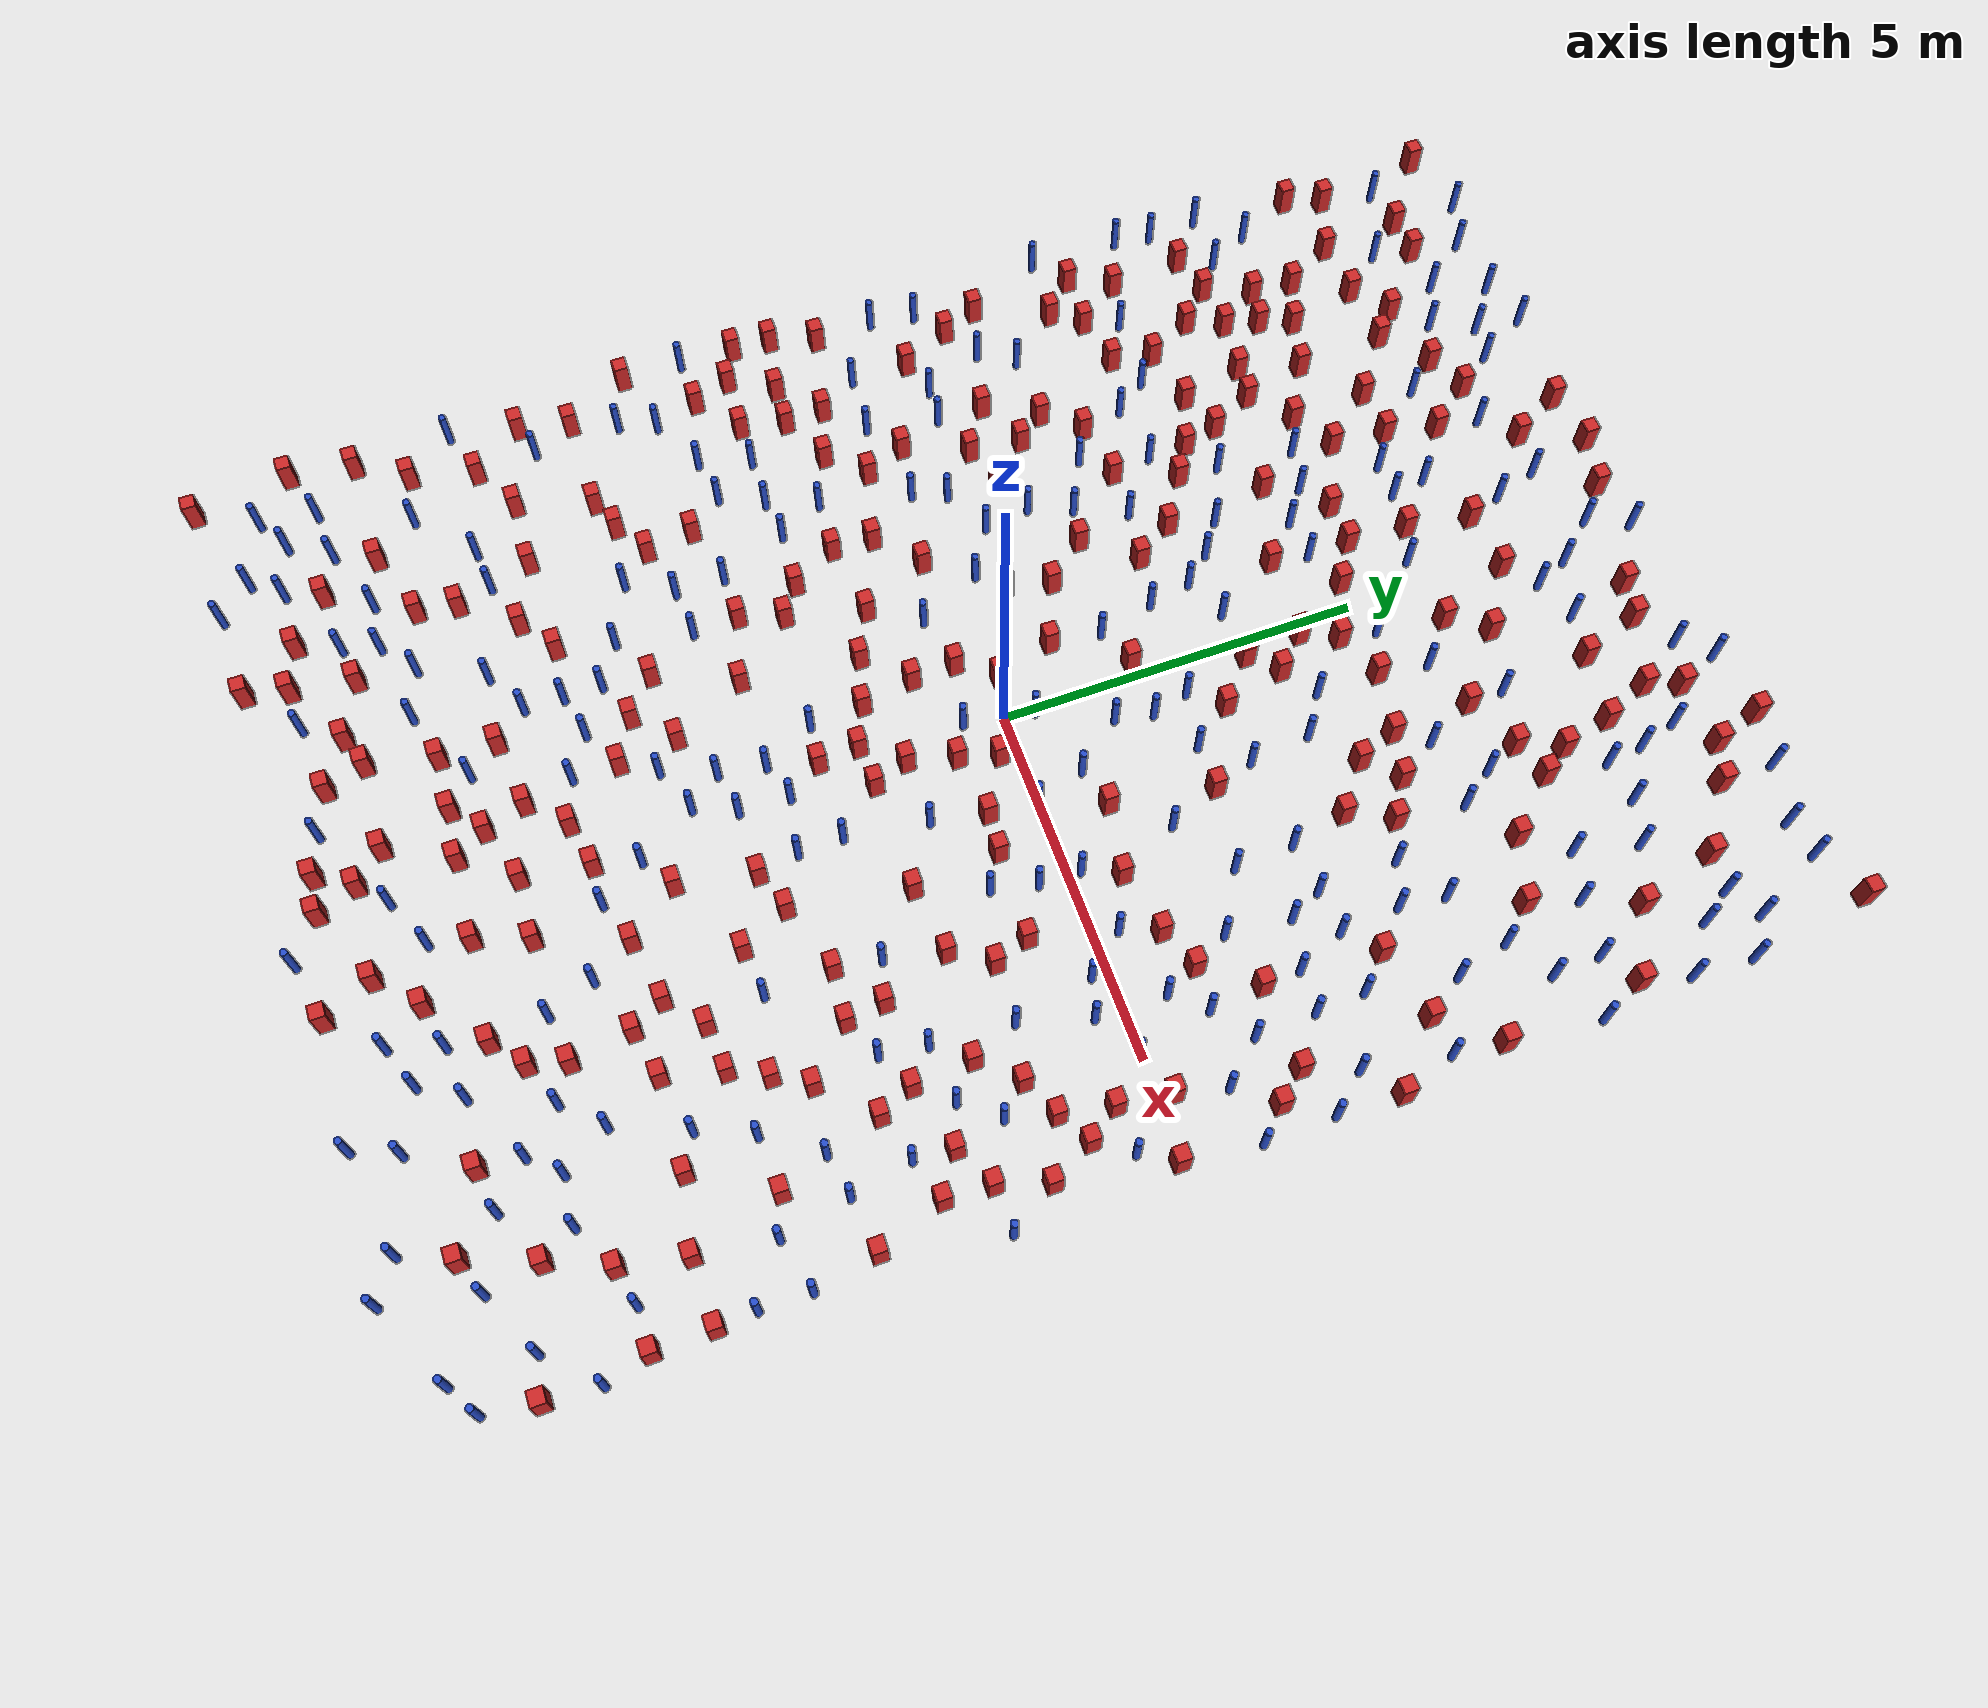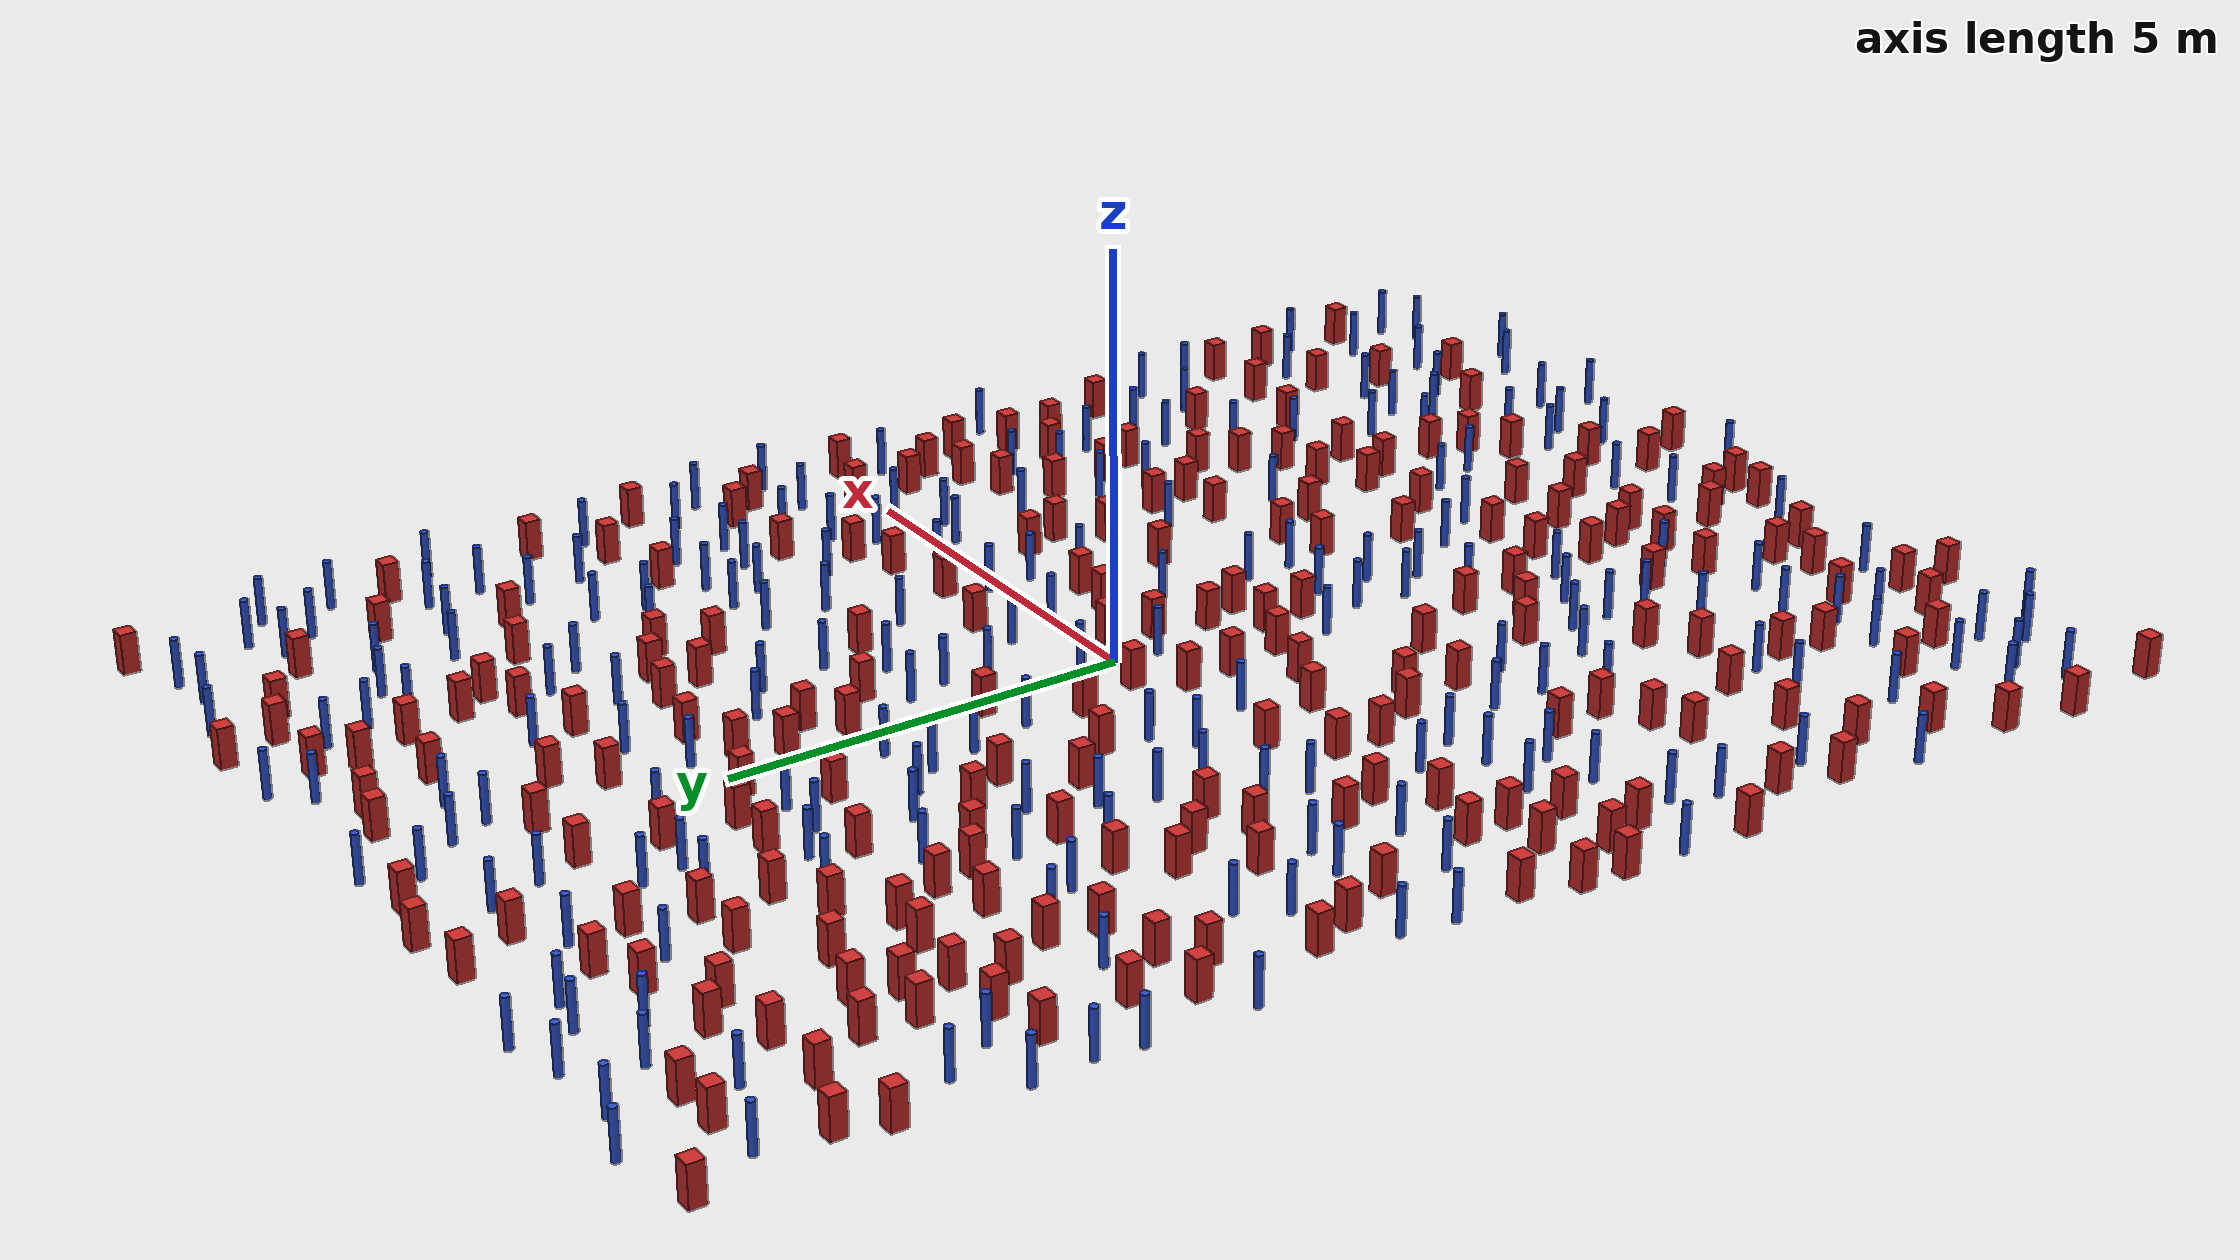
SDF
<sdf version="1.6">
  <model name="dense_87"><model name="pole_obstacle0">
  <static>true</static>
  <pose frame="">-4.22685877733 -5.90566886651 -3.09024884793e-07 -7.19054271911e-07 -2.1131507516e-07 -1.93935509277e-07</pose>
  <link name="link">
  <pose frame="">0 0 0.3 0 -0 0</pose>
    <inertial>
      <mass>1</mass>
      <inertia>
        <ixx>0.145833</ixx>
        <ixy>0</ixy>
        <ixz>0</ixz>
        <iyy>0.145833</iyy>
        <iyz>0</iyz>
        <izz>0.125</izz>
      </inertia>
    </inertial>
    <collision name="collision">
      <geometry>
        <cylinder>
          <radius>0.05</radius>
          <length>.6</length>
        </cylinder>
      </geometry>
      <max_contacts>10</max_contacts>
      <surface>
        <contact>
          <ode/>
        </contact>
        <bounce/>
        <friction>
          <torsional>
            <ode/>
          </torsional>
          <ode/>
        </friction>
      </surface>
    </collision>
    <visual name="visual">
      <geometry>
        <cylinder>
          <radius>0.05</radius>
          <length>.6</length>
        </cylinder>
      </geometry>
      <material>
        <script>
          <name>Gazebo/Blue</name>
          <uri>file://media/materials/scripts/gazebo.material</uri>
        </script>
      </material>
    </visual>
    <self_collide>0</self_collide>
    <kinematic>0</kinematic>
  </link>
</model>
<model name="pole_obstacle1">
  <static>true</static>
  <pose frame="">6.48809205417 -7.17369330818 -3.09024884793e-07 -7.19054271911e-07 -2.1131507516e-07 -1.93935509277e-07</pose>
  <link name="link">
  <pose frame="">0 0 0.3 0 -0 0</pose>
    <inertial>
      <mass>1</mass>
      <inertia>
        <ixx>0.145833</ixx>
        <ixy>0</ixy>
        <ixz>0</ixz>
        <iyy>0.145833</iyy>
        <iyz>0</iyz>
        <izz>0.125</izz>
      </inertia>
    </inertial>
    <collision name="collision">
      <geometry>
        <cylinder>
          <radius>0.05</radius>
          <length>.6</length>
        </cylinder>
      </geometry>
      <max_contacts>10</max_contacts>
      <surface>
        <contact>
          <ode/>
        </contact>
        <bounce/>
        <friction>
          <torsional>
            <ode/>
          </torsional>
          <ode/>
        </friction>
      </surface>
    </collision>
    <visual name="visual">
      <geometry>
        <cylinder>
          <radius>0.05</radius>
          <length>.6</length>
        </cylinder>
      </geometry>
      <material>
        <script>
          <name>Gazebo/Blue</name>
          <uri>file://media/materials/scripts/gazebo.material</uri>
        </script>
      </material>
    </visual>
    <self_collide>0</self_collide>
    <kinematic>0</kinematic>
  </link>
</model>
<model name="square_post_obstacle0">
  <static>true</static>
  <pose frame="">-1.66363238739 -3.12677479647 -4.36207812815e-07 3.75137919937e-06 9.77721102514e-07 2.47381364184e-05</pose>
  <link name="link">
    <pose frame="">0 0 0.25 0 -0 0</pose>
    <inertial>
      <mass>100</mass>
      <inertia>
        <ixx>0.166667</ixx>
        <ixy>0</ixy>
        <ixz>0</ixz>
        <iyy>0.166667</iyy>
        <iyz>0</iyz>
        <izz>0.166667</izz>
      </inertia>
    </inertial>
    <collision name="collision">
      <geometry>
        <box>
          <size>.2 .2 .5</size>
        </box>
      </geometry>
      <max_contacts>10</max_contacts>
      <surface>
        <contact>
          <ode/>
        </contact>
        <bounce/>
        <friction>
          <torsional>
            <ode/>
          </torsional>
          <ode/>
        </friction>
      </surface>
    </collision>
    <visual name="visual">
      <geometry>
        <box>
          <size>.2 .2 .5</size>
        </box>
      </geometry>
      <material>
        <script>
          <name>Gazebo/Red</name>
          <uri>file://media/materials/scripts/gazebo.material</uri>
        </script>
      </material>
    </visual>
    <self_collide>0</self_collide>
    <kinematic>0</kinematic>
  </link>
</model>
<model name="square_post_obstacle1">
  <static>true</static>
  <pose frame="">3.32283525771 -3.27233390259 -4.36207812815e-07 3.75137919937e-06 9.77721102514e-07 2.47381364184e-05</pose>
  <link name="link">
    <pose frame="">0 0 0.25 0 -0 0</pose>
    <inertial>
      <mass>100</mass>
      <inertia>
        <ixx>0.166667</ixx>
        <ixy>0</ixy>
        <ixz>0</ixz>
        <iyy>0.166667</iyy>
        <iyz>0</iyz>
        <izz>0.166667</izz>
      </inertia>
    </inertial>
    <collision name="collision">
      <geometry>
        <box>
          <size>.2 .2 .5</size>
        </box>
      </geometry>
      <max_contacts>10</max_contacts>
      <surface>
        <contact>
          <ode/>
        </contact>
        <bounce/>
        <friction>
          <torsional>
            <ode/>
          </torsional>
          <ode/>
        </friction>
      </surface>
    </collision>
    <visual name="visual">
      <geometry>
        <box>
          <size>.2 .2 .5</size>
        </box>
      </geometry>
      <material>
        <script>
          <name>Gazebo/Red</name>
          <uri>file://media/materials/scripts/gazebo.material</uri>
        </script>
      </material>
    </visual>
    <self_collide>0</self_collide>
    <kinematic>0</kinematic>
  </link>
</model>
<model name="pole_obstacle2">
  <static>true</static>
  <pose frame="">-0.090030062196 -4.2540395773 -3.09024884793e-07 -7.19054271912e-07 -2.11315075133e-07 -1.93935509265e-07</pose>
  <link name="link">
  <pose frame="">0 0 0.3 0 -0 0</pose>
    <inertial>
      <mass>1</mass>
      <inertia>
        <ixx>0.145833</ixx>
        <ixy>0</ixy>
        <ixz>0</ixz>
        <iyy>0.145833</iyy>
        <iyz>0</iyz>
        <izz>0.125</izz>
      </inertia>
    </inertial>
    <collision name="collision">
      <geometry>
        <cylinder>
          <radius>0.05</radius>
          <length>.6</length>
        </cylinder>
      </geometry>
      <max_contacts>10</max_contacts>
      <surface>
        <contact>
          <ode/>
        </contact>
        <bounce/>
        <friction>
          <torsional>
            <ode/>
          </torsional>
          <ode/>
        </friction>
      </surface>
    </collision>
    <visual name="visual">
      <geometry>
        <cylinder>
          <radius>0.05</radius>
          <length>.6</length>
        </cylinder>
      </geometry>
      <material>
        <script>
          <name>Gazebo/Blue</name>
          <uri>file://media/materials/scripts/gazebo.material</uri>
        </script>
      </material>
    </visual>
    <self_collide>0</self_collide>
    <kinematic>0</kinematic>
  </link>
</model>
<model name="pole_obstacle3">
  <static>true</static>
  <pose frame="">-2.24240057749 -5.93828908291 -3.09024884793e-07 -7.19054271912e-07 -2.11315075134e-07 -1.93935509266e-07</pose>
  <link name="link">
  <pose frame="">0 0 0.3 0 -0 0</pose>
    <inertial>
      <mass>1</mass>
      <inertia>
        <ixx>0.145833</ixx>
        <ixy>0</ixy>
        <ixz>0</ixz>
        <iyy>0.145833</iyy>
        <iyz>0</iyz>
        <izz>0.125</izz>
      </inertia>
    </inertial>
    <collision name="collision">
      <geometry>
        <cylinder>
          <radius>0.05</radius>
          <length>.6</length>
        </cylinder>
      </geometry>
      <max_contacts>10</max_contacts>
      <surface>
        <contact>
          <ode/>
        </contact>
        <bounce/>
        <friction>
          <torsional>
            <ode/>
          </torsional>
          <ode/>
        </friction>
      </surface>
    </collision>
    <visual name="visual">
      <geometry>
        <cylinder>
          <radius>0.05</radius>
          <length>.6</length>
        </cylinder>
      </geometry>
      <material>
        <script>
          <name>Gazebo/Blue</name>
          <uri>file://media/materials/scripts/gazebo.material</uri>
        </script>
      </material>
    </visual>
    <self_collide>0</self_collide>
    <kinematic>0</kinematic>
  </link>
</model>
<model name="pole_obstacle4">
  <static>true</static>
  <pose frame="">4.31455545916 2.92079606758 -3.09024884793e-07 -7.19054271912e-07 -2.11315075144e-07 -1.93935509269e-07</pose>
  <link name="link">
  <pose frame="">0 0 0.3 0 -0 0</pose>
    <inertial>
      <mass>1</mass>
      <inertia>
        <ixx>0.145833</ixx>
        <ixy>0</ixy>
        <ixz>0</ixz>
        <iyy>0.145833</iyy>
        <iyz>0</iyz>
        <izz>0.125</izz>
      </inertia>
    </inertial>
    <collision name="collision">
      <geometry>
        <cylinder>
          <radius>0.05</radius>
          <length>.6</length>
        </cylinder>
      </geometry>
      <max_contacts>10</max_contacts>
      <surface>
        <contact>
          <ode/>
        </contact>
        <bounce/>
        <friction>
          <torsional>
            <ode/>
          </torsional>
          <ode/>
        </friction>
      </surface>
    </collision>
    <visual name="visual">
      <geometry>
        <cylinder>
          <radius>0.05</radius>
          <length>.6</length>
        </cylinder>
      </geometry>
      <material>
        <script>
          <name>Gazebo/Blue</name>
          <uri>file://media/materials/scripts/gazebo.material</uri>
        </script>
      </material>
    </visual>
    <self_collide>0</self_collide>
    <kinematic>0</kinematic>
  </link>
</model>
<model name="pole_obstacle5">
  <static>true</static>
  <pose frame="">5.40202079288 9.03838742741 -3.09024884793e-07 -7.19054271912e-07 -2.1131507513e-07 -1.93935509261e-07</pose>
  <link name="link">
  <pose frame="">0 0 0.3 0 -0 0</pose>
    <inertial>
      <mass>1</mass>
      <inertia>
        <ixx>0.145833</ixx>
        <ixy>0</ixy>
        <ixz>0</ixz>
        <iyy>0.145833</iyy>
        <iyz>0</iyz>
        <izz>0.125</izz>
      </inertia>
    </inertial>
    <collision name="collision">
      <geometry>
        <cylinder>
          <radius>0.05</radius>
          <length>.6</length>
        </cylinder>
      </geometry>
      <max_contacts>10</max_contacts>
      <surface>
        <contact>
          <ode/>
        </contact>
        <bounce/>
        <friction>
          <torsional>
            <ode/>
          </torsional>
          <ode/>
        </friction>
      </surface>
    </collision>
    <visual name="visual">
      <geometry>
        <cylinder>
          <radius>0.05</radius>
          <length>.6</length>
        </cylinder>
      </geometry>
      <material>
        <script>
          <name>Gazebo/Blue</name>
          <uri>file://media/materials/scripts/gazebo.material</uri>
        </script>
      </material>
    </visual>
    <self_collide>0</self_collide>
    <kinematic>0</kinematic>
  </link>
</model>
<model name="pole_obstacle6">
  <static>true</static>
  <pose frame="">4.31357146107 -0.379242574637 -3.09024884793e-07 -7.19054271912e-07 -2.11315075138e-07 -1.93935509266e-07</pose>
  <link name="link">
  <pose frame="">0 0 0.3 0 -0 0</pose>
    <inertial>
      <mass>1</mass>
      <inertia>
        <ixx>0.145833</ixx>
        <ixy>0</ixy>
        <ixz>0</ixz>
        <iyy>0.145833</iyy>
        <iyz>0</iyz>
        <izz>0.125</izz>
      </inertia>
    </inertial>
    <collision name="collision">
      <geometry>
        <cylinder>
          <radius>0.05</radius>
          <length>.6</length>
        </cylinder>
      </geometry>
      <max_contacts>10</max_contacts>
      <surface>
        <contact>
          <ode/>
        </contact>
        <bounce/>
        <friction>
          <torsional>
            <ode/>
          </torsional>
          <ode/>
        </friction>
      </surface>
    </collision>
    <visual name="visual">
      <geometry>
        <cylinder>
          <radius>0.05</radius>
          <length>.6</length>
        </cylinder>
      </geometry>
      <material>
        <script>
          <name>Gazebo/Blue</name>
          <uri>file://media/materials/scripts/gazebo.material</uri>
        </script>
      </material>
    </visual>
    <self_collide>0</self_collide>
    <kinematic>0</kinematic>
  </link>
</model>
<model name="square_post_obstacle2">
  <static>true</static>
  <pose frame="">2.76552390389 7.45697668881 -4.36207812815e-07 3.75137919937e-06 9.77721102514e-07 2.47381364184e-05</pose>
  <link name="link">
    <pose frame="">0 0 0.25 0 -0 0</pose>
    <inertial>
      <mass>100</mass>
      <inertia>
        <ixx>0.166667</ixx>
        <ixy>0</ixy>
        <ixz>0</ixz>
        <iyy>0.166667</iyy>
        <iyz>0</iyz>
        <izz>0.166667</izz>
      </inertia>
    </inertial>
    <collision name="collision">
      <geometry>
        <box>
          <size>.2 .2 .5</size>
        </box>
      </geometry>
      <max_contacts>10</max_contacts>
      <surface>
        <contact>
          <ode/>
        </contact>
        <bounce/>
        <friction>
          <torsional>
            <ode/>
          </torsional>
          <ode/>
        </friction>
      </surface>
    </collision>
    <visual name="visual">
      <geometry>
        <box>
          <size>.2 .2 .5</size>
        </box>
      </geometry>
      <material>
        <script>
          <name>Gazebo/Red</name>
          <uri>file://media/materials/scripts/gazebo.material</uri>
        </script>
      </material>
    </visual>
    <self_collide>0</self_collide>
    <kinematic>0</kinematic>
  </link>
</model>
<model name="square_post_obstacle3">
  <static>true</static>
  <pose frame="">-5.67789752133 3.30921773179 -4.36207812815e-07 3.75137919937e-06 9.77721102514e-07 2.47381364184e-05</pose>
  <link name="link">
    <pose frame="">0 0 0.25 0 -0 0</pose>
    <inertial>
      <mass>100</mass>
      <inertia>
        <ixx>0.166667</ixx>
        <ixy>0</ixy>
        <ixz>0</ixz>
        <iyy>0.166667</iyy>
        <iyz>0</iyz>
        <izz>0.166667</izz>
      </inertia>
    </inertial>
    <collision name="collision">
      <geometry>
        <box>
          <size>.2 .2 .5</size>
        </box>
      </geometry>
      <max_contacts>10</max_contacts>
      <surface>
        <contact>
          <ode/>
        </contact>
        <bounce/>
        <friction>
          <torsional>
            <ode/>
          </torsional>
          <ode/>
        </friction>
      </surface>
    </collision>
    <visual name="visual">
      <geometry>
        <box>
          <size>.2 .2 .5</size>
        </box>
      </geometry>
      <material>
        <script>
          <name>Gazebo/Red</name>
          <uri>file://media/materials/scripts/gazebo.material</uri>
        </script>
      </material>
    </visual>
    <self_collide>0</self_collide>
    <kinematic>0</kinematic>
  </link>
</model>
<model name="square_post_obstacle4">
  <static>true</static>
  <pose frame="">3.57101372256 -7.95209607178 -4.36207812815e-07 3.75137919937e-06 9.77721102514e-07 2.47381364184e-05</pose>
  <link name="link">
    <pose frame="">0 0 0.25 0 -0 0</pose>
    <inertial>
      <mass>100</mass>
      <inertia>
        <ixx>0.166667</ixx>
        <ixy>0</ixy>
        <ixz>0</ixz>
        <iyy>0.166667</iyy>
        <iyz>0</iyz>
        <izz>0.166667</izz>
      </inertia>
    </inertial>
    <collision name="collision">
      <geometry>
        <box>
          <size>.2 .2 .5</size>
        </box>
      </geometry>
      <max_contacts>10</max_contacts>
      <surface>
        <contact>
          <ode/>
        </contact>
        <bounce/>
        <friction>
          <torsional>
            <ode/>
          </torsional>
          <ode/>
        </friction>
      </surface>
    </collision>
    <visual name="visual">
      <geometry>
        <box>
          <size>.2 .2 .5</size>
        </box>
      </geometry>
      <material>
        <script>
          <name>Gazebo/Red</name>
          <uri>file://media/materials/scripts/gazebo.material</uri>
        </script>
      </material>
    </visual>
    <self_collide>0</self_collide>
    <kinematic>0</kinematic>
  </link>
</model>
<model name="pole_obstacle7">
  <static>true</static>
  <pose frame="">-6.65705100794 1.02592357869 -3.09024884793e-07 -7.19054271912e-07 -2.11315075124e-07 -1.9393550926e-07</pose>
  <link name="link">
  <pose frame="">0 0 0.3 0 -0 0</pose>
    <inertial>
      <mass>1</mass>
      <inertia>
        <ixx>0.145833</ixx>
        <ixy>0</ixy>
        <ixz>0</ixz>
        <iyy>0.145833</iyy>
        <iyz>0</iyz>
        <izz>0.125</izz>
      </inertia>
    </inertial>
    <collision name="collision">
      <geometry>
        <cylinder>
          <radius>0.05</radius>
          <length>.6</length>
        </cylinder>
      </geometry>
      <max_contacts>10</max_contacts>
      <surface>
        <contact>
          <ode/>
        </contact>
        <bounce/>
        <friction>
          <torsional>
            <ode/>
          </torsional>
          <ode/>
        </friction>
      </surface>
    </collision>
    <visual name="visual">
      <geometry>
        <cylinder>
          <radius>0.05</radius>
          <length>.6</length>
        </cylinder>
      </geometry>
      <material>
        <script>
          <name>Gazebo/Blue</name>
          <uri>file://media/materials/scripts/gazebo.material</uri>
        </script>
      </material>
    </visual>
    <self_collide>0</self_collide>
    <kinematic>0</kinematic>
  </link>
</model>
<model name="pole_obstacle8">
  <static>true</static>
  <pose frame="">0.40500175959 -5.05351949 -3.09024884793e-07 -7.19054271912e-07 -2.1131507513e-07 -1.93935509262e-07</pose>
  <link name="link">
  <pose frame="">0 0 0.3 0 -0 0</pose>
    <inertial>
      <mass>1</mass>
      <inertia>
        <ixx>0.145833</ixx>
        <ixy>0</ixy>
        <ixz>0</ixz>
        <iyy>0.145833</iyy>
        <iyz>0</iyz>
        <izz>0.125</izz>
      </inertia>
    </inertial>
    <collision name="collision">
      <geometry>
        <cylinder>
          <radius>0.05</radius>
          <length>.6</length>
        </cylinder>
      </geometry>
      <max_contacts>10</max_contacts>
      <surface>
        <contact>
          <ode/>
        </contact>
        <bounce/>
        <friction>
          <torsional>
            <ode/>
          </torsional>
          <ode/>
        </friction>
      </surface>
    </collision>
    <visual name="visual">
      <geometry>
        <cylinder>
          <radius>0.05</radius>
          <length>.6</length>
        </cylinder>
      </geometry>
      <material>
        <script>
          <name>Gazebo/Blue</name>
          <uri>file://media/materials/scripts/gazebo.material</uri>
        </script>
      </material>
    </visual>
    <self_collide>0</self_collide>
    <kinematic>0</kinematic>
  </link>
</model>
<model name="square_post_obstacle5">
  <static>true</static>
  <pose frame="">-6.45985207222 -4.20283826774 -4.36207812815e-07 3.75137919937e-06 9.77721102514e-07 2.47381364184e-05</pose>
  <link name="link">
    <pose frame="">0 0 0.25 0 -0 0</pose>
    <inertial>
      <mass>100</mass>
      <inertia>
        <ixx>0.166667</ixx>
        <ixy>0</ixy>
        <ixz>0</ixz>
        <iyy>0.166667</iyy>
        <iyz>0</iyz>
        <izz>0.166667</izz>
      </inertia>
    </inertial>
    <collision name="collision">
      <geometry>
        <box>
          <size>.2 .2 .5</size>
        </box>
      </geometry>
      <max_contacts>10</max_contacts>
      <surface>
        <contact>
          <ode/>
        </contact>
        <bounce/>
        <friction>
          <torsional>
            <ode/>
          </torsional>
          <ode/>
        </friction>
      </surface>
    </collision>
    <visual name="visual">
      <geometry>
        <box>
          <size>.2 .2 .5</size>
        </box>
      </geometry>
      <material>
        <script>
          <name>Gazebo/Red</name>
          <uri>file://media/materials/scripts/gazebo.material</uri>
        </script>
      </material>
    </visual>
    <self_collide>0</self_collide>
    <kinematic>0</kinematic>
  </link>
</model>
<model name="square_post_obstacle6">
  <static>true</static>
  <pose frame="">-0.40497941243 -5.79051482355 -4.36207812815e-07 3.75137919937e-06 9.77721102514e-07 2.47381364184e-05</pose>
  <link name="link">
    <pose frame="">0 0 0.25 0 -0 0</pose>
    <inertial>
      <mass>100</mass>
      <inertia>
        <ixx>0.166667</ixx>
        <ixy>0</ixy>
        <ixz>0</ixz>
        <iyy>0.166667</iyy>
        <iyz>0</iyz>
        <izz>0.166667</izz>
      </inertia>
    </inertial>
    <collision name="collision">
      <geometry>
        <box>
          <size>.2 .2 .5</size>
        </box>
      </geometry>
      <max_contacts>10</max_contacts>
      <surface>
        <contact>
          <ode/>
        </contact>
        <bounce/>
        <friction>
          <torsional>
            <ode/>
          </torsional>
          <ode/>
        </friction>
      </surface>
    </collision>
    <visual name="visual">
      <geometry>
        <box>
          <size>.2 .2 .5</size>
        </box>
      </geometry>
      <material>
        <script>
          <name>Gazebo/Red</name>
          <uri>file://media/materials/scripts/gazebo.material</uri>
        </script>
      </material>
    </visual>
    <self_collide>0</self_collide>
    <kinematic>0</kinematic>
  </link>
</model>
<model name="square_post_obstacle7">
  <static>true</static>
  <pose frame="">3.95325379374 -3.89286199005 -4.36207812815e-07 3.75137919937e-06 9.77721102514e-07 2.47381364184e-05</pose>
  <link name="link">
    <pose frame="">0 0 0.25 0 -0 0</pose>
    <inertial>
      <mass>100</mass>
      <inertia>
        <ixx>0.166667</ixx>
        <ixy>0</ixy>
        <ixz>0</ixz>
        <iyy>0.166667</iyy>
        <iyz>0</iyz>
        <izz>0.166667</izz>
      </inertia>
    </inertial>
    <collision name="collision">
      <geometry>
        <box>
          <size>.2 .2 .5</size>
        </box>
      </geometry>
      <max_contacts>10</max_contacts>
      <surface>
        <contact>
          <ode/>
        </contact>
        <bounce/>
        <friction>
          <torsional>
            <ode/>
          </torsional>
          <ode/>
        </friction>
      </surface>
    </collision>
    <visual name="visual">
      <geometry>
        <box>
          <size>.2 .2 .5</size>
        </box>
      </geometry>
      <material>
        <script>
          <name>Gazebo/Red</name>
          <uri>file://media/materials/scripts/gazebo.material</uri>
        </script>
      </material>
    </visual>
    <self_collide>0</self_collide>
    <kinematic>0</kinematic>
  </link>
</model>
<model name="pole_obstacle9">
  <static>true</static>
  <pose frame="">-1.40873567202 3.47330076835 -3.09024884793e-07 -7.19054271912e-07 -2.11315075132e-07 -1.93935509263e-07</pose>
  <link name="link">
  <pose frame="">0 0 0.3 0 -0 0</pose>
    <inertial>
      <mass>1</mass>
      <inertia>
        <ixx>0.145833</ixx>
        <ixy>0</ixy>
        <ixz>0</ixz>
        <iyy>0.145833</iyy>
        <iyz>0</iyz>
        <izz>0.125</izz>
      </inertia>
    </inertial>
    <collision name="collision">
      <geometry>
        <cylinder>
          <radius>0.05</radius>
          <length>.6</length>
        </cylinder>
      </geometry>
      <max_contacts>10</max_contacts>
      <surface>
        <contact>
          <ode/>
        </contact>
        <bounce/>
        <friction>
          <torsional>
            <ode/>
          </torsional>
          <ode/>
        </friction>
      </surface>
    </collision>
    <visual name="visual">
      <geometry>
        <cylinder>
          <radius>0.05</radius>
          <length>.6</length>
        </cylinder>
      </geometry>
      <material>
        <script>
          <name>Gazebo/Blue</name>
          <uri>file://media/materials/scripts/gazebo.material</uri>
        </script>
      </material>
    </visual>
    <self_collide>0</self_collide>
    <kinematic>0</kinematic>
  </link>
</model>
<model name="pole_obstacle10">
  <static>true</static>
  <pose frame="">-2.85062982455 0.782185431165 -3.09024884793e-07 -7.19054271913e-07 -2.1131507512e-07 -1.93935509259e-07</pose>
  <link name="link">
  <pose frame="">0 0 0.3 0 -0 0</pose>
    <inertial>
      <mass>1</mass>
      <inertia>
        <ixx>0.145833</ixx>
        <ixy>0</ixy>
        <ixz>0</ixz>
        <iyy>0.145833</iyy>
        <iyz>0</iyz>
        <izz>0.125</izz>
      </inertia>
    </inertial>
    <collision name="collision">
      <geometry>
        <cylinder>
          <radius>0.05</radius>
          <length>.6</length>
        </cylinder>
      </geometry>
      <max_contacts>10</max_contacts>
      <surface>
        <contact>
          <ode/>
        </contact>
        <bounce/>
        <friction>
          <torsional>
            <ode/>
          </torsional>
          <ode/>
        </friction>
      </surface>
    </collision>
    <visual name="visual">
      <geometry>
        <cylinder>
          <radius>0.05</radius>
          <length>.6</length>
        </cylinder>
      </geometry>
      <material>
        <script>
          <name>Gazebo/Blue</name>
          <uri>file://media/materials/scripts/gazebo.material</uri>
        </script>
      </material>
    </visual>
    <self_collide>0</self_collide>
    <kinematic>0</kinematic>
  </link>
</model>
<model name="pole_obstacle11">
  <static>true</static>
  <pose frame="">-6.74947219534 0.385528594911 -3.09024884793e-07 -7.19054271912e-07 -2.11315075138e-07 -1.93935509266e-07</pose>
  <link name="link">
  <pose frame="">0 0 0.3 0 -0 0</pose>
    <inertial>
      <mass>1</mass>
      <inertia>
        <ixx>0.145833</ixx>
        <ixy>0</ixy>
        <ixz>0</ixz>
        <iyy>0.145833</iyy>
        <iyz>0</iyz>
        <izz>0.125</izz>
      </inertia>
    </inertial>
    <collision name="collision">
      <geometry>
        <cylinder>
          <radius>0.05</radius>
          <length>.6</length>
        </cylinder>
      </geometry>
      <max_contacts>10</max_contacts>
      <surface>
        <contact>
          <ode/>
        </contact>
        <bounce/>
        <friction>
          <torsional>
            <ode/>
          </torsional>
          <ode/>
        </friction>
      </surface>
    </collision>
    <visual name="visual">
      <geometry>
        <cylinder>
          <radius>0.05</radius>
          <length>.6</length>
        </cylinder>
      </geometry>
      <material>
        <script>
          <name>Gazebo/Blue</name>
          <uri>file://media/materials/scripts/gazebo.material</uri>
        </script>
      </material>
    </visual>
    <self_collide>0</self_collide>
    <kinematic>0</kinematic>
  </link>
</model>
<model name="pole_obstacle12">
  <static>true</static>
  <pose frame="">3.95533532752 -2.41421232316 -3.09024884793e-07 -7.19054271912e-07 -2.11315075162e-07 -1.93935509281e-07</pose>
  <link name="link">
  <pose frame="">0 0 0.3 0 -0 0</pose>
    <inertial>
      <mass>1</mass>
      <inertia>
        <ixx>0.145833</ixx>
        <ixy>0</ixy>
        <ixz>0</ixz>
        <iyy>0.145833</iyy>
        <iyz>0</iyz>
        <izz>0.125</izz>
      </inertia>
    </inertial>
    <collision name="collision">
      <geometry>
        <cylinder>
          <radius>0.05</radius>
          <length>.6</length>
        </cylinder>
      </geometry>
      <max_contacts>10</max_contacts>
      <surface>
        <contact>
          <ode/>
        </contact>
        <bounce/>
        <friction>
          <torsional>
            <ode/>
          </torsional>
          <ode/>
        </friction>
      </surface>
    </collision>
    <visual name="visual">
      <geometry>
        <cylinder>
          <radius>0.05</radius>
          <length>.6</length>
        </cylinder>
      </geometry>
      <material>
        <script>
          <name>Gazebo/Blue</name>
          <uri>file://media/materials/scripts/gazebo.material</uri>
        </script>
      </material>
    </visual>
    <self_collide>0</self_collide>
    <kinematic>0</kinematic>
  </link>
</model>
<model name="square_post_obstacle8">
  <static>true</static>
  <pose frame="">-5.84836770055 0.63526909699 -4.36207812815e-07 3.75137919937e-06 9.77721102514e-07 2.47381364184e-05</pose>
  <link name="link">
    <pose frame="">0 0 0.25 0 -0 0</pose>
    <inertial>
      <mass>100</mass>
      <inertia>
        <ixx>0.166667</ixx>
        <ixy>0</ixy>
        <ixz>0</ixz>
        <iyy>0.166667</iyy>
        <iyz>0</iyz>
        <izz>0.166667</izz>
      </inertia>
    </inertial>
    <collision name="collision">
      <geometry>
        <box>
          <size>.2 .2 .5</size>
        </box>
      </geometry>
      <max_contacts>10</max_contacts>
      <surface>
        <contact>
          <ode/>
        </contact>
        <bounce/>
        <friction>
          <torsional>
            <ode/>
          </torsional>
          <ode/>
        </friction>
      </surface>
    </collision>
    <visual name="visual">
      <geometry>
        <box>
          <size>.2 .2 .5</size>
        </box>
      </geometry>
      <material>
        <script>
          <name>Gazebo/Red</name>
          <uri>file://media/materials/scripts/gazebo.material</uri>
        </script>
      </material>
    </visual>
    <self_collide>0</self_collide>
    <kinematic>0</kinematic>
  </link>
</model>
<model name="square_post_obstacle9">
  <static>true</static>
  <pose frame="">-4.79678003949 4.04518257709 -4.36207812815e-07 3.75137919937e-06 9.77721102514e-07 2.47381364184e-05</pose>
  <link name="link">
    <pose frame="">0 0 0.25 0 -0 0</pose>
    <inertial>
      <mass>100</mass>
      <inertia>
        <ixx>0.166667</ixx>
        <ixy>0</ixy>
        <ixz>0</ixz>
        <iyy>0.166667</iyy>
        <iyz>0</iyz>
        <izz>0.166667</izz>
      </inertia>
    </inertial>
    <collision name="collision">
      <geometry>
        <box>
          <size>.2 .2 .5</size>
        </box>
      </geometry>
      <max_contacts>10</max_contacts>
      <surface>
        <contact>
          <ode/>
        </contact>
        <bounce/>
        <friction>
          <torsional>
            <ode/>
          </torsional>
          <ode/>
        </friction>
      </surface>
    </collision>
    <visual name="visual">
      <geometry>
        <box>
          <size>.2 .2 .5</size>
        </box>
      </geometry>
      <material>
        <script>
          <name>Gazebo/Red</name>
          <uri>file://media/materials/scripts/gazebo.material</uri>
        </script>
      </material>
    </visual>
    <self_collide>0</self_collide>
    <kinematic>0</kinematic>
  </link>
</model>
<model name="pole_obstacle13">
  <static>true</static>
  <pose frame="">-1.5103843144 6.82598550573 -3.09024884793e-07 -7.19054271912e-07 -2.11315075134e-07 -1.93935509265e-07</pose>
  <link name="link">
  <pose frame="">0 0 0.3 0 -0 0</pose>
    <inertial>
      <mass>1</mass>
      <inertia>
        <ixx>0.145833</ixx>
        <ixy>0</ixy>
        <ixz>0</ixz>
        <iyy>0.145833</iyy>
        <iyz>0</iyz>
        <izz>0.125</izz>
      </inertia>
    </inertial>
    <collision name="collision">
      <geometry>
        <cylinder>
          <radius>0.05</radius>
          <length>.6</length>
        </cylinder>
      </geometry>
      <max_contacts>10</max_contacts>
      <surface>
        <contact>
          <ode/>
        </contact>
        <bounce/>
        <friction>
          <torsional>
            <ode/>
          </torsional>
          <ode/>
        </friction>
      </surface>
    </collision>
    <visual name="visual">
      <geometry>
        <cylinder>
          <radius>0.05</radius>
          <length>.6</length>
        </cylinder>
      </geometry>
      <material>
        <script>
          <name>Gazebo/Blue</name>
          <uri>file://media/materials/scripts/gazebo.material</uri>
        </script>
      </material>
    </visual>
    <self_collide>0</self_collide>
    <kinematic>0</kinematic>
  </link>
</model>
<model name="square_post_obstacle10">
  <static>true</static>
  <pose frame="">-5.8417076227 8.38276541855 -4.36207812815e-07 3.75137919937e-06 9.77721102514e-07 2.47381364184e-05</pose>
  <link name="link">
    <pose frame="">0 0 0.25 0 -0 0</pose>
    <inertial>
      <mass>100</mass>
      <inertia>
        <ixx>0.166667</ixx>
        <ixy>0</ixy>
        <ixz>0</ixz>
        <iyy>0.166667</iyy>
        <iyz>0</iyz>
        <izz>0.166667</izz>
      </inertia>
    </inertial>
    <collision name="collision">
      <geometry>
        <box>
          <size>.2 .2 .5</size>
        </box>
      </geometry>
      <max_contacts>10</max_contacts>
      <surface>
        <contact>
          <ode/>
        </contact>
        <bounce/>
        <friction>
          <torsional>
            <ode/>
          </torsional>
          <ode/>
        </friction>
      </surface>
    </collision>
    <visual name="visual">
      <geometry>
        <box>
          <size>.2 .2 .5</size>
        </box>
      </geometry>
      <material>
        <script>
          <name>Gazebo/Red</name>
          <uri>file://media/materials/scripts/gazebo.material</uri>
        </script>
      </material>
    </visual>
    <self_collide>0</self_collide>
    <kinematic>0</kinematic>
  </link>
</model>
<model name="square_post_obstacle11">
  <static>true</static>
  <pose frame="">-3.21177201463 -1.34164451892 -4.36207812815e-07 3.75137919937e-06 9.77721102514e-07 2.47381364184e-05</pose>
  <link name="link">
    <pose frame="">0 0 0.25 0 -0 0</pose>
    <inertial>
      <mass>100</mass>
      <inertia>
        <ixx>0.166667</ixx>
        <ixy>0</ixy>
        <ixz>0</ixz>
        <iyy>0.166667</iyy>
        <iyz>0</iyz>
        <izz>0.166667</izz>
      </inertia>
    </inertial>
    <collision name="collision">
      <geometry>
        <box>
          <size>.2 .2 .5</size>
        </box>
      </geometry>
      <max_contacts>10</max_contacts>
      <surface>
        <contact>
          <ode/>
        </contact>
        <bounce/>
        <friction>
          <torsional>
            <ode/>
          </torsional>
          <ode/>
        </friction>
      </surface>
    </collision>
    <visual name="visual">
      <geometry>
        <box>
          <size>.2 .2 .5</size>
        </box>
      </geometry>
      <material>
        <script>
          <name>Gazebo/Red</name>
          <uri>file://media/materials/scripts/gazebo.material</uri>
        </script>
      </material>
    </visual>
    <self_collide>0</self_collide>
    <kinematic>0</kinematic>
  </link>
</model>
<model name="pole_obstacle14">
  <static>true</static>
  <pose frame="">-3.64864433912 -4.18007978093 -3.09024884793e-07 -7.19054271912e-07 -2.11315075134e-07 -1.93935509266e-07</pose>
  <link name="link">
  <pose frame="">0 0 0.3 0 -0 0</pose>
    <inertial>
      <mass>1</mass>
      <inertia>
        <ixx>0.145833</ixx>
        <ixy>0</ixy>
        <ixz>0</ixz>
        <iyy>0.145833</iyy>
        <iyz>0</iyz>
        <izz>0.125</izz>
      </inertia>
    </inertial>
    <collision name="collision">
      <geometry>
        <cylinder>
          <radius>0.05</radius>
          <length>.6</length>
        </cylinder>
      </geometry>
      <max_contacts>10</max_contacts>
      <surface>
        <contact>
          <ode/>
        </contact>
        <bounce/>
        <friction>
          <torsional>
            <ode/>
          </torsional>
          <ode/>
        </friction>
      </surface>
    </collision>
    <visual name="visual">
      <geometry>
        <cylinder>
          <radius>0.05</radius>
          <length>.6</length>
        </cylinder>
      </geometry>
      <material>
        <script>
          <name>Gazebo/Blue</name>
          <uri>file://media/materials/scripts/gazebo.material</uri>
        </script>
      </material>
    </visual>
    <self_collide>0</self_collide>
    <kinematic>0</kinematic>
  </link>
</model>
<model name="pole_obstacle15">
  <static>true</static>
  <pose frame="">4.04022569842 -1.31853993154 -3.09024884848e-07 -7.19054271902e-07 -2.11315075195e-07 -1.93935509285e-07</pose>
  <link name="link">
  <pose frame="">0 0 0.3 0 -0 0</pose>
    <inertial>
      <mass>1</mass>
      <inertia>
        <ixx>0.145833</ixx>
        <ixy>0</ixy>
        <ixz>0</ixz>
        <iyy>0.145833</iyy>
        <iyz>0</iyz>
        <izz>0.125</izz>
      </inertia>
    </inertial>
    <collision name="collision">
      <geometry>
        <cylinder>
          <radius>0.05</radius>
          <length>.6</length>
        </cylinder>
      </geometry>
      <max_contacts>10</max_contacts>
      <surface>
        <contact>
          <ode/>
        </contact>
        <bounce/>
        <friction>
          <torsional>
            <ode/>
          </torsional>
          <ode/>
        </friction>
      </surface>
    </collision>
    <visual name="visual">
      <geometry>
        <cylinder>
          <radius>0.05</radius>
          <length>.6</length>
        </cylinder>
      </geometry>
      <material>
        <script>
          <name>Gazebo/Blue</name>
          <uri>file://media/materials/scripts/gazebo.material</uri>
        </script>
      </material>
    </visual>
    <self_collide>0</self_collide>
    <kinematic>0</kinematic>
  </link>
</model>
<model name="square_post_obstacle12">
  <static>true</static>
  <pose frame="">-4.57360559203 -4.0499223594 -4.36207812815e-07 3.75137919937e-06 9.77721102514e-07 2.47381364184e-05</pose>
  <link name="link">
    <pose frame="">0 0 0.25 0 -0 0</pose>
    <inertial>
      <mass>100</mass>
      <inertia>
        <ixx>0.166667</ixx>
        <ixy>0</ixy>
        <ixz>0</ixz>
        <iyy>0.166667</iyy>
        <iyz>0</iyz>
        <izz>0.166667</izz>
      </inertia>
    </inertial>
    <collision name="collision">
      <geometry>
        <box>
          <size>.2 .2 .5</size>
        </box>
      </geometry>
      <max_contacts>10</max_contacts>
      <surface>
        <contact>
          <ode/>
        </contact>
        <bounce/>
        <friction>
          <torsional>
            <ode/>
          </torsional>
          <ode/>
        </friction>
      </surface>
    </collision>
    <visual name="visual">
      <geometry>
        <box>
          <size>.2 .2 .5</size>
        </box>
      </geometry>
      <material>
        <script>
          <name>Gazebo/Red</name>
          <uri>file://media/materials/scripts/gazebo.material</uri>
        </script>
      </material>
    </visual>
    <self_collide>0</self_collide>
    <kinematic>0</kinematic>
  </link>
</model>
<model name="pole_obstacle16">
  <static>true</static>
  <pose frame="">-5.43233219148 -7.82318585264 -3.09024884793e-07 -7.19054271911e-07 -2.1131507516e-07 -1.93935509277e-07</pose>
  <link name="link">
  <pose frame="">0 0 0.3 0 -0 0</pose>
    <inertial>
      <mass>1</mass>
      <inertia>
        <ixx>0.145833</ixx>
        <ixy>0</ixy>
        <ixz>0</ixz>
        <iyy>0.145833</iyy>
        <iyz>0</iyz>
        <izz>0.125</izz>
      </inertia>
    </inertial>
    <collision name="collision">
      <geometry>
        <cylinder>
          <radius>0.05</radius>
          <length>.6</length>
        </cylinder>
      </geometry>
      <max_contacts>10</max_contacts>
      <surface>
        <contact>
          <ode/>
        </contact>
        <bounce/>
        <friction>
          <torsional>
            <ode/>
          </torsional>
          <ode/>
        </friction>
      </surface>
    </collision>
    <visual name="visual">
      <geometry>
        <cylinder>
          <radius>0.05</radius>
          <length>.6</length>
        </cylinder>
      </geometry>
      <material>
        <script>
          <name>Gazebo/Blue</name>
          <uri>file://media/materials/scripts/gazebo.material</uri>
        </script>
      </material>
    </visual>
    <self_collide>0</self_collide>
    <kinematic>0</kinematic>
  </link>
</model>
<model name="pole_obstacle17">
  <static>true</static>
  <pose frame="">5.89942514941 7.99826392989 -3.09024884793e-07 -7.19054271912e-07 -2.11315075134e-07 -1.93935509264e-07</pose>
  <link name="link">
  <pose frame="">0 0 0.3 0 -0 0</pose>
    <inertial>
      <mass>1</mass>
      <inertia>
        <ixx>0.145833</ixx>
        <ixy>0</ixy>
        <ixz>0</ixz>
        <iyy>0.145833</iyy>
        <iyz>0</iyz>
        <izz>0.125</izz>
      </inertia>
    </inertial>
    <collision name="collision">
      <geometry>
        <cylinder>
          <radius>0.05</radius>
          <length>.6</length>
        </cylinder>
      </geometry>
      <max_contacts>10</max_contacts>
      <surface>
        <contact>
          <ode/>
        </contact>
        <bounce/>
        <friction>
          <torsional>
            <ode/>
          </torsional>
          <ode/>
        </friction>
      </surface>
    </collision>
    <visual name="visual">
      <geometry>
        <cylinder>
          <radius>0.05</radius>
          <length>.6</length>
        </cylinder>
      </geometry>
      <material>
        <script>
          <name>Gazebo/Blue</name>
          <uri>file://media/materials/scripts/gazebo.material</uri>
        </script>
      </material>
    </visual>
    <self_collide>0</self_collide>
    <kinematic>0</kinematic>
  </link>
</model>
<model name="square_post_obstacle13">
  <static>true</static>
  <pose frame="">-2.62023415638 -2.87275830465 -4.36207812815e-07 3.75137919937e-06 9.77721102514e-07 2.47381364184e-05</pose>
  <link name="link">
    <pose frame="">0 0 0.25 0 -0 0</pose>
    <inertial>
      <mass>100</mass>
      <inertia>
        <ixx>0.166667</ixx>
        <ixy>0</ixy>
        <ixz>0</ixz>
        <iyy>0.166667</iyy>
        <iyz>0</iyz>
        <izz>0.166667</izz>
      </inertia>
    </inertial>
    <collision name="collision">
      <geometry>
        <box>
          <size>.2 .2 .5</size>
        </box>
      </geometry>
      <max_contacts>10</max_contacts>
      <surface>
        <contact>
          <ode/>
        </contact>
        <bounce/>
        <friction>
          <torsional>
            <ode/>
          </torsional>
          <ode/>
        </friction>
      </surface>
    </collision>
    <visual name="visual">
      <geometry>
        <box>
          <size>.2 .2 .5</size>
        </box>
      </geometry>
      <material>
        <script>
          <name>Gazebo/Red</name>
          <uri>file://media/materials/scripts/gazebo.material</uri>
        </script>
      </material>
    </visual>
    <self_collide>0</self_collide>
    <kinematic>0</kinematic>
  </link>
</model>
<model name="pole_obstacle18">
  <static>true</static>
  <pose frame="">-3.46136850801 2.39989970297 -3.09024884793e-07 -7.19054271912e-07 -2.11315075128e-07 -1.93935509262e-07</pose>
  <link name="link">
  <pose frame="">0 0 0.3 0 -0 0</pose>
    <inertial>
      <mass>1</mass>
      <inertia>
        <ixx>0.145833</ixx>
        <ixy>0</ixy>
        <ixz>0</ixz>
        <iyy>0.145833</iyy>
        <iyz>0</iyz>
        <izz>0.125</izz>
      </inertia>
    </inertial>
    <collision name="collision">
      <geometry>
        <cylinder>
          <radius>0.05</radius>
          <length>.6</length>
        </cylinder>
      </geometry>
      <max_contacts>10</max_contacts>
      <surface>
        <contact>
          <ode/>
        </contact>
        <bounce/>
        <friction>
          <torsional>
            <ode/>
          </torsional>
          <ode/>
        </friction>
      </surface>
    </collision>
    <visual name="visual">
      <geometry>
        <cylinder>
          <radius>0.05</radius>
          <length>.6</length>
        </cylinder>
      </geometry>
      <material>
        <script>
          <name>Gazebo/Blue</name>
          <uri>file://media/materials/scripts/gazebo.material</uri>
        </script>
      </material>
    </visual>
    <self_collide>0</self_collide>
    <kinematic>0</kinematic>
  </link>
</model>
<model name="square_post_obstacle14">
  <static>true</static>
  <pose frame="">5.42709874171 -5.83818717794 -4.36207812815e-07 3.75137919937e-06 9.77721102514e-07 2.47381364184e-05</pose>
  <link name="link">
    <pose frame="">0 0 0.25 0 -0 0</pose>
    <inertial>
      <mass>100</mass>
      <inertia>
        <ixx>0.166667</ixx>
        <ixy>0</ixy>
        <ixz>0</ixz>
        <iyy>0.166667</iyy>
        <iyz>0</iyz>
        <izz>0.166667</izz>
      </inertia>
    </inertial>
    <collision name="collision">
      <geometry>
        <box>
          <size>.2 .2 .5</size>
        </box>
      </geometry>
      <max_contacts>10</max_contacts>
      <surface>
        <contact>
          <ode/>
        </contact>
        <bounce/>
        <friction>
          <torsional>
            <ode/>
          </torsional>
          <ode/>
        </friction>
      </surface>
    </collision>
    <visual name="visual">
      <geometry>
        <box>
          <size>.2 .2 .5</size>
        </box>
      </geometry>
      <material>
        <script>
          <name>Gazebo/Red</name>
          <uri>file://media/materials/scripts/gazebo.material</uri>
        </script>
      </material>
    </visual>
    <self_collide>0</self_collide>
    <kinematic>0</kinematic>
  </link>
</model>
<model name="pole_obstacle19">
  <static>true</static>
  <pose frame="">5.58174144384 -4.82042936975 -3.09024884793e-07 -7.19054271911e-07 -2.1131507516e-07 -1.93935509277e-07</pose>
  <link name="link">
  <pose frame="">0 0 0.3 0 -0 0</pose>
    <inertial>
      <mass>1</mass>
      <inertia>
        <ixx>0.145833</ixx>
        <ixy>0</ixy>
        <ixz>0</ixz>
        <iyy>0.145833</iyy>
        <iyz>0</iyz>
        <izz>0.125</izz>
      </inertia>
    </inertial>
    <collision name="collision">
      <geometry>
        <cylinder>
          <radius>0.05</radius>
          <length>.6</length>
        </cylinder>
      </geometry>
      <max_contacts>10</max_contacts>
      <surface>
        <contact>
          <ode/>
        </contact>
        <bounce/>
        <friction>
          <torsional>
            <ode/>
          </torsional>
          <ode/>
        </friction>
      </surface>
    </collision>
    <visual name="visual">
      <geometry>
        <cylinder>
          <radius>0.05</radius>
          <length>.6</length>
        </cylinder>
      </geometry>
      <material>
        <script>
          <name>Gazebo/Blue</name>
          <uri>file://media/materials/scripts/gazebo.material</uri>
        </script>
      </material>
    </visual>
    <self_collide>0</self_collide>
    <kinematic>0</kinematic>
  </link>
</model>
<model name="square_post_obstacle15">
  <static>true</static>
  <pose frame="">1.08311566166 -3.7098398395 -4.36207812815e-07 3.75137919937e-06 9.77721102514e-07 2.47381364184e-05</pose>
  <link name="link">
    <pose frame="">0 0 0.25 0 -0 0</pose>
    <inertial>
      <mass>100</mass>
      <inertia>
        <ixx>0.166667</ixx>
        <ixy>0</ixy>
        <ixz>0</ixz>
        <iyy>0.166667</iyy>
        <iyz>0</iyz>
        <izz>0.166667</izz>
      </inertia>
    </inertial>
    <collision name="collision">
      <geometry>
        <box>
          <size>.2 .2 .5</size>
        </box>
      </geometry>
      <max_contacts>10</max_contacts>
      <surface>
        <contact>
          <ode/>
        </contact>
        <bounce/>
        <friction>
          <torsional>
            <ode/>
          </torsional>
          <ode/>
        </friction>
      </surface>
    </collision>
    <visual name="visual">
      <geometry>
        <box>
          <size>.2 .2 .5</size>
        </box>
      </geometry>
      <material>
        <script>
          <name>Gazebo/Red</name>
          <uri>file://media/materials/scripts/gazebo.material</uri>
        </script>
      </material>
    </visual>
    <self_collide>0</self_collide>
    <kinematic>0</kinematic>
  </link>
</model>
<model name="square_post_obstacle16">
  <static>true</static>
  <pose frame="">0.86441685356 -4.75954110779 -4.36207812815e-07 3.75137919937e-06 9.77721102514e-07 2.47381364184e-05</pose>
  <link name="link">
    <pose frame="">0 0 0.25 0 -0 0</pose>
    <inertial>
      <mass>100</mass>
      <inertia>
        <ixx>0.166667</ixx>
        <ixy>0</ixy>
        <ixz>0</ixz>
        <iyy>0.166667</iyy>
        <iyz>0</iyz>
        <izz>0.166667</izz>
      </inertia>
    </inertial>
    <collision name="collision">
      <geometry>
        <box>
          <size>.2 .2 .5</size>
        </box>
      </geometry>
      <max_contacts>10</max_contacts>
      <surface>
        <contact>
          <ode/>
        </contact>
        <bounce/>
        <friction>
          <torsional>
            <ode/>
          </torsional>
          <ode/>
        </friction>
      </surface>
    </collision>
    <visual name="visual">
      <geometry>
        <box>
          <size>.2 .2 .5</size>
        </box>
      </geometry>
      <material>
        <script>
          <name>Gazebo/Red</name>
          <uri>file://media/materials/scripts/gazebo.material</uri>
        </script>
      </material>
    </visual>
    <self_collide>0</self_collide>
    <kinematic>0</kinematic>
  </link>
</model>
<model name="square_post_obstacle17">
  <static>true</static>
  <pose frame="">4.58752522071 -3.25393874034 -4.36207812815e-07 3.75137919937e-06 9.77721102514e-07 2.47381364184e-05</pose>
  <link name="link">
    <pose frame="">0 0 0.25 0 -0 0</pose>
    <inertial>
      <mass>100</mass>
      <inertia>
        <ixx>0.166667</ixx>
        <ixy>0</ixy>
        <ixz>0</ixz>
        <iyy>0.166667</iyy>
        <iyz>0</iyz>
        <izz>0.166667</izz>
      </inertia>
    </inertial>
    <collision name="collision">
      <geometry>
        <box>
          <size>.2 .2 .5</size>
        </box>
      </geometry>
      <max_contacts>10</max_contacts>
      <surface>
        <contact>
          <ode/>
        </contact>
        <bounce/>
        <friction>
          <torsional>
            <ode/>
          </torsional>
          <ode/>
        </friction>
      </surface>
    </collision>
    <visual name="visual">
      <geometry>
        <box>
          <size>.2 .2 .5</size>
        </box>
      </geometry>
      <material>
        <script>
          <name>Gazebo/Red</name>
          <uri>file://media/materials/scripts/gazebo.material</uri>
        </script>
      </material>
    </visual>
    <self_collide>0</self_collide>
    <kinematic>0</kinematic>
  </link>
</model>
<model name="pole_obstacle20">
  <static>true</static>
  <pose frame="">-4.82213224329 -5.9598305133 -3.09024884793e-07 -7.19054271911e-07 -2.1131507516e-07 -1.93935509277e-07</pose>
  <link name="link">
  <pose frame="">0 0 0.3 0 -0 0</pose>
    <inertial>
      <mass>1</mass>
      <inertia>
        <ixx>0.145833</ixx>
        <ixy>0</ixy>
        <ixz>0</ixz>
        <iyy>0.145833</iyy>
        <iyz>0</iyz>
        <izz>0.125</izz>
      </inertia>
    </inertial>
    <collision name="collision">
      <geometry>
        <cylinder>
          <radius>0.05</radius>
          <length>.6</length>
        </cylinder>
      </geometry>
      <max_contacts>10</max_contacts>
      <surface>
        <contact>
          <ode/>
        </contact>
        <bounce/>
        <friction>
          <torsional>
            <ode/>
          </torsional>
          <ode/>
        </friction>
      </surface>
    </collision>
    <visual name="visual">
      <geometry>
        <cylinder>
          <radius>0.05</radius>
          <length>.6</length>
        </cylinder>
      </geometry>
      <material>
        <script>
          <name>Gazebo/Blue</name>
          <uri>file://media/materials/scripts/gazebo.material</uri>
        </script>
      </material>
    </visual>
    <self_collide>0</self_collide>
    <kinematic>0</kinematic>
  </link>
</model>
<model name="pole_obstacle21">
  <static>true</static>
  <pose frame="">-2.80080425089 -4.53551060787 -3.09024884793e-07 -7.19054271912e-07 -2.11315075134e-07 -1.93935509266e-07</pose>
  <link name="link">
  <pose frame="">0 0 0.3 0 -0 0</pose>
    <inertial>
      <mass>1</mass>
      <inertia>
        <ixx>0.145833</ixx>
        <ixy>0</ixy>
        <ixz>0</ixz>
        <iyy>0.145833</iyy>
        <iyz>0</iyz>
        <izz>0.125</izz>
      </inertia>
    </inertial>
    <collision name="collision">
      <geometry>
        <cylinder>
          <radius>0.05</radius>
          <length>.6</length>
        </cylinder>
      </geometry>
      <max_contacts>10</max_contacts>
      <surface>
        <contact>
          <ode/>
        </contact>
        <bounce/>
        <friction>
          <torsional>
            <ode/>
          </torsional>
          <ode/>
        </friction>
      </surface>
    </collision>
    <visual name="visual">
      <geometry>
        <cylinder>
          <radius>0.05</radius>
          <length>.6</length>
        </cylinder>
      </geometry>
      <material>
        <script>
          <name>Gazebo/Blue</name>
          <uri>file://media/materials/scripts/gazebo.material</uri>
        </script>
      </material>
    </visual>
    <self_collide>0</self_collide>
    <kinematic>0</kinematic>
  </link>
</model>
<model name="pole_obstacle22">
  <static>true</static>
  <pose frame="">-3.80070359319 -7.52140959583 -3.09024884793e-07 -7.19054271912e-07 -2.11315075134e-07 -1.93935509266e-07</pose>
  <link name="link">
  <pose frame="">0 0 0.3 0 -0 0</pose>
    <inertial>
      <mass>1</mass>
      <inertia>
        <ixx>0.145833</ixx>
        <ixy>0</ixy>
        <ixz>0</ixz>
        <iyy>0.145833</iyy>
        <iyz>0</iyz>
        <izz>0.125</izz>
      </inertia>
    </inertial>
    <collision name="collision">
      <geometry>
        <cylinder>
          <radius>0.05</radius>
          <length>.6</length>
        </cylinder>
      </geometry>
      <max_contacts>10</max_contacts>
      <surface>
        <contact>
          <ode/>
        </contact>
        <bounce/>
        <friction>
          <torsional>
            <ode/>
          </torsional>
          <ode/>
        </friction>
      </surface>
    </collision>
    <visual name="visual">
      <geometry>
        <cylinder>
          <radius>0.05</radius>
          <length>.6</length>
        </cylinder>
      </geometry>
      <material>
        <script>
          <name>Gazebo/Blue</name>
          <uri>file://media/materials/scripts/gazebo.material</uri>
        </script>
      </material>
    </visual>
    <self_collide>0</self_collide>
    <kinematic>0</kinematic>
  </link>
</model>
<model name="pole_obstacle23">
  <static>true</static>
  <pose frame="">2.4174713655 -0.40537235112 -3.09024884793e-07 -7.19054271912e-07 -2.1131507512e-07 -1.93935509259e-07</pose>
  <link name="link">
  <pose frame="">0 0 0.3 0 -0 0</pose>
    <inertial>
      <mass>1</mass>
      <inertia>
        <ixx>0.145833</ixx>
        <ixy>0</ixy>
        <ixz>0</ixz>
        <iyy>0.145833</iyy>
        <iyz>0</iyz>
        <izz>0.125</izz>
      </inertia>
    </inertial>
    <collision name="collision">
      <geometry>
        <cylinder>
          <radius>0.05</radius>
          <length>.6</length>
        </cylinder>
      </geometry>
      <max_contacts>10</max_contacts>
      <surface>
        <contact>
          <ode/>
        </contact>
        <bounce/>
        <friction>
          <torsional>
            <ode/>
          </torsional>
          <ode/>
        </friction>
      </surface>
    </collision>
    <visual name="visual">
      <geometry>
        <cylinder>
          <radius>0.05</radius>
          <length>.6</length>
        </cylinder>
      </geometry>
      <material>
        <script>
          <name>Gazebo/Blue</name>
          <uri>file://media/materials/scripts/gazebo.material</uri>
        </script>
      </material>
    </visual>
    <self_collide>0</self_collide>
    <kinematic>0</kinematic>
  </link>
</model>
<model name="square_post_obstacle18">
  <static>true</static>
  <pose frame="">-6.27693186465 5.03771833636 -4.36207812815e-07 3.75137919937e-06 9.77721102514e-07 2.47381364184e-05</pose>
  <link name="link">
    <pose frame="">0 0 0.25 0 -0 0</pose>
    <inertial>
      <mass>100</mass>
      <inertia>
        <ixx>0.166667</ixx>
        <ixy>0</ixy>
        <ixz>0</ixz>
        <iyy>0.166667</iyy>
        <iyz>0</iyz>
        <izz>0.166667</izz>
      </inertia>
    </inertial>
    <collision name="collision">
      <geometry>
        <box>
          <size>.2 .2 .5</size>
        </box>
      </geometry>
      <max_contacts>10</max_contacts>
      <surface>
        <contact>
          <ode/>
        </contact>
        <bounce/>
        <friction>
          <torsional>
            <ode/>
          </torsional>
          <ode/>
        </friction>
      </surface>
    </collision>
    <visual name="visual">
      <geometry>
        <box>
          <size>.2 .2 .5</size>
        </box>
      </geometry>
      <material>
        <script>
          <name>Gazebo/Red</name>
          <uri>file://media/materials/scripts/gazebo.material</uri>
        </script>
      </material>
    </visual>
    <self_collide>0</self_collide>
    <kinematic>0</kinematic>
  </link>
</model>
<model name="pole_obstacle24">
  <static>true</static>
  <pose frame="">-1.72728421698 -0.518795387424 -3.09024884793e-07 -7.19054271912e-07 -2.11315075135e-07 -1.93935509266e-07</pose>
  <link name="link">
  <pose frame="">0 0 0.3 0 -0 0</pose>
    <inertial>
      <mass>1</mass>
      <inertia>
        <ixx>0.145833</ixx>
        <ixy>0</ixy>
        <ixz>0</ixz>
        <iyy>0.145833</iyy>
        <iyz>0</iyz>
        <izz>0.125</izz>
      </inertia>
    </inertial>
    <collision name="collision">
      <geometry>
        <cylinder>
          <radius>0.05</radius>
          <length>.6</length>
        </cylinder>
      </geometry>
      <max_contacts>10</max_contacts>
      <surface>
        <contact>
          <ode/>
        </contact>
        <bounce/>
        <friction>
          <torsional>
            <ode/>
          </torsional>
          <ode/>
        </friction>
      </surface>
    </collision>
    <visual name="visual">
      <geometry>
        <cylinder>
          <radius>0.05</radius>
          <length>.6</length>
        </cylinder>
      </geometry>
      <material>
        <script>
          <name>Gazebo/Blue</name>
          <uri>file://media/materials/scripts/gazebo.material</uri>
        </script>
      </material>
    </visual>
    <self_collide>0</self_collide>
    <kinematic>0</kinematic>
  </link>
</model>
<model name="pole_obstacle25">
  <static>true</static>
  <pose frame="">1.74162384043 2.80790043297 -3.09024884793e-07 -7.19054271912e-07 -2.11315075132e-07 -1.93935509263e-07</pose>
  <link name="link">
  <pose frame="">0 0 0.3 0 -0 0</pose>
    <inertial>
      <mass>1</mass>
      <inertia>
        <ixx>0.145833</ixx>
        <ixy>0</ixy>
        <ixz>0</ixz>
        <iyy>0.145833</iyy>
        <iyz>0</iyz>
        <izz>0.125</izz>
      </inertia>
    </inertial>
    <collision name="collision">
      <geometry>
        <cylinder>
          <radius>0.05</radius>
          <length>.6</length>
        </cylinder>
      </geometry>
      <max_contacts>10</max_contacts>
      <surface>
        <contact>
          <ode/>
        </contact>
        <bounce/>
        <friction>
          <torsional>
            <ode/>
          </torsional>
          <ode/>
        </friction>
      </surface>
    </collision>
    <visual name="visual">
      <geometry>
        <cylinder>
          <radius>0.05</radius>
          <length>.6</length>
        </cylinder>
      </geometry>
      <material>
        <script>
          <name>Gazebo/Blue</name>
          <uri>file://media/materials/scripts/gazebo.material</uri>
        </script>
      </material>
    </visual>
    <self_collide>0</self_collide>
    <kinematic>0</kinematic>
  </link>
</model>
<model name="pole_obstacle26">
  <static>true</static>
  <pose frame="">1.09740934956 4.03963269576 -3.09024884793e-07 -7.19054271912e-07 -2.11315075135e-07 -1.93935509266e-07</pose>
  <link name="link">
  <pose frame="">0 0 0.3 0 -0 0</pose>
    <inertial>
      <mass>1</mass>
      <inertia>
        <ixx>0.145833</ixx>
        <ixy>0</ixy>
        <ixz>0</ixz>
        <iyy>0.145833</iyy>
        <iyz>0</iyz>
        <izz>0.125</izz>
      </inertia>
    </inertial>
    <collision name="collision">
      <geometry>
        <cylinder>
          <radius>0.05</radius>
          <length>.6</length>
        </cylinder>
      </geometry>
      <max_contacts>10</max_contacts>
      <surface>
        <contact>
          <ode/>
        </contact>
        <bounce/>
        <friction>
          <torsional>
            <ode/>
          </torsional>
          <ode/>
        </friction>
      </surface>
    </collision>
    <visual name="visual">
      <geometry>
        <cylinder>
          <radius>0.05</radius>
          <length>.6</length>
        </cylinder>
      </geometry>
      <material>
        <script>
          <name>Gazebo/Blue</name>
          <uri>file://media/materials/scripts/gazebo.material</uri>
        </script>
      </material>
    </visual>
    <self_collide>0</self_collide>
    <kinematic>0</kinematic>
  </link>
</model>
<model name="pole_obstacle27">
  <static>true</static>
  <pose frame="">-1.10606535047 8.32548842689 -3.09024884793e-07 -7.19054271912e-07 -2.1131507515e-07 -1.93935509273e-07</pose>
  <link name="link">
  <pose frame="">0 0 0.3 0 -0 0</pose>
    <inertial>
      <mass>1</mass>
      <inertia>
        <ixx>0.145833</ixx>
        <ixy>0</ixy>
        <ixz>0</ixz>
        <iyy>0.145833</iyy>
        <iyz>0</iyz>
        <izz>0.125</izz>
      </inertia>
    </inertial>
    <collision name="collision">
      <geometry>
        <cylinder>
          <radius>0.05</radius>
          <length>.6</length>
        </cylinder>
      </geometry>
      <max_contacts>10</max_contacts>
      <surface>
        <contact>
          <ode/>
        </contact>
        <bounce/>
        <friction>
          <torsional>
            <ode/>
          </torsional>
          <ode/>
        </friction>
      </surface>
    </collision>
    <visual name="visual">
      <geometry>
        <cylinder>
          <radius>0.05</radius>
          <length>.6</length>
        </cylinder>
      </geometry>
      <material>
        <script>
          <name>Gazebo/Blue</name>
          <uri>file://media/materials/scripts/gazebo.material</uri>
        </script>
      </material>
    </visual>
    <self_collide>0</self_collide>
    <kinematic>0</kinematic>
  </link>
</model>
<model name="pole_obstacle28">
  <static>true</static>
  <pose frame="">-0.349268798113 -3.16335764836 -3.09024884793e-07 -7.19054271912e-07 -2.11315075129e-07 -1.93935509263e-07</pose>
  <link name="link">
  <pose frame="">0 0 0.3 0 -0 0</pose>
    <inertial>
      <mass>1</mass>
      <inertia>
        <ixx>0.145833</ixx>
        <ixy>0</ixy>
        <ixz>0</ixz>
        <iyy>0.145833</iyy>
        <iyz>0</iyz>
        <izz>0.125</izz>
      </inertia>
    </inertial>
    <collision name="collision">
      <geometry>
        <cylinder>
          <radius>0.05</radius>
          <length>.6</length>
        </cylinder>
      </geometry>
      <max_contacts>10</max_contacts>
      <surface>
        <contact>
          <ode/>
        </contact>
        <bounce/>
        <friction>
          <torsional>
            <ode/>
          </torsional>
          <ode/>
        </friction>
      </surface>
    </collision>
    <visual name="visual">
      <geometry>
        <cylinder>
          <radius>0.05</radius>
          <length>.6</length>
        </cylinder>
      </geometry>
      <material>
        <script>
          <name>Gazebo/Blue</name>
          <uri>file://media/materials/scripts/gazebo.material</uri>
        </script>
      </material>
    </visual>
    <self_collide>0</self_collide>
    <kinematic>0</kinematic>
  </link>
</model>
<model name="square_post_obstacle19">
  <static>true</static>
  <pose frame="">-6.42999469237 1.86896382606 -4.36207812815e-07 3.75137919937e-06 9.77721102514e-07 2.47381364184e-05</pose>
  <link name="link">
    <pose frame="">0 0 0.25 0 -0 0</pose>
    <inertial>
      <mass>100</mass>
      <inertia>
        <ixx>0.166667</ixx>
        <ixy>0</ixy>
        <ixz>0</ixz>
        <iyy>0.166667</iyy>
        <iyz>0</iyz>
        <izz>0.166667</izz>
      </inertia>
    </inertial>
    <collision name="collision">
      <geometry>
        <box>
          <size>.2 .2 .5</size>
        </box>
      </geometry>
      <max_contacts>10</max_contacts>
      <surface>
        <contact>
          <ode/>
        </contact>
        <bounce/>
        <friction>
          <torsional>
            <ode/>
          </torsional>
          <ode/>
        </friction>
      </surface>
    </collision>
    <visual name="visual">
      <geometry>
        <box>
          <size>.2 .2 .5</size>
        </box>
      </geometry>
      <material>
        <script>
          <name>Gazebo/Red</name>
          <uri>file://media/materials/scripts/gazebo.material</uri>
        </script>
      </material>
    </visual>
    <self_collide>0</self_collide>
    <kinematic>0</kinematic>
  </link>
</model>
<model name="square_post_obstacle20">
  <static>true</static>
  <pose frame="">-3.0840000582 5.51326991993 -4.36207812815e-07 3.75137919937e-06 9.77721102514e-07 2.47381364184e-05</pose>
  <link name="link">
    <pose frame="">0 0 0.25 0 -0 0</pose>
    <inertial>
      <mass>100</mass>
      <inertia>
        <ixx>0.166667</ixx>
        <ixy>0</ixy>
        <ixz>0</ixz>
        <iyy>0.166667</iyy>
        <iyz>0</iyz>
        <izz>0.166667</izz>
      </inertia>
    </inertial>
    <collision name="collision">
      <geometry>
        <box>
          <size>.2 .2 .5</size>
        </box>
      </geometry>
      <max_contacts>10</max_contacts>
      <surface>
        <contact>
          <ode/>
        </contact>
        <bounce/>
        <friction>
          <torsional>
            <ode/>
          </torsional>
          <ode/>
        </friction>
      </surface>
    </collision>
    <visual name="visual">
      <geometry>
        <box>
          <size>.2 .2 .5</size>
        </box>
      </geometry>
      <material>
        <script>
          <name>Gazebo/Red</name>
          <uri>file://media/materials/scripts/gazebo.material</uri>
        </script>
      </material>
    </visual>
    <self_collide>0</self_collide>
    <kinematic>0</kinematic>
  </link>
</model>
<model name="pole_obstacle29">
  <static>true</static>
  <pose frame="">4.88797072399 8.94769967864 -3.09024884793e-07 -7.19054271912e-07 -2.1131507513e-07 -1.93935509261e-07</pose>
  <link name="link">
  <pose frame="">0 0 0.3 0 -0 0</pose>
    <inertial>
      <mass>1</mass>
      <inertia>
        <ixx>0.145833</ixx>
        <ixy>0</ixy>
        <ixz>0</ixz>
        <iyy>0.145833</iyy>
        <iyz>0</iyz>
        <izz>0.125</izz>
      </inertia>
    </inertial>
    <collision name="collision">
      <geometry>
        <cylinder>
          <radius>0.05</radius>
          <length>.6</length>
        </cylinder>
      </geometry>
      <max_contacts>10</max_contacts>
      <surface>
        <contact>
          <ode/>
        </contact>
        <bounce/>
        <friction>
          <torsional>
            <ode/>
          </torsional>
          <ode/>
        </friction>
      </surface>
    </collision>
    <visual name="visual">
      <geometry>
        <cylinder>
          <radius>0.05</radius>
          <length>.6</length>
        </cylinder>
      </geometry>
      <material>
        <script>
          <name>Gazebo/Blue</name>
          <uri>file://media/materials/scripts/gazebo.material</uri>
        </script>
      </material>
    </visual>
    <self_collide>0</self_collide>
    <kinematic>0</kinematic>
  </link>
</model>
<model name="square_post_obstacle21">
  <static>true</static>
  <pose frame="">-2.7572223861 8.02089633392 -4.36207812815e-07 3.75137919937e-06 9.77721102514e-07 2.47381364184e-05</pose>
  <link name="link">
    <pose frame="">0 0 0.25 0 -0 0</pose>
    <inertial>
      <mass>100</mass>
      <inertia>
        <ixx>0.166667</ixx>
        <ixy>0</ixy>
        <ixz>0</ixz>
        <iyy>0.166667</iyy>
        <iyz>0</iyz>
        <izz>0.166667</izz>
      </inertia>
    </inertial>
    <collision name="collision">
      <geometry>
        <box>
          <size>.2 .2 .5</size>
        </box>
      </geometry>
      <max_contacts>10</max_contacts>
      <surface>
        <contact>
          <ode/>
        </contact>
        <bounce/>
        <friction>
          <torsional>
            <ode/>
          </torsional>
          <ode/>
        </friction>
      </surface>
    </collision>
    <visual name="visual">
      <geometry>
        <box>
          <size>.2 .2 .5</size>
        </box>
      </geometry>
      <material>
        <script>
          <name>Gazebo/Red</name>
          <uri>file://media/materials/scripts/gazebo.material</uri>
        </script>
      </material>
    </visual>
    <self_collide>0</self_collide>
    <kinematic>0</kinematic>
  </link>
</model>
<model name="pole_obstacle30">
  <static>true</static>
  <pose frame="">5.6883734947 0.833998870082 -3.09024884793e-07 -7.19054271912e-07 -2.11315075134e-07 -1.93935509265e-07</pose>
  <link name="link">
  <pose frame="">0 0 0.3 0 -0 0</pose>
    <inertial>
      <mass>1</mass>
      <inertia>
        <ixx>0.145833</ixx>
        <ixy>0</ixy>
        <ixz>0</ixz>
        <iyy>0.145833</iyy>
        <iyz>0</iyz>
        <izz>0.125</izz>
      </inertia>
    </inertial>
    <collision name="collision">
      <geometry>
        <cylinder>
          <radius>0.05</radius>
          <length>.6</length>
        </cylinder>
      </geometry>
      <max_contacts>10</max_contacts>
      <surface>
        <contact>
          <ode/>
        </contact>
        <bounce/>
        <friction>
          <torsional>
            <ode/>
          </torsional>
          <ode/>
        </friction>
      </surface>
    </collision>
    <visual name="visual">
      <geometry>
        <cylinder>
          <radius>0.05</radius>
          <length>.6</length>
        </cylinder>
      </geometry>
      <material>
        <script>
          <name>Gazebo/Blue</name>
          <uri>file://media/materials/scripts/gazebo.material</uri>
        </script>
      </material>
    </visual>
    <self_collide>0</self_collide>
    <kinematic>0</kinematic>
  </link>
</model>
<model name="square_post_obstacle22">
  <static>true</static>
  <pose frame="">-0.342870952703 5.01672685426 -4.36207812815e-07 3.75137919937e-06 9.77721102514e-07 2.47381364184e-05</pose>
  <link name="link">
    <pose frame="">0 0 0.25 0 -0 0</pose>
    <inertial>
      <mass>100</mass>
      <inertia>
        <ixx>0.166667</ixx>
        <ixy>0</ixy>
        <ixz>0</ixz>
        <iyy>0.166667</iyy>
        <iyz>0</iyz>
        <izz>0.166667</izz>
      </inertia>
    </inertial>
    <collision name="collision">
      <geometry>
        <box>
          <size>.2 .2 .5</size>
        </box>
      </geometry>
      <max_contacts>10</max_contacts>
      <surface>
        <contact>
          <ode/>
        </contact>
        <bounce/>
        <friction>
          <torsional>
            <ode/>
          </torsional>
          <ode/>
        </friction>
      </surface>
    </collision>
    <visual name="visual">
      <geometry>
        <box>
          <size>.2 .2 .5</size>
        </box>
      </geometry>
      <material>
        <script>
          <name>Gazebo/Red</name>
          <uri>file://media/materials/scripts/gazebo.material</uri>
        </script>
      </material>
    </visual>
    <self_collide>0</self_collide>
    <kinematic>0</kinematic>
  </link>
</model>
<model name="square_post_obstacle23">
  <static>true</static>
  <pose frame="">1.98374936314 4.71340859326 -4.36207812815e-07 3.75137919937e-06 9.77721102514e-07 2.47381364184e-05</pose>
  <link name="link">
    <pose frame="">0 0 0.25 0 -0 0</pose>
    <inertial>
      <mass>100</mass>
      <inertia>
        <ixx>0.166667</ixx>
        <ixy>0</ixy>
        <ixz>0</ixz>
        <iyy>0.166667</iyy>
        <iyz>0</iyz>
        <izz>0.166667</izz>
      </inertia>
    </inertial>
    <collision name="collision">
      <geometry>
        <box>
          <size>.2 .2 .5</size>
        </box>
      </geometry>
      <max_contacts>10</max_contacts>
      <surface>
        <contact>
          <ode/>
        </contact>
        <bounce/>
        <friction>
          <torsional>
            <ode/>
          </torsional>
          <ode/>
        </friction>
      </surface>
    </collision>
    <visual name="visual">
      <geometry>
        <box>
          <size>.2 .2 .5</size>
        </box>
      </geometry>
      <material>
        <script>
          <name>Gazebo/Red</name>
          <uri>file://media/materials/scripts/gazebo.material</uri>
        </script>
      </material>
    </visual>
    <self_collide>0</self_collide>
    <kinematic>0</kinematic>
  </link>
</model>
<model name="pole_obstacle31">
  <static>true</static>
  <pose frame="">6.4628553626 0.952704947957 -3.09024884793e-07 -7.19054271912e-07 -2.11315075121e-07 -1.93935509258e-07</pose>
  <link name="link">
  <pose frame="">0 0 0.3 0 -0 0</pose>
    <inertial>
      <mass>1</mass>
      <inertia>
        <ixx>0.145833</ixx>
        <ixy>0</ixy>
        <ixz>0</ixz>
        <iyy>0.145833</iyy>
        <iyz>0</iyz>
        <izz>0.125</izz>
      </inertia>
    </inertial>
    <collision name="collision">
      <geometry>
        <cylinder>
          <radius>0.05</radius>
          <length>.6</length>
        </cylinder>
      </geometry>
      <max_contacts>10</max_contacts>
      <surface>
        <contact>
          <ode/>
        </contact>
        <bounce/>
        <friction>
          <torsional>
            <ode/>
          </torsional>
          <ode/>
        </friction>
      </surface>
    </collision>
    <visual name="visual">
      <geometry>
        <cylinder>
          <radius>0.05</radius>
          <length>.6</length>
        </cylinder>
      </geometry>
      <material>
        <script>
          <name>Gazebo/Blue</name>
          <uri>file://media/materials/scripts/gazebo.material</uri>
        </script>
      </material>
    </visual>
    <self_collide>0</self_collide>
    <kinematic>0</kinematic>
  </link>
</model>
<model name="square_post_obstacle24">
  <static>true</static>
  <pose frame="">5.75669852665 1.72912787359 -4.36207812815e-07 3.75137919937e-06 9.77721102514e-07 2.47381364184e-05</pose>
  <link name="link">
    <pose frame="">0 0 0.25 0 -0 0</pose>
    <inertial>
      <mass>100</mass>
      <inertia>
        <ixx>0.166667</ixx>
        <ixy>0</ixy>
        <ixz>0</ixz>
        <iyy>0.166667</iyy>
        <iyz>0</iyz>
        <izz>0.166667</izz>
      </inertia>
    </inertial>
    <collision name="collision">
      <geometry>
        <box>
          <size>.2 .2 .5</size>
        </box>
      </geometry>
      <max_contacts>10</max_contacts>
      <surface>
        <contact>
          <ode/>
        </contact>
        <bounce/>
        <friction>
          <torsional>
            <ode/>
          </torsional>
          <ode/>
        </friction>
      </surface>
    </collision>
    <visual name="visual">
      <geometry>
        <box>
          <size>.2 .2 .5</size>
        </box>
      </geometry>
      <material>
        <script>
          <name>Gazebo/Red</name>
          <uri>file://media/materials/scripts/gazebo.material</uri>
        </script>
      </material>
    </visual>
    <self_collide>0</self_collide>
    <kinematic>0</kinematic>
  </link>
</model>
<model name="square_post_obstacle25">
  <static>true</static>
  <pose frame="">-5.05934929009 -4.2209491107 -4.36207812815e-07 3.75137919937e-06 9.77721102514e-07 2.47381364184e-05</pose>
  <link name="link">
    <pose frame="">0 0 0.25 0 -0 0</pose>
    <inertial>
      <mass>100</mass>
      <inertia>
        <ixx>0.166667</ixx>
        <ixy>0</ixy>
        <ixz>0</ixz>
        <iyy>0.166667</iyy>
        <iyz>0</iyz>
        <izz>0.166667</izz>
      </inertia>
    </inertial>
    <collision name="collision">
      <geometry>
        <box>
          <size>.2 .2 .5</size>
        </box>
      </geometry>
      <max_contacts>10</max_contacts>
      <surface>
        <contact>
          <ode/>
        </contact>
        <bounce/>
        <friction>
          <torsional>
            <ode/>
          </torsional>
          <ode/>
        </friction>
      </surface>
    </collision>
    <visual name="visual">
      <geometry>
        <box>
          <size>.2 .2 .5</size>
        </box>
      </geometry>
      <material>
        <script>
          <name>Gazebo/Red</name>
          <uri>file://media/materials/scripts/gazebo.material</uri>
        </script>
      </material>
    </visual>
    <self_collide>0</self_collide>
    <kinematic>0</kinematic>
  </link>
</model>
<model name="square_post_obstacle26">
  <static>true</static>
  <pose frame="">-6.79005237158 -7.24333525429 -4.36207812815e-07 3.75137919937e-06 9.77721102514e-07 2.47381364184e-05</pose>
  <link name="link">
    <pose frame="">0 0 0.25 0 -0 0</pose>
    <inertial>
      <mass>100</mass>
      <inertia>
        <ixx>0.166667</ixx>
        <ixy>0</ixy>
        <ixz>0</ixz>
        <iyy>0.166667</iyy>
        <iyz>0</iyz>
        <izz>0.166667</izz>
      </inertia>
    </inertial>
    <collision name="collision">
      <geometry>
        <box>
          <size>.2 .2 .5</size>
        </box>
      </geometry>
      <max_contacts>10</max_contacts>
      <surface>
        <contact>
          <ode/>
        </contact>
        <bounce/>
        <friction>
          <torsional>
            <ode/>
          </torsional>
          <ode/>
        </friction>
      </surface>
    </collision>
    <visual name="visual">
      <geometry>
        <box>
          <size>.2 .2 .5</size>
        </box>
      </geometry>
      <material>
        <script>
          <name>Gazebo/Red</name>
          <uri>file://media/materials/scripts/gazebo.material</uri>
        </script>
      </material>
    </visual>
    <self_collide>0</self_collide>
    <kinematic>0</kinematic>
  </link>
</model>
<model name="pole_obstacle32">
  <static>true</static>
  <pose frame="">2.90803984438 5.65875958185 -3.09024884793e-07 -7.19054271912e-07 -2.11315075134e-07 -1.93935509266e-07</pose>
  <link name="link">
  <pose frame="">0 0 0.3 0 -0 0</pose>
    <inertial>
      <mass>1</mass>
      <inertia>
        <ixx>0.145833</ixx>
        <ixy>0</ixy>
        <ixz>0</ixz>
        <iyy>0.145833</iyy>
        <iyz>0</iyz>
        <izz>0.125</izz>
      </inertia>
    </inertial>
    <collision name="collision">
      <geometry>
        <cylinder>
          <radius>0.05</radius>
          <length>.6</length>
        </cylinder>
      </geometry>
      <max_contacts>10</max_contacts>
      <surface>
        <contact>
          <ode/>
        </contact>
        <bounce/>
        <friction>
          <torsional>
            <ode/>
          </torsional>
          <ode/>
        </friction>
      </surface>
    </collision>
    <visual name="visual">
      <geometry>
        <cylinder>
          <radius>0.05</radius>
          <length>.6</length>
        </cylinder>
      </geometry>
      <material>
        <script>
          <name>Gazebo/Blue</name>
          <uri>file://media/materials/scripts/gazebo.material</uri>
        </script>
      </material>
    </visual>
    <self_collide>0</self_collide>
    <kinematic>0</kinematic>
  </link>
</model>
<model name="square_post_obstacle27">
  <static>true</static>
  <pose frame="">5.29425867589 -1.25550853818 -4.36207812815e-07 3.75137919937e-06 9.77721102514e-07 2.47381364184e-05</pose>
  <link name="link">
    <pose frame="">0 0 0.25 0 -0 0</pose>
    <inertial>
      <mass>100</mass>
      <inertia>
        <ixx>0.166667</ixx>
        <ixy>0</ixy>
        <ixz>0</ixz>
        <iyy>0.166667</iyy>
        <iyz>0</iyz>
        <izz>0.166667</izz>
      </inertia>
    </inertial>
    <collision name="collision">
      <geometry>
        <box>
          <size>.2 .2 .5</size>
        </box>
      </geometry>
      <max_contacts>10</max_contacts>
      <surface>
        <contact>
          <ode/>
        </contact>
        <bounce/>
        <friction>
          <torsional>
            <ode/>
          </torsional>
          <ode/>
        </friction>
      </surface>
    </collision>
    <visual name="visual">
      <geometry>
        <box>
          <size>.2 .2 .5</size>
        </box>
      </geometry>
      <material>
        <script>
          <name>Gazebo/Red</name>
          <uri>file://media/materials/scripts/gazebo.material</uri>
        </script>
      </material>
    </visual>
    <self_collide>0</self_collide>
    <kinematic>0</kinematic>
  </link>
</model>
<model name="square_post_obstacle28">
  <static>true</static>
  <pose frame="">6.04809319809 -1.59033649194 -4.36207812815e-07 3.75137919937e-06 9.77721102514e-07 2.47381364184e-05</pose>
  <link name="link">
    <pose frame="">0 0 0.25 0 -0 0</pose>
    <inertial>
      <mass>100</mass>
      <inertia>
        <ixx>0.166667</ixx>
        <ixy>0</ixy>
        <ixz>0</ixz>
        <iyy>0.166667</iyy>
        <iyz>0</iyz>
        <izz>0.166667</izz>
      </inertia>
    </inertial>
    <collision name="collision">
      <geometry>
        <box>
          <size>.2 .2 .5</size>
        </box>
      </geometry>
      <max_contacts>10</max_contacts>
      <surface>
        <contact>
          <ode/>
        </contact>
        <bounce/>
        <friction>
          <torsional>
            <ode/>
          </torsional>
          <ode/>
        </friction>
      </surface>
    </collision>
    <visual name="visual">
      <geometry>
        <box>
          <size>.2 .2 .5</size>
        </box>
      </geometry>
      <material>
        <script>
          <name>Gazebo/Red</name>
          <uri>file://media/materials/scripts/gazebo.material</uri>
        </script>
      </material>
    </visual>
    <self_collide>0</self_collide>
    <kinematic>0</kinematic>
  </link>
</model>
<model name="pole_obstacle33">
  <static>true</static>
  <pose frame="">4.92546028938 -0.0373488993604 -3.09024884793e-07 -7.19054271912e-07 -2.11315075134e-07 -1.93935509267e-07</pose>
  <link name="link">
  <pose frame="">0 0 0.3 0 -0 0</pose>
    <inertial>
      <mass>1</mass>
      <inertia>
        <ixx>0.145833</ixx>
        <ixy>0</ixy>
        <ixz>0</ixz>
        <iyy>0.145833</iyy>
        <iyz>0</iyz>
        <izz>0.125</izz>
      </inertia>
    </inertial>
    <collision name="collision">
      <geometry>
        <cylinder>
          <radius>0.05</radius>
          <length>.6</length>
        </cylinder>
      </geometry>
      <max_contacts>10</max_contacts>
      <surface>
        <contact>
          <ode/>
        </contact>
        <bounce/>
        <friction>
          <torsional>
            <ode/>
          </torsional>
          <ode/>
        </friction>
      </surface>
    </collision>
    <visual name="visual">
      <geometry>
        <cylinder>
          <radius>0.05</radius>
          <length>.6</length>
        </cylinder>
      </geometry>
      <material>
        <script>
          <name>Gazebo/Blue</name>
          <uri>file://media/materials/scripts/gazebo.material</uri>
        </script>
      </material>
    </visual>
    <self_collide>0</self_collide>
    <kinematic>0</kinematic>
  </link>
</model>
<model name="pole_obstacle34">
  <static>true</static>
  <pose frame="">-1.49500617695 4.77798047862 -3.09024884793e-07 -7.19054271912e-07 -2.11315075134e-07 -1.93935509265e-07</pose>
  <link name="link">
  <pose frame="">0 0 0.3 0 -0 0</pose>
    <inertial>
      <mass>1</mass>
      <inertia>
        <ixx>0.145833</ixx>
        <ixy>0</ixy>
        <ixz>0</ixz>
        <iyy>0.145833</iyy>
        <iyz>0</iyz>
        <izz>0.125</izz>
      </inertia>
    </inertial>
    <collision name="collision">
      <geometry>
        <cylinder>
          <radius>0.05</radius>
          <length>.6</length>
        </cylinder>
      </geometry>
      <max_contacts>10</max_contacts>
      <surface>
        <contact>
          <ode/>
        </contact>
        <bounce/>
        <friction>
          <torsional>
            <ode/>
          </torsional>
          <ode/>
        </friction>
      </surface>
    </collision>
    <visual name="visual">
      <geometry>
        <cylinder>
          <radius>0.05</radius>
          <length>.6</length>
        </cylinder>
      </geometry>
      <material>
        <script>
          <name>Gazebo/Blue</name>
          <uri>file://media/materials/scripts/gazebo.material</uri>
        </script>
      </material>
    </visual>
    <self_collide>0</self_collide>
    <kinematic>0</kinematic>
  </link>
</model>
<model name="square_post_obstacle29">
  <static>true</static>
  <pose frame="">3.34498067184 9.33578121504 -4.36207812815e-07 3.75137919937e-06 9.77721102514e-07 2.47381364184e-05</pose>
  <link name="link">
    <pose frame="">0 0 0.25 0 -0 0</pose>
    <inertial>
      <mass>100</mass>
      <inertia>
        <ixx>0.166667</ixx>
        <ixy>0</ixy>
        <ixz>0</ixz>
        <iyy>0.166667</iyy>
        <iyz>0</iyz>
        <izz>0.166667</izz>
      </inertia>
    </inertial>
    <collision name="collision">
      <geometry>
        <box>
          <size>.2 .2 .5</size>
        </box>
      </geometry>
      <max_contacts>10</max_contacts>
      <surface>
        <contact>
          <ode/>
        </contact>
        <bounce/>
        <friction>
          <torsional>
            <ode/>
          </torsional>
          <ode/>
        </friction>
      </surface>
    </collision>
    <visual name="visual">
      <geometry>
        <box>
          <size>.2 .2 .5</size>
        </box>
      </geometry>
      <material>
        <script>
          <name>Gazebo/Red</name>
          <uri>file://media/materials/scripts/gazebo.material</uri>
        </script>
      </material>
    </visual>
    <self_collide>0</self_collide>
    <kinematic>0</kinematic>
  </link>
</model>
<model name="pole_obstacle35">
  <static>true</static>
  <pose frame="">4.30914920771 6.16685141529 -3.09024884793e-07 -7.19054271911e-07 -2.1131507516e-07 -1.93935509277e-07</pose>
  <link name="link">
  <pose frame="">0 0 0.3 0 -0 0</pose>
    <inertial>
      <mass>1</mass>
      <inertia>
        <ixx>0.145833</ixx>
        <ixy>0</ixy>
        <ixz>0</ixz>
        <iyy>0.145833</iyy>
        <iyz>0</iyz>
        <izz>0.125</izz>
      </inertia>
    </inertial>
    <collision name="collision">
      <geometry>
        <cylinder>
          <radius>0.05</radius>
          <length>.6</length>
        </cylinder>
      </geometry>
      <max_contacts>10</max_contacts>
      <surface>
        <contact>
          <ode/>
        </contact>
        <bounce/>
        <friction>
          <torsional>
            <ode/>
          </torsional>
          <ode/>
        </friction>
      </surface>
    </collision>
    <visual name="visual">
      <geometry>
        <cylinder>
          <radius>0.05</radius>
          <length>.6</length>
        </cylinder>
      </geometry>
      <material>
        <script>
          <name>Gazebo/Blue</name>
          <uri>file://media/materials/scripts/gazebo.material</uri>
        </script>
      </material>
    </visual>
    <self_collide>0</self_collide>
    <kinematic>0</kinematic>
  </link>
</model>
<model name="square_post_obstacle30">
  <static>true</static>
  <pose frame="">-3.54506290027 -8.79145635871 -4.36207812815e-07 3.75137919937e-06 9.77721102514e-07 2.47381364184e-05</pose>
  <link name="link">
    <pose frame="">0 0 0.25 0 -0 0</pose>
    <inertial>
      <mass>100</mass>
      <inertia>
        <ixx>0.166667</ixx>
        <ixy>0</ixy>
        <ixz>0</ixz>
        <iyy>0.166667</iyy>
        <iyz>0</iyz>
        <izz>0.166667</izz>
      </inertia>
    </inertial>
    <collision name="collision">
      <geometry>
        <box>
          <size>.2 .2 .5</size>
        </box>
      </geometry>
      <max_contacts>10</max_contacts>
      <surface>
        <contact>
          <ode/>
        </contact>
        <bounce/>
        <friction>
          <torsional>
            <ode/>
          </torsional>
          <ode/>
        </friction>
      </surface>
    </collision>
    <visual name="visual">
      <geometry>
        <box>
          <size>.2 .2 .5</size>
        </box>
      </geometry>
      <material>
        <script>
          <name>Gazebo/Red</name>
          <uri>file://media/materials/scripts/gazebo.material</uri>
        </script>
      </material>
    </visual>
    <self_collide>0</self_collide>
    <kinematic>0</kinematic>
  </link>
</model>
<model name="pole_obstacle36">
  <static>true</static>
  <pose frame="">-6.17183847004 -4.78934028438 -3.09024884793e-07 -7.19054271911e-07 -2.1131507516e-07 -1.93935509277e-07</pose>
  <link name="link">
  <pose frame="">0 0 0.3 0 -0 0</pose>
    <inertial>
      <mass>1</mass>
      <inertia>
        <ixx>0.145833</ixx>
        <ixy>0</ixy>
        <ixz>0</ixz>
        <iyy>0.145833</iyy>
        <iyz>0</iyz>
        <izz>0.125</izz>
      </inertia>
    </inertial>
    <collision name="collision">
      <geometry>
        <cylinder>
          <radius>0.05</radius>
          <length>.6</length>
        </cylinder>
      </geometry>
      <max_contacts>10</max_contacts>
      <surface>
        <contact>
          <ode/>
        </contact>
        <bounce/>
        <friction>
          <torsional>
            <ode/>
          </torsional>
          <ode/>
        </friction>
      </surface>
    </collision>
    <visual name="visual">
      <geometry>
        <cylinder>
          <radius>0.05</radius>
          <length>.6</length>
        </cylinder>
      </geometry>
      <material>
        <script>
          <name>Gazebo/Blue</name>
          <uri>file://media/materials/scripts/gazebo.material</uri>
        </script>
      </material>
    </visual>
    <self_collide>0</self_collide>
    <kinematic>0</kinematic>
  </link>
</model>
<model name="pole_obstacle37">
  <static>true</static>
  <pose frame="">-3.94610048355 8.08920439307 -3.09024884848e-07 -7.19054271902e-07 -2.11315075199e-07 -1.93935509286e-07</pose>
  <link name="link">
  <pose frame="">0 0 0.3 0 -0 0</pose>
    <inertial>
      <mass>1</mass>
      <inertia>
        <ixx>0.145833</ixx>
        <ixy>0</ixy>
        <ixz>0</ixz>
        <iyy>0.145833</iyy>
        <iyz>0</iyz>
        <izz>0.125</izz>
      </inertia>
    </inertial>
    <collision name="collision">
      <geometry>
        <cylinder>
          <radius>0.05</radius>
          <length>.6</length>
        </cylinder>
      </geometry>
      <max_contacts>10</max_contacts>
      <surface>
        <contact>
          <ode/>
        </contact>
        <bounce/>
        <friction>
          <torsional>
            <ode/>
          </torsional>
          <ode/>
        </friction>
      </surface>
    </collision>
    <visual name="visual">
      <geometry>
        <cylinder>
          <radius>0.05</radius>
          <length>.6</length>
        </cylinder>
      </geometry>
      <material>
        <script>
          <name>Gazebo/Blue</name>
          <uri>file://media/materials/scripts/gazebo.material</uri>
        </script>
      </material>
    </visual>
    <self_collide>0</self_collide>
    <kinematic>0</kinematic>
  </link>
</model>
<model name="pole_obstacle38">
  <static>true</static>
  <pose frame="">3.3402823136 0.316482043341 -3.09024884793e-07 -7.19054271912e-07 -2.1131507512e-07 -1.93935509259e-07</pose>
  <link name="link">
  <pose frame="">0 0 0.3 0 -0 0</pose>
    <inertial>
      <mass>1</mass>
      <inertia>
        <ixx>0.145833</ixx>
        <ixy>0</ixy>
        <ixz>0</ixz>
        <iyy>0.145833</iyy>
        <iyz>0</iyz>
        <izz>0.125</izz>
      </inertia>
    </inertial>
    <collision name="collision">
      <geometry>
        <cylinder>
          <radius>0.05</radius>
          <length>.6</length>
        </cylinder>
      </geometry>
      <max_contacts>10</max_contacts>
      <surface>
        <contact>
          <ode/>
        </contact>
        <bounce/>
        <friction>
          <torsional>
            <ode/>
          </torsional>
          <ode/>
        </friction>
      </surface>
    </collision>
    <visual name="visual">
      <geometry>
        <cylinder>
          <radius>0.05</radius>
          <length>.6</length>
        </cylinder>
      </geometry>
      <material>
        <script>
          <name>Gazebo/Blue</name>
          <uri>file://media/materials/scripts/gazebo.material</uri>
        </script>
      </material>
    </visual>
    <self_collide>0</self_collide>
    <kinematic>0</kinematic>
  </link>
</model>
<model name="pole_obstacle39">
  <static>true</static>
  <pose frame="">4.69946434895 0.99012826212 -3.09024884793e-07 -7.19054271912e-07 -2.11315075121e-07 -1.93935509258e-07</pose>
  <link name="link">
  <pose frame="">0 0 0.3 0 -0 0</pose>
    <inertial>
      <mass>1</mass>
      <inertia>
        <ixx>0.145833</ixx>
        <ixy>0</ixy>
        <ixz>0</ixz>
        <iyy>0.145833</iyy>
        <iyz>0</iyz>
        <izz>0.125</izz>
      </inertia>
    </inertial>
    <collision name="collision">
      <geometry>
        <cylinder>
          <radius>0.05</radius>
          <length>.6</length>
        </cylinder>
      </geometry>
      <max_contacts>10</max_contacts>
      <surface>
        <contact>
          <ode/>
        </contact>
        <bounce/>
        <friction>
          <torsional>
            <ode/>
          </torsional>
          <ode/>
        </friction>
      </surface>
    </collision>
    <visual name="visual">
      <geometry>
        <cylinder>
          <radius>0.05</radius>
          <length>.6</length>
        </cylinder>
      </geometry>
      <material>
        <script>
          <name>Gazebo/Blue</name>
          <uri>file://media/materials/scripts/gazebo.material</uri>
        </script>
      </material>
    </visual>
    <self_collide>0</self_collide>
    <kinematic>0</kinematic>
  </link>
</model>
<model name="pole_obstacle40">
  <static>true</static>
  <pose frame="">-2.70672759789 2.0272914813 -3.09024884793e-07 -7.19054271912e-07 -2.11315075129e-07 -1.93935509262e-07</pose>
  <link name="link">
  <pose frame="">0 0 0.3 0 -0 0</pose>
    <inertial>
      <mass>1</mass>
      <inertia>
        <ixx>0.145833</ixx>
        <ixy>0</ixy>
        <ixz>0</ixz>
        <iyy>0.145833</iyy>
        <iyz>0</iyz>
        <izz>0.125</izz>
      </inertia>
    </inertial>
    <collision name="collision">
      <geometry>
        <cylinder>
          <radius>0.05</radius>
          <length>.6</length>
        </cylinder>
      </geometry>
      <max_contacts>10</max_contacts>
      <surface>
        <contact>
          <ode/>
        </contact>
        <bounce/>
        <friction>
          <torsional>
            <ode/>
          </torsional>
          <ode/>
        </friction>
      </surface>
    </collision>
    <visual name="visual">
      <geometry>
        <cylinder>
          <radius>0.05</radius>
          <length>.6</length>
        </cylinder>
      </geometry>
      <material>
        <script>
          <name>Gazebo/Blue</name>
          <uri>file://media/materials/scripts/gazebo.material</uri>
        </script>
      </material>
    </visual>
    <self_collide>0</self_collide>
    <kinematic>0</kinematic>
  </link>
</model>
<model name="pole_obstacle41">
  <static>true</static>
  <pose frame="">0.159189399075 -3.69354290294 -3.09024884848e-07 -7.19054271902e-07 -2.11315075201e-07 -1.93935509286e-07</pose>
  <link name="link">
  <pose frame="">0 0 0.3 0 -0 0</pose>
    <inertial>
      <mass>1</mass>
      <inertia>
        <ixx>0.145833</ixx>
        <ixy>0</ixy>
        <ixz>0</ixz>
        <iyy>0.145833</iyy>
        <iyz>0</iyz>
        <izz>0.125</izz>
      </inertia>
    </inertial>
    <collision name="collision">
      <geometry>
        <cylinder>
          <radius>0.05</radius>
          <length>.6</length>
        </cylinder>
      </geometry>
      <max_contacts>10</max_contacts>
      <surface>
        <contact>
          <ode/>
        </contact>
        <bounce/>
        <friction>
          <torsional>
            <ode/>
          </torsional>
          <ode/>
        </friction>
      </surface>
    </collision>
    <visual name="visual">
      <geometry>
        <cylinder>
          <radius>0.05</radius>
          <length>.6</length>
        </cylinder>
      </geometry>
      <material>
        <script>
          <name>Gazebo/Blue</name>
          <uri>file://media/materials/scripts/gazebo.material</uri>
        </script>
      </material>
    </visual>
    <self_collide>0</self_collide>
    <kinematic>0</kinematic>
  </link>
</model>
<model name="pole_obstacle42">
  <static>true</static>
  <pose frame="">-0.370126715378 6.04942932822 -3.09024884793e-07 -7.19054271912e-07 -2.1131507513e-07 -1.93935509262e-07</pose>
  <link name="link">
  <pose frame="">0 0 0.3 0 -0 0</pose>
    <inertial>
      <mass>1</mass>
      <inertia>
        <ixx>0.145833</ixx>
        <ixy>0</ixy>
        <ixz>0</ixz>
        <iyy>0.145833</iyy>
        <iyz>0</iyz>
        <izz>0.125</izz>
      </inertia>
    </inertial>
    <collision name="collision">
      <geometry>
        <cylinder>
          <radius>0.05</radius>
          <length>.6</length>
        </cylinder>
      </geometry>
      <max_contacts>10</max_contacts>
      <surface>
        <contact>
          <ode/>
        </contact>
        <bounce/>
        <friction>
          <torsional>
            <ode/>
          </torsional>
          <ode/>
        </friction>
      </surface>
    </collision>
    <visual name="visual">
      <geometry>
        <cylinder>
          <radius>0.05</radius>
          <length>.6</length>
        </cylinder>
      </geometry>
      <material>
        <script>
          <name>Gazebo/Blue</name>
          <uri>file://media/materials/scripts/gazebo.material</uri>
        </script>
      </material>
    </visual>
    <self_collide>0</self_collide>
    <kinematic>0</kinematic>
  </link>
</model>
<model name="square_post_obstacle31">
  <static>true</static>
  <pose frame="">0.866396240107 2.81461666955 -4.36207812815e-07 3.75137919937e-06 9.77721102514e-07 2.47381364184e-05</pose>
  <link name="link">
    <pose frame="">0 0 0.25 0 -0 0</pose>
    <inertial>
      <mass>100</mass>
      <inertia>
        <ixx>0.166667</ixx>
        <ixy>0</ixy>
        <ixz>0</ixz>
        <iyy>0.166667</iyy>
        <iyz>0</iyz>
        <izz>0.166667</izz>
      </inertia>
    </inertial>
    <collision name="collision">
      <geometry>
        <box>
          <size>.2 .2 .5</size>
        </box>
      </geometry>
      <max_contacts>10</max_contacts>
      <surface>
        <contact>
          <ode/>
        </contact>
        <bounce/>
        <friction>
          <torsional>
            <ode/>
          </torsional>
          <ode/>
        </friction>
      </surface>
    </collision>
    <visual name="visual">
      <geometry>
        <box>
          <size>.2 .2 .5</size>
        </box>
      </geometry>
      <material>
        <script>
          <name>Gazebo/Red</name>
          <uri>file://media/materials/scripts/gazebo.material</uri>
        </script>
      </material>
    </visual>
    <self_collide>0</self_collide>
    <kinematic>0</kinematic>
  </link>
</model>
<model name="square_post_obstacle32">
  <static>true</static>
  <pose frame="">-0.823305516276 0.957630921853 -4.36207812815e-07 3.75137919937e-06 9.77721102514e-07 2.47381364184e-05</pose>
  <link name="link">
    <pose frame="">0 0 0.25 0 -0 0</pose>
    <inertial>
      <mass>100</mass>
      <inertia>
        <ixx>0.166667</ixx>
        <ixy>0</ixy>
        <ixz>0</ixz>
        <iyy>0.166667</iyy>
        <iyz>0</iyz>
        <izz>0.166667</izz>
      </inertia>
    </inertial>
    <collision name="collision">
      <geometry>
        <box>
          <size>.2 .2 .5</size>
        </box>
      </geometry>
      <max_contacts>10</max_contacts>
      <surface>
        <contact>
          <ode/>
        </contact>
        <bounce/>
        <friction>
          <torsional>
            <ode/>
          </torsional>
          <ode/>
        </friction>
      </surface>
    </collision>
    <visual name="visual">
      <geometry>
        <box>
          <size>.2 .2 .5</size>
        </box>
      </geometry>
      <material>
        <script>
          <name>Gazebo/Red</name>
          <uri>file://media/materials/scripts/gazebo.material</uri>
        </script>
      </material>
    </visual>
    <self_collide>0</self_collide>
    <kinematic>0</kinematic>
  </link>
</model>
<model name="square_post_obstacle33">
  <static>true</static>
  <pose frame="">-6.709516114 -0.460691681215 -4.36207812815e-07 3.75137919937e-06 9.77721102514e-07 2.47381364184e-05</pose>
  <link name="link">
    <pose frame="">0 0 0.25 0 -0 0</pose>
    <inertial>
      <mass>100</mass>
      <inertia>
        <ixx>0.166667</ixx>
        <ixy>0</ixy>
        <ixz>0</ixz>
        <iyy>0.166667</iyy>
        <iyz>0</iyz>
        <izz>0.166667</izz>
      </inertia>
    </inertial>
    <collision name="collision">
      <geometry>
        <box>
          <size>.2 .2 .5</size>
        </box>
      </geometry>
      <max_contacts>10</max_contacts>
      <surface>
        <contact>
          <ode/>
        </contact>
        <bounce/>
        <friction>
          <torsional>
            <ode/>
          </torsional>
          <ode/>
        </friction>
      </surface>
    </collision>
    <visual name="visual">
      <geometry>
        <box>
          <size>.2 .2 .5</size>
        </box>
      </geometry>
      <material>
        <script>
          <name>Gazebo/Red</name>
          <uri>file://media/materials/scripts/gazebo.material</uri>
        </script>
      </material>
    </visual>
    <self_collide>0</self_collide>
    <kinematic>0</kinematic>
  </link>
</model>
<model name="square_post_obstacle34">
  <static>true</static>
  <pose frame="">3.13941664115 4.21430315404 -4.36207812815e-07 3.75137919937e-06 9.77721102514e-07 2.47381364184e-05</pose>
  <link name="link">
    <pose frame="">0 0 0.25 0 -0 0</pose>
    <inertial>
      <mass>100</mass>
      <inertia>
        <ixx>0.166667</ixx>
        <ixy>0</ixy>
        <ixz>0</ixz>
        <iyy>0.166667</iyy>
        <iyz>0</iyz>
        <izz>0.166667</izz>
      </inertia>
    </inertial>
    <collision name="collision">
      <geometry>
        <box>
          <size>.2 .2 .5</size>
        </box>
      </geometry>
      <max_contacts>10</max_contacts>
      <surface>
        <contact>
          <ode/>
        </contact>
        <bounce/>
        <friction>
          <torsional>
            <ode/>
          </torsional>
          <ode/>
        </friction>
      </surface>
    </collision>
    <visual name="visual">
      <geometry>
        <box>
          <size>.2 .2 .5</size>
        </box>
      </geometry>
      <material>
        <script>
          <name>Gazebo/Red</name>
          <uri>file://media/materials/scripts/gazebo.material</uri>
        </script>
      </material>
    </visual>
    <self_collide>0</self_collide>
    <kinematic>0</kinematic>
  </link>
</model>
<model name="pole_obstacle43">
  <static>true</static>
  <pose frame="">3.60631353478 -6.36651040037 -3.09024884793e-07 -7.19054271912e-07 -2.11315075134e-07 -1.93935509266e-07</pose>
  <link name="link">
  <pose frame="">0 0 0.3 0 -0 0</pose>
    <inertial>
      <mass>1</mass>
      <inertia>
        <ixx>0.145833</ixx>
        <ixy>0</ixy>
        <ixz>0</ixz>
        <iyy>0.145833</iyy>
        <iyz>0</iyz>
        <izz>0.125</izz>
      </inertia>
    </inertial>
    <collision name="collision">
      <geometry>
        <cylinder>
          <radius>0.05</radius>
          <length>.6</length>
        </cylinder>
      </geometry>
      <max_contacts>10</max_contacts>
      <surface>
        <contact>
          <ode/>
        </contact>
        <bounce/>
        <friction>
          <torsional>
            <ode/>
          </torsional>
          <ode/>
        </friction>
      </surface>
    </collision>
    <visual name="visual">
      <geometry>
        <cylinder>
          <radius>0.05</radius>
          <length>.6</length>
        </cylinder>
      </geometry>
      <material>
        <script>
          <name>Gazebo/Blue</name>
          <uri>file://media/materials/scripts/gazebo.material</uri>
        </script>
      </material>
    </visual>
    <self_collide>0</self_collide>
    <kinematic>0</kinematic>
  </link>
</model>
<model name="pole_obstacle44">
  <static>true</static>
  <pose frame="">-0.731829534871 1.6687334317 -3.09024884793e-07 -7.19054271912e-07 -2.11315075135e-07 -1.93935509266e-07</pose>
  <link name="link">
  <pose frame="">0 0 0.3 0 -0 0</pose>
    <inertial>
      <mass>1</mass>
      <inertia>
        <ixx>0.145833</ixx>
        <ixy>0</ixy>
        <ixz>0</ixz>
        <iyy>0.145833</iyy>
        <iyz>0</iyz>
        <izz>0.125</izz>
      </inertia>
    </inertial>
    <collision name="collision">
      <geometry>
        <cylinder>
          <radius>0.05</radius>
          <length>.6</length>
        </cylinder>
      </geometry>
      <max_contacts>10</max_contacts>
      <surface>
        <contact>
          <ode/>
        </contact>
        <bounce/>
        <friction>
          <torsional>
            <ode/>
          </torsional>
          <ode/>
        </friction>
      </surface>
    </collision>
    <visual name="visual">
      <geometry>
        <cylinder>
          <radius>0.05</radius>
          <length>.6</length>
        </cylinder>
      </geometry>
      <material>
        <script>
          <name>Gazebo/Blue</name>
          <uri>file://media/materials/scripts/gazebo.material</uri>
        </script>
      </material>
    </visual>
    <self_collide>0</self_collide>
    <kinematic>0</kinematic>
  </link>
</model>
<model name="pole_obstacle45">
  <static>true</static>
  <pose frame="">4.3236556456 -4.70204553418 -3.09024884793e-07 -7.19054271911e-07 -2.1131507516e-07 -1.93935509277e-07</pose>
  <link name="link">
  <pose frame="">0 0 0.3 0 -0 0</pose>
    <inertial>
      <mass>1</mass>
      <inertia>
        <ixx>0.145833</ixx>
        <ixy>0</ixy>
        <ixz>0</ixz>
        <iyy>0.145833</iyy>
        <iyz>0</iyz>
        <izz>0.125</izz>
      </inertia>
    </inertial>
    <collision name="collision">
      <geometry>
        <cylinder>
          <radius>0.05</radius>
          <length>.6</length>
        </cylinder>
      </geometry>
      <max_contacts>10</max_contacts>
      <surface>
        <contact>
          <ode/>
        </contact>
        <bounce/>
        <friction>
          <torsional>
            <ode/>
          </torsional>
          <ode/>
        </friction>
      </surface>
    </collision>
    <visual name="visual">
      <geometry>
        <cylinder>
          <radius>0.05</radius>
          <length>.6</length>
        </cylinder>
      </geometry>
      <material>
        <script>
          <name>Gazebo/Blue</name>
          <uri>file://media/materials/scripts/gazebo.material</uri>
        </script>
      </material>
    </visual>
    <self_collide>0</self_collide>
    <kinematic>0</kinematic>
  </link>
</model>
<model name="square_post_obstacle35">
  <static>true</static>
  <pose frame="">1.49501717089 8.51546758001 -4.36207812815e-07 3.75137919937e-06 9.77721102514e-07 2.47381364184e-05</pose>
  <link name="link">
    <pose frame="">0 0 0.25 0 -0 0</pose>
    <inertial>
      <mass>100</mass>
      <inertia>
        <ixx>0.166667</ixx>
        <ixy>0</ixy>
        <ixz>0</ixz>
        <iyy>0.166667</iyy>
        <iyz>0</iyz>
        <izz>0.166667</izz>
      </inertia>
    </inertial>
    <collision name="collision">
      <geometry>
        <box>
          <size>.2 .2 .5</size>
        </box>
      </geometry>
      <max_contacts>10</max_contacts>
      <surface>
        <contact>
          <ode/>
        </contact>
        <bounce/>
        <friction>
          <torsional>
            <ode/>
          </torsional>
          <ode/>
        </friction>
      </surface>
    </collision>
    <visual name="visual">
      <geometry>
        <box>
          <size>.2 .2 .5</size>
        </box>
      </geometry>
      <material>
        <script>
          <name>Gazebo/Red</name>
          <uri>file://media/materials/scripts/gazebo.material</uri>
        </script>
      </material>
    </visual>
    <self_collide>0</self_collide>
    <kinematic>0</kinematic>
  </link>
</model>
<model name="pole_obstacle46">
  <static>true</static>
  <pose frame="">2.23304178201 1.50109195398 -3.09024884793e-07 -7.19054271912e-07 -2.11315075122e-07 -1.93935509259e-07</pose>
  <link name="link">
  <pose frame="">0 0 0.3 0 -0 0</pose>
    <inertial>
      <mass>1</mass>
      <inertia>
        <ixx>0.145833</ixx>
        <ixy>0</ixy>
        <ixz>0</ixz>
        <iyy>0.145833</iyy>
        <iyz>0</iyz>
        <izz>0.125</izz>
      </inertia>
    </inertial>
    <collision name="collision">
      <geometry>
        <cylinder>
          <radius>0.05</radius>
          <length>.6</length>
        </cylinder>
      </geometry>
      <max_contacts>10</max_contacts>
      <surface>
        <contact>
          <ode/>
        </contact>
        <bounce/>
        <friction>
          <torsional>
            <ode/>
          </torsional>
          <ode/>
        </friction>
      </surface>
    </collision>
    <visual name="visual">
      <geometry>
        <cylinder>
          <radius>0.05</radius>
          <length>.6</length>
        </cylinder>
      </geometry>
      <material>
        <script>
          <name>Gazebo/Blue</name>
          <uri>file://media/materials/scripts/gazebo.material</uri>
        </script>
      </material>
    </visual>
    <self_collide>0</self_collide>
    <kinematic>0</kinematic>
  </link>
</model>
<model name="pole_obstacle47">
  <static>true</static>
  <pose frame="">5.89058240361 -8.85058872005 -3.09024884793e-07 -7.19054271912e-07 -2.1131507513e-07 -1.93935509261e-07</pose>
  <link name="link">
  <pose frame="">0 0 0.3 0 -0 0</pose>
    <inertial>
      <mass>1</mass>
      <inertia>
        <ixx>0.145833</ixx>
        <ixy>0</ixy>
        <ixz>0</ixz>
        <iyy>0.145833</iyy>
        <iyz>0</iyz>
        <izz>0.125</izz>
      </inertia>
    </inertial>
    <collision name="collision">
      <geometry>
        <cylinder>
          <radius>0.05</radius>
          <length>.6</length>
        </cylinder>
      </geometry>
      <max_contacts>10</max_contacts>
      <surface>
        <contact>
          <ode/>
        </contact>
        <bounce/>
        <friction>
          <torsional>
            <ode/>
          </torsional>
          <ode/>
        </friction>
      </surface>
    </collision>
    <visual name="visual">
      <geometry>
        <cylinder>
          <radius>0.05</radius>
          <length>.6</length>
        </cylinder>
      </geometry>
      <material>
        <script>
          <name>Gazebo/Blue</name>
          <uri>file://media/materials/scripts/gazebo.material</uri>
        </script>
      </material>
    </visual>
    <self_collide>0</self_collide>
    <kinematic>0</kinematic>
  </link>
</model>
<model name="square_post_obstacle36">
  <static>true</static>
  <pose frame="">1.27302640206 -0.679181264691 -4.36207812815e-07 3.75137919937e-06 9.77721102514e-07 2.47381364184e-05</pose>
  <link name="link">
    <pose frame="">0 0 0.25 0 -0 0</pose>
    <inertial>
      <mass>100</mass>
      <inertia>
        <ixx>0.166667</ixx>
        <ixy>0</ixy>
        <ixz>0</ixz>
        <iyy>0.166667</iyy>
        <iyz>0</iyz>
        <izz>0.166667</izz>
      </inertia>
    </inertial>
    <collision name="collision">
      <geometry>
        <box>
          <size>.2 .2 .5</size>
        </box>
      </geometry>
      <max_contacts>10</max_contacts>
      <surface>
        <contact>
          <ode/>
        </contact>
        <bounce/>
        <friction>
          <torsional>
            <ode/>
          </torsional>
          <ode/>
        </friction>
      </surface>
    </collision>
    <visual name="visual">
      <geometry>
        <box>
          <size>.2 .2 .5</size>
        </box>
      </geometry>
      <material>
        <script>
          <name>Gazebo/Red</name>
          <uri>file://media/materials/scripts/gazebo.material</uri>
        </script>
      </material>
    </visual>
    <self_collide>0</self_collide>
    <kinematic>0</kinematic>
  </link>
</model>
<model name="square_post_obstacle37">
  <static>true</static>
  <pose frame="">-2.24202608033 7.36843365872 -4.36207812815e-07 3.75137919937e-06 9.77721102514e-07 2.47381364184e-05</pose>
  <link name="link">
    <pose frame="">0 0 0.25 0 -0 0</pose>
    <inertial>
      <mass>100</mass>
      <inertia>
        <ixx>0.166667</ixx>
        <ixy>0</ixy>
        <ixz>0</ixz>
        <iyy>0.166667</iyy>
        <iyz>0</iyz>
        <izz>0.166667</izz>
      </inertia>
    </inertial>
    <collision name="collision">
      <geometry>
        <box>
          <size>.2 .2 .5</size>
        </box>
      </geometry>
      <max_contacts>10</max_contacts>
      <surface>
        <contact>
          <ode/>
        </contact>
        <bounce/>
        <friction>
          <torsional>
            <ode/>
          </torsional>
          <ode/>
        </friction>
      </surface>
    </collision>
    <visual name="visual">
      <geometry>
        <box>
          <size>.2 .2 .5</size>
        </box>
      </geometry>
      <material>
        <script>
          <name>Gazebo/Red</name>
          <uri>file://media/materials/scripts/gazebo.material</uri>
        </script>
      </material>
    </visual>
    <self_collide>0</self_collide>
    <kinematic>0</kinematic>
  </link>
</model>
<model name="pole_obstacle48">
  <static>true</static>
  <pose frame="">4.32806337356 0.573420995363 -3.09024884793e-07 -7.19054271912e-07 -2.11315075134e-07 -1.93935509265e-07</pose>
  <link name="link">
  <pose frame="">0 0 0.3 0 -0 0</pose>
    <inertial>
      <mass>1</mass>
      <inertia>
        <ixx>0.145833</ixx>
        <ixy>0</ixy>
        <ixz>0</ixz>
        <iyy>0.145833</iyy>
        <iyz>0</iyz>
        <izz>0.125</izz>
      </inertia>
    </inertial>
    <collision name="collision">
      <geometry>
        <cylinder>
          <radius>0.05</radius>
          <length>.6</length>
        </cylinder>
      </geometry>
      <max_contacts>10</max_contacts>
      <surface>
        <contact>
          <ode/>
        </contact>
        <bounce/>
        <friction>
          <torsional>
            <ode/>
          </torsional>
          <ode/>
        </friction>
      </surface>
    </collision>
    <visual name="visual">
      <geometry>
        <cylinder>
          <radius>0.05</radius>
          <length>.6</length>
        </cylinder>
      </geometry>
      <material>
        <script>
          <name>Gazebo/Blue</name>
          <uri>file://media/materials/scripts/gazebo.material</uri>
        </script>
      </material>
    </visual>
    <self_collide>0</self_collide>
    <kinematic>0</kinematic>
  </link>
</model>
<model name="square_post_obstacle38">
  <static>true</static>
  <pose frame="">0.394411259641 -1.92140299886 -4.36207812815e-07 3.75137919937e-06 9.77721102514e-07 2.47381364184e-05</pose>
  <link name="link">
    <pose frame="">0 0 0.25 0 -0 0</pose>
    <inertial>
      <mass>100</mass>
      <inertia>
        <ixx>0.166667</ixx>
        <ixy>0</ixy>
        <ixz>0</ixz>
        <iyy>0.166667</iyy>
        <iyz>0</iyz>
        <izz>0.166667</izz>
      </inertia>
    </inertial>
    <collision name="collision">
      <geometry>
        <box>
          <size>.2 .2 .5</size>
        </box>
      </geometry>
      <max_contacts>10</max_contacts>
      <surface>
        <contact>
          <ode/>
        </contact>
        <bounce/>
        <friction>
          <torsional>
            <ode/>
          </torsional>
          <ode/>
        </friction>
      </surface>
    </collision>
    <visual name="visual">
      <geometry>
        <box>
          <size>.2 .2 .5</size>
        </box>
      </geometry>
      <material>
        <script>
          <name>Gazebo/Red</name>
          <uri>file://media/materials/scripts/gazebo.material</uri>
        </script>
      </material>
    </visual>
    <self_collide>0</self_collide>
    <kinematic>0</kinematic>
  </link>
</model>
<model name="square_post_obstacle39">
  <static>true</static>
  <pose frame="">-4.15075987012 -3.07539975549 -4.36207812815e-07 3.75137919937e-06 9.77721102514e-07 2.47381364184e-05</pose>
  <link name="link">
    <pose frame="">0 0 0.25 0 -0 0</pose>
    <inertial>
      <mass>100</mass>
      <inertia>
        <ixx>0.166667</ixx>
        <ixy>0</ixy>
        <ixz>0</ixz>
        <iyy>0.166667</iyy>
        <iyz>0</iyz>
        <izz>0.166667</izz>
      </inertia>
    </inertial>
    <collision name="collision">
      <geometry>
        <box>
          <size>.2 .2 .5</size>
        </box>
      </geometry>
      <max_contacts>10</max_contacts>
      <surface>
        <contact>
          <ode/>
        </contact>
        <bounce/>
        <friction>
          <torsional>
            <ode/>
          </torsional>
          <ode/>
        </friction>
      </surface>
    </collision>
    <visual name="visual">
      <geometry>
        <box>
          <size>.2 .2 .5</size>
        </box>
      </geometry>
      <material>
        <script>
          <name>Gazebo/Red</name>
          <uri>file://media/materials/scripts/gazebo.material</uri>
        </script>
      </material>
    </visual>
    <self_collide>0</self_collide>
    <kinematic>0</kinematic>
  </link>
</model>
<model name="pole_obstacle49">
  <static>true</static>
  <pose frame="">0.543889795079 1.36433633656 -3.09024884793e-07 -7.19054271912e-07 -2.11315075142e-07 -1.93935509268e-07</pose>
  <link name="link">
  <pose frame="">0 0 0.3 0 -0 0</pose>
    <inertial>
      <mass>1</mass>
      <inertia>
        <ixx>0.145833</ixx>
        <ixy>0</ixy>
        <ixz>0</ixz>
        <iyy>0.145833</iyy>
        <iyz>0</iyz>
        <izz>0.125</izz>
      </inertia>
    </inertial>
    <collision name="collision">
      <geometry>
        <cylinder>
          <radius>0.05</radius>
          <length>.6</length>
        </cylinder>
      </geometry>
      <max_contacts>10</max_contacts>
      <surface>
        <contact>
          <ode/>
        </contact>
        <bounce/>
        <friction>
          <torsional>
            <ode/>
          </torsional>
          <ode/>
        </friction>
      </surface>
    </collision>
    <visual name="visual">
      <geometry>
        <cylinder>
          <radius>0.05</radius>
          <length>.6</length>
        </cylinder>
      </geometry>
      <material>
        <script>
          <name>Gazebo/Blue</name>
          <uri>file://media/materials/scripts/gazebo.material</uri>
        </script>
      </material>
    </visual>
    <self_collide>0</self_collide>
    <kinematic>0</kinematic>
  </link>
</model>
<model name="pole_obstacle50">
  <static>true</static>
  <pose frame="">-1.03329216973 -5.59399707839 -3.09024884793e-07 -7.19054271912e-07 -2.11315075133e-07 -1.93935509264e-07</pose>
  <link name="link">
  <pose frame="">0 0 0.3 0 -0 0</pose>
    <inertial>
      <mass>1</mass>
      <inertia>
        <ixx>0.145833</ixx>
        <ixy>0</ixy>
        <ixz>0</ixz>
        <iyy>0.145833</iyy>
        <iyz>0</iyz>
        <izz>0.125</izz>
      </inertia>
    </inertial>
    <collision name="collision">
      <geometry>
        <cylinder>
          <radius>0.05</radius>
          <length>.6</length>
        </cylinder>
      </geometry>
      <max_contacts>10</max_contacts>
      <surface>
        <contact>
          <ode/>
        </contact>
        <bounce/>
        <friction>
          <torsional>
            <ode/>
          </torsional>
          <ode/>
        </friction>
      </surface>
    </collision>
    <visual name="visual">
      <geometry>
        <cylinder>
          <radius>0.05</radius>
          <length>.6</length>
        </cylinder>
      </geometry>
      <material>
        <script>
          <name>Gazebo/Blue</name>
          <uri>file://media/materials/scripts/gazebo.material</uri>
        </script>
      </material>
    </visual>
    <self_collide>0</self_collide>
    <kinematic>0</kinematic>
  </link>
</model>
<model name="pole_obstacle51">
  <static>true</static>
  <pose frame="">3.86514839999 -3.03517323641 -3.09024884793e-07 -7.19054271912e-07 -2.11315075144e-07 -1.93935509271e-07</pose>
  <link name="link">
  <pose frame="">0 0 0.3 0 -0 0</pose>
    <inertial>
      <mass>1</mass>
      <inertia>
        <ixx>0.145833</ixx>
        <ixy>0</ixy>
        <ixz>0</ixz>
        <iyy>0.145833</iyy>
        <iyz>0</iyz>
        <izz>0.125</izz>
      </inertia>
    </inertial>
    <collision name="collision">
      <geometry>
        <cylinder>
          <radius>0.05</radius>
          <length>.6</length>
        </cylinder>
      </geometry>
      <max_contacts>10</max_contacts>
      <surface>
        <contact>
          <ode/>
        </contact>
        <bounce/>
        <friction>
          <torsional>
            <ode/>
          </torsional>
          <ode/>
        </friction>
      </surface>
    </collision>
    <visual name="visual">
      <geometry>
        <cylinder>
          <radius>0.05</radius>
          <length>.6</length>
        </cylinder>
      </geometry>
      <material>
        <script>
          <name>Gazebo/Blue</name>
          <uri>file://media/materials/scripts/gazebo.material</uri>
        </script>
      </material>
    </visual>
    <self_collide>0</self_collide>
    <kinematic>0</kinematic>
  </link>
</model>
<model name="pole_obstacle52">
  <static>true</static>
  <pose frame="">-6.92466511693 5.57828400408 -3.09024884793e-07 -7.19054271911e-07 -2.1131507516e-07 -1.93935509277e-07</pose>
  <link name="link">
  <pose frame="">0 0 0.3 0 -0 0</pose>
    <inertial>
      <mass>1</mass>
      <inertia>
        <ixx>0.145833</ixx>
        <ixy>0</ixy>
        <ixz>0</ixz>
        <iyy>0.145833</iyy>
        <iyz>0</iyz>
        <izz>0.125</izz>
      </inertia>
    </inertial>
    <collision name="collision">
      <geometry>
        <cylinder>
          <radius>0.05</radius>
          <length>.6</length>
        </cylinder>
      </geometry>
      <max_contacts>10</max_contacts>
      <surface>
        <contact>
          <ode/>
        </contact>
        <bounce/>
        <friction>
          <torsional>
            <ode/>
          </torsional>
          <ode/>
        </friction>
      </surface>
    </collision>
    <visual name="visual">
      <geometry>
        <cylinder>
          <radius>0.05</radius>
          <length>.6</length>
        </cylinder>
      </geometry>
      <material>
        <script>
          <name>Gazebo/Blue</name>
          <uri>file://media/materials/scripts/gazebo.material</uri>
        </script>
      </material>
    </visual>
    <self_collide>0</self_collide>
    <kinematic>0</kinematic>
  </link>
</model>
<model name="pole_obstacle53">
  <static>true</static>
  <pose frame="">2.65571239554 -4.11644397076 -3.09024884793e-07 -7.19054271912e-07 -2.11315075134e-07 -1.93935509266e-07</pose>
  <link name="link">
  <pose frame="">0 0 0.3 0 -0 0</pose>
    <inertial>
      <mass>1</mass>
      <inertia>
        <ixx>0.145833</ixx>
        <ixy>0</ixy>
        <ixz>0</ixz>
        <iyy>0.145833</iyy>
        <iyz>0</iyz>
        <izz>0.125</izz>
      </inertia>
    </inertial>
    <collision name="collision">
      <geometry>
        <cylinder>
          <radius>0.05</radius>
          <length>.6</length>
        </cylinder>
      </geometry>
      <max_contacts>10</max_contacts>
      <surface>
        <contact>
          <ode/>
        </contact>
        <bounce/>
        <friction>
          <torsional>
            <ode/>
          </torsional>
          <ode/>
        </friction>
      </surface>
    </collision>
    <visual name="visual">
      <geometry>
        <cylinder>
          <radius>0.05</radius>
          <length>.6</length>
        </cylinder>
      </geometry>
      <material>
        <script>
          <name>Gazebo/Blue</name>
          <uri>file://media/materials/scripts/gazebo.material</uri>
        </script>
      </material>
    </visual>
    <self_collide>0</self_collide>
    <kinematic>0</kinematic>
  </link>
</model>
<model name="square_post_obstacle40">
  <static>true</static>
  <pose frame="">4.76847628048 -1.4942307079 -4.36207812815e-07 3.75137919937e-06 9.77721102514e-07 2.47381364184e-05</pose>
  <link name="link">
    <pose frame="">0 0 0.25 0 -0 0</pose>
    <inertial>
      <mass>100</mass>
      <inertia>
        <ixx>0.166667</ixx>
        <ixy>0</ixy>
        <ixz>0</ixz>
        <iyy>0.166667</iyy>
        <iyz>0</iyz>
        <izz>0.166667</izz>
      </inertia>
    </inertial>
    <collision name="collision">
      <geometry>
        <box>
          <size>.2 .2 .5</size>
        </box>
      </geometry>
      <max_contacts>10</max_contacts>
      <surface>
        <contact>
          <ode/>
        </contact>
        <bounce/>
        <friction>
          <torsional>
            <ode/>
          </torsional>
          <ode/>
        </friction>
      </surface>
    </collision>
    <visual name="visual">
      <geometry>
        <box>
          <size>.2 .2 .5</size>
        </box>
      </geometry>
      <material>
        <script>
          <name>Gazebo/Red</name>
          <uri>file://media/materials/scripts/gazebo.material</uri>
        </script>
      </material>
    </visual>
    <self_collide>0</self_collide>
    <kinematic>0</kinematic>
  </link>
</model>
<model name="pole_obstacle54">
  <static>true</static>
  <pose frame="">-6.1854436074 -7.89839784507 -3.09024884793e-07 -7.19054271911e-07 -2.1131507516e-07 -1.93935509277e-07</pose>
  <link name="link">
  <pose frame="">0 0 0.3 0 -0 0</pose>
    <inertial>
      <mass>1</mass>
      <inertia>
        <ixx>0.145833</ixx>
        <ixy>0</ixy>
        <ixz>0</ixz>
        <iyy>0.145833</iyy>
        <iyz>0</iyz>
        <izz>0.125</izz>
      </inertia>
    </inertial>
    <collision name="collision">
      <geometry>
        <cylinder>
          <radius>0.05</radius>
          <length>.6</length>
        </cylinder>
      </geometry>
      <max_contacts>10</max_contacts>
      <surface>
        <contact>
          <ode/>
        </contact>
        <bounce/>
        <friction>
          <torsional>
            <ode/>
          </torsional>
          <ode/>
        </friction>
      </surface>
    </collision>
    <visual name="visual">
      <geometry>
        <cylinder>
          <radius>0.05</radius>
          <length>.6</length>
        </cylinder>
      </geometry>
      <material>
        <script>
          <name>Gazebo/Blue</name>
          <uri>file://media/materials/scripts/gazebo.material</uri>
        </script>
      </material>
    </visual>
    <self_collide>0</self_collide>
    <kinematic>0</kinematic>
  </link>
</model>
<model name="square_post_obstacle41">
  <static>true</static>
  <pose frame="">-3.91877245333 4.18923467864 -4.36207812815e-07 3.75137919937e-06 9.77721102514e-07 2.47381364184e-05</pose>
  <link name="link">
    <pose frame="">0 0 0.25 0 -0 0</pose>
    <inertial>
      <mass>100</mass>
      <inertia>
        <ixx>0.166667</ixx>
        <ixy>0</ixy>
        <ixz>0</ixz>
        <iyy>0.166667</iyy>
        <iyz>0</iyz>
        <izz>0.166667</izz>
      </inertia>
    </inertial>
    <collision name="collision">
      <geometry>
        <box>
          <size>.2 .2 .5</size>
        </box>
      </geometry>
      <max_contacts>10</max_contacts>
      <surface>
        <contact>
          <ode/>
        </contact>
        <bounce/>
        <friction>
          <torsional>
            <ode/>
          </torsional>
          <ode/>
        </friction>
      </surface>
    </collision>
    <visual name="visual">
      <geometry>
        <box>
          <size>.2 .2 .5</size>
        </box>
      </geometry>
      <material>
        <script>
          <name>Gazebo/Red</name>
          <uri>file://media/materials/scripts/gazebo.material</uri>
        </script>
      </material>
    </visual>
    <self_collide>0</self_collide>
    <kinematic>0</kinematic>
  </link>
</model>
<model name="pole_obstacle55">
  <static>true</static>
  <pose frame="">-2.21987423086 -5.39950368308 -3.09024884793e-07 -7.19054271912e-07 -2.11315075134e-07 -1.93935509266e-07</pose>
  <link name="link">
  <pose frame="">0 0 0.3 0 -0 0</pose>
    <inertial>
      <mass>1</mass>
      <inertia>
        <ixx>0.145833</ixx>
        <ixy>0</ixy>
        <ixz>0</ixz>
        <iyy>0.145833</iyy>
        <iyz>0</iyz>
        <izz>0.125</izz>
      </inertia>
    </inertial>
    <collision name="collision">
      <geometry>
        <cylinder>
          <radius>0.05</radius>
          <length>.6</length>
        </cylinder>
      </geometry>
      <max_contacts>10</max_contacts>
      <surface>
        <contact>
          <ode/>
        </contact>
        <bounce/>
        <friction>
          <torsional>
            <ode/>
          </torsional>
          <ode/>
        </friction>
      </surface>
    </collision>
    <visual name="visual">
      <geometry>
        <cylinder>
          <radius>0.05</radius>
          <length>.6</length>
        </cylinder>
      </geometry>
      <material>
        <script>
          <name>Gazebo/Blue</name>
          <uri>file://media/materials/scripts/gazebo.material</uri>
        </script>
      </material>
    </visual>
    <self_collide>0</self_collide>
    <kinematic>0</kinematic>
  </link>
</model>
<model name="square_post_obstacle42">
  <static>true</static>
  <pose frame="">1.64637830347 -3.52185712327 -4.36207812815e-07 3.75137919937e-06 9.77721102514e-07 2.47381364184e-05</pose>
  <link name="link">
    <pose frame="">0 0 0.25 0 -0 0</pose>
    <inertial>
      <mass>100</mass>
      <inertia>
        <ixx>0.166667</ixx>
        <ixy>0</ixy>
        <ixz>0</ixz>
        <iyy>0.166667</iyy>
        <iyz>0</iyz>
        <izz>0.166667</izz>
      </inertia>
    </inertial>
    <collision name="collision">
      <geometry>
        <box>
          <size>.2 .2 .5</size>
        </box>
      </geometry>
      <max_contacts>10</max_contacts>
      <surface>
        <contact>
          <ode/>
        </contact>
        <bounce/>
        <friction>
          <torsional>
            <ode/>
          </torsional>
          <ode/>
        </friction>
      </surface>
    </collision>
    <visual name="visual">
      <geometry>
        <box>
          <size>.2 .2 .5</size>
        </box>
      </geometry>
      <material>
        <script>
          <name>Gazebo/Red</name>
          <uri>file://media/materials/scripts/gazebo.material</uri>
        </script>
      </material>
    </visual>
    <self_collide>0</self_collide>
    <kinematic>0</kinematic>
  </link>
</model>
<model name="square_post_obstacle43">
  <static>true</static>
  <pose frame="">4.10786800772 1.02498283134 -4.36207812815e-07 3.75137919937e-06 9.77721102514e-07 2.47381364184e-05</pose>
  <link name="link">
    <pose frame="">0 0 0.25 0 -0 0</pose>
    <inertial>
      <mass>100</mass>
      <inertia>
        <ixx>0.166667</ixx>
        <ixy>0</ixy>
        <ixz>0</ixz>
        <iyy>0.166667</iyy>
        <iyz>0</iyz>
        <izz>0.166667</izz>
      </inertia>
    </inertial>
    <collision name="collision">
      <geometry>
        <box>
          <size>.2 .2 .5</size>
        </box>
      </geometry>
      <max_contacts>10</max_contacts>
      <surface>
        <contact>
          <ode/>
        </contact>
        <bounce/>
        <friction>
          <torsional>
            <ode/>
          </torsional>
          <ode/>
        </friction>
      </surface>
    </collision>
    <visual name="visual">
      <geometry>
        <box>
          <size>.2 .2 .5</size>
        </box>
      </geometry>
      <material>
        <script>
          <name>Gazebo/Red</name>
          <uri>file://media/materials/scripts/gazebo.material</uri>
        </script>
      </material>
    </visual>
    <self_collide>0</self_collide>
    <kinematic>0</kinematic>
  </link>
</model>
<model name="pole_obstacle56">
  <static>true</static>
  <pose frame="">-6.22502900379 -3.57008033658 -3.09024884793e-07 -7.19054271912e-07 -2.11315075144e-07 -1.93935509269e-07</pose>
  <link name="link">
  <pose frame="">0 0 0.3 0 -0 0</pose>
    <inertial>
      <mass>1</mass>
      <inertia>
        <ixx>0.145833</ixx>
        <ixy>0</ixy>
        <ixz>0</ixz>
        <iyy>0.145833</iyy>
        <iyz>0</iyz>
        <izz>0.125</izz>
      </inertia>
    </inertial>
    <collision name="collision">
      <geometry>
        <cylinder>
          <radius>0.05</radius>
          <length>.6</length>
        </cylinder>
      </geometry>
      <max_contacts>10</max_contacts>
      <surface>
        <contact>
          <ode/>
        </contact>
        <bounce/>
        <friction>
          <torsional>
            <ode/>
          </torsional>
          <ode/>
        </friction>
      </surface>
    </collision>
    <visual name="visual">
      <geometry>
        <cylinder>
          <radius>0.05</radius>
          <length>.6</length>
        </cylinder>
      </geometry>
      <material>
        <script>
          <name>Gazebo/Blue</name>
          <uri>file://media/materials/scripts/gazebo.material</uri>
        </script>
      </material>
    </visual>
    <self_collide>0</self_collide>
    <kinematic>0</kinematic>
  </link>
</model>
<model name="pole_obstacle57">
  <static>true</static>
  <pose frame="">0.958607570691 -2.53665374595 -3.09024884793e-07 -7.19054271912e-07 -2.11315075133e-07 -1.93935509265e-07</pose>
  <link name="link">
  <pose frame="">0 0 0.3 0 -0 0</pose>
    <inertial>
      <mass>1</mass>
      <inertia>
        <ixx>0.145833</ixx>
        <ixy>0</ixy>
        <ixz>0</ixz>
        <iyy>0.145833</iyy>
        <iyz>0</iyz>
        <izz>0.125</izz>
      </inertia>
    </inertial>
    <collision name="collision">
      <geometry>
        <cylinder>
          <radius>0.05</radius>
          <length>.6</length>
        </cylinder>
      </geometry>
      <max_contacts>10</max_contacts>
      <surface>
        <contact>
          <ode/>
        </contact>
        <bounce/>
        <friction>
          <torsional>
            <ode/>
          </torsional>
          <ode/>
        </friction>
      </surface>
    </collision>
    <visual name="visual">
      <geometry>
        <cylinder>
          <radius>0.05</radius>
          <length>.6</length>
        </cylinder>
      </geometry>
      <material>
        <script>
          <name>Gazebo/Blue</name>
          <uri>file://media/materials/scripts/gazebo.material</uri>
        </script>
      </material>
    </visual>
    <self_collide>0</self_collide>
    <kinematic>0</kinematic>
  </link>
</model>
<model name="pole_obstacle58">
  <static>true</static>
  <pose frame="">0.651572628444 1.88113715899 -3.09024884793e-07 -7.19054271912e-07 -2.11315075135e-07 -1.93935509266e-07</pose>
  <link name="link">
  <pose frame="">0 0 0.3 0 -0 0</pose>
    <inertial>
      <mass>1</mass>
      <inertia>
        <ixx>0.145833</ixx>
        <ixy>0</ixy>
        <ixz>0</ixz>
        <iyy>0.145833</iyy>
        <iyz>0</iyz>
        <izz>0.125</izz>
      </inertia>
    </inertial>
    <collision name="collision">
      <geometry>
        <cylinder>
          <radius>0.05</radius>
          <length>.6</length>
        </cylinder>
      </geometry>
      <max_contacts>10</max_contacts>
      <surface>
        <contact>
          <ode/>
        </contact>
        <bounce/>
        <friction>
          <torsional>
            <ode/>
          </torsional>
          <ode/>
        </friction>
      </surface>
    </collision>
    <visual name="visual">
      <geometry>
        <cylinder>
          <radius>0.05</radius>
          <length>.6</length>
        </cylinder>
      </geometry>
      <material>
        <script>
          <name>Gazebo/Blue</name>
          <uri>file://media/materials/scripts/gazebo.material</uri>
        </script>
      </material>
    </visual>
    <self_collide>0</self_collide>
    <kinematic>0</kinematic>
  </link>
</model>
<model name="square_post_obstacle44">
  <static>true</static>
  <pose frame="">4.9054231305 -7.48862383246 -4.36207812815e-07 3.75137919937e-06 9.77721102514e-07 2.47381364184e-05</pose>
  <link name="link">
    <pose frame="">0 0 0.25 0 -0 0</pose>
    <inertial>
      <mass>100</mass>
      <inertia>
        <ixx>0.166667</ixx>
        <ixy>0</ixy>
        <ixz>0</ixz>
        <iyy>0.166667</iyy>
        <iyz>0</iyz>
        <izz>0.166667</izz>
      </inertia>
    </inertial>
    <collision name="collision">
      <geometry>
        <box>
          <size>.2 .2 .5</size>
        </box>
      </geometry>
      <max_contacts>10</max_contacts>
      <surface>
        <contact>
          <ode/>
        </contact>
        <bounce/>
        <friction>
          <torsional>
            <ode/>
          </torsional>
          <ode/>
        </friction>
      </surface>
    </collision>
    <visual name="visual">
      <geometry>
        <box>
          <size>.2 .2 .5</size>
        </box>
      </geometry>
      <material>
        <script>
          <name>Gazebo/Red</name>
          <uri>file://media/materials/scripts/gazebo.material</uri>
        </script>
      </material>
    </visual>
    <self_collide>0</self_collide>
    <kinematic>0</kinematic>
  </link>
</model>
<model name="pole_obstacle59">
  <static>true</static>
  <pose frame="">4.25340388266 -9.08597455583 -3.09024884793e-07 -7.19054271912e-07 -2.1131507513e-07 -1.93935509261e-07</pose>
  <link name="link">
  <pose frame="">0 0 0.3 0 -0 0</pose>
    <inertial>
      <mass>1</mass>
      <inertia>
        <ixx>0.145833</ixx>
        <ixy>0</ixy>
        <ixz>0</ixz>
        <iyy>0.145833</iyy>
        <iyz>0</iyz>
        <izz>0.125</izz>
      </inertia>
    </inertial>
    <collision name="collision">
      <geometry>
        <cylinder>
          <radius>0.05</radius>
          <length>.6</length>
        </cylinder>
      </geometry>
      <max_contacts>10</max_contacts>
      <surface>
        <contact>
          <ode/>
        </contact>
        <bounce/>
        <friction>
          <torsional>
            <ode/>
          </torsional>
          <ode/>
        </friction>
      </surface>
    </collision>
    <visual name="visual">
      <geometry>
        <cylinder>
          <radius>0.05</radius>
          <length>.6</length>
        </cylinder>
      </geometry>
      <material>
        <script>
          <name>Gazebo/Blue</name>
          <uri>file://media/materials/scripts/gazebo.material</uri>
        </script>
      </material>
    </visual>
    <self_collide>0</self_collide>
    <kinematic>0</kinematic>
  </link>
</model>
<model name="square_post_obstacle45">
  <static>true</static>
  <pose frame="">-5.45975131816 -1.3115869335 -4.36207812815e-07 3.75137919937e-06 9.77721102514e-07 2.47381364184e-05</pose>
  <link name="link">
    <pose frame="">0 0 0.25 0 -0 0</pose>
    <inertial>
      <mass>100</mass>
      <inertia>
        <ixx>0.166667</ixx>
        <ixy>0</ixy>
        <ixz>0</ixz>
        <iyy>0.166667</iyy>
        <iyz>0</iyz>
        <izz>0.166667</izz>
      </inertia>
    </inertial>
    <collision name="collision">
      <geometry>
        <box>
          <size>.2 .2 .5</size>
        </box>
      </geometry>
      <max_contacts>10</max_contacts>
      <surface>
        <contact>
          <ode/>
        </contact>
        <bounce/>
        <friction>
          <torsional>
            <ode/>
          </torsional>
          <ode/>
        </friction>
      </surface>
    </collision>
    <visual name="visual">
      <geometry>
        <box>
          <size>.2 .2 .5</size>
        </box>
      </geometry>
      <material>
        <script>
          <name>Gazebo/Red</name>
          <uri>file://media/materials/scripts/gazebo.material</uri>
        </script>
      </material>
    </visual>
    <self_collide>0</self_collide>
    <kinematic>0</kinematic>
  </link>
</model>
<model name="pole_obstacle60">
  <static>true</static>
  <pose frame="">-3.99176292669 -1.28152382813 -3.09024884793e-07 -7.19054271912e-07 -2.11315075136e-07 -1.93935509266e-07</pose>
  <link name="link">
  <pose frame="">0 0 0.3 0 -0 0</pose>
    <inertial>
      <mass>1</mass>
      <inertia>
        <ixx>0.145833</ixx>
        <ixy>0</ixy>
        <ixz>0</ixz>
        <iyy>0.145833</iyy>
        <iyz>0</iyz>
        <izz>0.125</izz>
      </inertia>
    </inertial>
    <collision name="collision">
      <geometry>
        <cylinder>
          <radius>0.05</radius>
          <length>.6</length>
        </cylinder>
      </geometry>
      <max_contacts>10</max_contacts>
      <surface>
        <contact>
          <ode/>
        </contact>
        <bounce/>
        <friction>
          <torsional>
            <ode/>
          </torsional>
          <ode/>
        </friction>
      </surface>
    </collision>
    <visual name="visual">
      <geometry>
        <cylinder>
          <radius>0.05</radius>
          <length>.6</length>
        </cylinder>
      </geometry>
      <material>
        <script>
          <name>Gazebo/Blue</name>
          <uri>file://media/materials/scripts/gazebo.material</uri>
        </script>
      </material>
    </visual>
    <self_collide>0</self_collide>
    <kinematic>0</kinematic>
  </link>
</model>
<model name="square_post_obstacle46">
  <static>true</static>
  <pose frame="">-5.26915123723 8.3967949529 -4.36207812815e-07 3.75137919937e-06 9.77721102514e-07 2.47381364184e-05</pose>
  <link name="link">
    <pose frame="">0 0 0.25 0 -0 0</pose>
    <inertial>
      <mass>100</mass>
      <inertia>
        <ixx>0.166667</ixx>
        <ixy>0</ixy>
        <ixz>0</ixz>
        <iyy>0.166667</iyy>
        <iyz>0</iyz>
        <izz>0.166667</izz>
      </inertia>
    </inertial>
    <collision name="collision">
      <geometry>
        <box>
          <size>.2 .2 .5</size>
        </box>
      </geometry>
      <max_contacts>10</max_contacts>
      <surface>
        <contact>
          <ode/>
        </contact>
        <bounce/>
        <friction>
          <torsional>
            <ode/>
          </torsional>
          <ode/>
        </friction>
      </surface>
    </collision>
    <visual name="visual">
      <geometry>
        <box>
          <size>.2 .2 .5</size>
        </box>
      </geometry>
      <material>
        <script>
          <name>Gazebo/Red</name>
          <uri>file://media/materials/scripts/gazebo.material</uri>
        </script>
      </material>
    </visual>
    <self_collide>0</self_collide>
    <kinematic>0</kinematic>
  </link>
</model>
<model name="pole_obstacle61">
  <static>true</static>
  <pose frame="">-2.86086476162 -6.26308975601 -3.09024884793e-07 -7.19054271912e-07 -2.11315075134e-07 -1.93935509266e-07</pose>
  <link name="link">
  <pose frame="">0 0 0.3 0 -0 0</pose>
    <inertial>
      <mass>1</mass>
      <inertia>
        <ixx>0.145833</ixx>
        <ixy>0</ixy>
        <ixz>0</ixz>
        <iyy>0.145833</iyy>
        <iyz>0</iyz>
        <izz>0.125</izz>
      </inertia>
    </inertial>
    <collision name="collision">
      <geometry>
        <cylinder>
          <radius>0.05</radius>
          <length>.6</length>
        </cylinder>
      </geometry>
      <max_contacts>10</max_contacts>
      <surface>
        <contact>
          <ode/>
        </contact>
        <bounce/>
        <friction>
          <torsional>
            <ode/>
          </torsional>
          <ode/>
        </friction>
      </surface>
    </collision>
    <visual name="visual">
      <geometry>
        <cylinder>
          <radius>0.05</radius>
          <length>.6</length>
        </cylinder>
      </geometry>
      <material>
        <script>
          <name>Gazebo/Blue</name>
          <uri>file://media/materials/scripts/gazebo.material</uri>
        </script>
      </material>
    </visual>
    <self_collide>0</self_collide>
    <kinematic>0</kinematic>
  </link>
</model>
<model name="square_post_obstacle47">
  <static>true</static>
  <pose frame="">-5.64149532033 5.18333810059 -4.36207812815e-07 3.75137919937e-06 9.77721102514e-07 2.47381364184e-05</pose>
  <link name="link">
    <pose frame="">0 0 0.25 0 -0 0</pose>
    <inertial>
      <mass>100</mass>
      <inertia>
        <ixx>0.166667</ixx>
        <ixy>0</ixy>
        <ixz>0</ixz>
        <iyy>0.166667</iyy>
        <iyz>0</iyz>
        <izz>0.166667</izz>
      </inertia>
    </inertial>
    <collision name="collision">
      <geometry>
        <box>
          <size>.2 .2 .5</size>
        </box>
      </geometry>
      <max_contacts>10</max_contacts>
      <surface>
        <contact>
          <ode/>
        </contact>
        <bounce/>
        <friction>
          <torsional>
            <ode/>
          </torsional>
          <ode/>
        </friction>
      </surface>
    </collision>
    <visual name="visual">
      <geometry>
        <box>
          <size>.2 .2 .5</size>
        </box>
      </geometry>
      <material>
        <script>
          <name>Gazebo/Red</name>
          <uri>file://media/materials/scripts/gazebo.material</uri>
        </script>
      </material>
    </visual>
    <self_collide>0</self_collide>
    <kinematic>0</kinematic>
  </link>
</model>
<model name="pole_obstacle62">
  <static>true</static>
  <pose frame="">1.97646290646 -7.95808642788 -3.09024884793e-07 -7.19054271911e-07 -2.1131507517e-07 -1.93935509283e-07</pose>
  <link name="link">
  <pose frame="">0 0 0.3 0 -0 0</pose>
    <inertial>
      <mass>1</mass>
      <inertia>
        <ixx>0.145833</ixx>
        <ixy>0</ixy>
        <ixz>0</ixz>
        <iyy>0.145833</iyy>
        <iyz>0</iyz>
        <izz>0.125</izz>
      </inertia>
    </inertial>
    <collision name="collision">
      <geometry>
        <cylinder>
          <radius>0.05</radius>
          <length>.6</length>
        </cylinder>
      </geometry>
      <max_contacts>10</max_contacts>
      <surface>
        <contact>
          <ode/>
        </contact>
        <bounce/>
        <friction>
          <torsional>
            <ode/>
          </torsional>
          <ode/>
        </friction>
      </surface>
    </collision>
    <visual name="visual">
      <geometry>
        <cylinder>
          <radius>0.05</radius>
          <length>.6</length>
        </cylinder>
      </geometry>
      <material>
        <script>
          <name>Gazebo/Blue</name>
          <uri>file://media/materials/scripts/gazebo.material</uri>
        </script>
      </material>
    </visual>
    <self_collide>0</self_collide>
    <kinematic>0</kinematic>
  </link>
</model>
<model name="square_post_obstacle48">
  <static>true</static>
  <pose frame="">-1.11841032075 -7.18690967486 -4.36207812815e-07 3.75137919937e-06 9.77721102514e-07 2.47381364184e-05</pose>
  <link name="link">
    <pose frame="">0 0 0.25 0 -0 0</pose>
    <inertial>
      <mass>100</mass>
      <inertia>
        <ixx>0.166667</ixx>
        <ixy>0</ixy>
        <ixz>0</ixz>
        <iyy>0.166667</iyy>
        <iyz>0</iyz>
        <izz>0.166667</izz>
      </inertia>
    </inertial>
    <collision name="collision">
      <geometry>
        <box>
          <size>.2 .2 .5</size>
        </box>
      </geometry>
      <max_contacts>10</max_contacts>
      <surface>
        <contact>
          <ode/>
        </contact>
        <bounce/>
        <friction>
          <torsional>
            <ode/>
          </torsional>
          <ode/>
        </friction>
      </surface>
    </collision>
    <visual name="visual">
      <geometry>
        <box>
          <size>.2 .2 .5</size>
        </box>
      </geometry>
      <material>
        <script>
          <name>Gazebo/Red</name>
          <uri>file://media/materials/scripts/gazebo.material</uri>
        </script>
      </material>
    </visual>
    <self_collide>0</self_collide>
    <kinematic>0</kinematic>
  </link>
</model>
<model name="square_post_obstacle49">
  <static>true</static>
  <pose frame="">4.09226031636 8.40933256699 -4.36207812815e-07 3.75137919937e-06 9.77721102514e-07 2.47381364184e-05</pose>
  <link name="link">
    <pose frame="">0 0 0.25 0 -0 0</pose>
    <inertial>
      <mass>100</mass>
      <inertia>
        <ixx>0.166667</ixx>
        <ixy>0</ixy>
        <ixz>0</ixz>
        <iyy>0.166667</iyy>
        <iyz>0</iyz>
        <izz>0.166667</izz>
      </inertia>
    </inertial>
    <collision name="collision">
      <geometry>
        <box>
          <size>.2 .2 .5</size>
        </box>
      </geometry>
      <max_contacts>10</max_contacts>
      <surface>
        <contact>
          <ode/>
        </contact>
        <bounce/>
        <friction>
          <torsional>
            <ode/>
          </torsional>
          <ode/>
        </friction>
      </surface>
    </collision>
    <visual name="visual">
      <geometry>
        <box>
          <size>.2 .2 .5</size>
        </box>
      </geometry>
      <material>
        <script>
          <name>Gazebo/Red</name>
          <uri>file://media/materials/scripts/gazebo.material</uri>
        </script>
      </material>
    </visual>
    <self_collide>0</self_collide>
    <kinematic>0</kinematic>
  </link>
</model>
<model name="pole_obstacle63">
  <static>true</static>
  <pose frame="">3.63198516604 -7.38031323959 -3.09024884793e-07 -7.19054271912e-07 -2.11315075134e-07 -1.93935509266e-07</pose>
  <link name="link">
  <pose frame="">0 0 0.3 0 -0 0</pose>
    <inertial>
      <mass>1</mass>
      <inertia>
        <ixx>0.145833</ixx>
        <ixy>0</ixy>
        <ixz>0</ixz>
        <iyy>0.145833</iyy>
        <iyz>0</iyz>
        <izz>0.125</izz>
      </inertia>
    </inertial>
    <collision name="collision">
      <geometry>
        <cylinder>
          <radius>0.05</radius>
          <length>.6</length>
        </cylinder>
      </geometry>
      <max_contacts>10</max_contacts>
      <surface>
        <contact>
          <ode/>
        </contact>
        <bounce/>
        <friction>
          <torsional>
            <ode/>
          </torsional>
          <ode/>
        </friction>
      </surface>
    </collision>
    <visual name="visual">
      <geometry>
        <cylinder>
          <radius>0.05</radius>
          <length>.6</length>
        </cylinder>
      </geometry>
      <material>
        <script>
          <name>Gazebo/Blue</name>
          <uri>file://media/materials/scripts/gazebo.material</uri>
        </script>
      </material>
    </visual>
    <self_collide>0</self_collide>
    <kinematic>0</kinematic>
  </link>
</model>
<model name="pole_obstacle64">
  <static>true</static>
  <pose frame="">-3.5839125788 9.35323200329 -3.09024884848e-07 -7.19054271902e-07 -2.11315075199e-07 -1.93935509286e-07</pose>
  <link name="link">
  <pose frame="">0 0 0.3 0 -0 0</pose>
    <inertial>
      <mass>1</mass>
      <inertia>
        <ixx>0.145833</ixx>
        <ixy>0</ixy>
        <ixz>0</ixz>
        <iyy>0.145833</iyy>
        <iyz>0</iyz>
        <izz>0.125</izz>
      </inertia>
    </inertial>
    <collision name="collision">
      <geometry>
        <cylinder>
          <radius>0.05</radius>
          <length>.6</length>
        </cylinder>
      </geometry>
      <max_contacts>10</max_contacts>
      <surface>
        <contact>
          <ode/>
        </contact>
        <bounce/>
        <friction>
          <torsional>
            <ode/>
          </torsional>
          <ode/>
        </friction>
      </surface>
    </collision>
    <visual name="visual">
      <geometry>
        <cylinder>
          <radius>0.05</radius>
          <length>.6</length>
        </cylinder>
      </geometry>
      <material>
        <script>
          <name>Gazebo/Blue</name>
          <uri>file://media/materials/scripts/gazebo.material</uri>
        </script>
      </material>
    </visual>
    <self_collide>0</self_collide>
    <kinematic>0</kinematic>
  </link>
</model>
<model name="pole_obstacle65">
  <static>true</static>
  <pose frame="">1.90484733759 6.36880593024 -3.09024884793e-07 -7.19054271912e-07 -2.11315075134e-07 -1.93935509265e-07</pose>
  <link name="link">
  <pose frame="">0 0 0.3 0 -0 0</pose>
    <inertial>
      <mass>1</mass>
      <inertia>
        <ixx>0.145833</ixx>
        <ixy>0</ixy>
        <ixz>0</ixz>
        <iyy>0.145833</iyy>
        <iyz>0</iyz>
        <izz>0.125</izz>
      </inertia>
    </inertial>
    <collision name="collision">
      <geometry>
        <cylinder>
          <radius>0.05</radius>
          <length>.6</length>
        </cylinder>
      </geometry>
      <max_contacts>10</max_contacts>
      <surface>
        <contact>
          <ode/>
        </contact>
        <bounce/>
        <friction>
          <torsional>
            <ode/>
          </torsional>
          <ode/>
        </friction>
      </surface>
    </collision>
    <visual name="visual">
      <geometry>
        <cylinder>
          <radius>0.05</radius>
          <length>.6</length>
        </cylinder>
      </geometry>
      <material>
        <script>
          <name>Gazebo/Blue</name>
          <uri>file://media/materials/scripts/gazebo.material</uri>
        </script>
      </material>
    </visual>
    <self_collide>0</self_collide>
    <kinematic>0</kinematic>
  </link>
</model>
<model name="pole_obstacle66">
  <static>true</static>
  <pose frame="">-5.7929600305 -8.39557212611 -3.09024884793e-07 -7.19054271912e-07 -2.1131507513e-07 -1.93935509261e-07</pose>
  <link name="link">
  <pose frame="">0 0 0.3 0 -0 0</pose>
    <inertial>
      <mass>1</mass>
      <inertia>
        <ixx>0.145833</ixx>
        <ixy>0</ixy>
        <ixz>0</ixz>
        <iyy>0.145833</iyy>
        <iyz>0</iyz>
        <izz>0.125</izz>
      </inertia>
    </inertial>
    <collision name="collision">
      <geometry>
        <cylinder>
          <radius>0.05</radius>
          <length>.6</length>
        </cylinder>
      </geometry>
      <max_contacts>10</max_contacts>
      <surface>
        <contact>
          <ode/>
        </contact>
        <bounce/>
        <friction>
          <torsional>
            <ode/>
          </torsional>
          <ode/>
        </friction>
      </surface>
    </collision>
    <visual name="visual">
      <geometry>
        <cylinder>
          <radius>0.05</radius>
          <length>.6</length>
        </cylinder>
      </geometry>
      <material>
        <script>
          <name>Gazebo/Blue</name>
          <uri>file://media/materials/scripts/gazebo.material</uri>
        </script>
      </material>
    </visual>
    <self_collide>0</self_collide>
    <kinematic>0</kinematic>
  </link>
</model>
<model name="square_post_obstacle50">
  <static>true</static>
  <pose frame="">1.82663103435 -0.73464391659 -4.36207812815e-07 3.75137919937e-06 9.77721102514e-07 2.47381364184e-05</pose>
  <link name="link">
    <pose frame="">0 0 0.25 0 -0 0</pose>
    <inertial>
      <mass>100</mass>
      <inertia>
        <ixx>0.166667</ixx>
        <ixy>0</ixy>
        <ixz>0</ixz>
        <iyy>0.166667</iyy>
        <iyz>0</iyz>
        <izz>0.166667</izz>
      </inertia>
    </inertial>
    <collision name="collision">
      <geometry>
        <box>
          <size>.2 .2 .5</size>
        </box>
      </geometry>
      <max_contacts>10</max_contacts>
      <surface>
        <contact>
          <ode/>
        </contact>
        <bounce/>
        <friction>
          <torsional>
            <ode/>
          </torsional>
          <ode/>
        </friction>
      </surface>
    </collision>
    <visual name="visual">
      <geometry>
        <box>
          <size>.2 .2 .5</size>
        </box>
      </geometry>
      <material>
        <script>
          <name>Gazebo/Red</name>
          <uri>file://media/materials/scripts/gazebo.material</uri>
        </script>
      </material>
    </visual>
    <self_collide>0</self_collide>
    <kinematic>0</kinematic>
  </link>
</model>
<model name="pole_obstacle67">
  <static>true</static>
  <pose frame="">0.0842549476155 0.416633764577 -3.09024884793e-07 -7.19054271912e-07 -2.11315075134e-07 -1.93935509264e-07</pose>
  <link name="link">
  <pose frame="">0 0 0.3 0 -0 0</pose>
    <inertial>
      <mass>1</mass>
      <inertia>
        <ixx>0.145833</ixx>
        <ixy>0</ixy>
        <ixz>0</ixz>
        <iyy>0.145833</iyy>
        <iyz>0</iyz>
        <izz>0.125</izz>
      </inertia>
    </inertial>
    <collision name="collision">
      <geometry>
        <cylinder>
          <radius>0.05</radius>
          <length>.6</length>
        </cylinder>
      </geometry>
      <max_contacts>10</max_contacts>
      <surface>
        <contact>
          <ode/>
        </contact>
        <bounce/>
        <friction>
          <torsional>
            <ode/>
          </torsional>
          <ode/>
        </friction>
      </surface>
    </collision>
    <visual name="visual">
      <geometry>
        <cylinder>
          <radius>0.05</radius>
          <length>.6</length>
        </cylinder>
      </geometry>
      <material>
        <script>
          <name>Gazebo/Blue</name>
          <uri>file://media/materials/scripts/gazebo.material</uri>
        </script>
      </material>
    </visual>
    <self_collide>0</self_collide>
    <kinematic>0</kinematic>
  </link>
</model>
<model name="pole_obstacle68">
  <static>true</static>
  <pose frame="">1.29208701074 2.24475795163 -3.09024884793e-07 -7.19054271912e-07 -2.11315075132e-07 -1.93935509263e-07</pose>
  <link name="link">
  <pose frame="">0 0 0.3 0 -0 0</pose>
    <inertial>
      <mass>1</mass>
      <inertia>
        <ixx>0.145833</ixx>
        <ixy>0</ixy>
        <ixz>0</ixz>
        <iyy>0.145833</iyy>
        <iyz>0</iyz>
        <izz>0.125</izz>
      </inertia>
    </inertial>
    <collision name="collision">
      <geometry>
        <cylinder>
          <radius>0.05</radius>
          <length>.6</length>
        </cylinder>
      </geometry>
      <max_contacts>10</max_contacts>
      <surface>
        <contact>
          <ode/>
        </contact>
        <bounce/>
        <friction>
          <torsional>
            <ode/>
          </torsional>
          <ode/>
        </friction>
      </surface>
    </collision>
    <visual name="visual">
      <geometry>
        <cylinder>
          <radius>0.05</radius>
          <length>.6</length>
        </cylinder>
      </geometry>
      <material>
        <script>
          <name>Gazebo/Blue</name>
          <uri>file://media/materials/scripts/gazebo.material</uri>
        </script>
      </material>
    </visual>
    <self_collide>0</self_collide>
    <kinematic>0</kinematic>
  </link>
</model>
<model name="square_post_obstacle51">
  <static>true</static>
  <pose frame="">-2.13102680768 -1.20516621205 -4.36207812815e-07 3.75137919937e-06 9.77721102514e-07 2.47381364184e-05</pose>
  <link name="link">
    <pose frame="">0 0 0.25 0 -0 0</pose>
    <inertial>
      <mass>100</mass>
      <inertia>
        <ixx>0.166667</ixx>
        <ixy>0</ixy>
        <ixz>0</ixz>
        <iyy>0.166667</iyy>
        <iyz>0</iyz>
        <izz>0.166667</izz>
      </inertia>
    </inertial>
    <collision name="collision">
      <geometry>
        <box>
          <size>.2 .2 .5</size>
        </box>
      </geometry>
      <max_contacts>10</max_contacts>
      <surface>
        <contact>
          <ode/>
        </contact>
        <bounce/>
        <friction>
          <torsional>
            <ode/>
          </torsional>
          <ode/>
        </friction>
      </surface>
    </collision>
    <visual name="visual">
      <geometry>
        <box>
          <size>.2 .2 .5</size>
        </box>
      </geometry>
      <material>
        <script>
          <name>Gazebo/Red</name>
          <uri>file://media/materials/scripts/gazebo.material</uri>
        </script>
      </material>
    </visual>
    <self_collide>0</self_collide>
    <kinematic>0</kinematic>
  </link>
</model>
<model name="square_post_obstacle52">
  <static>true</static>
  <pose frame="">-1.02269006401 -4.9662710609 -4.36207812815e-07 3.75137919937e-06 9.77721102514e-07 2.47381364184e-05</pose>
  <link name="link">
    <pose frame="">0 0 0.25 0 -0 0</pose>
    <inertial>
      <mass>100</mass>
      <inertia>
        <ixx>0.166667</ixx>
        <ixy>0</ixy>
        <ixz>0</ixz>
        <iyy>0.166667</iyy>
        <iyz>0</iyz>
        <izz>0.166667</izz>
      </inertia>
    </inertial>
    <collision name="collision">
      <geometry>
        <box>
          <size>.2 .2 .5</size>
        </box>
      </geometry>
      <max_contacts>10</max_contacts>
      <surface>
        <contact>
          <ode/>
        </contact>
        <bounce/>
        <friction>
          <torsional>
            <ode/>
          </torsional>
          <ode/>
        </friction>
      </surface>
    </collision>
    <visual name="visual">
      <geometry>
        <box>
          <size>.2 .2 .5</size>
        </box>
      </geometry>
      <material>
        <script>
          <name>Gazebo/Red</name>
          <uri>file://media/materials/scripts/gazebo.material</uri>
        </script>
      </material>
    </visual>
    <self_collide>0</self_collide>
    <kinematic>0</kinematic>
  </link>
</model>
<model name="square_post_obstacle53">
  <static>true</static>
  <pose frame="">-5.59745542909 -1.9447270351 -4.36207812815e-07 3.75137919937e-06 9.77721102514e-07 2.47381364184e-05</pose>
  <link name="link">
    <pose frame="">0 0 0.25 0 -0 0</pose>
    <inertial>
      <mass>100</mass>
      <inertia>
        <ixx>0.166667</ixx>
        <ixy>0</ixy>
        <ixz>0</ixz>
        <iyy>0.166667</iyy>
        <iyz>0</iyz>
        <izz>0.166667</izz>
      </inertia>
    </inertial>
    <collision name="collision">
      <geometry>
        <box>
          <size>.2 .2 .5</size>
        </box>
      </geometry>
      <max_contacts>10</max_contacts>
      <surface>
        <contact>
          <ode/>
        </contact>
        <bounce/>
        <friction>
          <torsional>
            <ode/>
          </torsional>
          <ode/>
        </friction>
      </surface>
    </collision>
    <visual name="visual">
      <geometry>
        <box>
          <size>.2 .2 .5</size>
        </box>
      </geometry>
      <material>
        <script>
          <name>Gazebo/Red</name>
          <uri>file://media/materials/scripts/gazebo.material</uri>
        </script>
      </material>
    </visual>
    <self_collide>0</self_collide>
    <kinematic>0</kinematic>
  </link>
</model>
<model name="square_post_obstacle54">
  <static>true</static>
  <pose frame="">-0.564014151957 0.142797070524 -4.36207812815e-07 3.75137919937e-06 9.77721102514e-07 2.47381364184e-05</pose>
  <link name="link">
    <pose frame="">0 0 0.25 0 -0 0</pose>
    <inertial>
      <mass>100</mass>
      <inertia>
        <ixx>0.166667</ixx>
        <ixy>0</ixy>
        <ixz>0</ixz>
        <iyy>0.166667</iyy>
        <iyz>0</iyz>
        <izz>0.166667</izz>
      </inertia>
    </inertial>
    <collision name="collision">
      <geometry>
        <box>
          <size>.2 .2 .5</size>
        </box>
      </geometry>
      <max_contacts>10</max_contacts>
      <surface>
        <contact>
          <ode/>
        </contact>
        <bounce/>
        <friction>
          <torsional>
            <ode/>
          </torsional>
          <ode/>
        </friction>
      </surface>
    </collision>
    <visual name="visual">
      <geometry>
        <box>
          <size>.2 .2 .5</size>
        </box>
      </geometry>
      <material>
        <script>
          <name>Gazebo/Red</name>
          <uri>file://media/materials/scripts/gazebo.material</uri>
        </script>
      </material>
    </visual>
    <self_collide>0</self_collide>
    <kinematic>0</kinematic>
  </link>
</model>
<model name="square_post_obstacle55">
  <static>true</static>
  <pose frame="">3.42765638652 -4.82885019431 -4.36207812815e-07 3.75137919937e-06 9.77721102514e-07 2.47381364184e-05</pose>
  <link name="link">
    <pose frame="">0 0 0.25 0 -0 0</pose>
    <inertial>
      <mass>100</mass>
      <inertia>
        <ixx>0.166667</ixx>
        <ixy>0</ixy>
        <ixz>0</ixz>
        <iyy>0.166667</iyy>
        <iyz>0</iyz>
        <izz>0.166667</izz>
      </inertia>
    </inertial>
    <collision name="collision">
      <geometry>
        <box>
          <size>.2 .2 .5</size>
        </box>
      </geometry>
      <max_contacts>10</max_contacts>
      <surface>
        <contact>
          <ode/>
        </contact>
        <bounce/>
        <friction>
          <torsional>
            <ode/>
          </torsional>
          <ode/>
        </friction>
      </surface>
    </collision>
    <visual name="visual">
      <geometry>
        <box>
          <size>.2 .2 .5</size>
        </box>
      </geometry>
      <material>
        <script>
          <name>Gazebo/Red</name>
          <uri>file://media/materials/scripts/gazebo.material</uri>
        </script>
      </material>
    </visual>
    <self_collide>0</self_collide>
    <kinematic>0</kinematic>
  </link>
</model>
<model name="square_post_obstacle56">
  <static>true</static>
  <pose frame="">3.22083216965 6.31313019133 -4.36207812815e-07 3.75137919937e-06 9.77721102514e-07 2.47381364184e-05</pose>
  <link name="link">
    <pose frame="">0 0 0.25 0 -0 0</pose>
    <inertial>
      <mass>100</mass>
      <inertia>
        <ixx>0.166667</ixx>
        <ixy>0</ixy>
        <ixz>0</ixz>
        <iyy>0.166667</iyy>
        <iyz>0</iyz>
        <izz>0.166667</izz>
      </inertia>
    </inertial>
    <collision name="collision">
      <geometry>
        <box>
          <size>.2 .2 .5</size>
        </box>
      </geometry>
      <max_contacts>10</max_contacts>
      <surface>
        <contact>
          <ode/>
        </contact>
        <bounce/>
        <friction>
          <torsional>
            <ode/>
          </torsional>
          <ode/>
        </friction>
      </surface>
    </collision>
    <visual name="visual">
      <geometry>
        <box>
          <size>.2 .2 .5</size>
        </box>
      </geometry>
      <material>
        <script>
          <name>Gazebo/Red</name>
          <uri>file://media/materials/scripts/gazebo.material</uri>
        </script>
      </material>
    </visual>
    <self_collide>0</self_collide>
    <kinematic>0</kinematic>
  </link>
</model>
<model name="square_post_obstacle57">
  <static>true</static>
  <pose frame="">-4.41777826321 -5.31722861614 -4.36207812815e-07 3.75137919937e-06 9.77721102514e-07 2.47381364184e-05</pose>
  <link name="link">
    <pose frame="">0 0 0.25 0 -0 0</pose>
    <inertial>
      <mass>100</mass>
      <inertia>
        <ixx>0.166667</ixx>
        <ixy>0</ixy>
        <ixz>0</ixz>
        <iyy>0.166667</iyy>
        <iyz>0</iyz>
        <izz>0.166667</izz>
      </inertia>
    </inertial>
    <collision name="collision">
      <geometry>
        <box>
          <size>.2 .2 .5</size>
        </box>
      </geometry>
      <max_contacts>10</max_contacts>
      <surface>
        <contact>
          <ode/>
        </contact>
        <bounce/>
        <friction>
          <torsional>
            <ode/>
          </torsional>
          <ode/>
        </friction>
      </surface>
    </collision>
    <visual name="visual">
      <geometry>
        <box>
          <size>.2 .2 .5</size>
        </box>
      </geometry>
      <material>
        <script>
          <name>Gazebo/Red</name>
          <uri>file://media/materials/scripts/gazebo.material</uri>
        </script>
      </material>
    </visual>
    <self_collide>0</self_collide>
    <kinematic>0</kinematic>
  </link>
</model>
<model name="square_post_obstacle58">
  <static>true</static>
  <pose frame="">-1.46072311342 -1.5189008634 -4.36207812815e-07 3.75137919937e-06 9.77721102514e-07 2.47381364184e-05</pose>
  <link name="link">
    <pose frame="">0 0 0.25 0 -0 0</pose>
    <inertial>
      <mass>100</mass>
      <inertia>
        <ixx>0.166667</ixx>
        <ixy>0</ixy>
        <ixz>0</ixz>
        <iyy>0.166667</iyy>
        <iyz>0</iyz>
        <izz>0.166667</izz>
      </inertia>
    </inertial>
    <collision name="collision">
      <geometry>
        <box>
          <size>.2 .2 .5</size>
        </box>
      </geometry>
      <max_contacts>10</max_contacts>
      <surface>
        <contact>
          <ode/>
        </contact>
        <bounce/>
        <friction>
          <torsional>
            <ode/>
          </torsional>
          <ode/>
        </friction>
      </surface>
    </collision>
    <visual name="visual">
      <geometry>
        <box>
          <size>.2 .2 .5</size>
        </box>
      </geometry>
      <material>
        <script>
          <name>Gazebo/Red</name>
          <uri>file://media/materials/scripts/gazebo.material</uri>
        </script>
      </material>
    </visual>
    <self_collide>0</self_collide>
    <kinematic>0</kinematic>
  </link>
</model>
<model name="pole_obstacle69">
  <static>true</static>
  <pose frame="">-1.96349967628 5.13196765469 -3.09024884793e-07 -7.19054271912e-07 -2.1131507513e-07 -1.93935509262e-07</pose>
  <link name="link">
  <pose frame="">0 0 0.3 0 -0 0</pose>
    <inertial>
      <mass>1</mass>
      <inertia>
        <ixx>0.145833</ixx>
        <ixy>0</ixy>
        <ixz>0</ixz>
        <iyy>0.145833</iyy>
        <iyz>0</iyz>
        <izz>0.125</izz>
      </inertia>
    </inertial>
    <collision name="collision">
      <geometry>
        <cylinder>
          <radius>0.05</radius>
          <length>.6</length>
        </cylinder>
      </geometry>
      <max_contacts>10</max_contacts>
      <surface>
        <contact>
          <ode/>
        </contact>
        <bounce/>
        <friction>
          <torsional>
            <ode/>
          </torsional>
          <ode/>
        </friction>
      </surface>
    </collision>
    <visual name="visual">
      <geometry>
        <cylinder>
          <radius>0.05</radius>
          <length>.6</length>
        </cylinder>
      </geometry>
      <material>
        <script>
          <name>Gazebo/Blue</name>
          <uri>file://media/materials/scripts/gazebo.material</uri>
        </script>
      </material>
    </visual>
    <self_collide>0</self_collide>
    <kinematic>0</kinematic>
  </link>
</model>
<model name="pole_obstacle70">
  <static>true</static>
  <pose frame="">-6.86718325011 4.83738553798 -3.09024884793e-07 -7.19054271911e-07 -2.1131507516e-07 -1.93935509277e-07</pose>
  <link name="link">
  <pose frame="">0 0 0.3 0 -0 0</pose>
    <inertial>
      <mass>1</mass>
      <inertia>
        <ixx>0.145833</ixx>
        <ixy>0</ixy>
        <ixz>0</ixz>
        <iyy>0.145833</iyy>
        <iyz>0</iyz>
        <izz>0.125</izz>
      </inertia>
    </inertial>
    <collision name="collision">
      <geometry>
        <cylinder>
          <radius>0.05</radius>
          <length>.6</length>
        </cylinder>
      </geometry>
      <max_contacts>10</max_contacts>
      <surface>
        <contact>
          <ode/>
        </contact>
        <bounce/>
        <friction>
          <torsional>
            <ode/>
          </torsional>
          <ode/>
        </friction>
      </surface>
    </collision>
    <visual name="visual">
      <geometry>
        <cylinder>
          <radius>0.05</radius>
          <length>.6</length>
        </cylinder>
      </geometry>
      <material>
        <script>
          <name>Gazebo/Blue</name>
          <uri>file://media/materials/scripts/gazebo.material</uri>
        </script>
      </material>
    </visual>
    <self_collide>0</self_collide>
    <kinematic>0</kinematic>
  </link>
</model>
<model name="square_post_obstacle59">
  <static>true</static>
  <pose frame="">-2.59360439712 -0.243297136164 -4.36207812815e-07 3.75137919937e-06 9.77721102514e-07 2.47381364184e-05</pose>
  <link name="link">
    <pose frame="">0 0 0.25 0 -0 0</pose>
    <inertial>
      <mass>100</mass>
      <inertia>
        <ixx>0.166667</ixx>
        <ixy>0</ixy>
        <ixz>0</ixz>
        <iyy>0.166667</iyy>
        <iyz>0</iyz>
        <izz>0.166667</izz>
      </inertia>
    </inertial>
    <collision name="collision">
      <geometry>
        <box>
          <size>.2 .2 .5</size>
        </box>
      </geometry>
      <max_contacts>10</max_contacts>
      <surface>
        <contact>
          <ode/>
        </contact>
        <bounce/>
        <friction>
          <torsional>
            <ode/>
          </torsional>
          <ode/>
        </friction>
      </surface>
    </collision>
    <visual name="visual">
      <geometry>
        <box>
          <size>.2 .2 .5</size>
        </box>
      </geometry>
      <material>
        <script>
          <name>Gazebo/Red</name>
          <uri>file://media/materials/scripts/gazebo.material</uri>
        </script>
      </material>
    </visual>
    <self_collide>0</self_collide>
    <kinematic>0</kinematic>
  </link>
</model>
<model name="square_post_obstacle60">
  <static>true</static>
  <pose frame="">-4.93671143467 5.22909456293 -4.36207812815e-07 3.75137919937e-06 9.77721102514e-07 2.47381364184e-05</pose>
  <link name="link">
    <pose frame="">0 0 0.25 0 -0 0</pose>
    <inertial>
      <mass>100</mass>
      <inertia>
        <ixx>0.166667</ixx>
        <ixy>0</ixy>
        <ixz>0</ixz>
        <iyy>0.166667</iyy>
        <iyz>0</iyz>
        <izz>0.166667</izz>
      </inertia>
    </inertial>
    <collision name="collision">
      <geometry>
        <box>
          <size>.2 .2 .5</size>
        </box>
      </geometry>
      <max_contacts>10</max_contacts>
      <surface>
        <contact>
          <ode/>
        </contact>
        <bounce/>
        <friction>
          <torsional>
            <ode/>
          </torsional>
          <ode/>
        </friction>
      </surface>
    </collision>
    <visual name="visual">
      <geometry>
        <box>
          <size>.2 .2 .5</size>
        </box>
      </geometry>
      <material>
        <script>
          <name>Gazebo/Red</name>
          <uri>file://media/materials/scripts/gazebo.material</uri>
        </script>
      </material>
    </visual>
    <self_collide>0</self_collide>
    <kinematic>0</kinematic>
  </link>
</model>
<model name="square_post_obstacle61">
  <static>true</static>
  <pose frame="">2.61724315105 -3.21177866637 -4.36207812815e-07 3.75137919937e-06 9.77721102514e-07 2.47381364184e-05</pose>
  <link name="link">
    <pose frame="">0 0 0.25 0 -0 0</pose>
    <inertial>
      <mass>100</mass>
      <inertia>
        <ixx>0.166667</ixx>
        <ixy>0</ixy>
        <ixz>0</ixz>
        <iyy>0.166667</iyy>
        <iyz>0</iyz>
        <izz>0.166667</izz>
      </inertia>
    </inertial>
    <collision name="collision">
      <geometry>
        <box>
          <size>.2 .2 .5</size>
        </box>
      </geometry>
      <max_contacts>10</max_contacts>
      <surface>
        <contact>
          <ode/>
        </contact>
        <bounce/>
        <friction>
          <torsional>
            <ode/>
          </torsional>
          <ode/>
        </friction>
      </surface>
    </collision>
    <visual name="visual">
      <geometry>
        <box>
          <size>.2 .2 .5</size>
        </box>
      </geometry>
      <material>
        <script>
          <name>Gazebo/Red</name>
          <uri>file://media/materials/scripts/gazebo.material</uri>
        </script>
      </material>
    </visual>
    <self_collide>0</self_collide>
    <kinematic>0</kinematic>
  </link>
</model>
<model name="pole_obstacle71">
  <static>true</static>
  <pose frame="">5.75891281308 -6.58576929097 -3.09024884793e-07 -7.19054271911e-07 -2.1131507516e-07 -1.93935509277e-07</pose>
  <link name="link">
  <pose frame="">0 0 0.3 0 -0 0</pose>
    <inertial>
      <mass>1</mass>
      <inertia>
        <ixx>0.145833</ixx>
        <ixy>0</ixy>
        <ixz>0</ixz>
        <iyy>0.145833</iyy>
        <iyz>0</iyz>
        <izz>0.125</izz>
      </inertia>
    </inertial>
    <collision name="collision">
      <geometry>
        <cylinder>
          <radius>0.05</radius>
          <length>.6</length>
        </cylinder>
      </geometry>
      <max_contacts>10</max_contacts>
      <surface>
        <contact>
          <ode/>
        </contact>
        <bounce/>
        <friction>
          <torsional>
            <ode/>
          </torsional>
          <ode/>
        </friction>
      </surface>
    </collision>
    <visual name="visual">
      <geometry>
        <cylinder>
          <radius>0.05</radius>
          <length>.6</length>
        </cylinder>
      </geometry>
      <material>
        <script>
          <name>Gazebo/Blue</name>
          <uri>file://media/materials/scripts/gazebo.material</uri>
        </script>
      </material>
    </visual>
    <self_collide>0</self_collide>
    <kinematic>0</kinematic>
  </link>
</model>
<model name="pole_obstacle72">
  <static>true</static>
  <pose frame="">-6.85723296612 -5.87700242799 -3.09024884793e-07 -7.19054271911e-07 -2.1131507516e-07 -1.93935509277e-07</pose>
  <link name="link">
  <pose frame="">0 0 0.3 0 -0 0</pose>
    <inertial>
      <mass>1</mass>
      <inertia>
        <ixx>0.145833</ixx>
        <ixy>0</ixy>
        <ixz>0</ixz>
        <iyy>0.145833</iyy>
        <iyz>0</iyz>
        <izz>0.125</izz>
      </inertia>
    </inertial>
    <collision name="collision">
      <geometry>
        <cylinder>
          <radius>0.05</radius>
          <length>.6</length>
        </cylinder>
      </geometry>
      <max_contacts>10</max_contacts>
      <surface>
        <contact>
          <ode/>
        </contact>
        <bounce/>
        <friction>
          <torsional>
            <ode/>
          </torsional>
          <ode/>
        </friction>
      </surface>
    </collision>
    <visual name="visual">
      <geometry>
        <cylinder>
          <radius>0.05</radius>
          <length>.6</length>
        </cylinder>
      </geometry>
      <material>
        <script>
          <name>Gazebo/Blue</name>
          <uri>file://media/materials/scripts/gazebo.material</uri>
        </script>
      </material>
    </visual>
    <self_collide>0</self_collide>
    <kinematic>0</kinematic>
  </link>
</model>
<model name="square_post_obstacle62">
  <static>true</static>
  <pose frame="">-4.05167921812 -3.74811377901 -4.36207812815e-07 3.75137919937e-06 9.77721102514e-07 2.47381364184e-05</pose>
  <link name="link">
    <pose frame="">0 0 0.25 0 -0 0</pose>
    <inertial>
      <mass>100</mass>
      <inertia>
        <ixx>0.166667</ixx>
        <ixy>0</ixy>
        <ixz>0</ixz>
        <iyy>0.166667</iyy>
        <iyz>0</iyz>
        <izz>0.166667</izz>
      </inertia>
    </inertial>
    <collision name="collision">
      <geometry>
        <box>
          <size>.2 .2 .5</size>
        </box>
      </geometry>
      <max_contacts>10</max_contacts>
      <surface>
        <contact>
          <ode/>
        </contact>
        <bounce/>
        <friction>
          <torsional>
            <ode/>
          </torsional>
          <ode/>
        </friction>
      </surface>
    </collision>
    <visual name="visual">
      <geometry>
        <box>
          <size>.2 .2 .5</size>
        </box>
      </geometry>
      <material>
        <script>
          <name>Gazebo/Red</name>
          <uri>file://media/materials/scripts/gazebo.material</uri>
        </script>
      </material>
    </visual>
    <self_collide>0</self_collide>
    <kinematic>0</kinematic>
  </link>
</model>
<model name="square_post_obstacle63">
  <static>true</static>
  <pose frame="">-3.33756473522 7.77930389055 -4.36207812815e-07 3.75137919937e-06 9.77721102514e-07 2.47381364184e-05</pose>
  <link name="link">
    <pose frame="">0 0 0.25 0 -0 0</pose>
    <inertial>
      <mass>100</mass>
      <inertia>
        <ixx>0.166667</ixx>
        <ixy>0</ixy>
        <ixz>0</ixz>
        <iyy>0.166667</iyy>
        <iyz>0</iyz>
        <izz>0.166667</izz>
      </inertia>
    </inertial>
    <collision name="collision">
      <geometry>
        <box>
          <size>.2 .2 .5</size>
        </box>
      </geometry>
      <max_contacts>10</max_contacts>
      <surface>
        <contact>
          <ode/>
        </contact>
        <bounce/>
        <friction>
          <torsional>
            <ode/>
          </torsional>
          <ode/>
        </friction>
      </surface>
    </collision>
    <visual name="visual">
      <geometry>
        <box>
          <size>.2 .2 .5</size>
        </box>
      </geometry>
      <material>
        <script>
          <name>Gazebo/Red</name>
          <uri>file://media/materials/scripts/gazebo.material</uri>
        </script>
      </material>
    </visual>
    <self_collide>0</self_collide>
    <kinematic>0</kinematic>
  </link>
</model>
<model name="pole_obstacle73">
  <static>true</static>
  <pose frame="">4.32288337281 4.38044148047 -3.09024884793e-07 -7.19054271911e-07 -2.1131507516e-07 -1.93935509277e-07</pose>
  <link name="link">
  <pose frame="">0 0 0.3 0 -0 0</pose>
    <inertial>
      <mass>1</mass>
      <inertia>
        <ixx>0.145833</ixx>
        <ixy>0</ixy>
        <ixz>0</ixz>
        <iyy>0.145833</iyy>
        <iyz>0</iyz>
        <izz>0.125</izz>
      </inertia>
    </inertial>
    <collision name="collision">
      <geometry>
        <cylinder>
          <radius>0.05</radius>
          <length>.6</length>
        </cylinder>
      </geometry>
      <max_contacts>10</max_contacts>
      <surface>
        <contact>
          <ode/>
        </contact>
        <bounce/>
        <friction>
          <torsional>
            <ode/>
          </torsional>
          <ode/>
        </friction>
      </surface>
    </collision>
    <visual name="visual">
      <geometry>
        <cylinder>
          <radius>0.05</radius>
          <length>.6</length>
        </cylinder>
      </geometry>
      <material>
        <script>
          <name>Gazebo/Blue</name>
          <uri>file://media/materials/scripts/gazebo.material</uri>
        </script>
      </material>
    </visual>
    <self_collide>0</self_collide>
    <kinematic>0</kinematic>
  </link>
</model>
<model name="pole_obstacle74">
  <static>true</static>
  <pose frame="">6.27977150792 -5.2993740798 -3.09024884793e-07 -7.19054271911e-07 -2.1131507516e-07 -1.93935509277e-07</pose>
  <link name="link">
  <pose frame="">0 0 0.3 0 -0 0</pose>
    <inertial>
      <mass>1</mass>
      <inertia>
        <ixx>0.145833</ixx>
        <ixy>0</ixy>
        <ixz>0</ixz>
        <iyy>0.145833</iyy>
        <iyz>0</iyz>
        <izz>0.125</izz>
      </inertia>
    </inertial>
    <collision name="collision">
      <geometry>
        <cylinder>
          <radius>0.05</radius>
          <length>.6</length>
        </cylinder>
      </geometry>
      <max_contacts>10</max_contacts>
      <surface>
        <contact>
          <ode/>
        </contact>
        <bounce/>
        <friction>
          <torsional>
            <ode/>
          </torsional>
          <ode/>
        </friction>
      </surface>
    </collision>
    <visual name="visual">
      <geometry>
        <cylinder>
          <radius>0.05</radius>
          <length>.6</length>
        </cylinder>
      </geometry>
      <material>
        <script>
          <name>Gazebo/Blue</name>
          <uri>file://media/materials/scripts/gazebo.material</uri>
        </script>
      </material>
    </visual>
    <self_collide>0</self_collide>
    <kinematic>0</kinematic>
  </link>
</model>
<model name="square_post_obstacle64">
  <static>true</static>
  <pose frame="">-5.39060618571 -5.26934109784 -4.36207812815e-07 3.75137919937e-06 9.77721102514e-07 2.47381364184e-05</pose>
  <link name="link">
    <pose frame="">0 0 0.25 0 -0 0</pose>
    <inertial>
      <mass>100</mass>
      <inertia>
        <ixx>0.166667</ixx>
        <ixy>0</ixy>
        <ixz>0</ixz>
        <iyy>0.166667</iyy>
        <iyz>0</iyz>
        <izz>0.166667</izz>
      </inertia>
    </inertial>
    <collision name="collision">
      <geometry>
        <box>
          <size>.2 .2 .5</size>
        </box>
      </geometry>
      <max_contacts>10</max_contacts>
      <surface>
        <contact>
          <ode/>
        </contact>
        <bounce/>
        <friction>
          <torsional>
            <ode/>
          </torsional>
          <ode/>
        </friction>
      </surface>
    </collision>
    <visual name="visual">
      <geometry>
        <box>
          <size>.2 .2 .5</size>
        </box>
      </geometry>
      <material>
        <script>
          <name>Gazebo/Red</name>
          <uri>file://media/materials/scripts/gazebo.material</uri>
        </script>
      </material>
    </visual>
    <self_collide>0</self_collide>
    <kinematic>0</kinematic>
  </link>
</model>
<model name="pole_obstacle75">
  <static>true</static>
  <pose frame="">6.31661885191 -8.58566461783 -3.09024884793e-07 -7.19054271912e-07 -2.1131507513e-07 -1.93935509261e-07</pose>
  <link name="link">
  <pose frame="">0 0 0.3 0 -0 0</pose>
    <inertial>
      <mass>1</mass>
      <inertia>
        <ixx>0.145833</ixx>
        <ixy>0</ixy>
        <ixz>0</ixz>
        <iyy>0.145833</iyy>
        <iyz>0</iyz>
        <izz>0.125</izz>
      </inertia>
    </inertial>
    <collision name="collision">
      <geometry>
        <cylinder>
          <radius>0.05</radius>
          <length>.6</length>
        </cylinder>
      </geometry>
      <max_contacts>10</max_contacts>
      <surface>
        <contact>
          <ode/>
        </contact>
        <bounce/>
        <friction>
          <torsional>
            <ode/>
          </torsional>
          <ode/>
        </friction>
      </surface>
    </collision>
    <visual name="visual">
      <geometry>
        <cylinder>
          <radius>0.05</radius>
          <length>.6</length>
        </cylinder>
      </geometry>
      <material>
        <script>
          <name>Gazebo/Blue</name>
          <uri>file://media/materials/scripts/gazebo.material</uri>
        </script>
      </material>
    </visual>
    <self_collide>0</self_collide>
    <kinematic>0</kinematic>
  </link>
</model>
<model name="pole_obstacle76">
  <static>true</static>
  <pose frame="">2.27553708797 -1.00912454596 -3.09024884793e-07 -7.19054271912e-07 -2.11315075125e-07 -1.93935509262e-07</pose>
  <link name="link">
  <pose frame="">0 0 0.3 0 -0 0</pose>
    <inertial>
      <mass>1</mass>
      <inertia>
        <ixx>0.145833</ixx>
        <ixy>0</ixy>
        <ixz>0</ixz>
        <iyy>0.145833</iyy>
        <iyz>0</iyz>
        <izz>0.125</izz>
      </inertia>
    </inertial>
    <collision name="collision">
      <geometry>
        <cylinder>
          <radius>0.05</radius>
          <length>.6</length>
        </cylinder>
      </geometry>
      <max_contacts>10</max_contacts>
      <surface>
        <contact>
          <ode/>
        </contact>
        <bounce/>
        <friction>
          <torsional>
            <ode/>
          </torsional>
          <ode/>
        </friction>
      </surface>
    </collision>
    <visual name="visual">
      <geometry>
        <cylinder>
          <radius>0.05</radius>
          <length>.6</length>
        </cylinder>
      </geometry>
      <material>
        <script>
          <name>Gazebo/Blue</name>
          <uri>file://media/materials/scripts/gazebo.material</uri>
        </script>
      </material>
    </visual>
    <self_collide>0</self_collide>
    <kinematic>0</kinematic>
  </link>
</model>
<model name="square_post_obstacle65">
  <static>true</static>
  <pose frame="">5.43057047458 -0.554225199465 -4.36207812815e-07 3.75137919937e-06 9.77721102514e-07 2.47381364184e-05</pose>
  <link name="link">
    <pose frame="">0 0 0.25 0 -0 0</pose>
    <inertial>
      <mass>100</mass>
      <inertia>
        <ixx>0.166667</ixx>
        <ixy>0</ixy>
        <ixz>0</ixz>
        <iyy>0.166667</iyy>
        <iyz>0</iyz>
        <izz>0.166667</izz>
      </inertia>
    </inertial>
    <collision name="collision">
      <geometry>
        <box>
          <size>.2 .2 .5</size>
        </box>
      </geometry>
      <max_contacts>10</max_contacts>
      <surface>
        <contact>
          <ode/>
        </contact>
        <bounce/>
        <friction>
          <torsional>
            <ode/>
          </torsional>
          <ode/>
        </friction>
      </surface>
    </collision>
    <visual name="visual">
      <geometry>
        <box>
          <size>.2 .2 .5</size>
        </box>
      </geometry>
      <material>
        <script>
          <name>Gazebo/Red</name>
          <uri>file://media/materials/scripts/gazebo.material</uri>
        </script>
      </material>
    </visual>
    <self_collide>0</self_collide>
    <kinematic>0</kinematic>
  </link>
</model>
<model name="pole_obstacle77">
  <static>true</static>
  <pose frame="">-3.28531456576 -2.87144950809 -3.09024884793e-07 -7.19054271912e-07 -2.11315075128e-07 -1.93935509262e-07</pose>
  <link name="link">
  <pose frame="">0 0 0.3 0 -0 0</pose>
    <inertial>
      <mass>1</mass>
      <inertia>
        <ixx>0.145833</ixx>
        <ixy>0</ixy>
        <ixz>0</ixz>
        <iyy>0.145833</iyy>
        <iyz>0</iyz>
        <izz>0.125</izz>
      </inertia>
    </inertial>
    <collision name="collision">
      <geometry>
        <cylinder>
          <radius>0.05</radius>
          <length>.6</length>
        </cylinder>
      </geometry>
      <max_contacts>10</max_contacts>
      <surface>
        <contact>
          <ode/>
        </contact>
        <bounce/>
        <friction>
          <torsional>
            <ode/>
          </torsional>
          <ode/>
        </friction>
      </surface>
    </collision>
    <visual name="visual">
      <geometry>
        <cylinder>
          <radius>0.05</radius>
          <length>.6</length>
        </cylinder>
      </geometry>
      <material>
        <script>
          <name>Gazebo/Blue</name>
          <uri>file://media/materials/scripts/gazebo.material</uri>
        </script>
      </material>
    </visual>
    <self_collide>0</self_collide>
    <kinematic>0</kinematic>
  </link>
</model>
<model name="square_post_obstacle66">
  <static>true</static>
  <pose frame="">-0.787375594648 -9.02490645949 -4.36207812815e-07 3.75137919937e-06 9.77721102514e-07 2.47381364184e-05</pose>
  <link name="link">
    <pose frame="">0 0 0.25 0 -0 0</pose>
    <inertial>
      <mass>100</mass>
      <inertia>
        <ixx>0.166667</ixx>
        <ixy>0</ixy>
        <ixz>0</ixz>
        <iyy>0.166667</iyy>
        <iyz>0</iyz>
        <izz>0.166667</izz>
      </inertia>
    </inertial>
    <collision name="collision">
      <geometry>
        <box>
          <size>.2 .2 .5</size>
        </box>
      </geometry>
      <max_contacts>10</max_contacts>
      <surface>
        <contact>
          <ode/>
        </contact>
        <bounce/>
        <friction>
          <torsional>
            <ode/>
          </torsional>
          <ode/>
        </friction>
      </surface>
    </collision>
    <visual name="visual">
      <geometry>
        <box>
          <size>.2 .2 .5</size>
        </box>
      </geometry>
      <material>
        <script>
          <name>Gazebo/Red</name>
          <uri>file://media/materials/scripts/gazebo.material</uri>
        </script>
      </material>
    </visual>
    <self_collide>0</self_collide>
    <kinematic>0</kinematic>
  </link>
</model>
<model name="pole_obstacle78">
  <static>true</static>
  <pose frame="">0.974490368155 -3.14868619021 -3.09024884793e-07 -7.19054271912e-07 -2.11315075133e-07 -1.93935509265e-07</pose>
  <link name="link">
  <pose frame="">0 0 0.3 0 -0 0</pose>
    <inertial>
      <mass>1</mass>
      <inertia>
        <ixx>0.145833</ixx>
        <ixy>0</ixy>
        <ixz>0</ixz>
        <iyy>0.145833</iyy>
        <iyz>0</iyz>
        <izz>0.125</izz>
      </inertia>
    </inertial>
    <collision name="collision">
      <geometry>
        <cylinder>
          <radius>0.05</radius>
          <length>.6</length>
        </cylinder>
      </geometry>
      <max_contacts>10</max_contacts>
      <surface>
        <contact>
          <ode/>
        </contact>
        <bounce/>
        <friction>
          <torsional>
            <ode/>
          </torsional>
          <ode/>
        </friction>
      </surface>
    </collision>
    <visual name="visual">
      <geometry>
        <cylinder>
          <radius>0.05</radius>
          <length>.6</length>
        </cylinder>
      </geometry>
      <material>
        <script>
          <name>Gazebo/Blue</name>
          <uri>file://media/materials/scripts/gazebo.material</uri>
        </script>
      </material>
    </visual>
    <self_collide>0</self_collide>
    <kinematic>0</kinematic>
  </link>
</model>
<model name="pole_obstacle79">
  <static>true</static>
  <pose frame="">2.01629400774 -6.68462353078 -3.09024884793e-07 -7.19054271912e-07 -2.11315075136e-07 -1.93935509266e-07</pose>
  <link name="link">
  <pose frame="">0 0 0.3 0 -0 0</pose>
    <inertial>
      <mass>1</mass>
      <inertia>
        <ixx>0.145833</ixx>
        <ixy>0</ixy>
        <ixz>0</ixz>
        <iyy>0.145833</iyy>
        <iyz>0</iyz>
        <izz>0.125</izz>
      </inertia>
    </inertial>
    <collision name="collision">
      <geometry>
        <cylinder>
          <radius>0.05</radius>
          <length>.6</length>
        </cylinder>
      </geometry>
      <max_contacts>10</max_contacts>
      <surface>
        <contact>
          <ode/>
        </contact>
        <bounce/>
        <friction>
          <torsional>
            <ode/>
          </torsional>
          <ode/>
        </friction>
      </surface>
    </collision>
    <visual name="visual">
      <geometry>
        <cylinder>
          <radius>0.05</radius>
          <length>.6</length>
        </cylinder>
      </geometry>
      <material>
        <script>
          <name>Gazebo/Blue</name>
          <uri>file://media/materials/scripts/gazebo.material</uri>
        </script>
      </material>
    </visual>
    <self_collide>0</self_collide>
    <kinematic>0</kinematic>
  </link>
</model>
<model name="square_post_obstacle67">
  <static>true</static>
  <pose frame="">-1.6345298018 -4.63993090161 -4.36207812815e-07 3.75137919937e-06 9.77721102514e-07 2.47381364184e-05</pose>
  <link name="link">
    <pose frame="">0 0 0.25 0 -0 0</pose>
    <inertial>
      <mass>100</mass>
      <inertia>
        <ixx>0.166667</ixx>
        <ixy>0</ixy>
        <ixz>0</ixz>
        <iyy>0.166667</iyy>
        <iyz>0</iyz>
        <izz>0.166667</izz>
      </inertia>
    </inertial>
    <collision name="collision">
      <geometry>
        <box>
          <size>.2 .2 .5</size>
        </box>
      </geometry>
      <max_contacts>10</max_contacts>
      <surface>
        <contact>
          <ode/>
        </contact>
        <bounce/>
        <friction>
          <torsional>
            <ode/>
          </torsional>
          <ode/>
        </friction>
      </surface>
    </collision>
    <visual name="visual">
      <geometry>
        <box>
          <size>.2 .2 .5</size>
        </box>
      </geometry>
      <material>
        <script>
          <name>Gazebo/Red</name>
          <uri>file://media/materials/scripts/gazebo.material</uri>
        </script>
      </material>
    </visual>
    <self_collide>0</self_collide>
    <kinematic>0</kinematic>
  </link>
</model>
<model name="square_post_obstacle68">
  <static>true</static>
  <pose frame="">0.105928565827 -6.57649382604 -4.36207812815e-07 3.75137919937e-06 9.77721102514e-07 2.47381364184e-05</pose>
  <link name="link">
    <pose frame="">0 0 0.25 0 -0 0</pose>
    <inertial>
      <mass>100</mass>
      <inertia>
        <ixx>0.166667</ixx>
        <ixy>0</ixy>
        <ixz>0</ixz>
        <iyy>0.166667</iyy>
        <iyz>0</iyz>
        <izz>0.166667</izz>
      </inertia>
    </inertial>
    <collision name="collision">
      <geometry>
        <box>
          <size>.2 .2 .5</size>
        </box>
      </geometry>
      <max_contacts>10</max_contacts>
      <surface>
        <contact>
          <ode/>
        </contact>
        <bounce/>
        <friction>
          <torsional>
            <ode/>
          </torsional>
          <ode/>
        </friction>
      </surface>
    </collision>
    <visual name="visual">
      <geometry>
        <box>
          <size>.2 .2 .5</size>
        </box>
      </geometry>
      <material>
        <script>
          <name>Gazebo/Red</name>
          <uri>file://media/materials/scripts/gazebo.material</uri>
        </script>
      </material>
    </visual>
    <self_collide>0</self_collide>
    <kinematic>0</kinematic>
  </link>
</model>
<model name="pole_obstacle80">
  <static>true</static>
  <pose frame="">4.16649824505 -7.8521720454 -3.09024884793e-07 -7.19054271911e-07 -2.1131507516e-07 -1.93935509277e-07</pose>
  <link name="link">
  <pose frame="">0 0 0.3 0 -0 0</pose>
    <inertial>
      <mass>1</mass>
      <inertia>
        <ixx>0.145833</ixx>
        <ixy>0</ixy>
        <ixz>0</ixz>
        <iyy>0.145833</iyy>
        <iyz>0</iyz>
        <izz>0.125</izz>
      </inertia>
    </inertial>
    <collision name="collision">
      <geometry>
        <cylinder>
          <radius>0.05</radius>
          <length>.6</length>
        </cylinder>
      </geometry>
      <max_contacts>10</max_contacts>
      <surface>
        <contact>
          <ode/>
        </contact>
        <bounce/>
        <friction>
          <torsional>
            <ode/>
          </torsional>
          <ode/>
        </friction>
      </surface>
    </collision>
    <visual name="visual">
      <geometry>
        <cylinder>
          <radius>0.05</radius>
          <length>.6</length>
        </cylinder>
      </geometry>
      <material>
        <script>
          <name>Gazebo/Blue</name>
          <uri>file://media/materials/scripts/gazebo.material</uri>
        </script>
      </material>
    </visual>
    <self_collide>0</self_collide>
    <kinematic>0</kinematic>
  </link>
</model>
<model name="square_post_obstacle69">
  <static>true</static>
  <pose frame="">-5.74207533981 7.19794412449 -4.36207812815e-07 3.75137919937e-06 9.77721102514e-07 2.47381364184e-05</pose>
  <link name="link">
    <pose frame="">0 0 0.25 0 -0 0</pose>
    <inertial>
      <mass>100</mass>
      <inertia>
        <ixx>0.166667</ixx>
        <ixy>0</ixy>
        <ixz>0</ixz>
        <iyy>0.166667</iyy>
        <iyz>0</iyz>
        <izz>0.166667</izz>
      </inertia>
    </inertial>
    <collision name="collision">
      <geometry>
        <box>
          <size>.2 .2 .5</size>
        </box>
      </geometry>
      <max_contacts>10</max_contacts>
      <surface>
        <contact>
          <ode/>
        </contact>
        <bounce/>
        <friction>
          <torsional>
            <ode/>
          </torsional>
          <ode/>
        </friction>
      </surface>
    </collision>
    <visual name="visual">
      <geometry>
        <box>
          <size>.2 .2 .5</size>
        </box>
      </geometry>
      <material>
        <script>
          <name>Gazebo/Red</name>
          <uri>file://media/materials/scripts/gazebo.material</uri>
        </script>
      </material>
    </visual>
    <self_collide>0</self_collide>
    <kinematic>0</kinematic>
  </link>
</model>
<model name="pole_obstacle81">
  <static>true</static>
  <pose frame="">-3.14927332118 8.59331735978 -3.09024884848e-07 -7.19054271902e-07 -2.11315075199e-07 -1.93935509286e-07</pose>
  <link name="link">
  <pose frame="">0 0 0.3 0 -0 0</pose>
    <inertial>
      <mass>1</mass>
      <inertia>
        <ixx>0.145833</ixx>
        <ixy>0</ixy>
        <ixz>0</ixz>
        <iyy>0.145833</iyy>
        <iyz>0</iyz>
        <izz>0.125</izz>
      </inertia>
    </inertial>
    <collision name="collision">
      <geometry>
        <cylinder>
          <radius>0.05</radius>
          <length>.6</length>
        </cylinder>
      </geometry>
      <max_contacts>10</max_contacts>
      <surface>
        <contact>
          <ode/>
        </contact>
        <bounce/>
        <friction>
          <torsional>
            <ode/>
          </torsional>
          <ode/>
        </friction>
      </surface>
    </collision>
    <visual name="visual">
      <geometry>
        <cylinder>
          <radius>0.05</radius>
          <length>.6</length>
        </cylinder>
      </geometry>
      <material>
        <script>
          <name>Gazebo/Blue</name>
          <uri>file://media/materials/scripts/gazebo.material</uri>
        </script>
      </material>
    </visual>
    <self_collide>0</self_collide>
    <kinematic>0</kinematic>
  </link>
</model>
<model name="square_post_obstacle70">
  <static>true</static>
  <pose frame="">-0.915117152222 -0.969512618069 -4.36207812815e-07 3.75137919937e-06 9.77721102514e-07 2.47381364184e-05</pose>
  <link name="link">
    <pose frame="">0 0 0.25 0 -0 0</pose>
    <inertial>
      <mass>100</mass>
      <inertia>
        <ixx>0.166667</ixx>
        <ixy>0</ixy>
        <ixz>0</ixz>
        <iyy>0.166667</iyy>
        <iyz>0</iyz>
        <izz>0.166667</izz>
      </inertia>
    </inertial>
    <collision name="collision">
      <geometry>
        <box>
          <size>.2 .2 .5</size>
        </box>
      </geometry>
      <max_contacts>10</max_contacts>
      <surface>
        <contact>
          <ode/>
        </contact>
        <bounce/>
        <friction>
          <torsional>
            <ode/>
          </torsional>
          <ode/>
        </friction>
      </surface>
    </collision>
    <visual name="visual">
      <geometry>
        <box>
          <size>.2 .2 .5</size>
        </box>
      </geometry>
      <material>
        <script>
          <name>Gazebo/Red</name>
          <uri>file://media/materials/scripts/gazebo.material</uri>
        </script>
      </material>
    </visual>
    <self_collide>0</self_collide>
    <kinematic>0</kinematic>
  </link>
</model>
<model name="pole_obstacle82">
  <static>true</static>
  <pose frame="">3.92170264534 7.2423098404 -3.09024884793e-07 -7.19054271912e-07 -2.11315075134e-07 -1.93935509266e-07</pose>
  <link name="link">
  <pose frame="">0 0 0.3 0 -0 0</pose>
    <inertial>
      <mass>1</mass>
      <inertia>
        <ixx>0.145833</ixx>
        <ixy>0</ixy>
        <ixz>0</ixz>
        <iyy>0.145833</iyy>
        <iyz>0</iyz>
        <izz>0.125</izz>
      </inertia>
    </inertial>
    <collision name="collision">
      <geometry>
        <cylinder>
          <radius>0.05</radius>
          <length>.6</length>
        </cylinder>
      </geometry>
      <max_contacts>10</max_contacts>
      <surface>
        <contact>
          <ode/>
        </contact>
        <bounce/>
        <friction>
          <torsional>
            <ode/>
          </torsional>
          <ode/>
        </friction>
      </surface>
    </collision>
    <visual name="visual">
      <geometry>
        <cylinder>
          <radius>0.05</radius>
          <length>.6</length>
        </cylinder>
      </geometry>
      <material>
        <script>
          <name>Gazebo/Blue</name>
          <uri>file://media/materials/scripts/gazebo.material</uri>
        </script>
      </material>
    </visual>
    <self_collide>0</self_collide>
    <kinematic>0</kinematic>
  </link>
</model>
<model name="square_post_obstacle71">
  <static>true</static>
  <pose frame="">0.254372862998 -5.65609828832 -4.36207812815e-07 3.75137919937e-06 9.77721102514e-07 2.47381364184e-05</pose>
  <link name="link">
    <pose frame="">0 0 0.25 0 -0 0</pose>
    <inertial>
      <mass>100</mass>
      <inertia>
        <ixx>0.166667</ixx>
        <ixy>0</ixy>
        <ixz>0</ixz>
        <iyy>0.166667</iyy>
        <iyz>0</iyz>
        <izz>0.166667</izz>
      </inertia>
    </inertial>
    <collision name="collision">
      <geometry>
        <box>
          <size>.2 .2 .5</size>
        </box>
      </geometry>
      <max_contacts>10</max_contacts>
      <surface>
        <contact>
          <ode/>
        </contact>
        <bounce/>
        <friction>
          <torsional>
            <ode/>
          </torsional>
          <ode/>
        </friction>
      </surface>
    </collision>
    <visual name="visual">
      <geometry>
        <box>
          <size>.2 .2 .5</size>
        </box>
      </geometry>
      <material>
        <script>
          <name>Gazebo/Red</name>
          <uri>file://media/materials/scripts/gazebo.material</uri>
        </script>
      </material>
    </visual>
    <self_collide>0</self_collide>
    <kinematic>0</kinematic>
  </link>
</model>
<model name="square_post_obstacle72">
  <static>true</static>
  <pose frame="">-1.64574356954 2.59433861867 -4.36207812815e-07 3.75137919937e-06 9.77721102514e-07 2.47381364184e-05</pose>
  <link name="link">
    <pose frame="">0 0 0.25 0 -0 0</pose>
    <inertial>
      <mass>100</mass>
      <inertia>
        <ixx>0.166667</ixx>
        <ixy>0</ixy>
        <ixz>0</ixz>
        <iyy>0.166667</iyy>
        <iyz>0</iyz>
        <izz>0.166667</izz>
      </inertia>
    </inertial>
    <collision name="collision">
      <geometry>
        <box>
          <size>.2 .2 .5</size>
        </box>
      </geometry>
      <max_contacts>10</max_contacts>
      <surface>
        <contact>
          <ode/>
        </contact>
        <bounce/>
        <friction>
          <torsional>
            <ode/>
          </torsional>
          <ode/>
        </friction>
      </surface>
    </collision>
    <visual name="visual">
      <geometry>
        <box>
          <size>.2 .2 .5</size>
        </box>
      </geometry>
      <material>
        <script>
          <name>Gazebo/Red</name>
          <uri>file://media/materials/scripts/gazebo.material</uri>
        </script>
      </material>
    </visual>
    <self_collide>0</self_collide>
    <kinematic>0</kinematic>
  </link>
</model>
<model name="pole_obstacle83">
  <static>true</static>
  <pose frame="">1.10468324843 0.68616891235 -3.09024884793e-07 -7.19054271912e-07 -2.1131507513e-07 -1.93935509263e-07</pose>
  <link name="link">
  <pose frame="">0 0 0.3 0 -0 0</pose>
    <inertial>
      <mass>1</mass>
      <inertia>
        <ixx>0.145833</ixx>
        <ixy>0</ixy>
        <ixz>0</ixz>
        <iyy>0.145833</iyy>
        <iyz>0</iyz>
        <izz>0.125</izz>
      </inertia>
    </inertial>
    <collision name="collision">
      <geometry>
        <cylinder>
          <radius>0.05</radius>
          <length>.6</length>
        </cylinder>
      </geometry>
      <max_contacts>10</max_contacts>
      <surface>
        <contact>
          <ode/>
        </contact>
        <bounce/>
        <friction>
          <torsional>
            <ode/>
          </torsional>
          <ode/>
        </friction>
      </surface>
    </collision>
    <visual name="visual">
      <geometry>
        <cylinder>
          <radius>0.05</radius>
          <length>.6</length>
        </cylinder>
      </geometry>
      <material>
        <script>
          <name>Gazebo/Blue</name>
          <uri>file://media/materials/scripts/gazebo.material</uri>
        </script>
      </material>
    </visual>
    <self_collide>0</self_collide>
    <kinematic>0</kinematic>
  </link>
</model>
<model name="pole_obstacle84">
  <static>true</static>
  <pose frame="">-2.60776745667 -7.34973270101 -3.09024884793e-07 -7.19054271912e-07 -2.11315075134e-07 -1.93935509266e-07</pose>
  <link name="link">
  <pose frame="">0 0 0.3 0 -0 0</pose>
    <inertial>
      <mass>1</mass>
      <inertia>
        <ixx>0.145833</ixx>
        <ixy>0</ixy>
        <ixz>0</ixz>
        <iyy>0.145833</iyy>
        <iyz>0</iyz>
        <izz>0.125</izz>
      </inertia>
    </inertial>
    <collision name="collision">
      <geometry>
        <cylinder>
          <radius>0.05</radius>
          <length>.6</length>
        </cylinder>
      </geometry>
      <max_contacts>10</max_contacts>
      <surface>
        <contact>
          <ode/>
        </contact>
        <bounce/>
        <friction>
          <torsional>
            <ode/>
          </torsional>
          <ode/>
        </friction>
      </surface>
    </collision>
    <visual name="visual">
      <geometry>
        <cylinder>
          <radius>0.05</radius>
          <length>.6</length>
        </cylinder>
      </geometry>
      <material>
        <script>
          <name>Gazebo/Blue</name>
          <uri>file://media/materials/scripts/gazebo.material</uri>
        </script>
      </material>
    </visual>
    <self_collide>0</self_collide>
    <kinematic>0</kinematic>
  </link>
</model>
<model name="pole_obstacle85">
  <static>true</static>
  <pose frame="">1.76453035123 -6.04418195792 -3.09024884793e-07 -7.19054271912e-07 -2.11315075134e-07 -1.93935509265e-07</pose>
  <link name="link">
  <pose frame="">0 0 0.3 0 -0 0</pose>
    <inertial>
      <mass>1</mass>
      <inertia>
        <ixx>0.145833</ixx>
        <ixy>0</ixy>
        <ixz>0</ixz>
        <iyy>0.145833</iyy>
        <iyz>0</iyz>
        <izz>0.125</izz>
      </inertia>
    </inertial>
    <collision name="collision">
      <geometry>
        <cylinder>
          <radius>0.05</radius>
          <length>.6</length>
        </cylinder>
      </geometry>
      <max_contacts>10</max_contacts>
      <surface>
        <contact>
          <ode/>
        </contact>
        <bounce/>
        <friction>
          <torsional>
            <ode/>
          </torsional>
          <ode/>
        </friction>
      </surface>
    </collision>
    <visual name="visual">
      <geometry>
        <cylinder>
          <radius>0.05</radius>
          <length>.6</length>
        </cylinder>
      </geometry>
      <material>
        <script>
          <name>Gazebo/Blue</name>
          <uri>file://media/materials/scripts/gazebo.material</uri>
        </script>
      </material>
    </visual>
    <self_collide>0</self_collide>
    <kinematic>0</kinematic>
  </link>
</model>
<model name="square_post_obstacle73">
  <static>true</static>
  <pose frame="">3.53665921316 0.809654271175 -4.36207812815e-07 3.75137919937e-06 9.77721102514e-07 2.47381364184e-05</pose>
  <link name="link">
    <pose frame="">0 0 0.25 0 -0 0</pose>
    <inertial>
      <mass>100</mass>
      <inertia>
        <ixx>0.166667</ixx>
        <ixy>0</ixy>
        <ixz>0</ixz>
        <iyy>0.166667</iyy>
        <iyz>0</iyz>
        <izz>0.166667</izz>
      </inertia>
    </inertial>
    <collision name="collision">
      <geometry>
        <box>
          <size>.2 .2 .5</size>
        </box>
      </geometry>
      <max_contacts>10</max_contacts>
      <surface>
        <contact>
          <ode/>
        </contact>
        <bounce/>
        <friction>
          <torsional>
            <ode/>
          </torsional>
          <ode/>
        </friction>
      </surface>
    </collision>
    <visual name="visual">
      <geometry>
        <box>
          <size>.2 .2 .5</size>
        </box>
      </geometry>
      <material>
        <script>
          <name>Gazebo/Red</name>
          <uri>file://media/materials/scripts/gazebo.material</uri>
        </script>
      </material>
    </visual>
    <self_collide>0</self_collide>
    <kinematic>0</kinematic>
  </link>
</model>
<model name="pole_obstacle86">
  <static>true</static>
  <pose frame="">5.73516907541 5.16720957078 -3.09024884793e-07 -7.19054271911e-07 -2.1131507516e-07 -1.93935509277e-07</pose>
  <link name="link">
  <pose frame="">0 0 0.3 0 -0 0</pose>
    <inertial>
      <mass>1</mass>
      <inertia>
        <ixx>0.145833</ixx>
        <ixy>0</ixy>
        <ixz>0</ixz>
        <iyy>0.145833</iyy>
        <iyz>0</iyz>
        <izz>0.125</izz>
      </inertia>
    </inertial>
    <collision name="collision">
      <geometry>
        <cylinder>
          <radius>0.05</radius>
          <length>.6</length>
        </cylinder>
      </geometry>
      <max_contacts>10</max_contacts>
      <surface>
        <contact>
          <ode/>
        </contact>
        <bounce/>
        <friction>
          <torsional>
            <ode/>
          </torsional>
          <ode/>
        </friction>
      </surface>
    </collision>
    <visual name="visual">
      <geometry>
        <cylinder>
          <radius>0.05</radius>
          <length>.6</length>
        </cylinder>
      </geometry>
      <material>
        <script>
          <name>Gazebo/Blue</name>
          <uri>file://media/materials/scripts/gazebo.material</uri>
        </script>
      </material>
    </visual>
    <self_collide>0</self_collide>
    <kinematic>0</kinematic>
  </link>
</model>
<model name="square_post_obstacle74">
  <static>true</static>
  <pose frame="">6.08530940527 1.32384995775 -4.36207812815e-07 3.75137919937e-06 9.77721102514e-07 2.47381364184e-05</pose>
  <link name="link">
    <pose frame="">0 0 0.25 0 -0 0</pose>
    <inertial>
      <mass>100</mass>
      <inertia>
        <ixx>0.166667</ixx>
        <ixy>0</ixy>
        <ixz>0</ixz>
        <iyy>0.166667</iyy>
        <iyz>0</iyz>
        <izz>0.166667</izz>
      </inertia>
    </inertial>
    <collision name="collision">
      <geometry>
        <box>
          <size>.2 .2 .5</size>
        </box>
      </geometry>
      <max_contacts>10</max_contacts>
      <surface>
        <contact>
          <ode/>
        </contact>
        <bounce/>
        <friction>
          <torsional>
            <ode/>
          </torsional>
          <ode/>
        </friction>
      </surface>
    </collision>
    <visual name="visual">
      <geometry>
        <box>
          <size>.2 .2 .5</size>
        </box>
      </geometry>
      <material>
        <script>
          <name>Gazebo/Red</name>
          <uri>file://media/materials/scripts/gazebo.material</uri>
        </script>
      </material>
    </visual>
    <self_collide>0</self_collide>
    <kinematic>0</kinematic>
  </link>
</model>
<model name="pole_obstacle87">
  <static>true</static>
  <pose frame="">-4.05686633169 3.25000160108 -3.09024884793e-07 -7.19054271912e-07 -2.11315075144e-07 -1.93935509269e-07</pose>
  <link name="link">
  <pose frame="">0 0 0.3 0 -0 0</pose>
    <inertial>
      <mass>1</mass>
      <inertia>
        <ixx>0.145833</ixx>
        <ixy>0</ixy>
        <ixz>0</ixz>
        <iyy>0.145833</iyy>
        <iyz>0</iyz>
        <izz>0.125</izz>
      </inertia>
    </inertial>
    <collision name="collision">
      <geometry>
        <cylinder>
          <radius>0.05</radius>
          <length>.6</length>
        </cylinder>
      </geometry>
      <max_contacts>10</max_contacts>
      <surface>
        <contact>
          <ode/>
        </contact>
        <bounce/>
        <friction>
          <torsional>
            <ode/>
          </torsional>
          <ode/>
        </friction>
      </surface>
    </collision>
    <visual name="visual">
      <geometry>
        <cylinder>
          <radius>0.05</radius>
          <length>.6</length>
        </cylinder>
      </geometry>
      <material>
        <script>
          <name>Gazebo/Blue</name>
          <uri>file://media/materials/scripts/gazebo.material</uri>
        </script>
      </material>
    </visual>
    <self_collide>0</self_collide>
    <kinematic>0</kinematic>
  </link>
</model>
<model name="pole_obstacle88">
  <static>true</static>
  <pose frame="">-0.455179903038 3.32063741083 -3.09024884793e-07 -7.19054271912e-07 -2.11315075121e-07 -1.93935509258e-07</pose>
  <link name="link">
  <pose frame="">0 0 0.3 0 -0 0</pose>
    <inertial>
      <mass>1</mass>
      <inertia>
        <ixx>0.145833</ixx>
        <ixy>0</ixy>
        <ixz>0</ixz>
        <iyy>0.145833</iyy>
        <iyz>0</iyz>
        <izz>0.125</izz>
      </inertia>
    </inertial>
    <collision name="collision">
      <geometry>
        <cylinder>
          <radius>0.05</radius>
          <length>.6</length>
        </cylinder>
      </geometry>
      <max_contacts>10</max_contacts>
      <surface>
        <contact>
          <ode/>
        </contact>
        <bounce/>
        <friction>
          <torsional>
            <ode/>
          </torsional>
          <ode/>
        </friction>
      </surface>
    </collision>
    <visual name="visual">
      <geometry>
        <cylinder>
          <radius>0.05</radius>
          <length>.6</length>
        </cylinder>
      </geometry>
      <material>
        <script>
          <name>Gazebo/Blue</name>
          <uri>file://media/materials/scripts/gazebo.material</uri>
        </script>
      </material>
    </visual>
    <self_collide>0</self_collide>
    <kinematic>0</kinematic>
  </link>
</model>
<model name="square_post_obstacle75">
  <static>true</static>
  <pose frame="">0.972205063669 8.64678661419 -4.36207812815e-07 3.75137919937e-06 9.77721102514e-07 2.47381364184e-05</pose>
  <link name="link">
    <pose frame="">0 0 0.25 0 -0 0</pose>
    <inertial>
      <mass>100</mass>
      <inertia>
        <ixx>0.166667</ixx>
        <ixy>0</ixy>
        <ixz>0</ixz>
        <iyy>0.166667</iyy>
        <iyz>0</iyz>
        <izz>0.166667</izz>
      </inertia>
    </inertial>
    <collision name="collision">
      <geometry>
        <box>
          <size>.2 .2 .5</size>
        </box>
      </geometry>
      <max_contacts>10</max_contacts>
      <surface>
        <contact>
          <ode/>
        </contact>
        <bounce/>
        <friction>
          <torsional>
            <ode/>
          </torsional>
          <ode/>
        </friction>
      </surface>
    </collision>
    <visual name="visual">
      <geometry>
        <box>
          <size>.2 .2 .5</size>
        </box>
      </geometry>
      <material>
        <script>
          <name>Gazebo/Red</name>
          <uri>file://media/materials/scripts/gazebo.material</uri>
        </script>
      </material>
    </visual>
    <self_collide>0</self_collide>
    <kinematic>0</kinematic>
  </link>
</model>
<model name="square_post_obstacle76">
  <static>true</static>
  <pose frame="">6.12492941724 -3.78424008547 -4.36207812815e-07 3.75137919937e-06 9.77721102514e-07 2.47381364184e-05</pose>
  <link name="link">
    <pose frame="">0 0 0.25 0 -0 0</pose>
    <inertial>
      <mass>100</mass>
      <inertia>
        <ixx>0.166667</ixx>
        <ixy>0</ixy>
        <ixz>0</ixz>
        <iyy>0.166667</iyy>
        <iyz>0</iyz>
        <izz>0.166667</izz>
      </inertia>
    </inertial>
    <collision name="collision">
      <geometry>
        <box>
          <size>.2 .2 .5</size>
        </box>
      </geometry>
      <max_contacts>10</max_contacts>
      <surface>
        <contact>
          <ode/>
        </contact>
        <bounce/>
        <friction>
          <torsional>
            <ode/>
          </torsional>
          <ode/>
        </friction>
      </surface>
    </collision>
    <visual name="visual">
      <geometry>
        <box>
          <size>.2 .2 .5</size>
        </box>
      </geometry>
      <material>
        <script>
          <name>Gazebo/Red</name>
          <uri>file://media/materials/scripts/gazebo.material</uri>
        </script>
      </material>
    </visual>
    <self_collide>0</self_collide>
    <kinematic>0</kinematic>
  </link>
</model>
<model name="square_post_obstacle77">
  <static>true</static>
  <pose frame="">-4.71757970992 -0.975675801055 -4.36207812815e-07 3.75137919937e-06 9.77721102514e-07 2.47381364184e-05</pose>
  <link name="link">
    <pose frame="">0 0 0.25 0 -0 0</pose>
    <inertial>
      <mass>100</mass>
      <inertia>
        <ixx>0.166667</ixx>
        <ixy>0</ixy>
        <ixz>0</ixz>
        <iyy>0.166667</iyy>
        <iyz>0</iyz>
        <izz>0.166667</izz>
      </inertia>
    </inertial>
    <collision name="collision">
      <geometry>
        <box>
          <size>.2 .2 .5</size>
        </box>
      </geometry>
      <max_contacts>10</max_contacts>
      <surface>
        <contact>
          <ode/>
        </contact>
        <bounce/>
        <friction>
          <torsional>
            <ode/>
          </torsional>
          <ode/>
        </friction>
      </surface>
    </collision>
    <visual name="visual">
      <geometry>
        <box>
          <size>.2 .2 .5</size>
        </box>
      </geometry>
      <material>
        <script>
          <name>Gazebo/Red</name>
          <uri>file://media/materials/scripts/gazebo.material</uri>
        </script>
      </material>
    </visual>
    <self_collide>0</self_collide>
    <kinematic>0</kinematic>
  </link>
</model>
<model name="square_post_obstacle78">
  <static>true</static>
  <pose frame="">-4.88525337764 7.22417809671 -4.36207812815e-07 3.75137919937e-06 9.77721102514e-07 2.47381364184e-05</pose>
  <link name="link">
    <pose frame="">0 0 0.25 0 -0 0</pose>
    <inertial>
      <mass>100</mass>
      <inertia>
        <ixx>0.166667</ixx>
        <ixy>0</ixy>
        <ixz>0</ixz>
        <iyy>0.166667</iyy>
        <iyz>0</iyz>
        <izz>0.166667</izz>
      </inertia>
    </inertial>
    <collision name="collision">
      <geometry>
        <box>
          <size>.2 .2 .5</size>
        </box>
      </geometry>
      <max_contacts>10</max_contacts>
      <surface>
        <contact>
          <ode/>
        </contact>
        <bounce/>
        <friction>
          <torsional>
            <ode/>
          </torsional>
          <ode/>
        </friction>
      </surface>
    </collision>
    <visual name="visual">
      <geometry>
        <box>
          <size>.2 .2 .5</size>
        </box>
      </geometry>
      <material>
        <script>
          <name>Gazebo/Red</name>
          <uri>file://media/materials/scripts/gazebo.material</uri>
        </script>
      </material>
    </visual>
    <self_collide>0</self_collide>
    <kinematic>0</kinematic>
  </link>
</model>
<model name="pole_obstacle89">
  <static>true</static>
  <pose frame="">5.17434374706 2.20109666502 -3.09024884793e-07 -7.19054271912e-07 -2.11315075144e-07 -1.93935509269e-07</pose>
  <link name="link">
  <pose frame="">0 0 0.3 0 -0 0</pose>
    <inertial>
      <mass>1</mass>
      <inertia>
        <ixx>0.145833</ixx>
        <ixy>0</ixy>
        <ixz>0</ixz>
        <iyy>0.145833</iyy>
        <iyz>0</iyz>
        <izz>0.125</izz>
      </inertia>
    </inertial>
    <collision name="collision">
      <geometry>
        <cylinder>
          <radius>0.05</radius>
          <length>.6</length>
        </cylinder>
      </geometry>
      <max_contacts>10</max_contacts>
      <surface>
        <contact>
          <ode/>
        </contact>
        <bounce/>
        <friction>
          <torsional>
            <ode/>
          </torsional>
          <ode/>
        </friction>
      </surface>
    </collision>
    <visual name="visual">
      <geometry>
        <cylinder>
          <radius>0.05</radius>
          <length>.6</length>
        </cylinder>
      </geometry>
      <material>
        <script>
          <name>Gazebo/Blue</name>
          <uri>file://media/materials/scripts/gazebo.material</uri>
        </script>
      </material>
    </visual>
    <self_collide>0</self_collide>
    <kinematic>0</kinematic>
  </link>
</model>
<model name="square_post_obstacle79">
  <static>true</static>
  <pose frame="">-4.84732686888 -8.06731916734 -4.36207812815e-07 3.75137919937e-06 9.77721102514e-07 2.47381364184e-05</pose>
  <link name="link">
    <pose frame="">0 0 0.25 0 -0 0</pose>
    <inertial>
      <mass>100</mass>
      <inertia>
        <ixx>0.166667</ixx>
        <ixy>0</ixy>
        <ixz>0</ixz>
        <iyy>0.166667</iyy>
        <iyz>0</iyz>
        <izz>0.166667</izz>
      </inertia>
    </inertial>
    <collision name="collision">
      <geometry>
        <box>
          <size>.2 .2 .5</size>
        </box>
      </geometry>
      <max_contacts>10</max_contacts>
      <surface>
        <contact>
          <ode/>
        </contact>
        <bounce/>
        <friction>
          <torsional>
            <ode/>
          </torsional>
          <ode/>
        </friction>
      </surface>
    </collision>
    <visual name="visual">
      <geometry>
        <box>
          <size>.2 .2 .5</size>
        </box>
      </geometry>
      <material>
        <script>
          <name>Gazebo/Red</name>
          <uri>file://media/materials/scripts/gazebo.material</uri>
        </script>
      </material>
    </visual>
    <self_collide>0</self_collide>
    <kinematic>0</kinematic>
  </link>
</model>
<model name="square_post_obstacle80">
  <static>true</static>
  <pose frame="">-2.84373259791 -1.98774318029 -4.36207812815e-07 3.75137919937e-06 9.77721102514e-07 2.47381364184e-05</pose>
  <link name="link">
    <pose frame="">0 0 0.25 0 -0 0</pose>
    <inertial>
      <mass>100</mass>
      <inertia>
        <ixx>0.166667</ixx>
        <ixy>0</ixy>
        <ixz>0</ixz>
        <iyy>0.166667</iyy>
        <iyz>0</iyz>
        <izz>0.166667</izz>
      </inertia>
    </inertial>
    <collision name="collision">
      <geometry>
        <box>
          <size>.2 .2 .5</size>
        </box>
      </geometry>
      <max_contacts>10</max_contacts>
      <surface>
        <contact>
          <ode/>
        </contact>
        <bounce/>
        <friction>
          <torsional>
            <ode/>
          </torsional>
          <ode/>
        </friction>
      </surface>
    </collision>
    <visual name="visual">
      <geometry>
        <box>
          <size>.2 .2 .5</size>
        </box>
      </geometry>
      <material>
        <script>
          <name>Gazebo/Red</name>
          <uri>file://media/materials/scripts/gazebo.material</uri>
        </script>
      </material>
    </visual>
    <self_collide>0</self_collide>
    <kinematic>0</kinematic>
  </link>
</model>
<model name="square_post_obstacle81">
  <static>true</static>
  <pose frame="">-4.14859598131 5.11364582191 -4.36207812815e-07 3.75137919937e-06 9.77721102514e-07 2.47381364184e-05</pose>
  <link name="link">
    <pose frame="">0 0 0.25 0 -0 0</pose>
    <inertial>
      <mass>100</mass>
      <inertia>
        <ixx>0.166667</ixx>
        <ixy>0</ixy>
        <ixz>0</ixz>
        <iyy>0.166667</iyy>
        <iyz>0</iyz>
        <izz>0.166667</izz>
      </inertia>
    </inertial>
    <collision name="collision">
      <geometry>
        <box>
          <size>.2 .2 .5</size>
        </box>
      </geometry>
      <max_contacts>10</max_contacts>
      <surface>
        <contact>
          <ode/>
        </contact>
        <bounce/>
        <friction>
          <torsional>
            <ode/>
          </torsional>
          <ode/>
        </friction>
      </surface>
    </collision>
    <visual name="visual">
      <geometry>
        <box>
          <size>.2 .2 .5</size>
        </box>
      </geometry>
      <material>
        <script>
          <name>Gazebo/Red</name>
          <uri>file://media/materials/scripts/gazebo.material</uri>
        </script>
      </material>
    </visual>
    <self_collide>0</self_collide>
    <kinematic>0</kinematic>
  </link>
</model>
<model name="pole_obstacle90">
  <static>true</static>
  <pose frame="">-4.93359019213 -9.44469304234 -3.09024884793e-07 -7.19054271912e-07 -2.1131507513e-07 -1.93935509261e-07</pose>
  <link name="link">
  <pose frame="">0 0 0.3 0 -0 0</pose>
    <inertial>
      <mass>1</mass>
      <inertia>
        <ixx>0.145833</ixx>
        <ixy>0</ixy>
        <ixz>0</ixz>
        <iyy>0.145833</iyy>
        <iyz>0</iyz>
        <izz>0.125</izz>
      </inertia>
    </inertial>
    <collision name="collision">
      <geometry>
        <cylinder>
          <radius>0.05</radius>
          <length>.6</length>
        </cylinder>
      </geometry>
      <max_contacts>10</max_contacts>
      <surface>
        <contact>
          <ode/>
        </contact>
        <bounce/>
        <friction>
          <torsional>
            <ode/>
          </torsional>
          <ode/>
        </friction>
      </surface>
    </collision>
    <visual name="visual">
      <geometry>
        <cylinder>
          <radius>0.05</radius>
          <length>.6</length>
        </cylinder>
      </geometry>
      <material>
        <script>
          <name>Gazebo/Blue</name>
          <uri>file://media/materials/scripts/gazebo.material</uri>
        </script>
      </material>
    </visual>
    <self_collide>0</self_collide>
    <kinematic>0</kinematic>
  </link>
</model>
<model name="square_post_obstacle82">
  <static>true</static>
  <pose frame="">2.64726107092 0.635739808452 -4.36207812815e-07 3.75137919937e-06 9.77721102514e-07 2.47381364184e-05</pose>
  <link name="link">
    <pose frame="">0 0 0.25 0 -0 0</pose>
    <inertial>
      <mass>100</mass>
      <inertia>
        <ixx>0.166667</ixx>
        <ixy>0</ixy>
        <ixz>0</ixz>
        <iyy>0.166667</iyy>
        <iyz>0</iyz>
        <izz>0.166667</izz>
      </inertia>
    </inertial>
    <collision name="collision">
      <geometry>
        <box>
          <size>.2 .2 .5</size>
        </box>
      </geometry>
      <max_contacts>10</max_contacts>
      <surface>
        <contact>
          <ode/>
        </contact>
        <bounce/>
        <friction>
          <torsional>
            <ode/>
          </torsional>
          <ode/>
        </friction>
      </surface>
    </collision>
    <visual name="visual">
      <geometry>
        <box>
          <size>.2 .2 .5</size>
        </box>
      </geometry>
      <material>
        <script>
          <name>Gazebo/Red</name>
          <uri>file://media/materials/scripts/gazebo.material</uri>
        </script>
      </material>
    </visual>
    <self_collide>0</self_collide>
    <kinematic>0</kinematic>
  </link>
</model>
<model name="square_post_obstacle83">
  <static>true</static>
  <pose frame="">0.719269566033 -7.33229480249 -4.36207812815e-07 3.75137919937e-06 9.77721102514e-07 2.47381364184e-05</pose>
  <link name="link">
    <pose frame="">0 0 0.25 0 -0 0</pose>
    <inertial>
      <mass>100</mass>
      <inertia>
        <ixx>0.166667</ixx>
        <ixy>0</ixy>
        <ixz>0</ixz>
        <iyy>0.166667</iyy>
        <iyz>0</iyz>
        <izz>0.166667</izz>
      </inertia>
    </inertial>
    <collision name="collision">
      <geometry>
        <box>
          <size>.2 .2 .5</size>
        </box>
      </geometry>
      <max_contacts>10</max_contacts>
      <surface>
        <contact>
          <ode/>
        </contact>
        <bounce/>
        <friction>
          <torsional>
            <ode/>
          </torsional>
          <ode/>
        </friction>
      </surface>
    </collision>
    <visual name="visual">
      <geometry>
        <box>
          <size>.2 .2 .5</size>
        </box>
      </geometry>
      <material>
        <script>
          <name>Gazebo/Red</name>
          <uri>file://media/materials/scripts/gazebo.material</uri>
        </script>
      </material>
    </visual>
    <self_collide>0</self_collide>
    <kinematic>0</kinematic>
  </link>
</model>
<model name="square_post_obstacle84">
  <static>true</static>
  <pose frame="">-1.72384334746 8.40506258448 -4.36207812815e-07 3.75137919937e-06 9.77721102514e-07 2.47381364184e-05</pose>
  <link name="link">
    <pose frame="">0 0 0.25 0 -0 0</pose>
    <inertial>
      <mass>100</mass>
      <inertia>
        <ixx>0.166667</ixx>
        <ixy>0</ixy>
        <ixz>0</ixz>
        <iyy>0.166667</iyy>
        <iyz>0</iyz>
        <izz>0.166667</izz>
      </inertia>
    </inertial>
    <collision name="collision">
      <geometry>
        <box>
          <size>.2 .2 .5</size>
        </box>
      </geometry>
      <max_contacts>10</max_contacts>
      <surface>
        <contact>
          <ode/>
        </contact>
        <bounce/>
        <friction>
          <torsional>
            <ode/>
          </torsional>
          <ode/>
        </friction>
      </surface>
    </collision>
    <visual name="visual">
      <geometry>
        <box>
          <size>.2 .2 .5</size>
        </box>
      </geometry>
      <material>
        <script>
          <name>Gazebo/Red</name>
          <uri>file://media/materials/scripts/gazebo.material</uri>
        </script>
      </material>
    </visual>
    <self_collide>0</self_collide>
    <kinematic>0</kinematic>
  </link>
</model>
<model name="pole_obstacle91">
  <static>true</static>
  <pose frame="">-1.86633788947 3.80475492991 -3.09024884793e-07 -7.19054271912e-07 -2.11315075132e-07 -1.93935509263e-07</pose>
  <link name="link">
  <pose frame="">0 0 0.3 0 -0 0</pose>
    <inertial>
      <mass>1</mass>
      <inertia>
        <ixx>0.145833</ixx>
        <ixy>0</ixy>
        <ixz>0</ixz>
        <iyy>0.145833</iyy>
        <iyz>0</iyz>
        <izz>0.125</izz>
      </inertia>
    </inertial>
    <collision name="collision">
      <geometry>
        <cylinder>
          <radius>0.05</radius>
          <length>.6</length>
        </cylinder>
      </geometry>
      <max_contacts>10</max_contacts>
      <surface>
        <contact>
          <ode/>
        </contact>
        <bounce/>
        <friction>
          <torsional>
            <ode/>
          </torsional>
          <ode/>
        </friction>
      </surface>
    </collision>
    <visual name="visual">
      <geometry>
        <cylinder>
          <radius>0.05</radius>
          <length>.6</length>
        </cylinder>
      </geometry>
      <material>
        <script>
          <name>Gazebo/Blue</name>
          <uri>file://media/materials/scripts/gazebo.material</uri>
        </script>
      </material>
    </visual>
    <self_collide>0</self_collide>
    <kinematic>0</kinematic>
  </link>
</model>
<model name="square_post_obstacle85">
  <static>true</static>
  <pose frame="">-0.203899461189 -1.94986920182 -4.36207812815e-07 3.75137919937e-06 9.77721102514e-07 2.47381364184e-05</pose>
  <link name="link">
    <pose frame="">0 0 0.25 0 -0 0</pose>
    <inertial>
      <mass>100</mass>
      <inertia>
        <ixx>0.166667</ixx>
        <ixy>0</ixy>
        <ixz>0</ixz>
        <iyy>0.166667</iyy>
        <iyz>0</iyz>
        <izz>0.166667</izz>
      </inertia>
    </inertial>
    <collision name="collision">
      <geometry>
        <box>
          <size>.2 .2 .5</size>
        </box>
      </geometry>
      <max_contacts>10</max_contacts>
      <surface>
        <contact>
          <ode/>
        </contact>
        <bounce/>
        <friction>
          <torsional>
            <ode/>
          </torsional>
          <ode/>
        </friction>
      </surface>
    </collision>
    <visual name="visual">
      <geometry>
        <box>
          <size>.2 .2 .5</size>
        </box>
      </geometry>
      <material>
        <script>
          <name>Gazebo/Red</name>
          <uri>file://media/materials/scripts/gazebo.material</uri>
        </script>
      </material>
    </visual>
    <self_collide>0</self_collide>
    <kinematic>0</kinematic>
  </link>
</model>
<model name="pole_obstacle92">
  <static>true</static>
  <pose frame="">-5.85168144351 -0.184683949919 -3.09024884793e-07 -7.19054271912e-07 -2.11315075122e-07 -1.9393550926e-07</pose>
  <link name="link">
  <pose frame="">0 0 0.3 0 -0 0</pose>
    <inertial>
      <mass>1</mass>
      <inertia>
        <ixx>0.145833</ixx>
        <ixy>0</ixy>
        <ixz>0</ixz>
        <iyy>0.145833</iyy>
        <iyz>0</iyz>
        <izz>0.125</izz>
      </inertia>
    </inertial>
    <collision name="collision">
      <geometry>
        <cylinder>
          <radius>0.05</radius>
          <length>.6</length>
        </cylinder>
      </geometry>
      <max_contacts>10</max_contacts>
      <surface>
        <contact>
          <ode/>
        </contact>
        <bounce/>
        <friction>
          <torsional>
            <ode/>
          </torsional>
          <ode/>
        </friction>
      </surface>
    </collision>
    <visual name="visual">
      <geometry>
        <cylinder>
          <radius>0.05</radius>
          <length>.6</length>
        </cylinder>
      </geometry>
      <material>
        <script>
          <name>Gazebo/Blue</name>
          <uri>file://media/materials/scripts/gazebo.material</uri>
        </script>
      </material>
    </visual>
    <self_collide>0</self_collide>
    <kinematic>0</kinematic>
  </link>
</model>
<model name="pole_obstacle93">
  <static>true</static>
  <pose frame="">4.60090280616 2.24381102893 -3.09024884793e-07 -7.19054271912e-07 -2.11315075144e-07 -1.93935509269e-07</pose>
  <link name="link">
  <pose frame="">0 0 0.3 0 -0 0</pose>
    <inertial>
      <mass>1</mass>
      <inertia>
        <ixx>0.145833</ixx>
        <ixy>0</ixy>
        <ixz>0</ixz>
        <iyy>0.145833</iyy>
        <iyz>0</iyz>
        <izz>0.125</izz>
      </inertia>
    </inertial>
    <collision name="collision">
      <geometry>
        <cylinder>
          <radius>0.05</radius>
          <length>.6</length>
        </cylinder>
      </geometry>
      <max_contacts>10</max_contacts>
      <surface>
        <contact>
          <ode/>
        </contact>
        <bounce/>
        <friction>
          <torsional>
            <ode/>
          </torsional>
          <ode/>
        </friction>
      </surface>
    </collision>
    <visual name="visual">
      <geometry>
        <cylinder>
          <radius>0.05</radius>
          <length>.6</length>
        </cylinder>
      </geometry>
      <material>
        <script>
          <name>Gazebo/Blue</name>
          <uri>file://media/materials/scripts/gazebo.material</uri>
        </script>
      </material>
    </visual>
    <self_collide>0</self_collide>
    <kinematic>0</kinematic>
  </link>
</model>
<model name="square_post_obstacle86">
  <static>true</static>
  <pose frame="">1.92738016484 2.22029041243 -4.36207812815e-07 3.75137919937e-06 9.77721102514e-07 2.47381364184e-05</pose>
  <link name="link">
    <pose frame="">0 0 0.25 0 -0 0</pose>
    <inertial>
      <mass>100</mass>
      <inertia>
        <ixx>0.166667</ixx>
        <ixy>0</ixy>
        <ixz>0</ixz>
        <iyy>0.166667</iyy>
        <iyz>0</iyz>
        <izz>0.166667</izz>
      </inertia>
    </inertial>
    <collision name="collision">
      <geometry>
        <box>
          <size>.2 .2 .5</size>
        </box>
      </geometry>
      <max_contacts>10</max_contacts>
      <surface>
        <contact>
          <ode/>
        </contact>
        <bounce/>
        <friction>
          <torsional>
            <ode/>
          </torsional>
          <ode/>
        </friction>
      </surface>
    </collision>
    <visual name="visual">
      <geometry>
        <box>
          <size>.2 .2 .5</size>
        </box>
      </geometry>
      <material>
        <script>
          <name>Gazebo/Red</name>
          <uri>file://media/materials/scripts/gazebo.material</uri>
        </script>
      </material>
    </visual>
    <self_collide>0</self_collide>
    <kinematic>0</kinematic>
  </link>
</model>
<model name="pole_obstacle94">
  <static>true</static>
  <pose frame="">3.99373346216 -6.99468903794 -3.09024884793e-07 -7.19054271912e-07 -2.11315075147e-07 -1.93935509272e-07</pose>
  <link name="link">
  <pose frame="">0 0 0.3 0 -0 0</pose>
    <inertial>
      <mass>1</mass>
      <inertia>
        <ixx>0.145833</ixx>
        <ixy>0</ixy>
        <ixz>0</ixz>
        <iyy>0.145833</iyy>
        <iyz>0</iyz>
        <izz>0.125</izz>
      </inertia>
    </inertial>
    <collision name="collision">
      <geometry>
        <cylinder>
          <radius>0.05</radius>
          <length>.6</length>
        </cylinder>
      </geometry>
      <max_contacts>10</max_contacts>
      <surface>
        <contact>
          <ode/>
        </contact>
        <bounce/>
        <friction>
          <torsional>
            <ode/>
          </torsional>
          <ode/>
        </friction>
      </surface>
    </collision>
    <visual name="visual">
      <geometry>
        <cylinder>
          <radius>0.05</radius>
          <length>.6</length>
        </cylinder>
      </geometry>
      <material>
        <script>
          <name>Gazebo/Blue</name>
          <uri>file://media/materials/scripts/gazebo.material</uri>
        </script>
      </material>
    </visual>
    <self_collide>0</self_collide>
    <kinematic>0</kinematic>
  </link>
</model>
<model name="square_post_obstacle87">
  <static>true</static>
  <pose frame="">-6.74154632882 -9.49803519103 -4.36207812815e-07 3.75137919937e-06 9.77721102514e-07 2.47381364184e-05</pose>
  <link name="link">
    <pose frame="">0 0 0.25 0 -0 0</pose>
    <inertial>
      <mass>100</mass>
      <inertia>
        <ixx>0.166667</ixx>
        <ixy>0</ixy>
        <ixz>0</ixz>
        <iyy>0.166667</iyy>
        <iyz>0</iyz>
        <izz>0.166667</izz>
      </inertia>
    </inertial>
    <collision name="collision">
      <geometry>
        <box>
          <size>.2 .2 .5</size>
        </box>
      </geometry>
      <max_contacts>10</max_contacts>
      <surface>
        <contact>
          <ode/>
        </contact>
        <bounce/>
        <friction>
          <torsional>
            <ode/>
          </torsional>
          <ode/>
        </friction>
      </surface>
    </collision>
    <visual name="visual">
      <geometry>
        <box>
          <size>.2 .2 .5</size>
        </box>
      </geometry>
      <material>
        <script>
          <name>Gazebo/Red</name>
          <uri>file://media/materials/scripts/gazebo.material</uri>
        </script>
      </material>
    </visual>
    <self_collide>0</self_collide>
    <kinematic>0</kinematic>
  </link>
</model>
<model name="pole_obstacle95">
  <static>true</static>
  <pose frame="">2.02218135866 8.86953108396 -3.09024884848e-07 -7.19054271903e-07 -2.11315075192e-07 -1.93935509282e-07</pose>
  <link name="link">
  <pose frame="">0 0 0.3 0 -0 0</pose>
    <inertial>
      <mass>1</mass>
      <inertia>
        <ixx>0.145833</ixx>
        <ixy>0</ixy>
        <ixz>0</ixz>
        <iyy>0.145833</iyy>
        <iyz>0</iyz>
        <izz>0.125</izz>
      </inertia>
    </inertial>
    <collision name="collision">
      <geometry>
        <cylinder>
          <radius>0.05</radius>
          <length>.6</length>
        </cylinder>
      </geometry>
      <max_contacts>10</max_contacts>
      <surface>
        <contact>
          <ode/>
        </contact>
        <bounce/>
        <friction>
          <torsional>
            <ode/>
          </torsional>
          <ode/>
        </friction>
      </surface>
    </collision>
    <visual name="visual">
      <geometry>
        <cylinder>
          <radius>0.05</radius>
          <length>.6</length>
        </cylinder>
      </geometry>
      <material>
        <script>
          <name>Gazebo/Blue</name>
          <uri>file://media/materials/scripts/gazebo.material</uri>
        </script>
      </material>
    </visual>
    <self_collide>0</self_collide>
    <kinematic>0</kinematic>
  </link>
</model>
<model name="square_post_obstacle88">
  <static>true</static>
  <pose frame="">-3.18391750166 -0.768265593383 -4.36207812815e-07 3.75137919937e-06 9.77721102514e-07 2.47381364184e-05</pose>
  <link name="link">
    <pose frame="">0 0 0.25 0 -0 0</pose>
    <inertial>
      <mass>100</mass>
      <inertia>
        <ixx>0.166667</ixx>
        <ixy>0</ixy>
        <ixz>0</ixz>
        <iyy>0.166667</iyy>
        <iyz>0</iyz>
        <izz>0.166667</izz>
      </inertia>
    </inertial>
    <collision name="collision">
      <geometry>
        <box>
          <size>.2 .2 .5</size>
        </box>
      </geometry>
      <max_contacts>10</max_contacts>
      <surface>
        <contact>
          <ode/>
        </contact>
        <bounce/>
        <friction>
          <torsional>
            <ode/>
          </torsional>
          <ode/>
        </friction>
      </surface>
    </collision>
    <visual name="visual">
      <geometry>
        <box>
          <size>.2 .2 .5</size>
        </box>
      </geometry>
      <material>
        <script>
          <name>Gazebo/Red</name>
          <uri>file://media/materials/scripts/gazebo.material</uri>
        </script>
      </material>
    </visual>
    <self_collide>0</self_collide>
    <kinematic>0</kinematic>
  </link>
</model>
<model name="pole_obstacle96">
  <static>true</static>
  <pose frame="">-1.93176764249 6.33158354591 -3.09024884793e-07 -7.19054271912e-07 -2.11315075134e-07 -1.93935509265e-07</pose>
  <link name="link">
  <pose frame="">0 0 0.3 0 -0 0</pose>
    <inertial>
      <mass>1</mass>
      <inertia>
        <ixx>0.145833</ixx>
        <ixy>0</ixy>
        <ixz>0</ixz>
        <iyy>0.145833</iyy>
        <iyz>0</iyz>
        <izz>0.125</izz>
      </inertia>
    </inertial>
    <collision name="collision">
      <geometry>
        <cylinder>
          <radius>0.05</radius>
          <length>.6</length>
        </cylinder>
      </geometry>
      <max_contacts>10</max_contacts>
      <surface>
        <contact>
          <ode/>
        </contact>
        <bounce/>
        <friction>
          <torsional>
            <ode/>
          </torsional>
          <ode/>
        </friction>
      </surface>
    </collision>
    <visual name="visual">
      <geometry>
        <cylinder>
          <radius>0.05</radius>
          <length>.6</length>
        </cylinder>
      </geometry>
      <material>
        <script>
          <name>Gazebo/Blue</name>
          <uri>file://media/materials/scripts/gazebo.material</uri>
        </script>
      </material>
    </visual>
    <self_collide>0</self_collide>
    <kinematic>0</kinematic>
  </link>
</model>
<model name="pole_obstacle97">
  <static>true</static>
  <pose frame="">-3.28604217651 -3.55535215484 -3.09024884793e-07 -7.19054271912e-07 -2.11315075128e-07 -1.93935509262e-07</pose>
  <link name="link">
  <pose frame="">0 0 0.3 0 -0 0</pose>
    <inertial>
      <mass>1</mass>
      <inertia>
        <ixx>0.145833</ixx>
        <ixy>0</ixy>
        <ixz>0</ixz>
        <iyy>0.145833</iyy>
        <iyz>0</iyz>
        <izz>0.125</izz>
      </inertia>
    </inertial>
    <collision name="collision">
      <geometry>
        <cylinder>
          <radius>0.05</radius>
          <length>.6</length>
        </cylinder>
      </geometry>
      <max_contacts>10</max_contacts>
      <surface>
        <contact>
          <ode/>
        </contact>
        <bounce/>
        <friction>
          <torsional>
            <ode/>
          </torsional>
          <ode/>
        </friction>
      </surface>
    </collision>
    <visual name="visual">
      <geometry>
        <cylinder>
          <radius>0.05</radius>
          <length>.6</length>
        </cylinder>
      </geometry>
      <material>
        <script>
          <name>Gazebo/Blue</name>
          <uri>file://media/materials/scripts/gazebo.material</uri>
        </script>
      </material>
    </visual>
    <self_collide>0</self_collide>
    <kinematic>0</kinematic>
  </link>
</model>
<model name="square_post_obstacle89">
  <static>true</static>
  <pose frame="">0.639823635481 6.10207746877 -4.36207812815e-07 3.75137919937e-06 9.77721102514e-07 2.47381364184e-05</pose>
  <link name="link">
    <pose frame="">0 0 0.25 0 -0 0</pose>
    <inertial>
      <mass>100</mass>
      <inertia>
        <ixx>0.166667</ixx>
        <ixy>0</ixy>
        <ixz>0</ixz>
        <iyy>0.166667</iyy>
        <iyz>0</iyz>
        <izz>0.166667</izz>
      </inertia>
    </inertial>
    <collision name="collision">
      <geometry>
        <box>
          <size>.2 .2 .5</size>
        </box>
      </geometry>
      <max_contacts>10</max_contacts>
      <surface>
        <contact>
          <ode/>
        </contact>
        <bounce/>
        <friction>
          <torsional>
            <ode/>
          </torsional>
          <ode/>
        </friction>
      </surface>
    </collision>
    <visual name="visual">
      <geometry>
        <box>
          <size>.2 .2 .5</size>
        </box>
      </geometry>
      <material>
        <script>
          <name>Gazebo/Red</name>
          <uri>file://media/materials/scripts/gazebo.material</uri>
        </script>
      </material>
    </visual>
    <self_collide>0</self_collide>
    <kinematic>0</kinematic>
  </link>
</model>
<model name="pole_obstacle98">
  <static>true</static>
  <pose frame="">-1.51861145344 -6.82939583395 -3.09024884793e-07 -7.19054271912e-07 -2.11315075134e-07 -1.93935509265e-07</pose>
  <link name="link">
  <pose frame="">0 0 0.3 0 -0 0</pose>
    <inertial>
      <mass>1</mass>
      <inertia>
        <ixx>0.145833</ixx>
        <ixy>0</ixy>
        <ixz>0</ixz>
        <iyy>0.145833</iyy>
        <iyz>0</iyz>
        <izz>0.125</izz>
      </inertia>
    </inertial>
    <collision name="collision">
      <geometry>
        <cylinder>
          <radius>0.05</radius>
          <length>.6</length>
        </cylinder>
      </geometry>
      <max_contacts>10</max_contacts>
      <surface>
        <contact>
          <ode/>
        </contact>
        <bounce/>
        <friction>
          <torsional>
            <ode/>
          </torsional>
          <ode/>
        </friction>
      </surface>
    </collision>
    <visual name="visual">
      <geometry>
        <cylinder>
          <radius>0.05</radius>
          <length>.6</length>
        </cylinder>
      </geometry>
      <material>
        <script>
          <name>Gazebo/Blue</name>
          <uri>file://media/materials/scripts/gazebo.material</uri>
        </script>
      </material>
    </visual>
    <self_collide>0</self_collide>
    <kinematic>0</kinematic>
  </link>
</model>
<model name="pole_obstacle99">
  <static>true</static>
  <pose frame="">-5.30483651223 0.802079587581 -3.09024884793e-07 -7.19054271912e-07 -2.11315075134e-07 -1.93935509265e-07</pose>
  <link name="link">
  <pose frame="">0 0 0.3 0 -0 0</pose>
    <inertial>
      <mass>1</mass>
      <inertia>
        <ixx>0.145833</ixx>
        <ixy>0</ixy>
        <ixz>0</ixz>
        <iyy>0.145833</iyy>
        <iyz>0</iyz>
        <izz>0.125</izz>
      </inertia>
    </inertial>
    <collision name="collision">
      <geometry>
        <cylinder>
          <radius>0.05</radius>
          <length>.6</length>
        </cylinder>
      </geometry>
      <max_contacts>10</max_contacts>
      <surface>
        <contact>
          <ode/>
        </contact>
        <bounce/>
        <friction>
          <torsional>
            <ode/>
          </torsional>
          <ode/>
        </friction>
      </surface>
    </collision>
    <visual name="visual">
      <geometry>
        <cylinder>
          <radius>0.05</radius>
          <length>.6</length>
        </cylinder>
      </geometry>
      <material>
        <script>
          <name>Gazebo/Blue</name>
          <uri>file://media/materials/scripts/gazebo.material</uri>
        </script>
      </material>
    </visual>
    <self_collide>0</self_collide>
    <kinematic>0</kinematic>
  </link>
</model>
<model name="square_post_obstacle90">
  <static>true</static>
  <pose frame="">4.74642654918 5.25686543556 -4.36207812815e-07 3.75137919937e-06 9.77721102514e-07 2.47381364184e-05</pose>
  <link name="link">
    <pose frame="">0 0 0.25 0 -0 0</pose>
    <inertial>
      <mass>100</mass>
      <inertia>
        <ixx>0.166667</ixx>
        <ixy>0</ixy>
        <ixz>0</ixz>
        <iyy>0.166667</iyy>
        <iyz>0</iyz>
        <izz>0.166667</izz>
      </inertia>
    </inertial>
    <collision name="collision">
      <geometry>
        <box>
          <size>.2 .2 .5</size>
        </box>
      </geometry>
      <max_contacts>10</max_contacts>
      <surface>
        <contact>
          <ode/>
        </contact>
        <bounce/>
        <friction>
          <torsional>
            <ode/>
          </torsional>
          <ode/>
        </friction>
      </surface>
    </collision>
    <visual name="visual">
      <geometry>
        <box>
          <size>.2 .2 .5</size>
        </box>
      </geometry>
      <material>
        <script>
          <name>Gazebo/Red</name>
          <uri>file://media/materials/scripts/gazebo.material</uri>
        </script>
      </material>
    </visual>
    <self_collide>0</self_collide>
    <kinematic>0</kinematic>
  </link>
</model>
<model name="square_post_obstacle91">
  <static>true</static>
  <pose frame="">2.67740275657 -6.5851803636 -4.36207812815e-07 3.75137919937e-06 9.77721102514e-07 2.47381364184e-05</pose>
  <link name="link">
    <pose frame="">0 0 0.25 0 -0 0</pose>
    <inertial>
      <mass>100</mass>
      <inertia>
        <ixx>0.166667</ixx>
        <ixy>0</ixy>
        <ixz>0</ixz>
        <iyy>0.166667</iyy>
        <iyz>0</iyz>
        <izz>0.166667</izz>
      </inertia>
    </inertial>
    <collision name="collision">
      <geometry>
        <box>
          <size>.2 .2 .5</size>
        </box>
      </geometry>
      <max_contacts>10</max_contacts>
      <surface>
        <contact>
          <ode/>
        </contact>
        <bounce/>
        <friction>
          <torsional>
            <ode/>
          </torsional>
          <ode/>
        </friction>
      </surface>
    </collision>
    <visual name="visual">
      <geometry>
        <box>
          <size>.2 .2 .5</size>
        </box>
      </geometry>
      <material>
        <script>
          <name>Gazebo/Red</name>
          <uri>file://media/materials/scripts/gazebo.material</uri>
        </script>
      </material>
    </visual>
    <self_collide>0</self_collide>
    <kinematic>0</kinematic>
  </link>
</model>
<model name="pole_obstacle100">
  <static>true</static>
  <pose frame="">5.74465997507 7.28309472999 -3.09024884793e-07 -7.19054271911e-07 -2.1131507516e-07 -1.93935509277e-07</pose>
  <link name="link">
  <pose frame="">0 0 0.3 0 -0 0</pose>
    <inertial>
      <mass>1</mass>
      <inertia>
        <ixx>0.145833</ixx>
        <ixy>0</ixy>
        <ixz>0</ixz>
        <iyy>0.145833</iyy>
        <iyz>0</iyz>
        <izz>0.125</izz>
      </inertia>
    </inertial>
    <collision name="collision">
      <geometry>
        <cylinder>
          <radius>0.05</radius>
          <length>.6</length>
        </cylinder>
      </geometry>
      <max_contacts>10</max_contacts>
      <surface>
        <contact>
          <ode/>
        </contact>
        <bounce/>
        <friction>
          <torsional>
            <ode/>
          </torsional>
          <ode/>
        </friction>
      </surface>
    </collision>
    <visual name="visual">
      <geometry>
        <cylinder>
          <radius>0.05</radius>
          <length>.6</length>
        </cylinder>
      </geometry>
      <material>
        <script>
          <name>Gazebo/Blue</name>
          <uri>file://media/materials/scripts/gazebo.material</uri>
        </script>
      </material>
    </visual>
    <self_collide>0</self_collide>
    <kinematic>0</kinematic>
  </link>
</model>
<model name="square_post_obstacle92">
  <static>true</static>
  <pose frame="">1.92857918391 5.83791799095 -4.36207812815e-07 3.75137919937e-06 9.77721102514e-07 2.47381364184e-05</pose>
  <link name="link">
    <pose frame="">0 0 0.25 0 -0 0</pose>
    <inertial>
      <mass>100</mass>
      <inertia>
        <ixx>0.166667</ixx>
        <ixy>0</ixy>
        <ixz>0</ixz>
        <iyy>0.166667</iyy>
        <iyz>0</iyz>
        <izz>0.166667</izz>
      </inertia>
    </inertial>
    <collision name="collision">
      <geometry>
        <box>
          <size>.2 .2 .5</size>
        </box>
      </geometry>
      <max_contacts>10</max_contacts>
      <surface>
        <contact>
          <ode/>
        </contact>
        <bounce/>
        <friction>
          <torsional>
            <ode/>
          </torsional>
          <ode/>
        </friction>
      </surface>
    </collision>
    <visual name="visual">
      <geometry>
        <box>
          <size>.2 .2 .5</size>
        </box>
      </geometry>
      <material>
        <script>
          <name>Gazebo/Red</name>
          <uri>file://media/materials/scripts/gazebo.material</uri>
        </script>
      </material>
    </visual>
    <self_collide>0</self_collide>
    <kinematic>0</kinematic>
  </link>
</model>
<model name="pole_obstacle101">
  <static>true</static>
  <pose frame="">-4.56110177725 -2.57934336364 -3.09024884793e-07 -7.19054271912e-07 -2.11315075144e-07 -1.93935509269e-07</pose>
  <link name="link">
  <pose frame="">0 0 0.3 0 -0 0</pose>
    <inertial>
      <mass>1</mass>
      <inertia>
        <ixx>0.145833</ixx>
        <ixy>0</ixy>
        <ixz>0</ixz>
        <iyy>0.145833</iyy>
        <iyz>0</iyz>
        <izz>0.125</izz>
      </inertia>
    </inertial>
    <collision name="collision">
      <geometry>
        <cylinder>
          <radius>0.05</radius>
          <length>.6</length>
        </cylinder>
      </geometry>
      <max_contacts>10</max_contacts>
      <surface>
        <contact>
          <ode/>
        </contact>
        <bounce/>
        <friction>
          <torsional>
            <ode/>
          </torsional>
          <ode/>
        </friction>
      </surface>
    </collision>
    <visual name="visual">
      <geometry>
        <cylinder>
          <radius>0.05</radius>
          <length>.6</length>
        </cylinder>
      </geometry>
      <material>
        <script>
          <name>Gazebo/Blue</name>
          <uri>file://media/materials/scripts/gazebo.material</uri>
        </script>
      </material>
    </visual>
    <self_collide>0</self_collide>
    <kinematic>0</kinematic>
  </link>
</model>
<model name="square_post_obstacle93">
  <static>true</static>
  <pose frame="">-6.43298313865 -1.88822749999 -4.36207812815e-07 3.75137919937e-06 9.77721102514e-07 2.47381364184e-05</pose>
  <link name="link">
    <pose frame="">0 0 0.25 0 -0 0</pose>
    <inertial>
      <mass>100</mass>
      <inertia>
        <ixx>0.166667</ixx>
        <ixy>0</ixy>
        <ixz>0</ixz>
        <iyy>0.166667</iyy>
        <iyz>0</iyz>
        <izz>0.166667</izz>
      </inertia>
    </inertial>
    <collision name="collision">
      <geometry>
        <box>
          <size>.2 .2 .5</size>
        </box>
      </geometry>
      <max_contacts>10</max_contacts>
      <surface>
        <contact>
          <ode/>
        </contact>
        <bounce/>
        <friction>
          <torsional>
            <ode/>
          </torsional>
          <ode/>
        </friction>
      </surface>
    </collision>
    <visual name="visual">
      <geometry>
        <box>
          <size>.2 .2 .5</size>
        </box>
      </geometry>
      <material>
        <script>
          <name>Gazebo/Red</name>
          <uri>file://media/materials/scripts/gazebo.material</uri>
        </script>
      </material>
    </visual>
    <self_collide>0</self_collide>
    <kinematic>0</kinematic>
  </link>
</model>
<model name="square_post_obstacle94">
  <static>true</static>
  <pose frame="">2.29338925497 -5.30892049711 -4.36207812815e-07 3.75137919937e-06 9.77721102514e-07 2.47381364184e-05</pose>
  <link name="link">
    <pose frame="">0 0 0.25 0 -0 0</pose>
    <inertial>
      <mass>100</mass>
      <inertia>
        <ixx>0.166667</ixx>
        <ixy>0</ixy>
        <ixz>0</ixz>
        <iyy>0.166667</iyy>
        <iyz>0</iyz>
        <izz>0.166667</izz>
      </inertia>
    </inertial>
    <collision name="collision">
      <geometry>
        <box>
          <size>.2 .2 .5</size>
        </box>
      </geometry>
      <max_contacts>10</max_contacts>
      <surface>
        <contact>
          <ode/>
        </contact>
        <bounce/>
        <friction>
          <torsional>
            <ode/>
          </torsional>
          <ode/>
        </friction>
      </surface>
    </collision>
    <visual name="visual">
      <geometry>
        <box>
          <size>.2 .2 .5</size>
        </box>
      </geometry>
      <material>
        <script>
          <name>Gazebo/Red</name>
          <uri>file://media/materials/scripts/gazebo.material</uri>
        </script>
      </material>
    </visual>
    <self_collide>0</self_collide>
    <kinematic>0</kinematic>
  </link>
</model>
<model name="square_post_obstacle95">
  <static>true</static>
  <pose frame="">-6.11040092105 -5.64651498879 -4.36207812815e-07 3.75137919937e-06 9.77721102514e-07 2.47381364184e-05</pose>
  <link name="link">
    <pose frame="">0 0 0.25 0 -0 0</pose>
    <inertial>
      <mass>100</mass>
      <inertia>
        <ixx>0.166667</ixx>
        <ixy>0</ixy>
        <ixz>0</ixz>
        <iyy>0.166667</iyy>
        <iyz>0</iyz>
        <izz>0.166667</izz>
      </inertia>
    </inertial>
    <collision name="collision">
      <geometry>
        <box>
          <size>.2 .2 .5</size>
        </box>
      </geometry>
      <max_contacts>10</max_contacts>
      <surface>
        <contact>
          <ode/>
        </contact>
        <bounce/>
        <friction>
          <torsional>
            <ode/>
          </torsional>
          <ode/>
        </friction>
      </surface>
    </collision>
    <visual name="visual">
      <geometry>
        <box>
          <size>.2 .2 .5</size>
        </box>
      </geometry>
      <material>
        <script>
          <name>Gazebo/Red</name>
          <uri>file://media/materials/scripts/gazebo.material</uri>
        </script>
      </material>
    </visual>
    <self_collide>0</self_collide>
    <kinematic>0</kinematic>
  </link>
</model>
<model name="square_post_obstacle96">
  <static>true</static>
  <pose frame="">3.23303195512 -1.29019972209 -4.36207812815e-07 3.75137919937e-06 9.77721102514e-07 2.47381364184e-05</pose>
  <link name="link">
    <pose frame="">0 0 0.25 0 -0 0</pose>
    <inertial>
      <mass>100</mass>
      <inertia>
        <ixx>0.166667</ixx>
        <ixy>0</ixy>
        <ixz>0</ixz>
        <iyy>0.166667</iyy>
        <iyz>0</iyz>
        <izz>0.166667</izz>
      </inertia>
    </inertial>
    <collision name="collision">
      <geometry>
        <box>
          <size>.2 .2 .5</size>
        </box>
      </geometry>
      <max_contacts>10</max_contacts>
      <surface>
        <contact>
          <ode/>
        </contact>
        <bounce/>
        <friction>
          <torsional>
            <ode/>
          </torsional>
          <ode/>
        </friction>
      </surface>
    </collision>
    <visual name="visual">
      <geometry>
        <box>
          <size>.2 .2 .5</size>
        </box>
      </geometry>
      <material>
        <script>
          <name>Gazebo/Red</name>
          <uri>file://media/materials/scripts/gazebo.material</uri>
        </script>
      </material>
    </visual>
    <self_collide>0</self_collide>
    <kinematic>0</kinematic>
  </link>
</model>
<model name="square_post_obstacle97">
  <static>true</static>
  <pose frame="">6.29830586947 -5.80716456378 -4.36207812815e-07 3.75137919937e-06 9.77721102514e-07 2.47381364184e-05</pose>
  <link name="link">
    <pose frame="">0 0 0.25 0 -0 0</pose>
    <inertial>
      <mass>100</mass>
      <inertia>
        <ixx>0.166667</ixx>
        <ixy>0</ixy>
        <ixz>0</ixz>
        <iyy>0.166667</iyy>
        <iyz>0</iyz>
        <izz>0.166667</izz>
      </inertia>
    </inertial>
    <collision name="collision">
      <geometry>
        <box>
          <size>.2 .2 .5</size>
        </box>
      </geometry>
      <max_contacts>10</max_contacts>
      <surface>
        <contact>
          <ode/>
        </contact>
        <bounce/>
        <friction>
          <torsional>
            <ode/>
          </torsional>
          <ode/>
        </friction>
      </surface>
    </collision>
    <visual name="visual">
      <geometry>
        <box>
          <size>.2 .2 .5</size>
        </box>
      </geometry>
      <material>
        <script>
          <name>Gazebo/Red</name>
          <uri>file://media/materials/scripts/gazebo.material</uri>
        </script>
      </material>
    </visual>
    <self_collide>0</self_collide>
    <kinematic>0</kinematic>
  </link>
</model>
<model name="pole_obstacle102">
  <static>true</static>
  <pose frame="">-6.46785904127 8.30639423303 -3.09024884793e-07 -7.19054271912e-07 -2.1131507513e-07 -1.93935509261e-07</pose>
  <link name="link">
  <pose frame="">0 0 0.3 0 -0 0</pose>
    <inertial>
      <mass>1</mass>
      <inertia>
        <ixx>0.145833</ixx>
        <ixy>0</ixy>
        <ixz>0</ixz>
        <iyy>0.145833</iyy>
        <iyz>0</iyz>
        <izz>0.125</izz>
      </inertia>
    </inertial>
    <collision name="collision">
      <geometry>
        <cylinder>
          <radius>0.05</radius>
          <length>.6</length>
        </cylinder>
      </geometry>
      <max_contacts>10</max_contacts>
      <surface>
        <contact>
          <ode/>
        </contact>
        <bounce/>
        <friction>
          <torsional>
            <ode/>
          </torsional>
          <ode/>
        </friction>
      </surface>
    </collision>
    <visual name="visual">
      <geometry>
        <cylinder>
          <radius>0.05</radius>
          <length>.6</length>
        </cylinder>
      </geometry>
      <material>
        <script>
          <name>Gazebo/Blue</name>
          <uri>file://media/materials/scripts/gazebo.material</uri>
        </script>
      </material>
    </visual>
    <self_collide>0</self_collide>
    <kinematic>0</kinematic>
  </link>
</model>
<model name="pole_obstacle103">
  <static>true</static>
  <pose frame="">-6.40426767879 6.16035947549 -3.09024884793e-07 -7.19054271911e-07 -2.1131507516e-07 -1.93935509277e-07</pose>
  <link name="link">
  <pose frame="">0 0 0.3 0 -0 0</pose>
    <inertial>
      <mass>1</mass>
      <inertia>
        <ixx>0.145833</ixx>
        <ixy>0</ixy>
        <ixz>0</ixz>
        <iyy>0.145833</iyy>
        <iyz>0</iyz>
        <izz>0.125</izz>
      </inertia>
    </inertial>
    <collision name="collision">
      <geometry>
        <cylinder>
          <radius>0.05</radius>
          <length>.6</length>
        </cylinder>
      </geometry>
      <max_contacts>10</max_contacts>
      <surface>
        <contact>
          <ode/>
        </contact>
        <bounce/>
        <friction>
          <torsional>
            <ode/>
          </torsional>
          <ode/>
        </friction>
      </surface>
    </collision>
    <visual name="visual">
      <geometry>
        <cylinder>
          <radius>0.05</radius>
          <length>.6</length>
        </cylinder>
      </geometry>
      <material>
        <script>
          <name>Gazebo/Blue</name>
          <uri>file://media/materials/scripts/gazebo.material</uri>
        </script>
      </material>
    </visual>
    <self_collide>0</self_collide>
    <kinematic>0</kinematic>
  </link>
</model>
<model name="square_post_obstacle98">
  <static>true</static>
  <pose frame="">-5.48173853737 -0.753076886505 -4.36207812815e-07 3.75137919937e-06 9.77721102514e-07 2.47381364184e-05</pose>
  <link name="link">
    <pose frame="">0 0 0.25 0 -0 0</pose>
    <inertial>
      <mass>100</mass>
      <inertia>
        <ixx>0.166667</ixx>
        <ixy>0</ixy>
        <ixz>0</ixz>
        <iyy>0.166667</iyy>
        <iyz>0</iyz>
        <izz>0.166667</izz>
      </inertia>
    </inertial>
    <collision name="collision">
      <geometry>
        <box>
          <size>.2 .2 .5</size>
        </box>
      </geometry>
      <max_contacts>10</max_contacts>
      <surface>
        <contact>
          <ode/>
        </contact>
        <bounce/>
        <friction>
          <torsional>
            <ode/>
          </torsional>
          <ode/>
        </friction>
      </surface>
    </collision>
    <visual name="visual">
      <geometry>
        <box>
          <size>.2 .2 .5</size>
        </box>
      </geometry>
      <material>
        <script>
          <name>Gazebo/Red</name>
          <uri>file://media/materials/scripts/gazebo.material</uri>
        </script>
      </material>
    </visual>
    <self_collide>0</self_collide>
    <kinematic>0</kinematic>
  </link>
</model>
<model name="square_post_obstacle99">
  <static>true</static>
  <pose frame="">-1.53079467525 5.39456425044 -4.36207812815e-07 3.75137919937e-06 9.77721102514e-07 2.47381364184e-05</pose>
  <link name="link">
    <pose frame="">0 0 0.25 0 -0 0</pose>
    <inertial>
      <mass>100</mass>
      <inertia>
        <ixx>0.166667</ixx>
        <ixy>0</ixy>
        <ixz>0</ixz>
        <iyy>0.166667</iyy>
        <iyz>0</iyz>
        <izz>0.166667</izz>
      </inertia>
    </inertial>
    <collision name="collision">
      <geometry>
        <box>
          <size>.2 .2 .5</size>
        </box>
      </geometry>
      <max_contacts>10</max_contacts>
      <surface>
        <contact>
          <ode/>
        </contact>
        <bounce/>
        <friction>
          <torsional>
            <ode/>
          </torsional>
          <ode/>
        </friction>
      </surface>
    </collision>
    <visual name="visual">
      <geometry>
        <box>
          <size>.2 .2 .5</size>
        </box>
      </geometry>
      <material>
        <script>
          <name>Gazebo/Red</name>
          <uri>file://media/materials/scripts/gazebo.material</uri>
        </script>
      </material>
    </visual>
    <self_collide>0</self_collide>
    <kinematic>0</kinematic>
  </link>
</model>
<model name="pole_obstacle104">
  <static>true</static>
  <pose frame="">-0.910860868947 4.80189493234 -3.09024884793e-07 -7.19054271912e-07 -2.11315075129e-07 -1.93935509261e-07</pose>
  <link name="link">
  <pose frame="">0 0 0.3 0 -0 0</pose>
    <inertial>
      <mass>1</mass>
      <inertia>
        <ixx>0.145833</ixx>
        <ixy>0</ixy>
        <ixz>0</ixz>
        <iyy>0.145833</iyy>
        <iyz>0</iyz>
        <izz>0.125</izz>
      </inertia>
    </inertial>
    <collision name="collision">
      <geometry>
        <cylinder>
          <radius>0.05</radius>
          <length>.6</length>
        </cylinder>
      </geometry>
      <max_contacts>10</max_contacts>
      <surface>
        <contact>
          <ode/>
        </contact>
        <bounce/>
        <friction>
          <torsional>
            <ode/>
          </torsional>
          <ode/>
        </friction>
      </surface>
    </collision>
    <visual name="visual">
      <geometry>
        <cylinder>
          <radius>0.05</radius>
          <length>.6</length>
        </cylinder>
      </geometry>
      <material>
        <script>
          <name>Gazebo/Blue</name>
          <uri>file://media/materials/scripts/gazebo.material</uri>
        </script>
      </material>
    </visual>
    <self_collide>0</self_collide>
    <kinematic>0</kinematic>
  </link>
</model>
<model name="pole_obstacle105">
  <static>true</static>
  <pose frame="">-5.22519563417 -2.67451113795 -3.09024884793e-07 -7.19054271912e-07 -2.11315075144e-07 -1.93935509269e-07</pose>
  <link name="link">
  <pose frame="">0 0 0.3 0 -0 0</pose>
    <inertial>
      <mass>1</mass>
      <inertia>
        <ixx>0.145833</ixx>
        <ixy>0</ixy>
        <ixz>0</ixz>
        <iyy>0.145833</iyy>
        <iyz>0</iyz>
        <izz>0.125</izz>
      </inertia>
    </inertial>
    <collision name="collision">
      <geometry>
        <cylinder>
          <radius>0.05</radius>
          <length>.6</length>
        </cylinder>
      </geometry>
      <max_contacts>10</max_contacts>
      <surface>
        <contact>
          <ode/>
        </contact>
        <bounce/>
        <friction>
          <torsional>
            <ode/>
          </torsional>
          <ode/>
        </friction>
      </surface>
    </collision>
    <visual name="visual">
      <geometry>
        <cylinder>
          <radius>0.05</radius>
          <length>.6</length>
        </cylinder>
      </geometry>
      <material>
        <script>
          <name>Gazebo/Blue</name>
          <uri>file://media/materials/scripts/gazebo.material</uri>
        </script>
      </material>
    </visual>
    <self_collide>0</self_collide>
    <kinematic>0</kinematic>
  </link>
</model>
<model name="square_post_obstacle100">
  <static>true</static>
  <pose frame="">2.47397392588 8.14726154813 -4.36207812815e-07 3.75137919937e-06 9.77721102514e-07 2.47381364184e-05</pose>
  <link name="link">
    <pose frame="">0 0 0.25 0 -0 0</pose>
    <inertial>
      <mass>100</mass>
      <inertia>
        <ixx>0.166667</ixx>
        <ixy>0</ixy>
        <ixz>0</ixz>
        <iyy>0.166667</iyy>
        <iyz>0</iyz>
        <izz>0.166667</izz>
      </inertia>
    </inertial>
    <collision name="collision">
      <geometry>
        <box>
          <size>.2 .2 .5</size>
        </box>
      </geometry>
      <max_contacts>10</max_contacts>
      <surface>
        <contact>
          <ode/>
        </contact>
        <bounce/>
        <friction>
          <torsional>
            <ode/>
          </torsional>
          <ode/>
        </friction>
      </surface>
    </collision>
    <visual name="visual">
      <geometry>
        <box>
          <size>.2 .2 .5</size>
        </box>
      </geometry>
      <material>
        <script>
          <name>Gazebo/Red</name>
          <uri>file://media/materials/scripts/gazebo.material</uri>
        </script>
      </material>
    </visual>
    <self_collide>0</self_collide>
    <kinematic>0</kinematic>
  </link>
</model>
<model name="pole_obstacle106">
  <static>true</static>
  <pose frame="">5.13529515188 2.87699589242 -3.09024884793e-07 -7.19054271912e-07 -2.11315075144e-07 -1.93935509269e-07</pose>
  <link name="link">
  <pose frame="">0 0 0.3 0 -0 0</pose>
    <inertial>
      <mass>1</mass>
      <inertia>
        <ixx>0.145833</ixx>
        <ixy>0</ixy>
        <ixz>0</ixz>
        <iyy>0.145833</iyy>
        <iyz>0</iyz>
        <izz>0.125</izz>
      </inertia>
    </inertial>
    <collision name="collision">
      <geometry>
        <cylinder>
          <radius>0.05</radius>
          <length>.6</length>
        </cylinder>
      </geometry>
      <max_contacts>10</max_contacts>
      <surface>
        <contact>
          <ode/>
        </contact>
        <bounce/>
        <friction>
          <torsional>
            <ode/>
          </torsional>
          <ode/>
        </friction>
      </surface>
    </collision>
    <visual name="visual">
      <geometry>
        <cylinder>
          <radius>0.05</radius>
          <length>.6</length>
        </cylinder>
      </geometry>
      <material>
        <script>
          <name>Gazebo/Blue</name>
          <uri>file://media/materials/scripts/gazebo.material</uri>
        </script>
      </material>
    </visual>
    <self_collide>0</self_collide>
    <kinematic>0</kinematic>
  </link>
</model>
<model name="square_post_obstacle101">
  <static>true</static>
  <pose frame="">-2.41649166987 6.64038038441 -4.36207812815e-07 3.75137919937e-06 9.77721102514e-07 2.47381364184e-05</pose>
  <link name="link">
    <pose frame="">0 0 0.25 0 -0 0</pose>
    <inertial>
      <mass>100</mass>
      <inertia>
        <ixx>0.166667</ixx>
        <ixy>0</ixy>
        <ixz>0</ixz>
        <iyy>0.166667</iyy>
        <iyz>0</iyz>
        <izz>0.166667</izz>
      </inertia>
    </inertial>
    <collision name="collision">
      <geometry>
        <box>
          <size>.2 .2 .5</size>
        </box>
      </geometry>
      <max_contacts>10</max_contacts>
      <surface>
        <contact>
          <ode/>
        </contact>
        <bounce/>
        <friction>
          <torsional>
            <ode/>
          </torsional>
          <ode/>
        </friction>
      </surface>
    </collision>
    <visual name="visual">
      <geometry>
        <box>
          <size>.2 .2 .5</size>
        </box>
      </geometry>
      <material>
        <script>
          <name>Gazebo/Red</name>
          <uri>file://media/materials/scripts/gazebo.material</uri>
        </script>
      </material>
    </visual>
    <self_collide>0</self_collide>
    <kinematic>0</kinematic>
  </link>
</model>
<model name="square_post_obstacle102">
  <static>true</static>
  <pose frame="">-3.16990292034 3.88799753297 -4.36207812815e-07 3.75137919937e-06 9.77721102514e-07 2.47381364184e-05</pose>
  <link name="link">
    <pose frame="">0 0 0.25 0 -0 0</pose>
    <inertial>
      <mass>100</mass>
      <inertia>
        <ixx>0.166667</ixx>
        <ixy>0</ixy>
        <ixz>0</ixz>
        <iyy>0.166667</iyy>
        <iyz>0</iyz>
        <izz>0.166667</izz>
      </inertia>
    </inertial>
    <collision name="collision">
      <geometry>
        <box>
          <size>.2 .2 .5</size>
        </box>
      </geometry>
      <max_contacts>10</max_contacts>
      <surface>
        <contact>
          <ode/>
        </contact>
        <bounce/>
        <friction>
          <torsional>
            <ode/>
          </torsional>
          <ode/>
        </friction>
      </surface>
    </collision>
    <visual name="visual">
      <geometry>
        <box>
          <size>.2 .2 .5</size>
        </box>
      </geometry>
      <material>
        <script>
          <name>Gazebo/Red</name>
          <uri>file://media/materials/scripts/gazebo.material</uri>
        </script>
      </material>
    </visual>
    <self_collide>0</self_collide>
    <kinematic>0</kinematic>
  </link>
</model>
<model name="pole_obstacle107">
  <static>true</static>
  <pose frame="">1.74908897043 -8.65412429838 -3.09024884793e-07 -7.19054271912e-07 -2.1131507515e-07 -1.93935509273e-07</pose>
  <link name="link">
  <pose frame="">0 0 0.3 0 -0 0</pose>
    <inertial>
      <mass>1</mass>
      <inertia>
        <ixx>0.145833</ixx>
        <ixy>0</ixy>
        <ixz>0</ixz>
        <iyy>0.145833</iyy>
        <iyz>0</iyz>
        <izz>0.125</izz>
      </inertia>
    </inertial>
    <collision name="collision">
      <geometry>
        <cylinder>
          <radius>0.05</radius>
          <length>.6</length>
        </cylinder>
      </geometry>
      <max_contacts>10</max_contacts>
      <surface>
        <contact>
          <ode/>
        </contact>
        <bounce/>
        <friction>
          <torsional>
            <ode/>
          </torsional>
          <ode/>
        </friction>
      </surface>
    </collision>
    <visual name="visual">
      <geometry>
        <cylinder>
          <radius>0.05</radius>
          <length>.6</length>
        </cylinder>
      </geometry>
      <material>
        <script>
          <name>Gazebo/Blue</name>
          <uri>file://media/materials/scripts/gazebo.material</uri>
        </script>
      </material>
    </visual>
    <self_collide>0</self_collide>
    <kinematic>0</kinematic>
  </link>
</model>
<model name="pole_obstacle108">
  <static>true</static>
  <pose frame="">-3.67455132605 -1.91539817411 -3.09024884793e-07 -7.19054271912e-07 -2.11315075122e-07 -1.93935509259e-07</pose>
  <link name="link">
  <pose frame="">0 0 0.3 0 -0 0</pose>
    <inertial>
      <mass>1</mass>
      <inertia>
        <ixx>0.145833</ixx>
        <ixy>0</ixy>
        <ixz>0</ixz>
        <iyy>0.145833</iyy>
        <iyz>0</iyz>
        <izz>0.125</izz>
      </inertia>
    </inertial>
    <collision name="collision">
      <geometry>
        <cylinder>
          <radius>0.05</radius>
          <length>.6</length>
        </cylinder>
      </geometry>
      <max_contacts>10</max_contacts>
      <surface>
        <contact>
          <ode/>
        </contact>
        <bounce/>
        <friction>
          <torsional>
            <ode/>
          </torsional>
          <ode/>
        </friction>
      </surface>
    </collision>
    <visual name="visual">
      <geometry>
        <cylinder>
          <radius>0.05</radius>
          <length>.6</length>
        </cylinder>
      </geometry>
      <material>
        <script>
          <name>Gazebo/Blue</name>
          <uri>file://media/materials/scripts/gazebo.material</uri>
        </script>
      </material>
    </visual>
    <self_collide>0</self_collide>
    <kinematic>0</kinematic>
  </link>
</model>
<model name="pole_obstacle109">
  <static>true</static>
  <pose frame="">3.05372442715 2.0213238326 -3.09024884793e-07 -7.19054271912e-07 -2.11315075129e-07 -1.93935509262e-07</pose>
  <link name="link">
  <pose frame="">0 0 0.3 0 -0 0</pose>
    <inertial>
      <mass>1</mass>
      <inertia>
        <ixx>0.145833</ixx>
        <ixy>0</ixy>
        <ixz>0</ixz>
        <iyy>0.145833</iyy>
        <iyz>0</iyz>
        <izz>0.125</izz>
      </inertia>
    </inertial>
    <collision name="collision">
      <geometry>
        <cylinder>
          <radius>0.05</radius>
          <length>.6</length>
        </cylinder>
      </geometry>
      <max_contacts>10</max_contacts>
      <surface>
        <contact>
          <ode/>
        </contact>
        <bounce/>
        <friction>
          <torsional>
            <ode/>
          </torsional>
          <ode/>
        </friction>
      </surface>
    </collision>
    <visual name="visual">
      <geometry>
        <cylinder>
          <radius>0.05</radius>
          <length>.6</length>
        </cylinder>
      </geometry>
      <material>
        <script>
          <name>Gazebo/Blue</name>
          <uri>file://media/materials/scripts/gazebo.material</uri>
        </script>
      </material>
    </visual>
    <self_collide>0</self_collide>
    <kinematic>0</kinematic>
  </link>
</model>
<model name="pole_obstacle110">
  <static>true</static>
  <pose frame="">-5.37275652074 -8.99198567098 -3.09024884793e-07 -7.19054271912e-07 -2.1131507513e-07 -1.93935509261e-07</pose>
  <link name="link">
  <pose frame="">0 0 0.3 0 -0 0</pose>
    <inertial>
      <mass>1</mass>
      <inertia>
        <ixx>0.145833</ixx>
        <ixy>0</ixy>
        <ixz>0</ixz>
        <iyy>0.145833</iyy>
        <iyz>0</iyz>
        <izz>0.125</izz>
      </inertia>
    </inertial>
    <collision name="collision">
      <geometry>
        <cylinder>
          <radius>0.05</radius>
          <length>.6</length>
        </cylinder>
      </geometry>
      <max_contacts>10</max_contacts>
      <surface>
        <contact>
          <ode/>
        </contact>
        <bounce/>
        <friction>
          <torsional>
            <ode/>
          </torsional>
          <ode/>
        </friction>
      </surface>
    </collision>
    <visual name="visual">
      <geometry>
        <cylinder>
          <radius>0.05</radius>
          <length>.6</length>
        </cylinder>
      </geometry>
      <material>
        <script>
          <name>Gazebo/Blue</name>
          <uri>file://media/materials/scripts/gazebo.material</uri>
        </script>
      </material>
    </visual>
    <self_collide>0</self_collide>
    <kinematic>0</kinematic>
  </link>
</model>
<model name="square_post_obstacle103">
  <static>true</static>
  <pose frame="">1.01800037287 6.61711345415 -4.36207812815e-07 3.75137919937e-06 9.77721102514e-07 2.47381364184e-05</pose>
  <link name="link">
    <pose frame="">0 0 0.25 0 -0 0</pose>
    <inertial>
      <mass>100</mass>
      <inertia>
        <ixx>0.166667</ixx>
        <ixy>0</ixy>
        <ixz>0</ixz>
        <iyy>0.166667</iyy>
        <iyz>0</iyz>
        <izz>0.166667</izz>
      </inertia>
    </inertial>
    <collision name="collision">
      <geometry>
        <box>
          <size>.2 .2 .5</size>
        </box>
      </geometry>
      <max_contacts>10</max_contacts>
      <surface>
        <contact>
          <ode/>
        </contact>
        <bounce/>
        <friction>
          <torsional>
            <ode/>
          </torsional>
          <ode/>
        </friction>
      </surface>
    </collision>
    <visual name="visual">
      <geometry>
        <box>
          <size>.2 .2 .5</size>
        </box>
      </geometry>
      <material>
        <script>
          <name>Gazebo/Red</name>
          <uri>file://media/materials/scripts/gazebo.material</uri>
        </script>
      </material>
    </visual>
    <self_collide>0</self_collide>
    <kinematic>0</kinematic>
  </link>
</model>
<model name="square_post_obstacle104">
  <static>true</static>
  <pose frame="">-3.64421324125 5.04460332312 -4.36207812815e-07 3.75137919937e-06 9.77721102514e-07 2.47381364184e-05</pose>
  <link name="link">
    <pose frame="">0 0 0.25 0 -0 0</pose>
    <inertial>
      <mass>100</mass>
      <inertia>
        <ixx>0.166667</ixx>
        <ixy>0</ixy>
        <ixz>0</ixz>
        <iyy>0.166667</iyy>
        <iyz>0</iyz>
        <izz>0.166667</izz>
      </inertia>
    </inertial>
    <collision name="collision">
      <geometry>
        <box>
          <size>.2 .2 .5</size>
        </box>
      </geometry>
      <max_contacts>10</max_contacts>
      <surface>
        <contact>
          <ode/>
        </contact>
        <bounce/>
        <friction>
          <torsional>
            <ode/>
          </torsional>
          <ode/>
        </friction>
      </surface>
    </collision>
    <visual name="visual">
      <geometry>
        <box>
          <size>.2 .2 .5</size>
        </box>
      </geometry>
      <material>
        <script>
          <name>Gazebo/Red</name>
          <uri>file://media/materials/scripts/gazebo.material</uri>
        </script>
      </material>
    </visual>
    <self_collide>0</self_collide>
    <kinematic>0</kinematic>
  </link>
</model>
<model name="square_post_obstacle105">
  <static>true</static>
  <pose frame="">2.62913756377 4.54352953189 -4.36207812815e-07 3.75137919937e-06 9.77721102514e-07 2.47381364184e-05</pose>
  <link name="link">
    <pose frame="">0 0 0.25 0 -0 0</pose>
    <inertial>
      <mass>100</mass>
      <inertia>
        <ixx>0.166667</ixx>
        <ixy>0</ixy>
        <ixz>0</ixz>
        <iyy>0.166667</iyy>
        <iyz>0</iyz>
        <izz>0.166667</izz>
      </inertia>
    </inertial>
    <collision name="collision">
      <geometry>
        <box>
          <size>.2 .2 .5</size>
        </box>
      </geometry>
      <max_contacts>10</max_contacts>
      <surface>
        <contact>
          <ode/>
        </contact>
        <bounce/>
        <friction>
          <torsional>
            <ode/>
          </torsional>
          <ode/>
        </friction>
      </surface>
    </collision>
    <visual name="visual">
      <geometry>
        <box>
          <size>.2 .2 .5</size>
        </box>
      </geometry>
      <material>
        <script>
          <name>Gazebo/Red</name>
          <uri>file://media/materials/scripts/gazebo.material</uri>
        </script>
      </material>
    </visual>
    <self_collide>0</self_collide>
    <kinematic>0</kinematic>
  </link>
</model>
<model name="pole_obstacle111">
  <static>true</static>
  <pose frame="">-6.30846158067 -8.68051044605 -3.09024884793e-07 -7.19054271912e-07 -2.1131507513e-07 -1.93935509261e-07</pose>
  <link name="link">
  <pose frame="">0 0 0.3 0 -0 0</pose>
    <inertial>
      <mass>1</mass>
      <inertia>
        <ixx>0.145833</ixx>
        <ixy>0</ixy>
        <ixz>0</ixz>
        <iyy>0.145833</iyy>
        <iyz>0</iyz>
        <izz>0.125</izz>
      </inertia>
    </inertial>
    <collision name="collision">
      <geometry>
        <cylinder>
          <radius>0.05</radius>
          <length>.6</length>
        </cylinder>
      </geometry>
      <max_contacts>10</max_contacts>
      <surface>
        <contact>
          <ode/>
        </contact>
        <bounce/>
        <friction>
          <torsional>
            <ode/>
          </torsional>
          <ode/>
        </friction>
      </surface>
    </collision>
    <visual name="visual">
      <geometry>
        <cylinder>
          <radius>0.05</radius>
          <length>.6</length>
        </cylinder>
      </geometry>
      <material>
        <script>
          <name>Gazebo/Blue</name>
          <uri>file://media/materials/scripts/gazebo.material</uri>
        </script>
      </material>
    </visual>
    <self_collide>0</self_collide>
    <kinematic>0</kinematic>
  </link>
</model>
<model name="square_post_obstacle106">
  <static>true</static>
  <pose frame="">1.67220113616 0.829683560557 -4.36207812815e-07 3.75137919937e-06 9.77721102514e-07 2.47381364184e-05</pose>
  <link name="link">
    <pose frame="">0 0 0.25 0 -0 0</pose>
    <inertial>
      <mass>100</mass>
      <inertia>
        <ixx>0.166667</ixx>
        <ixy>0</ixy>
        <ixz>0</ixz>
        <iyy>0.166667</iyy>
        <iyz>0</iyz>
        <izz>0.166667</izz>
      </inertia>
    </inertial>
    <collision name="collision">
      <geometry>
        <box>
          <size>.2 .2 .5</size>
        </box>
      </geometry>
      <max_contacts>10</max_contacts>
      <surface>
        <contact>
          <ode/>
        </contact>
        <bounce/>
        <friction>
          <torsional>
            <ode/>
          </torsional>
          <ode/>
        </friction>
      </surface>
    </collision>
    <visual name="visual">
      <geometry>
        <box>
          <size>.2 .2 .5</size>
        </box>
      </geometry>
      <material>
        <script>
          <name>Gazebo/Red</name>
          <uri>file://media/materials/scripts/gazebo.material</uri>
        </script>
      </material>
    </visual>
    <self_collide>0</self_collide>
    <kinematic>0</kinematic>
  </link>
</model>
<model name="square_post_obstacle107">
  <static>true</static>
  <pose frame="">-1.9003096119 -7.15473615045 -4.36207812815e-07 3.75137919937e-06 9.77721102514e-07 2.47381364184e-05</pose>
  <link name="link">
    <pose frame="">0 0 0.25 0 -0 0</pose>
    <inertial>
      <mass>100</mass>
      <inertia>
        <ixx>0.166667</ixx>
        <ixy>0</ixy>
        <ixz>0</ixz>
        <iyy>0.166667</iyy>
        <iyz>0</iyz>
        <izz>0.166667</izz>
      </inertia>
    </inertial>
    <collision name="collision">
      <geometry>
        <box>
          <size>.2 .2 .5</size>
        </box>
      </geometry>
      <max_contacts>10</max_contacts>
      <surface>
        <contact>
          <ode/>
        </contact>
        <bounce/>
        <friction>
          <torsional>
            <ode/>
          </torsional>
          <ode/>
        </friction>
      </surface>
    </collision>
    <visual name="visual">
      <geometry>
        <box>
          <size>.2 .2 .5</size>
        </box>
      </geometry>
      <material>
        <script>
          <name>Gazebo/Red</name>
          <uri>file://media/materials/scripts/gazebo.material</uri>
        </script>
      </material>
    </visual>
    <self_collide>0</self_collide>
    <kinematic>0</kinematic>
  </link>
</model>
<model name="square_post_obstacle108">
  <static>true</static>
  <pose frame="">-6.95226991201 -1.65981529937 -4.36207812815e-07 3.75137919937e-06 9.77721102514e-07 2.47381364184e-05</pose>
  <link name="link">
    <pose frame="">0 0 0.25 0 -0 0</pose>
    <inertial>
      <mass>100</mass>
      <inertia>
        <ixx>0.166667</ixx>
        <ixy>0</ixy>
        <ixz>0</ixz>
        <iyy>0.166667</iyy>
        <iyz>0</iyz>
        <izz>0.166667</izz>
      </inertia>
    </inertial>
    <collision name="collision">
      <geometry>
        <box>
          <size>.2 .2 .5</size>
        </box>
      </geometry>
      <max_contacts>10</max_contacts>
      <surface>
        <contact>
          <ode/>
        </contact>
        <bounce/>
        <friction>
          <torsional>
            <ode/>
          </torsional>
          <ode/>
        </friction>
      </surface>
    </collision>
    <visual name="visual">
      <geometry>
        <box>
          <size>.2 .2 .5</size>
        </box>
      </geometry>
      <material>
        <script>
          <name>Gazebo/Red</name>
          <uri>file://media/materials/scripts/gazebo.material</uri>
        </script>
      </material>
    </visual>
    <self_collide>0</self_collide>
    <kinematic>0</kinematic>
  </link>
</model>
<model name="pole_obstacle112">
  <static>true</static>
  <pose frame="">-2.58097163275 5.28739523632 -3.09024884793e-07 -7.19054271912e-07 -2.11315075134e-07 -1.93935509266e-07</pose>
  <link name="link">
  <pose frame="">0 0 0.3 0 -0 0</pose>
    <inertial>
      <mass>1</mass>
      <inertia>
        <ixx>0.145833</ixx>
        <ixy>0</ixy>
        <ixz>0</ixz>
        <iyy>0.145833</iyy>
        <iyz>0</iyz>
        <izz>0.125</izz>
      </inertia>
    </inertial>
    <collision name="collision">
      <geometry>
        <cylinder>
          <radius>0.05</radius>
          <length>.6</length>
        </cylinder>
      </geometry>
      <max_contacts>10</max_contacts>
      <surface>
        <contact>
          <ode/>
        </contact>
        <bounce/>
        <friction>
          <torsional>
            <ode/>
          </torsional>
          <ode/>
        </friction>
      </surface>
    </collision>
    <visual name="visual">
      <geometry>
        <cylinder>
          <radius>0.05</radius>
          <length>.6</length>
        </cylinder>
      </geometry>
      <material>
        <script>
          <name>Gazebo/Blue</name>
          <uri>file://media/materials/scripts/gazebo.material</uri>
        </script>
      </material>
    </visual>
    <self_collide>0</self_collide>
    <kinematic>0</kinematic>
  </link>
</model>
<model name="square_post_obstacle109">
  <static>true</static>
  <pose frame="">5.06491364532 -4.64301456551 -4.36207812815e-07 3.75137919937e-06 9.77721102514e-07 2.47381364184e-05</pose>
  <link name="link">
    <pose frame="">0 0 0.25 0 -0 0</pose>
    <inertial>
      <mass>100</mass>
      <inertia>
        <ixx>0.166667</ixx>
        <ixy>0</ixy>
        <ixz>0</ixz>
        <iyy>0.166667</iyy>
        <iyz>0</iyz>
        <izz>0.166667</izz>
      </inertia>
    </inertial>
    <collision name="collision">
      <geometry>
        <box>
          <size>.2 .2 .5</size>
        </box>
      </geometry>
      <max_contacts>10</max_contacts>
      <surface>
        <contact>
          <ode/>
        </contact>
        <bounce/>
        <friction>
          <torsional>
            <ode/>
          </torsional>
          <ode/>
        </friction>
      </surface>
    </collision>
    <visual name="visual">
      <geometry>
        <box>
          <size>.2 .2 .5</size>
        </box>
      </geometry>
      <material>
        <script>
          <name>Gazebo/Red</name>
          <uri>file://media/materials/scripts/gazebo.material</uri>
        </script>
      </material>
    </visual>
    <self_collide>0</self_collide>
    <kinematic>0</kinematic>
  </link>
</model>
<model name="square_post_obstacle110">
  <static>true</static>
  <pose frame="">-2.1454850584 4.64033879654 -4.36207812815e-07 3.75137919937e-06 9.77721102514e-07 2.47381364184e-05</pose>
  <link name="link">
    <pose frame="">0 0 0.25 0 -0 0</pose>
    <inertial>
      <mass>100</mass>
      <inertia>
        <ixx>0.166667</ixx>
        <ixy>0</ixy>
        <ixz>0</ixz>
        <iyy>0.166667</iyy>
        <iyz>0</iyz>
        <izz>0.166667</izz>
      </inertia>
    </inertial>
    <collision name="collision">
      <geometry>
        <box>
          <size>.2 .2 .5</size>
        </box>
      </geometry>
      <max_contacts>10</max_contacts>
      <surface>
        <contact>
          <ode/>
        </contact>
        <bounce/>
        <friction>
          <torsional>
            <ode/>
          </torsional>
          <ode/>
        </friction>
      </surface>
    </collision>
    <visual name="visual">
      <geometry>
        <box>
          <size>.2 .2 .5</size>
        </box>
      </geometry>
      <material>
        <script>
          <name>Gazebo/Red</name>
          <uri>file://media/materials/scripts/gazebo.material</uri>
        </script>
      </material>
    </visual>
    <self_collide>0</self_collide>
    <kinematic>0</kinematic>
  </link>
</model>
<model name="pole_obstacle113">
  <static>true</static>
  <pose frame="">6.23177568906 3.54276909589 -3.09024884793e-07 -7.19054271912e-07 -2.11315075144e-07 -1.93935509269e-07</pose>
  <link name="link">
  <pose frame="">0 0 0.3 0 -0 0</pose>
    <inertial>
      <mass>1</mass>
      <inertia>
        <ixx>0.145833</ixx>
        <ixy>0</ixy>
        <ixz>0</ixz>
        <iyy>0.145833</iyy>
        <iyz>0</iyz>
        <izz>0.125</izz>
      </inertia>
    </inertial>
    <collision name="collision">
      <geometry>
        <cylinder>
          <radius>0.05</radius>
          <length>.6</length>
        </cylinder>
      </geometry>
      <max_contacts>10</max_contacts>
      <surface>
        <contact>
          <ode/>
        </contact>
        <bounce/>
        <friction>
          <torsional>
            <ode/>
          </torsional>
          <ode/>
        </friction>
      </surface>
    </collision>
    <visual name="visual">
      <geometry>
        <cylinder>
          <radius>0.05</radius>
          <length>.6</length>
        </cylinder>
      </geometry>
      <material>
        <script>
          <name>Gazebo/Blue</name>
          <uri>file://media/materials/scripts/gazebo.material</uri>
        </script>
      </material>
    </visual>
    <self_collide>0</self_collide>
    <kinematic>0</kinematic>
  </link>
</model>
<model name="pole_obstacle114">
  <static>true</static>
  <pose frame="">5.35019446583 4.05414884857 -3.09024884793e-07 -7.19054271911e-07 -2.1131507516e-07 -1.93935509277e-07</pose>
  <link name="link">
  <pose frame="">0 0 0.3 0 -0 0</pose>
    <inertial>
      <mass>1</mass>
      <inertia>
        <ixx>0.145833</ixx>
        <ixy>0</ixy>
        <ixz>0</ixz>
        <iyy>0.145833</iyy>
        <iyz>0</iyz>
        <izz>0.125</izz>
      </inertia>
    </inertial>
    <collision name="collision">
      <geometry>
        <cylinder>
          <radius>0.05</radius>
          <length>.6</length>
        </cylinder>
      </geometry>
      <max_contacts>10</max_contacts>
      <surface>
        <contact>
          <ode/>
        </contact>
        <bounce/>
        <friction>
          <torsional>
            <ode/>
          </torsional>
          <ode/>
        </friction>
      </surface>
    </collision>
    <visual name="visual">
      <geometry>
        <cylinder>
          <radius>0.05</radius>
          <length>.6</length>
        </cylinder>
      </geometry>
      <material>
        <script>
          <name>Gazebo/Blue</name>
          <uri>file://media/materials/scripts/gazebo.material</uri>
        </script>
      </material>
    </visual>
    <self_collide>0</self_collide>
    <kinematic>0</kinematic>
  </link>
</model>
<model name="square_post_obstacle111">
  <static>true</static>
  <pose frame="">5.83171530563 -2.25911229447 -4.36207812815e-07 3.75137919937e-06 9.77721102514e-07 2.47381364184e-05</pose>
  <link name="link">
    <pose frame="">0 0 0.25 0 -0 0</pose>
    <inertial>
      <mass>100</mass>
      <inertia>
        <ixx>0.166667</ixx>
        <ixy>0</ixy>
        <ixz>0</ixz>
        <iyy>0.166667</iyy>
        <iyz>0</iyz>
        <izz>0.166667</izz>
      </inertia>
    </inertial>
    <collision name="collision">
      <geometry>
        <box>
          <size>.2 .2 .5</size>
        </box>
      </geometry>
      <max_contacts>10</max_contacts>
      <surface>
        <contact>
          <ode/>
        </contact>
        <bounce/>
        <friction>
          <torsional>
            <ode/>
          </torsional>
          <ode/>
        </friction>
      </surface>
    </collision>
    <visual name="visual">
      <geometry>
        <box>
          <size>.2 .2 .5</size>
        </box>
      </geometry>
      <material>
        <script>
          <name>Gazebo/Red</name>
          <uri>file://media/materials/scripts/gazebo.material</uri>
        </script>
      </material>
    </visual>
    <self_collide>0</self_collide>
    <kinematic>0</kinematic>
  </link>
</model>
<model name="pole_obstacle115">
  <static>true</static>
  <pose frame="">-1.75852491776 0.729243066942 -3.09024884793e-07 -7.19054271912e-07 -2.1131507513e-07 -1.93935509263e-07</pose>
  <link name="link">
  <pose frame="">0 0 0.3 0 -0 0</pose>
    <inertial>
      <mass>1</mass>
      <inertia>
        <ixx>0.145833</ixx>
        <ixy>0</ixy>
        <ixz>0</ixz>
        <iyy>0.145833</iyy>
        <iyz>0</iyz>
        <izz>0.125</izz>
      </inertia>
    </inertial>
    <collision name="collision">
      <geometry>
        <cylinder>
          <radius>0.05</radius>
          <length>.6</length>
        </cylinder>
      </geometry>
      <max_contacts>10</max_contacts>
      <surface>
        <contact>
          <ode/>
        </contact>
        <bounce/>
        <friction>
          <torsional>
            <ode/>
          </torsional>
          <ode/>
        </friction>
      </surface>
    </collision>
    <visual name="visual">
      <geometry>
        <cylinder>
          <radius>0.05</radius>
          <length>.6</length>
        </cylinder>
      </geometry>
      <material>
        <script>
          <name>Gazebo/Blue</name>
          <uri>file://media/materials/scripts/gazebo.material</uri>
        </script>
      </material>
    </visual>
    <self_collide>0</self_collide>
    <kinematic>0</kinematic>
  </link>
</model>
<model name="square_post_obstacle112">
  <static>true</static>
  <pose frame="">0.200137669251 4.16412406503 -4.36207812815e-07 3.75137919937e-06 9.77721102514e-07 2.47381364184e-05</pose>
  <link name="link">
    <pose frame="">0 0 0.25 0 -0 0</pose>
    <inertial>
      <mass>100</mass>
      <inertia>
        <ixx>0.166667</ixx>
        <ixy>0</ixy>
        <ixz>0</ixz>
        <iyy>0.166667</iyy>
        <iyz>0</iyz>
        <izz>0.166667</izz>
      </inertia>
    </inertial>
    <collision name="collision">
      <geometry>
        <box>
          <size>.2 .2 .5</size>
        </box>
      </geometry>
      <max_contacts>10</max_contacts>
      <surface>
        <contact>
          <ode/>
        </contact>
        <bounce/>
        <friction>
          <torsional>
            <ode/>
          </torsional>
          <ode/>
        </friction>
      </surface>
    </collision>
    <visual name="visual">
      <geometry>
        <box>
          <size>.2 .2 .5</size>
        </box>
      </geometry>
      <material>
        <script>
          <name>Gazebo/Red</name>
          <uri>file://media/materials/scripts/gazebo.material</uri>
        </script>
      </material>
    </visual>
    <self_collide>0</self_collide>
    <kinematic>0</kinematic>
  </link>
</model>
<model name="square_post_obstacle113">
  <static>true</static>
  <pose frame="">4.45928911065 -5.64991418092 -4.36207812815e-07 3.75137919937e-06 9.77721102514e-07 2.47381364184e-05</pose>
  <link name="link">
    <pose frame="">0 0 0.25 0 -0 0</pose>
    <inertial>
      <mass>100</mass>
      <inertia>
        <ixx>0.166667</ixx>
        <ixy>0</ixy>
        <ixz>0</ixz>
        <iyy>0.166667</iyy>
        <iyz>0</iyz>
        <izz>0.166667</izz>
      </inertia>
    </inertial>
    <collision name="collision">
      <geometry>
        <box>
          <size>.2 .2 .5</size>
        </box>
      </geometry>
      <max_contacts>10</max_contacts>
      <surface>
        <contact>
          <ode/>
        </contact>
        <bounce/>
        <friction>
          <torsional>
            <ode/>
          </torsional>
          <ode/>
        </friction>
      </surface>
    </collision>
    <visual name="visual">
      <geometry>
        <box>
          <size>.2 .2 .5</size>
        </box>
      </geometry>
      <material>
        <script>
          <name>Gazebo/Red</name>
          <uri>file://media/materials/scripts/gazebo.material</uri>
        </script>
      </material>
    </visual>
    <self_collide>0</self_collide>
    <kinematic>0</kinematic>
  </link>
</model>
<model name="square_post_obstacle114">
  <static>true</static>
  <pose frame="">5.70150895306 3.49062618616 -4.36207812815e-07 3.75137919937e-06 9.77721102514e-07 2.47381364184e-05</pose>
  <link name="link">
    <pose frame="">0 0 0.25 0 -0 0</pose>
    <inertial>
      <mass>100</mass>
      <inertia>
        <ixx>0.166667</ixx>
        <ixy>0</ixy>
        <ixz>0</ixz>
        <iyy>0.166667</iyy>
        <iyz>0</iyz>
        <izz>0.166667</izz>
      </inertia>
    </inertial>
    <collision name="collision">
      <geometry>
        <box>
          <size>.2 .2 .5</size>
        </box>
      </geometry>
      <max_contacts>10</max_contacts>
      <surface>
        <contact>
          <ode/>
        </contact>
        <bounce/>
        <friction>
          <torsional>
            <ode/>
          </torsional>
          <ode/>
        </friction>
      </surface>
    </collision>
    <visual name="visual">
      <geometry>
        <box>
          <size>.2 .2 .5</size>
        </box>
      </geometry>
      <material>
        <script>
          <name>Gazebo/Red</name>
          <uri>file://media/materials/scripts/gazebo.material</uri>
        </script>
      </material>
    </visual>
    <self_collide>0</self_collide>
    <kinematic>0</kinematic>
  </link>
</model>
<model name="square_post_obstacle115">
  <static>true</static>
  <pose frame="">-4.08383093921 -6.38954138947 -4.36207812815e-07 3.75137919937e-06 9.77721102514e-07 2.47381364184e-05</pose>
  <link name="link">
    <pose frame="">0 0 0.25 0 -0 0</pose>
    <inertial>
      <mass>100</mass>
      <inertia>
        <ixx>0.166667</ixx>
        <ixy>0</ixy>
        <ixz>0</ixz>
        <iyy>0.166667</iyy>
        <iyz>0</iyz>
        <izz>0.166667</izz>
      </inertia>
    </inertial>
    <collision name="collision">
      <geometry>
        <box>
          <size>.2 .2 .5</size>
        </box>
      </geometry>
      <max_contacts>10</max_contacts>
      <surface>
        <contact>
          <ode/>
        </contact>
        <bounce/>
        <friction>
          <torsional>
            <ode/>
          </torsional>
          <ode/>
        </friction>
      </surface>
    </collision>
    <visual name="visual">
      <geometry>
        <box>
          <size>.2 .2 .5</size>
        </box>
      </geometry>
      <material>
        <script>
          <name>Gazebo/Red</name>
          <uri>file://media/materials/scripts/gazebo.material</uri>
        </script>
      </material>
    </visual>
    <self_collide>0</self_collide>
    <kinematic>0</kinematic>
  </link>
</model>
<model name="pole_obstacle116">
  <static>true</static>
  <pose frame="">-4.26273575658 -1.97845729783 -3.09024884793e-07 -7.19054271912e-07 -2.11315075115e-07 -1.93935509255e-07</pose>
  <link name="link">
  <pose frame="">0 0 0.3 0 -0 0</pose>
    <inertial>
      <mass>1</mass>
      <inertia>
        <ixx>0.145833</ixx>
        <ixy>0</ixy>
        <ixz>0</ixz>
        <iyy>0.145833</iyy>
        <iyz>0</iyz>
        <izz>0.125</izz>
      </inertia>
    </inertial>
    <collision name="collision">
      <geometry>
        <cylinder>
          <radius>0.05</radius>
          <length>.6</length>
        </cylinder>
      </geometry>
      <max_contacts>10</max_contacts>
      <surface>
        <contact>
          <ode/>
        </contact>
        <bounce/>
        <friction>
          <torsional>
            <ode/>
          </torsional>
          <ode/>
        </friction>
      </surface>
    </collision>
    <visual name="visual">
      <geometry>
        <cylinder>
          <radius>0.05</radius>
          <length>.6</length>
        </cylinder>
      </geometry>
      <material>
        <script>
          <name>Gazebo/Blue</name>
          <uri>file://media/materials/scripts/gazebo.material</uri>
        </script>
      </material>
    </visual>
    <self_collide>0</self_collide>
    <kinematic>0</kinematic>
  </link>
</model>
<model name="pole_obstacle117">
  <static>true</static>
  <pose frame="">-2.16438747054 0.380082741062 -3.09024884793e-07 -7.19054271912e-07 -2.1131507512e-07 -1.93935509259e-07</pose>
  <link name="link">
  <pose frame="">0 0 0.3 0 -0 0</pose>
    <inertial>
      <mass>1</mass>
      <inertia>
        <ixx>0.145833</ixx>
        <ixy>0</ixy>
        <ixz>0</ixz>
        <iyy>0.145833</iyy>
        <iyz>0</iyz>
        <izz>0.125</izz>
      </inertia>
    </inertial>
    <collision name="collision">
      <geometry>
        <cylinder>
          <radius>0.05</radius>
          <length>.6</length>
        </cylinder>
      </geometry>
      <max_contacts>10</max_contacts>
      <surface>
        <contact>
          <ode/>
        </contact>
        <bounce/>
        <friction>
          <torsional>
            <ode/>
          </torsional>
          <ode/>
        </friction>
      </surface>
    </collision>
    <visual name="visual">
      <geometry>
        <cylinder>
          <radius>0.05</radius>
          <length>.6</length>
        </cylinder>
      </geometry>
      <material>
        <script>
          <name>Gazebo/Blue</name>
          <uri>file://media/materials/scripts/gazebo.material</uri>
        </script>
      </material>
    </visual>
    <self_collide>0</self_collide>
    <kinematic>0</kinematic>
  </link>
</model>
<model name="square_post_obstacle116">
  <static>true</static>
  <pose frame="">-6.20798982585 1.3473744895 -4.36207812815e-07 3.75137919937e-06 9.77721102514e-07 2.47381364184e-05</pose>
  <link name="link">
    <pose frame="">0 0 0.25 0 -0 0</pose>
    <inertial>
      <mass>100</mass>
      <inertia>
        <ixx>0.166667</ixx>
        <ixy>0</ixy>
        <ixz>0</ixz>
        <iyy>0.166667</iyy>
        <iyz>0</iyz>
        <izz>0.166667</izz>
      </inertia>
    </inertial>
    <collision name="collision">
      <geometry>
        <box>
          <size>.2 .2 .5</size>
        </box>
      </geometry>
      <max_contacts>10</max_contacts>
      <surface>
        <contact>
          <ode/>
        </contact>
        <bounce/>
        <friction>
          <torsional>
            <ode/>
          </torsional>
          <ode/>
        </friction>
      </surface>
    </collision>
    <visual name="visual">
      <geometry>
        <box>
          <size>.2 .2 .5</size>
        </box>
      </geometry>
      <material>
        <script>
          <name>Gazebo/Red</name>
          <uri>file://media/materials/scripts/gazebo.material</uri>
        </script>
      </material>
    </visual>
    <self_collide>0</self_collide>
    <kinematic>0</kinematic>
  </link>
</model>
<model name="square_post_obstacle117">
  <static>true</static>
  <pose frame="">-4.35882569392 2.14141068132 -4.36207812815e-07 3.75137919937e-06 9.77721102514e-07 2.47381364184e-05</pose>
  <link name="link">
    <pose frame="">0 0 0.25 0 -0 0</pose>
    <inertial>
      <mass>100</mass>
      <inertia>
        <ixx>0.166667</ixx>
        <ixy>0</ixy>
        <ixz>0</ixz>
        <iyy>0.166667</iyy>
        <iyz>0</iyz>
        <izz>0.166667</izz>
      </inertia>
    </inertial>
    <collision name="collision">
      <geometry>
        <box>
          <size>.2 .2 .5</size>
        </box>
      </geometry>
      <max_contacts>10</max_contacts>
      <surface>
        <contact>
          <ode/>
        </contact>
        <bounce/>
        <friction>
          <torsional>
            <ode/>
          </torsional>
          <ode/>
        </friction>
      </surface>
    </collision>
    <visual name="visual">
      <geometry>
        <box>
          <size>.2 .2 .5</size>
        </box>
      </geometry>
      <material>
        <script>
          <name>Gazebo/Red</name>
          <uri>file://media/materials/scripts/gazebo.material</uri>
        </script>
      </material>
    </visual>
    <self_collide>0</self_collide>
    <kinematic>0</kinematic>
  </link>
</model>
<model name="square_post_obstacle118">
  <static>true</static>
  <pose frame="">-6.78817918861 6.99442287246 -4.36207812815e-07 3.75137919937e-06 9.77721102514e-07 2.47381364184e-05</pose>
  <link name="link">
    <pose frame="">0 0 0.25 0 -0 0</pose>
    <inertial>
      <mass>100</mass>
      <inertia>
        <ixx>0.166667</ixx>
        <ixy>0</ixy>
        <ixz>0</ixz>
        <iyy>0.166667</iyy>
        <iyz>0</iyz>
        <izz>0.166667</izz>
      </inertia>
    </inertial>
    <collision name="collision">
      <geometry>
        <box>
          <size>.2 .2 .5</size>
        </box>
      </geometry>
      <max_contacts>10</max_contacts>
      <surface>
        <contact>
          <ode/>
        </contact>
        <bounce/>
        <friction>
          <torsional>
            <ode/>
          </torsional>
          <ode/>
        </friction>
      </surface>
    </collision>
    <visual name="visual">
      <geometry>
        <box>
          <size>.2 .2 .5</size>
        </box>
      </geometry>
      <material>
        <script>
          <name>Gazebo/Red</name>
          <uri>file://media/materials/scripts/gazebo.material</uri>
        </script>
      </material>
    </visual>
    <self_collide>0</self_collide>
    <kinematic>0</kinematic>
  </link>
</model>
<model name="pole_obstacle118">
  <static>true</static>
  <pose frame="">-2.68927601807 4.18999413924 -3.09024884793e-07 -7.19054271912e-07 -2.11315075134e-07 -1.93935509266e-07</pose>
  <link name="link">
  <pose frame="">0 0 0.3 0 -0 0</pose>
    <inertial>
      <mass>1</mass>
      <inertia>
        <ixx>0.145833</ixx>
        <ixy>0</ixy>
        <ixz>0</ixz>
        <iyy>0.145833</iyy>
        <iyz>0</iyz>
        <izz>0.125</izz>
      </inertia>
    </inertial>
    <collision name="collision">
      <geometry>
        <cylinder>
          <radius>0.05</radius>
          <length>.6</length>
        </cylinder>
      </geometry>
      <max_contacts>10</max_contacts>
      <surface>
        <contact>
          <ode/>
        </contact>
        <bounce/>
        <friction>
          <torsional>
            <ode/>
          </torsional>
          <ode/>
        </friction>
      </surface>
    </collision>
    <visual name="visual">
      <geometry>
        <cylinder>
          <radius>0.05</radius>
          <length>.6</length>
        </cylinder>
      </geometry>
      <material>
        <script>
          <name>Gazebo/Blue</name>
          <uri>file://media/materials/scripts/gazebo.material</uri>
        </script>
      </material>
    </visual>
    <self_collide>0</self_collide>
    <kinematic>0</kinematic>
  </link>
</model>
<model name="square_post_obstacle119">
  <static>true</static>
  <pose frame="">-3.97484409198 7.27295436491 -4.36207812815e-07 3.75137919937e-06 9.77721102514e-07 2.47381364184e-05</pose>
  <link name="link">
    <pose frame="">0 0 0.25 0 -0 0</pose>
    <inertial>
      <mass>100</mass>
      <inertia>
        <ixx>0.166667</ixx>
        <ixy>0</ixy>
        <ixz>0</ixz>
        <iyy>0.166667</iyy>
        <iyz>0</iyz>
        <izz>0.166667</izz>
      </inertia>
    </inertial>
    <collision name="collision">
      <geometry>
        <box>
          <size>.2 .2 .5</size>
        </box>
      </geometry>
      <max_contacts>10</max_contacts>
      <surface>
        <contact>
          <ode/>
        </contact>
        <bounce/>
        <friction>
          <torsional>
            <ode/>
          </torsional>
          <ode/>
        </friction>
      </surface>
    </collision>
    <visual name="visual">
      <geometry>
        <box>
          <size>.2 .2 .5</size>
        </box>
      </geometry>
      <material>
        <script>
          <name>Gazebo/Red</name>
          <uri>file://media/materials/scripts/gazebo.material</uri>
        </script>
      </material>
    </visual>
    <self_collide>0</self_collide>
    <kinematic>0</kinematic>
  </link>
</model>
<model name="square_post_obstacle120">
  <static>true</static>
  <pose frame="">-2.19561697077 1.90599313911 -4.36207812815e-07 3.75137919937e-06 9.77721102514e-07 2.47381364184e-05</pose>
  <link name="link">
    <pose frame="">0 0 0.25 0 -0 0</pose>
    <inertial>
      <mass>100</mass>
      <inertia>
        <ixx>0.166667</ixx>
        <ixy>0</ixy>
        <ixz>0</ixz>
        <iyy>0.166667</iyy>
        <iyz>0</iyz>
        <izz>0.166667</izz>
      </inertia>
    </inertial>
    <collision name="collision">
      <geometry>
        <box>
          <size>.2 .2 .5</size>
        </box>
      </geometry>
      <max_contacts>10</max_contacts>
      <surface>
        <contact>
          <ode/>
        </contact>
        <bounce/>
        <friction>
          <torsional>
            <ode/>
          </torsional>
          <ode/>
        </friction>
      </surface>
    </collision>
    <visual name="visual">
      <geometry>
        <box>
          <size>.2 .2 .5</size>
        </box>
      </geometry>
      <material>
        <script>
          <name>Gazebo/Red</name>
          <uri>file://media/materials/scripts/gazebo.material</uri>
        </script>
      </material>
    </visual>
    <self_collide>0</self_collide>
    <kinematic>0</kinematic>
  </link>
</model>
<model name="pole_obstacle119">
  <static>true</static>
  <pose frame="">-4.99129116402 -1.9563843315 -3.09024884793e-07 -7.19054271912e-07 -2.11315075115e-07 -1.93935509255e-07</pose>
  <link name="link">
  <pose frame="">0 0 0.3 0 -0 0</pose>
    <inertial>
      <mass>1</mass>
      <inertia>
        <ixx>0.145833</ixx>
        <ixy>0</ixy>
        <ixz>0</ixz>
        <iyy>0.145833</iyy>
        <iyz>0</iyz>
        <izz>0.125</izz>
      </inertia>
    </inertial>
    <collision name="collision">
      <geometry>
        <cylinder>
          <radius>0.05</radius>
          <length>.6</length>
        </cylinder>
      </geometry>
      <max_contacts>10</max_contacts>
      <surface>
        <contact>
          <ode/>
        </contact>
        <bounce/>
        <friction>
          <torsional>
            <ode/>
          </torsional>
          <ode/>
        </friction>
      </surface>
    </collision>
    <visual name="visual">
      <geometry>
        <cylinder>
          <radius>0.05</radius>
          <length>.6</length>
        </cylinder>
      </geometry>
      <material>
        <script>
          <name>Gazebo/Blue</name>
          <uri>file://media/materials/scripts/gazebo.material</uri>
        </script>
      </material>
    </visual>
    <self_collide>0</self_collide>
    <kinematic>0</kinematic>
  </link>
</model>
<model name="pole_obstacle120">
  <static>true</static>
  <pose frame="">-0.451217569921 -3.79895663268 -3.09024884793e-07 -7.19054271912e-07 -2.11315075121e-07 -1.93935509258e-07</pose>
  <link name="link">
  <pose frame="">0 0 0.3 0 -0 0</pose>
    <inertial>
      <mass>1</mass>
      <inertia>
        <ixx>0.145833</ixx>
        <ixy>0</ixy>
        <ixz>0</ixz>
        <iyy>0.145833</iyy>
        <iyz>0</iyz>
        <izz>0.125</izz>
      </inertia>
    </inertial>
    <collision name="collision">
      <geometry>
        <cylinder>
          <radius>0.05</radius>
          <length>.6</length>
        </cylinder>
      </geometry>
      <max_contacts>10</max_contacts>
      <surface>
        <contact>
          <ode/>
        </contact>
        <bounce/>
        <friction>
          <torsional>
            <ode/>
          </torsional>
          <ode/>
        </friction>
      </surface>
    </collision>
    <visual name="visual">
      <geometry>
        <cylinder>
          <radius>0.05</radius>
          <length>.6</length>
        </cylinder>
      </geometry>
      <material>
        <script>
          <name>Gazebo/Blue</name>
          <uri>file://media/materials/scripts/gazebo.material</uri>
        </script>
      </material>
    </visual>
    <self_collide>0</self_collide>
    <kinematic>0</kinematic>
  </link>
</model>
<model name="pole_obstacle121">
  <static>true</static>
  <pose frame="">4.75106260242 -9.41760621046 -3.09024884793e-07 -7.19054271912e-07 -2.1131507513e-07 -1.93935509261e-07</pose>
  <link name="link">
  <pose frame="">0 0 0.3 0 -0 0</pose>
    <inertial>
      <mass>1</mass>
      <inertia>
        <ixx>0.145833</ixx>
        <ixy>0</ixy>
        <ixz>0</ixz>
        <iyy>0.145833</iyy>
        <iyz>0</iyz>
        <izz>0.125</izz>
      </inertia>
    </inertial>
    <collision name="collision">
      <geometry>
        <cylinder>
          <radius>0.05</radius>
          <length>.6</length>
        </cylinder>
      </geometry>
      <max_contacts>10</max_contacts>
      <surface>
        <contact>
          <ode/>
        </contact>
        <bounce/>
        <friction>
          <torsional>
            <ode/>
          </torsional>
          <ode/>
        </friction>
      </surface>
    </collision>
    <visual name="visual">
      <geometry>
        <cylinder>
          <radius>0.05</radius>
          <length>.6</length>
        </cylinder>
      </geometry>
      <material>
        <script>
          <name>Gazebo/Blue</name>
          <uri>file://media/materials/scripts/gazebo.material</uri>
        </script>
      </material>
    </visual>
    <self_collide>0</self_collide>
    <kinematic>0</kinematic>
  </link>
</model>
<model name="square_post_obstacle121">
  <static>true</static>
  <pose frame="">3.67664521151 -4.34194914626 -4.36207812815e-07 3.75137919937e-06 9.77721102514e-07 2.47381364184e-05</pose>
  <link name="link">
    <pose frame="">0 0 0.25 0 -0 0</pose>
    <inertial>
      <mass>100</mass>
      <inertia>
        <ixx>0.166667</ixx>
        <ixy>0</ixy>
        <ixz>0</ixz>
        <iyy>0.166667</iyy>
        <iyz>0</iyz>
        <izz>0.166667</izz>
      </inertia>
    </inertial>
    <collision name="collision">
      <geometry>
        <box>
          <size>.2 .2 .5</size>
        </box>
      </geometry>
      <max_contacts>10</max_contacts>
      <surface>
        <contact>
          <ode/>
        </contact>
        <bounce/>
        <friction>
          <torsional>
            <ode/>
          </torsional>
          <ode/>
        </friction>
      </surface>
    </collision>
    <visual name="visual">
      <geometry>
        <box>
          <size>.2 .2 .5</size>
        </box>
      </geometry>
      <material>
        <script>
          <name>Gazebo/Red</name>
          <uri>file://media/materials/scripts/gazebo.material</uri>
        </script>
      </material>
    </visual>
    <self_collide>0</self_collide>
    <kinematic>0</kinematic>
  </link>
</model>
<model name="pole_obstacle122">
  <static>true</static>
  <pose frame="">-2.38721303995 2.72938186522 -3.09024884793e-07 -7.19054271912e-07 -2.11315075144e-07 -1.93935509271e-07</pose>
  <link name="link">
  <pose frame="">0 0 0.3 0 -0 0</pose>
    <inertial>
      <mass>1</mass>
      <inertia>
        <ixx>0.145833</ixx>
        <ixy>0</ixy>
        <ixz>0</ixz>
        <iyy>0.145833</iyy>
        <iyz>0</iyz>
        <izz>0.125</izz>
      </inertia>
    </inertial>
    <collision name="collision">
      <geometry>
        <cylinder>
          <radius>0.05</radius>
          <length>.6</length>
        </cylinder>
      </geometry>
      <max_contacts>10</max_contacts>
      <surface>
        <contact>
          <ode/>
        </contact>
        <bounce/>
        <friction>
          <torsional>
            <ode/>
          </torsional>
          <ode/>
        </friction>
      </surface>
    </collision>
    <visual name="visual">
      <geometry>
        <cylinder>
          <radius>0.05</radius>
          <length>.6</length>
        </cylinder>
      </geometry>
      <material>
        <script>
          <name>Gazebo/Blue</name>
          <uri>file://media/materials/scripts/gazebo.material</uri>
        </script>
      </material>
    </visual>
    <self_collide>0</self_collide>
    <kinematic>0</kinematic>
  </link>
</model>
<model name="pole_obstacle123">
  <static>true</static>
  <pose frame="">3.1099109982 8.25871919512 -3.09024884848e-07 -7.19054271902e-07 -2.11315075199e-07 -1.93935509286e-07</pose>
  <link name="link">
  <pose frame="">0 0 0.3 0 -0 0</pose>
    <inertial>
      <mass>1</mass>
      <inertia>
        <ixx>0.145833</ixx>
        <ixy>0</ixy>
        <ixz>0</ixz>
        <iyy>0.145833</iyy>
        <iyz>0</iyz>
        <izz>0.125</izz>
      </inertia>
    </inertial>
    <collision name="collision">
      <geometry>
        <cylinder>
          <radius>0.05</radius>
          <length>.6</length>
        </cylinder>
      </geometry>
      <max_contacts>10</max_contacts>
      <surface>
        <contact>
          <ode/>
        </contact>
        <bounce/>
        <friction>
          <torsional>
            <ode/>
          </torsional>
          <ode/>
        </friction>
      </surface>
    </collision>
    <visual name="visual">
      <geometry>
        <cylinder>
          <radius>0.05</radius>
          <length>.6</length>
        </cylinder>
      </geometry>
      <material>
        <script>
          <name>Gazebo/Blue</name>
          <uri>file://media/materials/scripts/gazebo.material</uri>
        </script>
      </material>
    </visual>
    <self_collide>0</self_collide>
    <kinematic>0</kinematic>
  </link>
</model>
<model name="pole_obstacle124">
  <static>true</static>
  <pose frame="">-3.70666092861 -0.0173122774727 -3.09024884793e-07 -7.19054271912e-07 -2.11315075162e-07 -1.93935509281e-07</pose>
  <link name="link">
  <pose frame="">0 0 0.3 0 -0 0</pose>
    <inertial>
      <mass>1</mass>
      <inertia>
        <ixx>0.145833</ixx>
        <ixy>0</ixy>
        <ixz>0</ixz>
        <iyy>0.145833</iyy>
        <iyz>0</iyz>
        <izz>0.125</izz>
      </inertia>
    </inertial>
    <collision name="collision">
      <geometry>
        <cylinder>
          <radius>0.05</radius>
          <length>.6</length>
        </cylinder>
      </geometry>
      <max_contacts>10</max_contacts>
      <surface>
        <contact>
          <ode/>
        </contact>
        <bounce/>
        <friction>
          <torsional>
            <ode/>
          </torsional>
          <ode/>
        </friction>
      </surface>
    </collision>
    <visual name="visual">
      <geometry>
        <cylinder>
          <radius>0.05</radius>
          <length>.6</length>
        </cylinder>
      </geometry>
      <material>
        <script>
          <name>Gazebo/Blue</name>
          <uri>file://media/materials/scripts/gazebo.material</uri>
        </script>
      </material>
    </visual>
    <self_collide>0</self_collide>
    <kinematic>0</kinematic>
  </link>
</model>
<model name="pole_obstacle125">
  <static>true</static>
  <pose frame="">-3.16512363859 3.3440515241 -3.09024884793e-07 -7.19054271912e-07 -2.11315075144e-07 -1.93935509271e-07</pose>
  <link name="link">
  <pose frame="">0 0 0.3 0 -0 0</pose>
    <inertial>
      <mass>1</mass>
      <inertia>
        <ixx>0.145833</ixx>
        <ixy>0</ixy>
        <ixz>0</ixz>
        <iyy>0.145833</iyy>
        <iyz>0</iyz>
        <izz>0.125</izz>
      </inertia>
    </inertial>
    <collision name="collision">
      <geometry>
        <cylinder>
          <radius>0.05</radius>
          <length>.6</length>
        </cylinder>
      </geometry>
      <max_contacts>10</max_contacts>
      <surface>
        <contact>
          <ode/>
        </contact>
        <bounce/>
        <friction>
          <torsional>
            <ode/>
          </torsional>
          <ode/>
        </friction>
      </surface>
    </collision>
    <visual name="visual">
      <geometry>
        <cylinder>
          <radius>0.05</radius>
          <length>.6</length>
        </cylinder>
      </geometry>
      <material>
        <script>
          <name>Gazebo/Blue</name>
          <uri>file://media/materials/scripts/gazebo.material</uri>
        </script>
      </material>
    </visual>
    <self_collide>0</self_collide>
    <kinematic>0</kinematic>
  </link>
</model>
<model name="pole_obstacle126">
  <static>true</static>
  <pose frame="">-2.94426319904 1.43153831148 -3.09024884793e-07 -7.19054271912e-07 -2.11315075122e-07 -1.93935509259e-07</pose>
  <link name="link">
  <pose frame="">0 0 0.3 0 -0 0</pose>
    <inertial>
      <mass>1</mass>
      <inertia>
        <ixx>0.145833</ixx>
        <ixy>0</ixy>
        <ixz>0</ixz>
        <iyy>0.145833</iyy>
        <iyz>0</iyz>
        <izz>0.125</izz>
      </inertia>
    </inertial>
    <collision name="collision">
      <geometry>
        <cylinder>
          <radius>0.05</radius>
          <length>.6</length>
        </cylinder>
      </geometry>
      <max_contacts>10</max_contacts>
      <surface>
        <contact>
          <ode/>
        </contact>
        <bounce/>
        <friction>
          <torsional>
            <ode/>
          </torsional>
          <ode/>
        </friction>
      </surface>
    </collision>
    <visual name="visual">
      <geometry>
        <cylinder>
          <radius>0.05</radius>
          <length>.6</length>
        </cylinder>
      </geometry>
      <material>
        <script>
          <name>Gazebo/Blue</name>
          <uri>file://media/materials/scripts/gazebo.material</uri>
        </script>
      </material>
    </visual>
    <self_collide>0</self_collide>
    <kinematic>0</kinematic>
  </link>
</model>
<model name="square_post_obstacle122">
  <static>true</static>
  <pose frame="">1.41481459742 -5.46550860324 -4.36207812815e-07 3.75137919937e-06 9.77721102514e-07 2.47381364184e-05</pose>
  <link name="link">
    <pose frame="">0 0 0.25 0 -0 0</pose>
    <inertial>
      <mass>100</mass>
      <inertia>
        <ixx>0.166667</ixx>
        <ixy>0</ixy>
        <ixz>0</ixz>
        <iyy>0.166667</iyy>
        <iyz>0</iyz>
        <izz>0.166667</izz>
      </inertia>
    </inertial>
    <collision name="collision">
      <geometry>
        <box>
          <size>.2 .2 .5</size>
        </box>
      </geometry>
      <max_contacts>10</max_contacts>
      <surface>
        <contact>
          <ode/>
        </contact>
        <bounce/>
        <friction>
          <torsional>
            <ode/>
          </torsional>
          <ode/>
        </friction>
      </surface>
    </collision>
    <visual name="visual">
      <geometry>
        <box>
          <size>.2 .2 .5</size>
        </box>
      </geometry>
      <material>
        <script>
          <name>Gazebo/Red</name>
          <uri>file://media/materials/scripts/gazebo.material</uri>
        </script>
      </material>
    </visual>
    <self_collide>0</self_collide>
    <kinematic>0</kinematic>
  </link>
</model>
<model name="pole_obstacle127">
  <static>true</static>
  <pose frame="">-1.05442199148 3.07599865613 -3.09024884793e-07 -7.19054271912e-07 -2.11315075132e-07 -1.93935509263e-07</pose>
  <link name="link">
  <pose frame="">0 0 0.3 0 -0 0</pose>
    <inertial>
      <mass>1</mass>
      <inertia>
        <ixx>0.145833</ixx>
        <ixy>0</ixy>
        <ixz>0</ixz>
        <iyy>0.145833</iyy>
        <iyz>0</iyz>
        <izz>0.125</izz>
      </inertia>
    </inertial>
    <collision name="collision">
      <geometry>
        <cylinder>
          <radius>0.05</radius>
          <length>.6</length>
        </cylinder>
      </geometry>
      <max_contacts>10</max_contacts>
      <surface>
        <contact>
          <ode/>
        </contact>
        <bounce/>
        <friction>
          <torsional>
            <ode/>
          </torsional>
          <ode/>
        </friction>
      </surface>
    </collision>
    <visual name="visual">
      <geometry>
        <cylinder>
          <radius>0.05</radius>
          <length>.6</length>
        </cylinder>
      </geometry>
      <material>
        <script>
          <name>Gazebo/Blue</name>
          <uri>file://media/materials/scripts/gazebo.material</uri>
        </script>
      </material>
    </visual>
    <self_collide>0</self_collide>
    <kinematic>0</kinematic>
  </link>
</model>
<model name="square_post_obstacle123">
  <static>true</static>
  <pose frame="">1.93709421673 -1.92891895501 -4.36207812815e-07 3.75137919937e-06 9.77721102514e-07 2.47381364184e-05</pose>
  <link name="link">
    <pose frame="">0 0 0.25 0 -0 0</pose>
    <inertial>
      <mass>100</mass>
      <inertia>
        <ixx>0.166667</ixx>
        <ixy>0</ixy>
        <ixz>0</ixz>
        <iyy>0.166667</iyy>
        <iyz>0</iyz>
        <izz>0.166667</izz>
      </inertia>
    </inertial>
    <collision name="collision">
      <geometry>
        <box>
          <size>.2 .2 .5</size>
        </box>
      </geometry>
      <max_contacts>10</max_contacts>
      <surface>
        <contact>
          <ode/>
        </contact>
        <bounce/>
        <friction>
          <torsional>
            <ode/>
          </torsional>
          <ode/>
        </friction>
      </surface>
    </collision>
    <visual name="visual">
      <geometry>
        <box>
          <size>.2 .2 .5</size>
        </box>
      </geometry>
      <material>
        <script>
          <name>Gazebo/Red</name>
          <uri>file://media/materials/scripts/gazebo.material</uri>
        </script>
      </material>
    </visual>
    <self_collide>0</self_collide>
    <kinematic>0</kinematic>
  </link>
</model>
<model name="pole_obstacle128">
  <static>true</static>
  <pose frame="">5.20387048082 1.37830320396 -3.09024884793e-07 -7.19054271912e-07 -2.11315075124e-07 -1.93935509261e-07</pose>
  <link name="link">
  <pose frame="">0 0 0.3 0 -0 0</pose>
    <inertial>
      <mass>1</mass>
      <inertia>
        <ixx>0.145833</ixx>
        <ixy>0</ixy>
        <ixz>0</ixz>
        <iyy>0.145833</iyy>
        <iyz>0</iyz>
        <izz>0.125</izz>
      </inertia>
    </inertial>
    <collision name="collision">
      <geometry>
        <cylinder>
          <radius>0.05</radius>
          <length>.6</length>
        </cylinder>
      </geometry>
      <max_contacts>10</max_contacts>
      <surface>
        <contact>
          <ode/>
        </contact>
        <bounce/>
        <friction>
          <torsional>
            <ode/>
          </torsional>
          <ode/>
        </friction>
      </surface>
    </collision>
    <visual name="visual">
      <geometry>
        <cylinder>
          <radius>0.05</radius>
          <length>.6</length>
        </cylinder>
      </geometry>
      <material>
        <script>
          <name>Gazebo/Blue</name>
          <uri>file://media/materials/scripts/gazebo.material</uri>
        </script>
      </material>
    </visual>
    <self_collide>0</self_collide>
    <kinematic>0</kinematic>
  </link>
</model>
<model name="square_post_obstacle124">
  <static>true</static>
  <pose frame="">-4.6377924037 6.19599343212 -4.36207812815e-07 3.75137919937e-06 9.77721102514e-07 2.47381364184e-05</pose>
  <link name="link">
    <pose frame="">0 0 0.25 0 -0 0</pose>
    <inertial>
      <mass>100</mass>
      <inertia>
        <ixx>0.166667</ixx>
        <ixy>0</ixy>
        <ixz>0</ixz>
        <iyy>0.166667</iyy>
        <iyz>0</iyz>
        <izz>0.166667</izz>
      </inertia>
    </inertial>
    <collision name="collision">
      <geometry>
        <box>
          <size>.2 .2 .5</size>
        </box>
      </geometry>
      <max_contacts>10</max_contacts>
      <surface>
        <contact>
          <ode/>
        </contact>
        <bounce/>
        <friction>
          <torsional>
            <ode/>
          </torsional>
          <ode/>
        </friction>
      </surface>
    </collision>
    <visual name="visual">
      <geometry>
        <box>
          <size>.2 .2 .5</size>
        </box>
      </geometry>
      <material>
        <script>
          <name>Gazebo/Red</name>
          <uri>file://media/materials/scripts/gazebo.material</uri>
        </script>
      </material>
    </visual>
    <self_collide>0</self_collide>
    <kinematic>0</kinematic>
  </link>
</model>
<model name="pole_obstacle129">
  <static>true</static>
  <pose frame="">-3.6541476503 8.69945029988 -3.09024884848e-07 -7.19054271902e-07 -2.11315075199e-07 -1.93935509286e-07</pose>
  <link name="link">
  <pose frame="">0 0 0.3 0 -0 0</pose>
    <inertial>
      <mass>1</mass>
      <inertia>
        <ixx>0.145833</ixx>
        <ixy>0</ixy>
        <ixz>0</ixz>
        <iyy>0.145833</iyy>
        <iyz>0</iyz>
        <izz>0.125</izz>
      </inertia>
    </inertial>
    <collision name="collision">
      <geometry>
        <cylinder>
          <radius>0.05</radius>
          <length>.6</length>
        </cylinder>
      </geometry>
      <max_contacts>10</max_contacts>
      <surface>
        <contact>
          <ode/>
        </contact>
        <bounce/>
        <friction>
          <torsional>
            <ode/>
          </torsional>
          <ode/>
        </friction>
      </surface>
    </collision>
    <visual name="visual">
      <geometry>
        <cylinder>
          <radius>0.05</radius>
          <length>.6</length>
        </cylinder>
      </geometry>
      <material>
        <script>
          <name>Gazebo/Blue</name>
          <uri>file://media/materials/scripts/gazebo.material</uri>
        </script>
      </material>
    </visual>
    <self_collide>0</self_collide>
    <kinematic>0</kinematic>
  </link>
</model>
<model name="square_post_obstacle125">
  <static>true</static>
  <pose frame="">3.05250829288 -0.802960864748 -4.36207812815e-07 3.75137919937e-06 9.77721102514e-07 2.47381364184e-05</pose>
  <link name="link">
    <pose frame="">0 0 0.25 0 -0 0</pose>
    <inertial>
      <mass>100</mass>
      <inertia>
        <ixx>0.166667</ixx>
        <ixy>0</ixy>
        <ixz>0</ixz>
        <iyy>0.166667</iyy>
        <iyz>0</iyz>
        <izz>0.166667</izz>
      </inertia>
    </inertial>
    <collision name="collision">
      <geometry>
        <box>
          <size>.2 .2 .5</size>
        </box>
      </geometry>
      <max_contacts>10</max_contacts>
      <surface>
        <contact>
          <ode/>
        </contact>
        <bounce/>
        <friction>
          <torsional>
            <ode/>
          </torsional>
          <ode/>
        </friction>
      </surface>
    </collision>
    <visual name="visual">
      <geometry>
        <box>
          <size>.2 .2 .5</size>
        </box>
      </geometry>
      <material>
        <script>
          <name>Gazebo/Red</name>
          <uri>file://media/materials/scripts/gazebo.material</uri>
        </script>
      </material>
    </visual>
    <self_collide>0</self_collide>
    <kinematic>0</kinematic>
  </link>
</model>
<model name="pole_obstacle130">
  <static>true</static>
  <pose frame="">-4.98572749112 -0.25136053386 -3.09024884793e-07 -7.19054271912e-07 -2.1131507512e-07 -1.93935509259e-07</pose>
  <link name="link">
  <pose frame="">0 0 0.3 0 -0 0</pose>
    <inertial>
      <mass>1</mass>
      <inertia>
        <ixx>0.145833</ixx>
        <ixy>0</ixy>
        <ixz>0</ixz>
        <iyy>0.145833</iyy>
        <iyz>0</iyz>
        <izz>0.125</izz>
      </inertia>
    </inertial>
    <collision name="collision">
      <geometry>
        <cylinder>
          <radius>0.05</radius>
          <length>.6</length>
        </cylinder>
      </geometry>
      <max_contacts>10</max_contacts>
      <surface>
        <contact>
          <ode/>
        </contact>
        <bounce/>
        <friction>
          <torsional>
            <ode/>
          </torsional>
          <ode/>
        </friction>
      </surface>
    </collision>
    <visual name="visual">
      <geometry>
        <cylinder>
          <radius>0.05</radius>
          <length>.6</length>
        </cylinder>
      </geometry>
      <material>
        <script>
          <name>Gazebo/Blue</name>
          <uri>file://media/materials/scripts/gazebo.material</uri>
        </script>
      </material>
    </visual>
    <self_collide>0</self_collide>
    <kinematic>0</kinematic>
  </link>
</model>
<model name="pole_obstacle131">
  <static>true</static>
  <pose frame="">3.01049475938 2.84337319833 -3.09024884793e-07 -7.19054271912e-07 -2.11315075144e-07 -1.93935509271e-07</pose>
  <link name="link">
  <pose frame="">0 0 0.3 0 -0 0</pose>
    <inertial>
      <mass>1</mass>
      <inertia>
        <ixx>0.145833</ixx>
        <ixy>0</ixy>
        <ixz>0</ixz>
        <iyy>0.145833</iyy>
        <iyz>0</iyz>
        <izz>0.125</izz>
      </inertia>
    </inertial>
    <collision name="collision">
      <geometry>
        <cylinder>
          <radius>0.05</radius>
          <length>.6</length>
        </cylinder>
      </geometry>
      <max_contacts>10</max_contacts>
      <surface>
        <contact>
          <ode/>
        </contact>
        <bounce/>
        <friction>
          <torsional>
            <ode/>
          </torsional>
          <ode/>
        </friction>
      </surface>
    </collision>
    <visual name="visual">
      <geometry>
        <cylinder>
          <radius>0.05</radius>
          <length>.6</length>
        </cylinder>
      </geometry>
      <material>
        <script>
          <name>Gazebo/Blue</name>
          <uri>file://media/materials/scripts/gazebo.material</uri>
        </script>
      </material>
    </visual>
    <self_collide>0</self_collide>
    <kinematic>0</kinematic>
  </link>
</model>
<model name="square_post_obstacle126">
  <static>true</static>
  <pose frame="">-0.864493510466 6.24062607536 -4.36207812815e-07 3.75137919937e-06 9.77721102514e-07 2.47381364184e-05</pose>
  <link name="link">
    <pose frame="">0 0 0.25 0 -0 0</pose>
    <inertial>
      <mass>100</mass>
      <inertia>
        <ixx>0.166667</ixx>
        <ixy>0</ixy>
        <ixz>0</ixz>
        <iyy>0.166667</iyy>
        <iyz>0</iyz>
        <izz>0.166667</izz>
      </inertia>
    </inertial>
    <collision name="collision">
      <geometry>
        <box>
          <size>.2 .2 .5</size>
        </box>
      </geometry>
      <max_contacts>10</max_contacts>
      <surface>
        <contact>
          <ode/>
        </contact>
        <bounce/>
        <friction>
          <torsional>
            <ode/>
          </torsional>
          <ode/>
        </friction>
      </surface>
    </collision>
    <visual name="visual">
      <geometry>
        <box>
          <size>.2 .2 .5</size>
        </box>
      </geometry>
      <material>
        <script>
          <name>Gazebo/Red</name>
          <uri>file://media/materials/scripts/gazebo.material</uri>
        </script>
      </material>
    </visual>
    <self_collide>0</self_collide>
    <kinematic>0</kinematic>
  </link>
</model>
<model name="square_post_obstacle127">
  <static>true</static>
  <pose frame="">-1.32509693658 9.25923681967 -4.36207812815e-07 3.75137919937e-06 9.77721102514e-07 2.47381364184e-05</pose>
  <link name="link">
    <pose frame="">0 0 0.25 0 -0 0</pose>
    <inertial>
      <mass>100</mass>
      <inertia>
        <ixx>0.166667</ixx>
        <ixy>0</ixy>
        <ixz>0</ixz>
        <iyy>0.166667</iyy>
        <iyz>0</iyz>
        <izz>0.166667</izz>
      </inertia>
    </inertial>
    <collision name="collision">
      <geometry>
        <box>
          <size>.2 .2 .5</size>
        </box>
      </geometry>
      <max_contacts>10</max_contacts>
      <surface>
        <contact>
          <ode/>
        </contact>
        <bounce/>
        <friction>
          <torsional>
            <ode/>
          </torsional>
          <ode/>
        </friction>
      </surface>
    </collision>
    <visual name="visual">
      <geometry>
        <box>
          <size>.2 .2 .5</size>
        </box>
      </geometry>
      <material>
        <script>
          <name>Gazebo/Red</name>
          <uri>file://media/materials/scripts/gazebo.material</uri>
        </script>
      </material>
    </visual>
    <self_collide>0</self_collide>
    <kinematic>0</kinematic>
  </link>
</model>
<model name="square_post_obstacle128">
  <static>true</static>
  <pose frame="">2.94039911483 6.73059836863 -4.36207812815e-07 3.75137919937e-06 9.77721102514e-07 2.47381364184e-05</pose>
  <link name="link">
    <pose frame="">0 0 0.25 0 -0 0</pose>
    <inertial>
      <mass>100</mass>
      <inertia>
        <ixx>0.166667</ixx>
        <ixy>0</ixy>
        <ixz>0</ixz>
        <iyy>0.166667</iyy>
        <iyz>0</iyz>
        <izz>0.166667</izz>
      </inertia>
    </inertial>
    <collision name="collision">
      <geometry>
        <box>
          <size>.2 .2 .5</size>
        </box>
      </geometry>
      <max_contacts>10</max_contacts>
      <surface>
        <contact>
          <ode/>
        </contact>
        <bounce/>
        <friction>
          <torsional>
            <ode/>
          </torsional>
          <ode/>
        </friction>
      </surface>
    </collision>
    <visual name="visual">
      <geometry>
        <box>
          <size>.2 .2 .5</size>
        </box>
      </geometry>
      <material>
        <script>
          <name>Gazebo/Red</name>
          <uri>file://media/materials/scripts/gazebo.material</uri>
        </script>
      </material>
    </visual>
    <self_collide>0</self_collide>
    <kinematic>0</kinematic>
  </link>
</model>
<model name="pole_obstacle132">
  <static>true</static>
  <pose frame="">-0.891651294347 7.68689830335 -3.09024884793e-07 -7.19054271912e-07 -2.11315075129e-07 -1.93935509261e-07</pose>
  <link name="link">
  <pose frame="">0 0 0.3 0 -0 0</pose>
    <inertial>
      <mass>1</mass>
      <inertia>
        <ixx>0.145833</ixx>
        <ixy>0</ixy>
        <ixz>0</ixz>
        <iyy>0.145833</iyy>
        <iyz>0</iyz>
        <izz>0.125</izz>
      </inertia>
    </inertial>
    <collision name="collision">
      <geometry>
        <cylinder>
          <radius>0.05</radius>
          <length>.6</length>
        </cylinder>
      </geometry>
      <max_contacts>10</max_contacts>
      <surface>
        <contact>
          <ode/>
        </contact>
        <bounce/>
        <friction>
          <torsional>
            <ode/>
          </torsional>
          <ode/>
        </friction>
      </surface>
    </collision>
    <visual name="visual">
      <geometry>
        <cylinder>
          <radius>0.05</radius>
          <length>.6</length>
        </cylinder>
      </geometry>
      <material>
        <script>
          <name>Gazebo/Blue</name>
          <uri>file://media/materials/scripts/gazebo.material</uri>
        </script>
      </material>
    </visual>
    <self_collide>0</self_collide>
    <kinematic>0</kinematic>
  </link>
</model>
<model name="square_post_obstacle129">
  <static>true</static>
  <pose frame="">-4.19301665396 -8.58769629284 -4.36207812815e-07 3.75137919937e-06 9.77721102514e-07 2.47381364184e-05</pose>
  <link name="link">
    <pose frame="">0 0 0.25 0 -0 0</pose>
    <inertial>
      <mass>100</mass>
      <inertia>
        <ixx>0.166667</ixx>
        <ixy>0</ixy>
        <ixz>0</ixz>
        <iyy>0.166667</iyy>
        <iyz>0</iyz>
        <izz>0.166667</izz>
      </inertia>
    </inertial>
    <collision name="collision">
      <geometry>
        <box>
          <size>.2 .2 .5</size>
        </box>
      </geometry>
      <max_contacts>10</max_contacts>
      <surface>
        <contact>
          <ode/>
        </contact>
        <bounce/>
        <friction>
          <torsional>
            <ode/>
          </torsional>
          <ode/>
        </friction>
      </surface>
    </collision>
    <visual name="visual">
      <geometry>
        <box>
          <size>.2 .2 .5</size>
        </box>
      </geometry>
      <material>
        <script>
          <name>Gazebo/Red</name>
          <uri>file://media/materials/scripts/gazebo.material</uri>
        </script>
      </material>
    </visual>
    <self_collide>0</self_collide>
    <kinematic>0</kinematic>
  </link>
</model>
<model name="square_post_obstacle130">
  <static>true</static>
  <pose frame="">-0.940988699308 -0.357402718802 -4.36207812815e-07 3.75137919937e-06 9.77721102514e-07 2.47381364184e-05</pose>
  <link name="link">
    <pose frame="">0 0 0.25 0 -0 0</pose>
    <inertial>
      <mass>100</mass>
      <inertia>
        <ixx>0.166667</ixx>
        <ixy>0</ixy>
        <ixz>0</ixz>
        <iyy>0.166667</iyy>
        <iyz>0</iyz>
        <izz>0.166667</izz>
      </inertia>
    </inertial>
    <collision name="collision">
      <geometry>
        <box>
          <size>.2 .2 .5</size>
        </box>
      </geometry>
      <max_contacts>10</max_contacts>
      <surface>
        <contact>
          <ode/>
        </contact>
        <bounce/>
        <friction>
          <torsional>
            <ode/>
          </torsional>
          <ode/>
        </friction>
      </surface>
    </collision>
    <visual name="visual">
      <geometry>
        <box>
          <size>.2 .2 .5</size>
        </box>
      </geometry>
      <material>
        <script>
          <name>Gazebo/Red</name>
          <uri>file://media/materials/scripts/gazebo.material</uri>
        </script>
      </material>
    </visual>
    <self_collide>0</self_collide>
    <kinematic>0</kinematic>
  </link>
</model>
<model name="square_post_obstacle131">
  <static>true</static>
  <pose frame="">-0.272269935795 -9.08338894635 -4.36207812815e-07 3.75137919937e-06 9.77721102514e-07 2.47381364184e-05</pose>
  <link name="link">
    <pose frame="">0 0 0.25 0 -0 0</pose>
    <inertial>
      <mass>100</mass>
      <inertia>
        <ixx>0.166667</ixx>
        <ixy>0</ixy>
        <ixz>0</ixz>
        <iyy>0.166667</iyy>
        <iyz>0</iyz>
        <izz>0.166667</izz>
      </inertia>
    </inertial>
    <collision name="collision">
      <geometry>
        <box>
          <size>.2 .2 .5</size>
        </box>
      </geometry>
      <max_contacts>10</max_contacts>
      <surface>
        <contact>
          <ode/>
        </contact>
        <bounce/>
        <friction>
          <torsional>
            <ode/>
          </torsional>
          <ode/>
        </friction>
      </surface>
    </collision>
    <visual name="visual">
      <geometry>
        <box>
          <size>.2 .2 .5</size>
        </box>
      </geometry>
      <material>
        <script>
          <name>Gazebo/Red</name>
          <uri>file://media/materials/scripts/gazebo.material</uri>
        </script>
      </material>
    </visual>
    <self_collide>0</self_collide>
    <kinematic>0</kinematic>
  </link>
</model>
<model name="square_post_obstacle132">
  <static>true</static>
  <pose frame="">4.30776705622 -1.97303838122 -4.36207812815e-07 3.75137919937e-06 9.77721102514e-07 2.47381364184e-05</pose>
  <link name="link">
    <pose frame="">0 0 0.25 0 -0 0</pose>
    <inertial>
      <mass>100</mass>
      <inertia>
        <ixx>0.166667</ixx>
        <ixy>0</ixy>
        <ixz>0</ixz>
        <iyy>0.166667</iyy>
        <iyz>0</iyz>
        <izz>0.166667</izz>
      </inertia>
    </inertial>
    <collision name="collision">
      <geometry>
        <box>
          <size>.2 .2 .5</size>
        </box>
      </geometry>
      <max_contacts>10</max_contacts>
      <surface>
        <contact>
          <ode/>
        </contact>
        <bounce/>
        <friction>
          <torsional>
            <ode/>
          </torsional>
          <ode/>
        </friction>
      </surface>
    </collision>
    <visual name="visual">
      <geometry>
        <box>
          <size>.2 .2 .5</size>
        </box>
      </geometry>
      <material>
        <script>
          <name>Gazebo/Red</name>
          <uri>file://media/materials/scripts/gazebo.material</uri>
        </script>
      </material>
    </visual>
    <self_collide>0</self_collide>
    <kinematic>0</kinematic>
  </link>
</model>
<model name="pole_obstacle133">
  <static>true</static>
  <pose frame="">5.22800465277 -3.06257531897 -3.09024884793e-07 -7.19054271912e-07 -2.11315075144e-07 -1.93935509269e-07</pose>
  <link name="link">
  <pose frame="">0 0 0.3 0 -0 0</pose>
    <inertial>
      <mass>1</mass>
      <inertia>
        <ixx>0.145833</ixx>
        <ixy>0</ixy>
        <ixz>0</ixz>
        <iyy>0.145833</iyy>
        <iyz>0</iyz>
        <izz>0.125</izz>
      </inertia>
    </inertial>
    <collision name="collision">
      <geometry>
        <cylinder>
          <radius>0.05</radius>
          <length>.6</length>
        </cylinder>
      </geometry>
      <max_contacts>10</max_contacts>
      <surface>
        <contact>
          <ode/>
        </contact>
        <bounce/>
        <friction>
          <torsional>
            <ode/>
          </torsional>
          <ode/>
        </friction>
      </surface>
    </collision>
    <visual name="visual">
      <geometry>
        <cylinder>
          <radius>0.05</radius>
          <length>.6</length>
        </cylinder>
      </geometry>
      <material>
        <script>
          <name>Gazebo/Blue</name>
          <uri>file://media/materials/scripts/gazebo.material</uri>
        </script>
      </material>
    </visual>
    <self_collide>0</self_collide>
    <kinematic>0</kinematic>
  </link>
</model>
<model name="pole_obstacle134">
  <static>true</static>
  <pose frame="">-0.121985685545 8.6433111115 -3.09024884793e-07 -7.19054271912e-07 -2.11315075151e-07 -1.93935509274e-07</pose>
  <link name="link">
  <pose frame="">0 0 0.3 0 -0 0</pose>
    <inertial>
      <mass>1</mass>
      <inertia>
        <ixx>0.145833</ixx>
        <ixy>0</ixy>
        <ixz>0</ixz>
        <iyy>0.145833</iyy>
        <iyz>0</iyz>
        <izz>0.125</izz>
      </inertia>
    </inertial>
    <collision name="collision">
      <geometry>
        <cylinder>
          <radius>0.05</radius>
          <length>.6</length>
        </cylinder>
      </geometry>
      <max_contacts>10</max_contacts>
      <surface>
        <contact>
          <ode/>
        </contact>
        <bounce/>
        <friction>
          <torsional>
            <ode/>
          </torsional>
          <ode/>
        </friction>
      </surface>
    </collision>
    <visual name="visual">
      <geometry>
        <cylinder>
          <radius>0.05</radius>
          <length>.6</length>
        </cylinder>
      </geometry>
      <material>
        <script>
          <name>Gazebo/Blue</name>
          <uri>file://media/materials/scripts/gazebo.material</uri>
        </script>
      </material>
    </visual>
    <self_collide>0</self_collide>
    <kinematic>0</kinematic>
  </link>
</model>
<model name="pole_obstacle135">
  <static>true</static>
  <pose frame="">4.24840533065 3.75017123607 -3.09024884793e-07 -7.19054271912e-07 -2.11315075144e-07 -1.93935509269e-07</pose>
  <link name="link">
  <pose frame="">0 0 0.3 0 -0 0</pose>
    <inertial>
      <mass>1</mass>
      <inertia>
        <ixx>0.145833</ixx>
        <ixy>0</ixy>
        <ixz>0</ixz>
        <iyy>0.145833</iyy>
        <iyz>0</iyz>
        <izz>0.125</izz>
      </inertia>
    </inertial>
    <collision name="collision">
      <geometry>
        <cylinder>
          <radius>0.05</radius>
          <length>.6</length>
        </cylinder>
      </geometry>
      <max_contacts>10</max_contacts>
      <surface>
        <contact>
          <ode/>
        </contact>
        <bounce/>
        <friction>
          <torsional>
            <ode/>
          </torsional>
          <ode/>
        </friction>
      </surface>
    </collision>
    <visual name="visual">
      <geometry>
        <cylinder>
          <radius>0.05</radius>
          <length>.6</length>
        </cylinder>
      </geometry>
      <material>
        <script>
          <name>Gazebo/Blue</name>
          <uri>file://media/materials/scripts/gazebo.material</uri>
        </script>
      </material>
    </visual>
    <self_collide>0</self_collide>
    <kinematic>0</kinematic>
  </link>
</model>
<model name="pole_obstacle136">
  <static>true</static>
  <pose frame="">-5.85989620094 9.38991845196 -3.09024884793e-07 -7.19054271912e-07 -2.1131507513e-07 -1.93935509261e-07</pose>
  <link name="link">
  <pose frame="">0 0 0.3 0 -0 0</pose>
    <inertial>
      <mass>1</mass>
      <inertia>
        <ixx>0.145833</ixx>
        <ixy>0</ixy>
        <ixz>0</ixz>
        <iyy>0.145833</iyy>
        <iyz>0</iyz>
        <izz>0.125</izz>
      </inertia>
    </inertial>
    <collision name="collision">
      <geometry>
        <cylinder>
          <radius>0.05</radius>
          <length>.6</length>
        </cylinder>
      </geometry>
      <max_contacts>10</max_contacts>
      <surface>
        <contact>
          <ode/>
        </contact>
        <bounce/>
        <friction>
          <torsional>
            <ode/>
          </torsional>
          <ode/>
        </friction>
      </surface>
    </collision>
    <visual name="visual">
      <geometry>
        <cylinder>
          <radius>0.05</radius>
          <length>.6</length>
        </cylinder>
      </geometry>
      <material>
        <script>
          <name>Gazebo/Blue</name>
          <uri>file://media/materials/scripts/gazebo.material</uri>
        </script>
      </material>
    </visual>
    <self_collide>0</self_collide>
    <kinematic>0</kinematic>
  </link>
</model>
<model name="square_post_obstacle133">
  <static>true</static>
  <pose frame="">-6.92439537412 -1.10971662982 -4.36207812815e-07 3.75137919937e-06 9.77721102514e-07 2.47381364184e-05</pose>
  <link name="link">
    <pose frame="">0 0 0.25 0 -0 0</pose>
    <inertial>
      <mass>100</mass>
      <inertia>
        <ixx>0.166667</ixx>
        <ixy>0</ixy>
        <ixz>0</ixz>
        <iyy>0.166667</iyy>
        <iyz>0</iyz>
        <izz>0.166667</izz>
      </inertia>
    </inertial>
    <collision name="collision">
      <geometry>
        <box>
          <size>.2 .2 .5</size>
        </box>
      </geometry>
      <max_contacts>10</max_contacts>
      <surface>
        <contact>
          <ode/>
        </contact>
        <bounce/>
        <friction>
          <torsional>
            <ode/>
          </torsional>
          <ode/>
        </friction>
      </surface>
    </collision>
    <visual name="visual">
      <geometry>
        <box>
          <size>.2 .2 .5</size>
        </box>
      </geometry>
      <material>
        <script>
          <name>Gazebo/Red</name>
          <uri>file://media/materials/scripts/gazebo.material</uri>
        </script>
      </material>
    </visual>
    <self_collide>0</self_collide>
    <kinematic>0</kinematic>
  </link>
</model>
<model name="pole_obstacle137">
  <static>true</static>
  <pose frame="">0.305026295121 -9.49100099164 -3.09024884793e-07 -7.19054271911e-07 -2.11315075166e-07 -1.93935509282e-07</pose>
  <link name="link">
  <pose frame="">0 0 0.3 0 -0 0</pose>
    <inertial>
      <mass>1</mass>
      <inertia>
        <ixx>0.145833</ixx>
        <ixy>0</ixy>
        <ixz>0</ixz>
        <iyy>0.145833</iyy>
        <iyz>0</iyz>
        <izz>0.125</izz>
      </inertia>
    </inertial>
    <collision name="collision">
      <geometry>
        <cylinder>
          <radius>0.05</radius>
          <length>.6</length>
        </cylinder>
      </geometry>
      <max_contacts>10</max_contacts>
      <surface>
        <contact>
          <ode/>
        </contact>
        <bounce/>
        <friction>
          <torsional>
            <ode/>
          </torsional>
          <ode/>
        </friction>
      </surface>
    </collision>
    <visual name="visual">
      <geometry>
        <cylinder>
          <radius>0.05</radius>
          <length>.6</length>
        </cylinder>
      </geometry>
      <material>
        <script>
          <name>Gazebo/Blue</name>
          <uri>file://media/materials/scripts/gazebo.material</uri>
        </script>
      </material>
    </visual>
    <self_collide>0</self_collide>
    <kinematic>0</kinematic>
  </link>
</model>
<model name="pole_obstacle138">
  <static>true</static>
  <pose frame="">3.93393966848 2.43008920307 -3.09024884793e-07 -7.19054271912e-07 -2.11315075144e-07 -1.93935509271e-07</pose>
  <link name="link">
  <pose frame="">0 0 0.3 0 -0 0</pose>
    <inertial>
      <mass>1</mass>
      <inertia>
        <ixx>0.145833</ixx>
        <ixy>0</ixy>
        <ixz>0</ixz>
        <iyy>0.145833</iyy>
        <iyz>0</iyz>
        <izz>0.125</izz>
      </inertia>
    </inertial>
    <collision name="collision">
      <geometry>
        <cylinder>
          <radius>0.05</radius>
          <length>.6</length>
        </cylinder>
      </geometry>
      <max_contacts>10</max_contacts>
      <surface>
        <contact>
          <ode/>
        </contact>
        <bounce/>
        <friction>
          <torsional>
            <ode/>
          </torsional>
          <ode/>
        </friction>
      </surface>
    </collision>
    <visual name="visual">
      <geometry>
        <cylinder>
          <radius>0.05</radius>
          <length>.6</length>
        </cylinder>
      </geometry>
      <material>
        <script>
          <name>Gazebo/Blue</name>
          <uri>file://media/materials/scripts/gazebo.material</uri>
        </script>
      </material>
    </visual>
    <self_collide>0</self_collide>
    <kinematic>0</kinematic>
  </link>
</model>
<model name="square_post_obstacle134">
  <static>true</static>
  <pose frame="">-5.16798316609 4.72014795675 -4.36207812815e-07 3.75137919937e-06 9.77721102514e-07 2.47381364184e-05</pose>
  <link name="link">
    <pose frame="">0 0 0.25 0 -0 0</pose>
    <inertial>
      <mass>100</mass>
      <inertia>
        <ixx>0.166667</ixx>
        <ixy>0</ixy>
        <ixz>0</ixz>
        <iyy>0.166667</iyy>
        <iyz>0</iyz>
        <izz>0.166667</izz>
      </inertia>
    </inertial>
    <collision name="collision">
      <geometry>
        <box>
          <size>.2 .2 .5</size>
        </box>
      </geometry>
      <max_contacts>10</max_contacts>
      <surface>
        <contact>
          <ode/>
        </contact>
        <bounce/>
        <friction>
          <torsional>
            <ode/>
          </torsional>
          <ode/>
        </friction>
      </surface>
    </collision>
    <visual name="visual">
      <geometry>
        <box>
          <size>.2 .2 .5</size>
        </box>
      </geometry>
      <material>
        <script>
          <name>Gazebo/Red</name>
          <uri>file://media/materials/scripts/gazebo.material</uri>
        </script>
      </material>
    </visual>
    <self_collide>0</self_collide>
    <kinematic>0</kinematic>
  </link>
</model>
<model name="pole_obstacle139">
  <static>true</static>
  <pose frame="">3.84753379405 1.54200146812 -3.09024884793e-07 -7.19054271912e-07 -2.11315075122e-07 -1.93935509259e-07</pose>
  <link name="link">
  <pose frame="">0 0 0.3 0 -0 0</pose>
    <inertial>
      <mass>1</mass>
      <inertia>
        <ixx>0.145833</ixx>
        <ixy>0</ixy>
        <ixz>0</ixz>
        <iyy>0.145833</iyy>
        <iyz>0</iyz>
        <izz>0.125</izz>
      </inertia>
    </inertial>
    <collision name="collision">
      <geometry>
        <cylinder>
          <radius>0.05</radius>
          <length>.6</length>
        </cylinder>
      </geometry>
      <max_contacts>10</max_contacts>
      <surface>
        <contact>
          <ode/>
        </contact>
        <bounce/>
        <friction>
          <torsional>
            <ode/>
          </torsional>
          <ode/>
        </friction>
      </surface>
    </collision>
    <visual name="visual">
      <geometry>
        <cylinder>
          <radius>0.05</radius>
          <length>.6</length>
        </cylinder>
      </geometry>
      <material>
        <script>
          <name>Gazebo/Blue</name>
          <uri>file://media/materials/scripts/gazebo.material</uri>
        </script>
      </material>
    </visual>
    <self_collide>0</self_collide>
    <kinematic>0</kinematic>
  </link>
</model>
<model name="pole_obstacle140">
  <static>true</static>
  <pose frame="">4.81476506909 -3.9972521133 -3.09024884793e-07 -7.19054271912e-07 -2.11315075139e-07 -1.93935509266e-07</pose>
  <link name="link">
  <pose frame="">0 0 0.3 0 -0 0</pose>
    <inertial>
      <mass>1</mass>
      <inertia>
        <ixx>0.145833</ixx>
        <ixy>0</ixy>
        <ixz>0</ixz>
        <iyy>0.145833</iyy>
        <iyz>0</iyz>
        <izz>0.125</izz>
      </inertia>
    </inertial>
    <collision name="collision">
      <geometry>
        <cylinder>
          <radius>0.05</radius>
          <length>.6</length>
        </cylinder>
      </geometry>
      <max_contacts>10</max_contacts>
      <surface>
        <contact>
          <ode/>
        </contact>
        <bounce/>
        <friction>
          <torsional>
            <ode/>
          </torsional>
          <ode/>
        </friction>
      </surface>
    </collision>
    <visual name="visual">
      <geometry>
        <cylinder>
          <radius>0.05</radius>
          <length>.6</length>
        </cylinder>
      </geometry>
      <material>
        <script>
          <name>Gazebo/Blue</name>
          <uri>file://media/materials/scripts/gazebo.material</uri>
        </script>
      </material>
    </visual>
    <self_collide>0</self_collide>
    <kinematic>0</kinematic>
  </link>
</model>
<model name="square_post_obstacle135">
  <static>true</static>
  <pose frame="">-3.52248420909 -5.67214441622 -4.36207812815e-07 3.75137919937e-06 9.77721102514e-07 2.47381364184e-05</pose>
  <link name="link">
    <pose frame="">0 0 0.25 0 -0 0</pose>
    <inertial>
      <mass>100</mass>
      <inertia>
        <ixx>0.166667</ixx>
        <ixy>0</ixy>
        <ixz>0</ixz>
        <iyy>0.166667</iyy>
        <iyz>0</iyz>
        <izz>0.166667</izz>
      </inertia>
    </inertial>
    <collision name="collision">
      <geometry>
        <box>
          <size>.2 .2 .5</size>
        </box>
      </geometry>
      <max_contacts>10</max_contacts>
      <surface>
        <contact>
          <ode/>
        </contact>
        <bounce/>
        <friction>
          <torsional>
            <ode/>
          </torsional>
          <ode/>
        </friction>
      </surface>
    </collision>
    <visual name="visual">
      <geometry>
        <box>
          <size>.2 .2 .5</size>
        </box>
      </geometry>
      <material>
        <script>
          <name>Gazebo/Red</name>
          <uri>file://media/materials/scripts/gazebo.material</uri>
        </script>
      </material>
    </visual>
    <self_collide>0</self_collide>
    <kinematic>0</kinematic>
  </link>
</model>
<model name="square_post_obstacle136">
  <static>true</static>
  <pose frame="">0.539886403425 -0.250506031495 -4.36207812815e-07 3.75137919937e-06 9.77721102514e-07 2.47381364184e-05</pose>
  <link name="link">
    <pose frame="">0 0 0.25 0 -0 0</pose>
    <inertial>
      <mass>100</mass>
      <inertia>
        <ixx>0.166667</ixx>
        <ixy>0</ixy>
        <ixz>0</ixz>
        <iyy>0.166667</iyy>
        <iyz>0</iyz>
        <izz>0.166667</izz>
      </inertia>
    </inertial>
    <collision name="collision">
      <geometry>
        <box>
          <size>.2 .2 .5</size>
        </box>
      </geometry>
      <max_contacts>10</max_contacts>
      <surface>
        <contact>
          <ode/>
        </contact>
        <bounce/>
        <friction>
          <torsional>
            <ode/>
          </torsional>
          <ode/>
        </friction>
      </surface>
    </collision>
    <visual name="visual">
      <geometry>
        <box>
          <size>.2 .2 .5</size>
        </box>
      </geometry>
      <material>
        <script>
          <name>Gazebo/Red</name>
          <uri>file://media/materials/scripts/gazebo.material</uri>
        </script>
      </material>
    </visual>
    <self_collide>0</self_collide>
    <kinematic>0</kinematic>
  </link>
</model>
<model name="square_post_obstacle137">
  <static>true</static>
  <pose frame="">-0.881133966788 -8.12840176138 -4.36207812815e-07 3.75137919937e-06 9.77721102514e-07 2.47381364184e-05</pose>
  <link name="link">
    <pose frame="">0 0 0.25 0 -0 0</pose>
    <inertial>
      <mass>100</mass>
      <inertia>
        <ixx>0.166667</ixx>
        <ixy>0</ixy>
        <ixz>0</ixz>
        <iyy>0.166667</iyy>
        <iyz>0</iyz>
        <izz>0.166667</izz>
      </inertia>
    </inertial>
    <collision name="collision">
      <geometry>
        <box>
          <size>.2 .2 .5</size>
        </box>
      </geometry>
      <max_contacts>10</max_contacts>
      <surface>
        <contact>
          <ode/>
        </contact>
        <bounce/>
        <friction>
          <torsional>
            <ode/>
          </torsional>
          <ode/>
        </friction>
      </surface>
    </collision>
    <visual name="visual">
      <geometry>
        <box>
          <size>.2 .2 .5</size>
        </box>
      </geometry>
      <material>
        <script>
          <name>Gazebo/Red</name>
          <uri>file://media/materials/scripts/gazebo.material</uri>
        </script>
      </material>
    </visual>
    <self_collide>0</self_collide>
    <kinematic>0</kinematic>
  </link>
</model>
<model name="pole_obstacle141">
  <static>true</static>
  <pose frame="">6.0278730968 2.40045363438 -3.09024884793e-07 -7.19054271912e-07 -2.11315075144e-07 -1.93935509269e-07</pose>
  <link name="link">
  <pose frame="">0 0 0.3 0 -0 0</pose>
    <inertial>
      <mass>1</mass>
      <inertia>
        <ixx>0.145833</ixx>
        <ixy>0</ixy>
        <ixz>0</ixz>
        <iyy>0.145833</iyy>
        <iyz>0</iyz>
        <izz>0.125</izz>
      </inertia>
    </inertial>
    <collision name="collision">
      <geometry>
        <cylinder>
          <radius>0.05</radius>
          <length>.6</length>
        </cylinder>
      </geometry>
      <max_contacts>10</max_contacts>
      <surface>
        <contact>
          <ode/>
        </contact>
        <bounce/>
        <friction>
          <torsional>
            <ode/>
          </torsional>
          <ode/>
        </friction>
      </surface>
    </collision>
    <visual name="visual">
      <geometry>
        <cylinder>
          <radius>0.05</radius>
          <length>.6</length>
        </cylinder>
      </geometry>
      <material>
        <script>
          <name>Gazebo/Blue</name>
          <uri>file://media/materials/scripts/gazebo.material</uri>
        </script>
      </material>
    </visual>
    <self_collide>0</self_collide>
    <kinematic>0</kinematic>
  </link>
</model>
<model name="square_post_obstacle138">
  <static>true</static>
  <pose frame="">-5.31217494836 6.46587191299 -4.36207812815e-07 3.75137919937e-06 9.77721102514e-07 2.47381364184e-05</pose>
  <link name="link">
    <pose frame="">0 0 0.25 0 -0 0</pose>
    <inertial>
      <mass>100</mass>
      <inertia>
        <ixx>0.166667</ixx>
        <ixy>0</ixy>
        <ixz>0</ixz>
        <iyy>0.166667</iyy>
        <iyz>0</iyz>
        <izz>0.166667</izz>
      </inertia>
    </inertial>
    <collision name="collision">
      <geometry>
        <box>
          <size>.2 .2 .5</size>
        </box>
      </geometry>
      <max_contacts>10</max_contacts>
      <surface>
        <contact>
          <ode/>
        </contact>
        <bounce/>
        <friction>
          <torsional>
            <ode/>
          </torsional>
          <ode/>
        </friction>
      </surface>
    </collision>
    <visual name="visual">
      <geometry>
        <box>
          <size>.2 .2 .5</size>
        </box>
      </geometry>
      <material>
        <script>
          <name>Gazebo/Red</name>
          <uri>file://media/materials/scripts/gazebo.material</uri>
        </script>
      </material>
    </visual>
    <self_collide>0</self_collide>
    <kinematic>0</kinematic>
  </link>
</model>
<model name="pole_obstacle142">
  <static>true</static>
  <pose frame="">-4.47785796686 -7.46909269142 -3.09024884793e-07 -7.19054271911e-07 -2.1131507516e-07 -1.93935509277e-07</pose>
  <link name="link">
  <pose frame="">0 0 0.3 0 -0 0</pose>
    <inertial>
      <mass>1</mass>
      <inertia>
        <ixx>0.145833</ixx>
        <ixy>0</ixy>
        <ixz>0</ixz>
        <iyy>0.145833</iyy>
        <iyz>0</iyz>
        <izz>0.125</izz>
      </inertia>
    </inertial>
    <collision name="collision">
      <geometry>
        <cylinder>
          <radius>0.05</radius>
          <length>.6</length>
        </cylinder>
      </geometry>
      <max_contacts>10</max_contacts>
      <surface>
        <contact>
          <ode/>
        </contact>
        <bounce/>
        <friction>
          <torsional>
            <ode/>
          </torsional>
          <ode/>
        </friction>
      </surface>
    </collision>
    <visual name="visual">
      <geometry>
        <cylinder>
          <radius>0.05</radius>
          <length>.6</length>
        </cylinder>
      </geometry>
      <material>
        <script>
          <name>Gazebo/Blue</name>
          <uri>file://media/materials/scripts/gazebo.material</uri>
        </script>
      </material>
    </visual>
    <self_collide>0</self_collide>
    <kinematic>0</kinematic>
  </link>
</model>
<model name="square_post_obstacle139">
  <static>true</static>
  <pose frame="">-2.13319418863 9.15031092347 -4.36207812815e-07 3.75137919937e-06 9.77721102514e-07 2.47381364184e-05</pose>
  <link name="link">
    <pose frame="">0 0 0.25 0 -0 0</pose>
    <inertial>
      <mass>100</mass>
      <inertia>
        <ixx>0.166667</ixx>
        <ixy>0</ixy>
        <ixz>0</ixz>
        <iyy>0.166667</iyy>
        <iyz>0</iyz>
        <izz>0.166667</izz>
      </inertia>
    </inertial>
    <collision name="collision">
      <geometry>
        <box>
          <size>.2 .2 .5</size>
        </box>
      </geometry>
      <max_contacts>10</max_contacts>
      <surface>
        <contact>
          <ode/>
        </contact>
        <bounce/>
        <friction>
          <torsional>
            <ode/>
          </torsional>
          <ode/>
        </friction>
      </surface>
    </collision>
    <visual name="visual">
      <geometry>
        <box>
          <size>.2 .2 .5</size>
        </box>
      </geometry>
      <material>
        <script>
          <name>Gazebo/Red</name>
          <uri>file://media/materials/scripts/gazebo.material</uri>
        </script>
      </material>
    </visual>
    <self_collide>0</self_collide>
    <kinematic>0</kinematic>
  </link>
</model>
<model name="pole_obstacle143">
  <static>true</static>
  <pose frame="">1.12282845016 -1.41616495041 -3.09024884793e-07 -7.19054271912e-07 -2.1131507513e-07 -1.93935509263e-07</pose>
  <link name="link">
  <pose frame="">0 0 0.3 0 -0 0</pose>
    <inertial>
      <mass>1</mass>
      <inertia>
        <ixx>0.145833</ixx>
        <ixy>0</ixy>
        <ixz>0</ixz>
        <iyy>0.145833</iyy>
        <iyz>0</iyz>
        <izz>0.125</izz>
      </inertia>
    </inertial>
    <collision name="collision">
      <geometry>
        <cylinder>
          <radius>0.05</radius>
          <length>.6</length>
        </cylinder>
      </geometry>
      <max_contacts>10</max_contacts>
      <surface>
        <contact>
          <ode/>
        </contact>
        <bounce/>
        <friction>
          <torsional>
            <ode/>
          </torsional>
          <ode/>
        </friction>
      </surface>
    </collision>
    <visual name="visual">
      <geometry>
        <cylinder>
          <radius>0.05</radius>
          <length>.6</length>
        </cylinder>
      </geometry>
      <material>
        <script>
          <name>Gazebo/Blue</name>
          <uri>file://media/materials/scripts/gazebo.material</uri>
        </script>
      </material>
    </visual>
    <self_collide>0</self_collide>
    <kinematic>0</kinematic>
  </link>
</model>
<model name="pole_obstacle144">
  <static>true</static>
  <pose frame="">-2.94659768255 7.32939058462 -3.09024884793e-07 -7.19054271912e-07 -2.11315075134e-07 -1.93935509266e-07</pose>
  <link name="link">
  <pose frame="">0 0 0.3 0 -0 0</pose>
    <inertial>
      <mass>1</mass>
      <inertia>
        <ixx>0.145833</ixx>
        <ixy>0</ixy>
        <ixz>0</ixz>
        <iyy>0.145833</iyy>
        <iyz>0</iyz>
        <izz>0.125</izz>
      </inertia>
    </inertial>
    <collision name="collision">
      <geometry>
        <cylinder>
          <radius>0.05</radius>
          <length>.6</length>
        </cylinder>
      </geometry>
      <max_contacts>10</max_contacts>
      <surface>
        <contact>
          <ode/>
        </contact>
        <bounce/>
        <friction>
          <torsional>
            <ode/>
          </torsional>
          <ode/>
        </friction>
      </surface>
    </collision>
    <visual name="visual">
      <geometry>
        <cylinder>
          <radius>0.05</radius>
          <length>.6</length>
        </cylinder>
      </geometry>
      <material>
        <script>
          <name>Gazebo/Blue</name>
          <uri>file://media/materials/scripts/gazebo.material</uri>
        </script>
      </material>
    </visual>
    <self_collide>0</self_collide>
    <kinematic>0</kinematic>
  </link>
</model>
<model name="pole_obstacle145">
  <static>true</static>
  <pose frame="">2.34177745985 -8.41962877901 -3.09024884848e-07 -7.19054271902e-07 -2.11315075199e-07 -1.93935509286e-07</pose>
  <link name="link">
  <pose frame="">0 0 0.3 0 -0 0</pose>
    <inertial>
      <mass>1</mass>
      <inertia>
        <ixx>0.145833</ixx>
        <ixy>0</ixy>
        <ixz>0</ixz>
        <iyy>0.145833</iyy>
        <iyz>0</iyz>
        <izz>0.125</izz>
      </inertia>
    </inertial>
    <collision name="collision">
      <geometry>
        <cylinder>
          <radius>0.05</radius>
          <length>.6</length>
        </cylinder>
      </geometry>
      <max_contacts>10</max_contacts>
      <surface>
        <contact>
          <ode/>
        </contact>
        <bounce/>
        <friction>
          <torsional>
            <ode/>
          </torsional>
          <ode/>
        </friction>
      </surface>
    </collision>
    <visual name="visual">
      <geometry>
        <cylinder>
          <radius>0.05</radius>
          <length>.6</length>
        </cylinder>
      </geometry>
      <material>
        <script>
          <name>Gazebo/Blue</name>
          <uri>file://media/materials/scripts/gazebo.material</uri>
        </script>
      </material>
    </visual>
    <self_collide>0</self_collide>
    <kinematic>0</kinematic>
  </link>
</model>
<model name="square_post_obstacle140">
  <static>true</static>
  <pose frame="">-4.81923232614 5.72835531247 -4.36207812815e-07 3.75137919937e-06 9.77721102514e-07 2.47381364184e-05</pose>
  <link name="link">
    <pose frame="">0 0 0.25 0 -0 0</pose>
    <inertial>
      <mass>100</mass>
      <inertia>
        <ixx>0.166667</ixx>
        <ixy>0</ixy>
        <ixz>0</ixz>
        <iyy>0.166667</iyy>
        <iyz>0</iyz>
        <izz>0.166667</izz>
      </inertia>
    </inertial>
    <collision name="collision">
      <geometry>
        <box>
          <size>.2 .2 .5</size>
        </box>
      </geometry>
      <max_contacts>10</max_contacts>
      <surface>
        <contact>
          <ode/>
        </contact>
        <bounce/>
        <friction>
          <torsional>
            <ode/>
          </torsional>
          <ode/>
        </friction>
      </surface>
    </collision>
    <visual name="visual">
      <geometry>
        <box>
          <size>.2 .2 .5</size>
        </box>
      </geometry>
      <material>
        <script>
          <name>Gazebo/Red</name>
          <uri>file://media/materials/scripts/gazebo.material</uri>
        </script>
      </material>
    </visual>
    <self_collide>0</self_collide>
    <kinematic>0</kinematic>
  </link>
</model>
<model name="pole_obstacle146">
  <static>true</static>
  <pose frame="">-5.68056314509 1.6664025049 -3.09024884793e-07 -7.19054271912e-07 -2.11315075124e-07 -1.93935509261e-07</pose>
  <link name="link">
  <pose frame="">0 0 0.3 0 -0 0</pose>
    <inertial>
      <mass>1</mass>
      <inertia>
        <ixx>0.145833</ixx>
        <ixy>0</ixy>
        <ixz>0</ixz>
        <iyy>0.145833</iyy>
        <iyz>0</iyz>
        <izz>0.125</izz>
      </inertia>
    </inertial>
    <collision name="collision">
      <geometry>
        <cylinder>
          <radius>0.05</radius>
          <length>.6</length>
        </cylinder>
      </geometry>
      <max_contacts>10</max_contacts>
      <surface>
        <contact>
          <ode/>
        </contact>
        <bounce/>
        <friction>
          <torsional>
            <ode/>
          </torsional>
          <ode/>
        </friction>
      </surface>
    </collision>
    <visual name="visual">
      <geometry>
        <cylinder>
          <radius>0.05</radius>
          <length>.6</length>
        </cylinder>
      </geometry>
      <material>
        <script>
          <name>Gazebo/Blue</name>
          <uri>file://media/materials/scripts/gazebo.material</uri>
        </script>
      </material>
    </visual>
    <self_collide>0</self_collide>
    <kinematic>0</kinematic>
  </link>
</model>
<model name="pole_obstacle147">
  <static>true</static>
  <pose frame="">-5.63901640062 -6.65568399035 -3.09024884793e-07 -7.19054271911e-07 -2.1131507516e-07 -1.93935509277e-07</pose>
  <link name="link">
  <pose frame="">0 0 0.3 0 -0 0</pose>
    <inertial>
      <mass>1</mass>
      <inertia>
        <ixx>0.145833</ixx>
        <ixy>0</ixy>
        <ixz>0</ixz>
        <iyy>0.145833</iyy>
        <iyz>0</iyz>
        <izz>0.125</izz>
      </inertia>
    </inertial>
    <collision name="collision">
      <geometry>
        <cylinder>
          <radius>0.05</radius>
          <length>.6</length>
        </cylinder>
      </geometry>
      <max_contacts>10</max_contacts>
      <surface>
        <contact>
          <ode/>
        </contact>
        <bounce/>
        <friction>
          <torsional>
            <ode/>
          </torsional>
          <ode/>
        </friction>
      </surface>
    </collision>
    <visual name="visual">
      <geometry>
        <cylinder>
          <radius>0.05</radius>
          <length>.6</length>
        </cylinder>
      </geometry>
      <material>
        <script>
          <name>Gazebo/Blue</name>
          <uri>file://media/materials/scripts/gazebo.material</uri>
        </script>
      </material>
    </visual>
    <self_collide>0</self_collide>
    <kinematic>0</kinematic>
  </link>
</model>
<model name="square_post_obstacle141">
  <static>true</static>
  <pose frame="">-4.11424553122 0.994681371145 -4.36207812815e-07 3.75137919937e-06 9.77721102514e-07 2.47381364184e-05</pose>
  <link name="link">
    <pose frame="">0 0 0.25 0 -0 0</pose>
    <inertial>
      <mass>100</mass>
      <inertia>
        <ixx>0.166667</ixx>
        <ixy>0</ixy>
        <ixz>0</ixz>
        <iyy>0.166667</iyy>
        <iyz>0</iyz>
        <izz>0.166667</izz>
      </inertia>
    </inertial>
    <collision name="collision">
      <geometry>
        <box>
          <size>.2 .2 .5</size>
        </box>
      </geometry>
      <max_contacts>10</max_contacts>
      <surface>
        <contact>
          <ode/>
        </contact>
        <bounce/>
        <friction>
          <torsional>
            <ode/>
          </torsional>
          <ode/>
        </friction>
      </surface>
    </collision>
    <visual name="visual">
      <geometry>
        <box>
          <size>.2 .2 .5</size>
        </box>
      </geometry>
      <material>
        <script>
          <name>Gazebo/Red</name>
          <uri>file://media/materials/scripts/gazebo.material</uri>
        </script>
      </material>
    </visual>
    <self_collide>0</self_collide>
    <kinematic>0</kinematic>
  </link>
</model>
<model name="pole_obstacle148">
  <static>true</static>
  <pose frame="">-4.58158038505 8.41439109908 -3.09024884793e-07 -7.19054271912e-07 -2.1131507513e-07 -1.93935509261e-07</pose>
  <link name="link">
  <pose frame="">0 0 0.3 0 -0 0</pose>
    <inertial>
      <mass>1</mass>
      <inertia>
        <ixx>0.145833</ixx>
        <ixy>0</ixy>
        <ixz>0</ixz>
        <iyy>0.145833</iyy>
        <iyz>0</iyz>
        <izz>0.125</izz>
      </inertia>
    </inertial>
    <collision name="collision">
      <geometry>
        <cylinder>
          <radius>0.05</radius>
          <length>.6</length>
        </cylinder>
      </geometry>
      <max_contacts>10</max_contacts>
      <surface>
        <contact>
          <ode/>
        </contact>
        <bounce/>
        <friction>
          <torsional>
            <ode/>
          </torsional>
          <ode/>
        </friction>
      </surface>
    </collision>
    <visual name="visual">
      <geometry>
        <cylinder>
          <radius>0.05</radius>
          <length>.6</length>
        </cylinder>
      </geometry>
      <material>
        <script>
          <name>Gazebo/Blue</name>
          <uri>file://media/materials/scripts/gazebo.material</uri>
        </script>
      </material>
    </visual>
    <self_collide>0</self_collide>
    <kinematic>0</kinematic>
  </link>
</model>
<model name="pole_obstacle149">
  <static>true</static>
  <pose frame="">6.33419612738 6.7889913198 -3.09024884793e-07 -7.19054271911e-07 -2.1131507516e-07 -1.93935509277e-07</pose>
  <link name="link">
  <pose frame="">0 0 0.3 0 -0 0</pose>
    <inertial>
      <mass>1</mass>
      <inertia>
        <ixx>0.145833</ixx>
        <ixy>0</ixy>
        <ixz>0</ixz>
        <iyy>0.145833</iyy>
        <iyz>0</iyz>
        <izz>0.125</izz>
      </inertia>
    </inertial>
    <collision name="collision">
      <geometry>
        <cylinder>
          <radius>0.05</radius>
          <length>.6</length>
        </cylinder>
      </geometry>
      <max_contacts>10</max_contacts>
      <surface>
        <contact>
          <ode/>
        </contact>
        <bounce/>
        <friction>
          <torsional>
            <ode/>
          </torsional>
          <ode/>
        </friction>
      </surface>
    </collision>
    <visual name="visual">
      <geometry>
        <cylinder>
          <radius>0.05</radius>
          <length>.6</length>
        </cylinder>
      </geometry>
      <material>
        <script>
          <name>Gazebo/Blue</name>
          <uri>file://media/materials/scripts/gazebo.material</uri>
        </script>
      </material>
    </visual>
    <self_collide>0</self_collide>
    <kinematic>0</kinematic>
  </link>
</model>
<model name="square_post_obstacle142">
  <static>true</static>
  <pose frame="">4.63086352221 1.71574439289 -4.36207812815e-07 3.75137919937e-06 9.77721102514e-07 2.47381364184e-05</pose>
  <link name="link">
    <pose frame="">0 0 0.25 0 -0 0</pose>
    <inertial>
      <mass>100</mass>
      <inertia>
        <ixx>0.166667</ixx>
        <ixy>0</ixy>
        <ixz>0</ixz>
        <iyy>0.166667</iyy>
        <iyz>0</iyz>
        <izz>0.166667</izz>
      </inertia>
    </inertial>
    <collision name="collision">
      <geometry>
        <box>
          <size>.2 .2 .5</size>
        </box>
      </geometry>
      <max_contacts>10</max_contacts>
      <surface>
        <contact>
          <ode/>
        </contact>
        <bounce/>
        <friction>
          <torsional>
            <ode/>
          </torsional>
          <ode/>
        </friction>
      </surface>
    </collision>
    <visual name="visual">
      <geometry>
        <box>
          <size>.2 .2 .5</size>
        </box>
      </geometry>
      <material>
        <script>
          <name>Gazebo/Red</name>
          <uri>file://media/materials/scripts/gazebo.material</uri>
        </script>
      </material>
    </visual>
    <self_collide>0</self_collide>
    <kinematic>0</kinematic>
  </link>
</model>
<model name="square_post_obstacle143">
  <static>true</static>
  <pose frame="">0.27302591059 3.34873600931 -4.36207812815e-07 3.75137919937e-06 9.77721102514e-07 2.47381364184e-05</pose>
  <link name="link">
    <pose frame="">0 0 0.25 0 -0 0</pose>
    <inertial>
      <mass>100</mass>
      <inertia>
        <ixx>0.166667</ixx>
        <ixy>0</ixy>
        <ixz>0</ixz>
        <iyy>0.166667</iyy>
        <iyz>0</iyz>
        <izz>0.166667</izz>
      </inertia>
    </inertial>
    <collision name="collision">
      <geometry>
        <box>
          <size>.2 .2 .5</size>
        </box>
      </geometry>
      <max_contacts>10</max_contacts>
      <surface>
        <contact>
          <ode/>
        </contact>
        <bounce/>
        <friction>
          <torsional>
            <ode/>
          </torsional>
          <ode/>
        </friction>
      </surface>
    </collision>
    <visual name="visual">
      <geometry>
        <box>
          <size>.2 .2 .5</size>
        </box>
      </geometry>
      <material>
        <script>
          <name>Gazebo/Red</name>
          <uri>file://media/materials/scripts/gazebo.material</uri>
        </script>
      </material>
    </visual>
    <self_collide>0</self_collide>
    <kinematic>0</kinematic>
  </link>
</model>
<model name="square_post_obstacle144">
  <static>true</static>
  <pose frame="">6.30433250935 4.21684514954 -4.36207812815e-07 3.75137919937e-06 9.77721102514e-07 2.47381364184e-05</pose>
  <link name="link">
    <pose frame="">0 0 0.25 0 -0 0</pose>
    <inertial>
      <mass>100</mass>
      <inertia>
        <ixx>0.166667</ixx>
        <ixy>0</ixy>
        <ixz>0</ixz>
        <iyy>0.166667</iyy>
        <iyz>0</iyz>
        <izz>0.166667</izz>
      </inertia>
    </inertial>
    <collision name="collision">
      <geometry>
        <box>
          <size>.2 .2 .5</size>
        </box>
      </geometry>
      <max_contacts>10</max_contacts>
      <surface>
        <contact>
          <ode/>
        </contact>
        <bounce/>
        <friction>
          <torsional>
            <ode/>
          </torsional>
          <ode/>
        </friction>
      </surface>
    </collision>
    <visual name="visual">
      <geometry>
        <box>
          <size>.2 .2 .5</size>
        </box>
      </geometry>
      <material>
        <script>
          <name>Gazebo/Red</name>
          <uri>file://media/materials/scripts/gazebo.material</uri>
        </script>
      </material>
    </visual>
    <self_collide>0</self_collide>
    <kinematic>0</kinematic>
  </link>
</model>
<model name="pole_obstacle150">
  <static>true</static>
  <pose frame="">5.12417014059 -1.86456668137 -3.09024884793e-07 -7.19054271912e-07 -2.11315075124e-07 -1.93935509261e-07</pose>
  <link name="link">
  <pose frame="">0 0 0.3 0 -0 0</pose>
    <inertial>
      <mass>1</mass>
      <inertia>
        <ixx>0.145833</ixx>
        <ixy>0</ixy>
        <ixz>0</ixz>
        <iyy>0.145833</iyy>
        <iyz>0</iyz>
        <izz>0.125</izz>
      </inertia>
    </inertial>
    <collision name="collision">
      <geometry>
        <cylinder>
          <radius>0.05</radius>
          <length>.6</length>
        </cylinder>
      </geometry>
      <max_contacts>10</max_contacts>
      <surface>
        <contact>
          <ode/>
        </contact>
        <bounce/>
        <friction>
          <torsional>
            <ode/>
          </torsional>
          <ode/>
        </friction>
      </surface>
    </collision>
    <visual name="visual">
      <geometry>
        <cylinder>
          <radius>0.05</radius>
          <length>.6</length>
        </cylinder>
      </geometry>
      <material>
        <script>
          <name>Gazebo/Blue</name>
          <uri>file://media/materials/scripts/gazebo.material</uri>
        </script>
      </material>
    </visual>
    <self_collide>0</self_collide>
    <kinematic>0</kinematic>
  </link>
</model>
<model name="pole_obstacle151">
  <static>true</static>
  <pose frame="">3.33794769297 7.18365596386 -3.09024884793e-07 -7.19054271912e-07 -2.11315075134e-07 -1.93935509266e-07</pose>
  <link name="link">
  <pose frame="">0 0 0.3 0 -0 0</pose>
    <inertial>
      <mass>1</mass>
      <inertia>
        <ixx>0.145833</ixx>
        <ixy>0</ixy>
        <ixz>0</ixz>
        <iyy>0.145833</iyy>
        <iyz>0</iyz>
        <izz>0.125</izz>
      </inertia>
    </inertial>
    <collision name="collision">
      <geometry>
        <cylinder>
          <radius>0.05</radius>
          <length>.6</length>
        </cylinder>
      </geometry>
      <max_contacts>10</max_contacts>
      <surface>
        <contact>
          <ode/>
        </contact>
        <bounce/>
        <friction>
          <torsional>
            <ode/>
          </torsional>
          <ode/>
        </friction>
      </surface>
    </collision>
    <visual name="visual">
      <geometry>
        <cylinder>
          <radius>0.05</radius>
          <length>.6</length>
        </cylinder>
      </geometry>
      <material>
        <script>
          <name>Gazebo/Blue</name>
          <uri>file://media/materials/scripts/gazebo.material</uri>
        </script>
      </material>
    </visual>
    <self_collide>0</self_collide>
    <kinematic>0</kinematic>
  </link>
</model>
<model name="pole_obstacle152">
  <static>true</static>
  <pose frame="">0.509840751881 5.18065764088 -3.09024884793e-07 -7.19054271912e-07 -2.1131507513e-07 -1.93935509261e-07</pose>
  <link name="link">
  <pose frame="">0 0 0.3 0 -0 0</pose>
    <inertial>
      <mass>1</mass>
      <inertia>
        <ixx>0.145833</ixx>
        <ixy>0</ixy>
        <ixz>0</ixz>
        <iyy>0.145833</iyy>
        <iyz>0</iyz>
        <izz>0.125</izz>
      </inertia>
    </inertial>
    <collision name="collision">
      <geometry>
        <cylinder>
          <radius>0.05</radius>
          <length>.6</length>
        </cylinder>
      </geometry>
      <max_contacts>10</max_contacts>
      <surface>
        <contact>
          <ode/>
        </contact>
        <bounce/>
        <friction>
          <torsional>
            <ode/>
          </torsional>
          <ode/>
        </friction>
      </surface>
    </collision>
    <visual name="visual">
      <geometry>
        <cylinder>
          <radius>0.05</radius>
          <length>.6</length>
        </cylinder>
      </geometry>
      <material>
        <script>
          <name>Gazebo/Blue</name>
          <uri>file://media/materials/scripts/gazebo.material</uri>
        </script>
      </material>
    </visual>
    <self_collide>0</self_collide>
    <kinematic>0</kinematic>
  </link>
</model>
<model name="square_post_obstacle145">
  <static>true</static>
  <pose frame="">5.24846264113 -6.70531517431 -4.36207812815e-07 3.75137919937e-06 9.77721102514e-07 2.47381364184e-05</pose>
  <link name="link">
    <pose frame="">0 0 0.25 0 -0 0</pose>
    <inertial>
      <mass>100</mass>
      <inertia>
        <ixx>0.166667</ixx>
        <ixy>0</ixy>
        <ixz>0</ixz>
        <iyy>0.166667</iyy>
        <iyz>0</iyz>
        <izz>0.166667</izz>
      </inertia>
    </inertial>
    <collision name="collision">
      <geometry>
        <box>
          <size>.2 .2 .5</size>
        </box>
      </geometry>
      <max_contacts>10</max_contacts>
      <surface>
        <contact>
          <ode/>
        </contact>
        <bounce/>
        <friction>
          <torsional>
            <ode/>
          </torsional>
          <ode/>
        </friction>
      </surface>
    </collision>
    <visual name="visual">
      <geometry>
        <box>
          <size>.2 .2 .5</size>
        </box>
      </geometry>
      <material>
        <script>
          <name>Gazebo/Red</name>
          <uri>file://media/materials/scripts/gazebo.material</uri>
        </script>
      </material>
    </visual>
    <self_collide>0</self_collide>
    <kinematic>0</kinematic>
  </link>
</model>
<model name="square_post_obstacle146">
  <static>true</static>
  <pose frame="">4.37323387232 -2.78024457127 -4.36207812815e-07 3.75137919937e-06 9.77721102514e-07 2.47381364184e-05</pose>
  <link name="link">
    <pose frame="">0 0 0.25 0 -0 0</pose>
    <inertial>
      <mass>100</mass>
      <inertia>
        <ixx>0.166667</ixx>
        <ixy>0</ixy>
        <ixz>0</ixz>
        <iyy>0.166667</iyy>
        <iyz>0</iyz>
        <izz>0.166667</izz>
      </inertia>
    </inertial>
    <collision name="collision">
      <geometry>
        <box>
          <size>.2 .2 .5</size>
        </box>
      </geometry>
      <max_contacts>10</max_contacts>
      <surface>
        <contact>
          <ode/>
        </contact>
        <bounce/>
        <friction>
          <torsional>
            <ode/>
          </torsional>
          <ode/>
        </friction>
      </surface>
    </collision>
    <visual name="visual">
      <geometry>
        <box>
          <size>.2 .2 .5</size>
        </box>
      </geometry>
      <material>
        <script>
          <name>Gazebo/Red</name>
          <uri>file://media/materials/scripts/gazebo.material</uri>
        </script>
      </material>
    </visual>
    <self_collide>0</self_collide>
    <kinematic>0</kinematic>
  </link>
</model>
<model name="square_post_obstacle147">
  <static>true</static>
  <pose frame="">-3.07040960812 2.75049902297 -4.36207812815e-07 3.75137919937e-06 9.77721102514e-07 2.47381364184e-05</pose>
  <link name="link">
    <pose frame="">0 0 0.25 0 -0 0</pose>
    <inertial>
      <mass>100</mass>
      <inertia>
        <ixx>0.166667</ixx>
        <ixy>0</ixy>
        <ixz>0</ixz>
        <iyy>0.166667</iyy>
        <iyz>0</iyz>
        <izz>0.166667</izz>
      </inertia>
    </inertial>
    <collision name="collision">
      <geometry>
        <box>
          <size>.2 .2 .5</size>
        </box>
      </geometry>
      <max_contacts>10</max_contacts>
      <surface>
        <contact>
          <ode/>
        </contact>
        <bounce/>
        <friction>
          <torsional>
            <ode/>
          </torsional>
          <ode/>
        </friction>
      </surface>
    </collision>
    <visual name="visual">
      <geometry>
        <box>
          <size>.2 .2 .5</size>
        </box>
      </geometry>
      <material>
        <script>
          <name>Gazebo/Red</name>
          <uri>file://media/materials/scripts/gazebo.material</uri>
        </script>
      </material>
    </visual>
    <self_collide>0</self_collide>
    <kinematic>0</kinematic>
  </link>
</model>
<model name="square_post_obstacle148">
  <static>true</static>
  <pose frame="">6.42367717274 -7.88178356975 -4.36207812815e-07 3.75137919937e-06 9.77721102514e-07 2.47381364184e-05</pose>
  <link name="link">
    <pose frame="">0 0 0.25 0 -0 0</pose>
    <inertial>
      <mass>100</mass>
      <inertia>
        <ixx>0.166667</ixx>
        <ixy>0</ixy>
        <ixz>0</ixz>
        <iyy>0.166667</iyy>
        <iyz>0</iyz>
        <izz>0.166667</izz>
      </inertia>
    </inertial>
    <collision name="collision">
      <geometry>
        <box>
          <size>.2 .2 .5</size>
        </box>
      </geometry>
      <max_contacts>10</max_contacts>
      <surface>
        <contact>
          <ode/>
        </contact>
        <bounce/>
        <friction>
          <torsional>
            <ode/>
          </torsional>
          <ode/>
        </friction>
      </surface>
    </collision>
    <visual name="visual">
      <geometry>
        <box>
          <size>.2 .2 .5</size>
        </box>
      </geometry>
      <material>
        <script>
          <name>Gazebo/Red</name>
          <uri>file://media/materials/scripts/gazebo.material</uri>
        </script>
      </material>
    </visual>
    <self_collide>0</self_collide>
    <kinematic>0</kinematic>
  </link>
</model>
<model name="square_post_obstacle149">
  <static>true</static>
  <pose frame="">0.163116136232 7.19176770703 -4.36207812815e-07 3.75137919937e-06 9.77721102514e-07 2.47381364184e-05</pose>
  <link name="link">
    <pose frame="">0 0 0.25 0 -0 0</pose>
    <inertial>
      <mass>100</mass>
      <inertia>
        <ixx>0.166667</ixx>
        <ixy>0</ixy>
        <ixz>0</ixz>
        <iyy>0.166667</iyy>
        <iyz>0</iyz>
        <izz>0.166667</izz>
      </inertia>
    </inertial>
    <collision name="collision">
      <geometry>
        <box>
          <size>.2 .2 .5</size>
        </box>
      </geometry>
      <max_contacts>10</max_contacts>
      <surface>
        <contact>
          <ode/>
        </contact>
        <bounce/>
        <friction>
          <torsional>
            <ode/>
          </torsional>
          <ode/>
        </friction>
      </surface>
    </collision>
    <visual name="visual">
      <geometry>
        <box>
          <size>.2 .2 .5</size>
        </box>
      </geometry>
      <material>
        <script>
          <name>Gazebo/Red</name>
          <uri>file://media/materials/scripts/gazebo.material</uri>
        </script>
      </material>
    </visual>
    <self_collide>0</self_collide>
    <kinematic>0</kinematic>
  </link>
</model>
<model name="square_post_obstacle150">
  <static>true</static>
  <pose frame="">5.79893883262 -2.88080021218 -4.36207812815e-07 3.75137919937e-06 9.77721102514e-07 2.47381364184e-05</pose>
  <link name="link">
    <pose frame="">0 0 0.25 0 -0 0</pose>
    <inertial>
      <mass>100</mass>
      <inertia>
        <ixx>0.166667</ixx>
        <ixy>0</ixy>
        <ixz>0</ixz>
        <iyy>0.166667</iyy>
        <iyz>0</iyz>
        <izz>0.166667</izz>
      </inertia>
    </inertial>
    <collision name="collision">
      <geometry>
        <box>
          <size>.2 .2 .5</size>
        </box>
      </geometry>
      <max_contacts>10</max_contacts>
      <surface>
        <contact>
          <ode/>
        </contact>
        <bounce/>
        <friction>
          <torsional>
            <ode/>
          </torsional>
          <ode/>
        </friction>
      </surface>
    </collision>
    <visual name="visual">
      <geometry>
        <box>
          <size>.2 .2 .5</size>
        </box>
      </geometry>
      <material>
        <script>
          <name>Gazebo/Red</name>
          <uri>file://media/materials/scripts/gazebo.material</uri>
        </script>
      </material>
    </visual>
    <self_collide>0</self_collide>
    <kinematic>0</kinematic>
  </link>
</model>
<model name="pole_obstacle153">
  <static>true</static>
  <pose frame="">-6.03174039339 -3.04817477654 -3.09024884793e-07 -7.19054271912e-07 -2.11315075144e-07 -1.93935509269e-07</pose>
  <link name="link">
  <pose frame="">0 0 0.3 0 -0 0</pose>
    <inertial>
      <mass>1</mass>
      <inertia>
        <ixx>0.145833</ixx>
        <ixy>0</ixy>
        <ixz>0</ixz>
        <iyy>0.145833</iyy>
        <iyz>0</iyz>
        <izz>0.125</izz>
      </inertia>
    </inertial>
    <collision name="collision">
      <geometry>
        <cylinder>
          <radius>0.05</radius>
          <length>.6</length>
        </cylinder>
      </geometry>
      <max_contacts>10</max_contacts>
      <surface>
        <contact>
          <ode/>
        </contact>
        <bounce/>
        <friction>
          <torsional>
            <ode/>
          </torsional>
          <ode/>
        </friction>
      </surface>
    </collision>
    <visual name="visual">
      <geometry>
        <cylinder>
          <radius>0.05</radius>
          <length>.6</length>
        </cylinder>
      </geometry>
      <material>
        <script>
          <name>Gazebo/Blue</name>
          <uri>file://media/materials/scripts/gazebo.material</uri>
        </script>
      </material>
    </visual>
    <self_collide>0</self_collide>
    <kinematic>0</kinematic>
  </link>
</model>
<model name="pole_obstacle154">
  <static>true</static>
  <pose frame="">1.63765587391 3.66946644791 -3.09024884793e-07 -7.19054271912e-07 -2.11315075132e-07 -1.93935509263e-07</pose>
  <link name="link">
  <pose frame="">0 0 0.3 0 -0 0</pose>
    <inertial>
      <mass>1</mass>
      <inertia>
        <ixx>0.145833</ixx>
        <ixy>0</ixy>
        <ixz>0</ixz>
        <iyy>0.145833</iyy>
        <iyz>0</iyz>
        <izz>0.125</izz>
      </inertia>
    </inertial>
    <collision name="collision">
      <geometry>
        <cylinder>
          <radius>0.05</radius>
          <length>.6</length>
        </cylinder>
      </geometry>
      <max_contacts>10</max_contacts>
      <surface>
        <contact>
          <ode/>
        </contact>
        <bounce/>
        <friction>
          <torsional>
            <ode/>
          </torsional>
          <ode/>
        </friction>
      </surface>
    </collision>
    <visual name="visual">
      <geometry>
        <cylinder>
          <radius>0.05</radius>
          <length>.6</length>
        </cylinder>
      </geometry>
      <material>
        <script>
          <name>Gazebo/Blue</name>
          <uri>file://media/materials/scripts/gazebo.material</uri>
        </script>
      </material>
    </visual>
    <self_collide>0</self_collide>
    <kinematic>0</kinematic>
  </link>
</model>
<model name="square_post_obstacle151">
  <static>true</static>
  <pose frame="">-3.91859656128 2.62939159996 -4.36207812815e-07 3.75137919937e-06 9.77721102514e-07 2.47381364184e-05</pose>
  <link name="link">
    <pose frame="">0 0 0.25 0 -0 0</pose>
    <inertial>
      <mass>100</mass>
      <inertia>
        <ixx>0.166667</ixx>
        <ixy>0</ixy>
        <ixz>0</ixz>
        <iyy>0.166667</iyy>
        <iyz>0</iyz>
        <izz>0.166667</izz>
      </inertia>
    </inertial>
    <collision name="collision">
      <geometry>
        <box>
          <size>.2 .2 .5</size>
        </box>
      </geometry>
      <max_contacts>10</max_contacts>
      <surface>
        <contact>
          <ode/>
        </contact>
        <bounce/>
        <friction>
          <torsional>
            <ode/>
          </torsional>
          <ode/>
        </friction>
      </surface>
    </collision>
    <visual name="visual">
      <geometry>
        <box>
          <size>.2 .2 .5</size>
        </box>
      </geometry>
      <material>
        <script>
          <name>Gazebo/Red</name>
          <uri>file://media/materials/scripts/gazebo.material</uri>
        </script>
      </material>
    </visual>
    <self_collide>0</self_collide>
    <kinematic>0</kinematic>
  </link>
</model>
<model name="pole_obstacle155">
  <static>true</static>
  <pose frame="">2.42044889918 0.164741486268 -3.09024884793e-07 -7.19054271912e-07 -2.1131507512e-07 -1.93935509258e-07</pose>
  <link name="link">
  <pose frame="">0 0 0.3 0 -0 0</pose>
    <inertial>
      <mass>1</mass>
      <inertia>
        <ixx>0.145833</ixx>
        <ixy>0</ixy>
        <ixz>0</ixz>
        <iyy>0.145833</iyy>
        <iyz>0</iyz>
        <izz>0.125</izz>
      </inertia>
    </inertial>
    <collision name="collision">
      <geometry>
        <cylinder>
          <radius>0.05</radius>
          <length>.6</length>
        </cylinder>
      </geometry>
      <max_contacts>10</max_contacts>
      <surface>
        <contact>
          <ode/>
        </contact>
        <bounce/>
        <friction>
          <torsional>
            <ode/>
          </torsional>
          <ode/>
        </friction>
      </surface>
    </collision>
    <visual name="visual">
      <geometry>
        <cylinder>
          <radius>0.05</radius>
          <length>.6</length>
        </cylinder>
      </geometry>
      <material>
        <script>
          <name>Gazebo/Blue</name>
          <uri>file://media/materials/scripts/gazebo.material</uri>
        </script>
      </material>
    </visual>
    <self_collide>0</self_collide>
    <kinematic>0</kinematic>
  </link>
</model>
<model name="pole_obstacle156">
  <static>true</static>
  <pose frame="">3.24898072816 5.17183931778 -3.09024884793e-07 -7.19054271912e-07 -2.11315075134e-07 -1.93935509266e-07</pose>
  <link name="link">
  <pose frame="">0 0 0.3 0 -0 0</pose>
    <inertial>
      <mass>1</mass>
      <inertia>
        <ixx>0.145833</ixx>
        <ixy>0</ixy>
        <ixz>0</ixz>
        <iyy>0.145833</iyy>
        <iyz>0</iyz>
        <izz>0.125</izz>
      </inertia>
    </inertial>
    <collision name="collision">
      <geometry>
        <cylinder>
          <radius>0.05</radius>
          <length>.6</length>
        </cylinder>
      </geometry>
      <max_contacts>10</max_contacts>
      <surface>
        <contact>
          <ode/>
        </contact>
        <bounce/>
        <friction>
          <torsional>
            <ode/>
          </torsional>
          <ode/>
        </friction>
      </surface>
    </collision>
    <visual name="visual">
      <geometry>
        <cylinder>
          <radius>0.05</radius>
          <length>.6</length>
        </cylinder>
      </geometry>
      <material>
        <script>
          <name>Gazebo/Blue</name>
          <uri>file://media/materials/scripts/gazebo.material</uri>
        </script>
      </material>
    </visual>
    <self_collide>0</self_collide>
    <kinematic>0</kinematic>
  </link>
</model>
<model name="square_post_obstacle152">
  <static>true</static>
  <pose frame="">5.73869508783 -0.996038556362 -4.36207812815e-07 3.75137919937e-06 9.77721102514e-07 2.47381364184e-05</pose>
  <link name="link">
    <pose frame="">0 0 0.25 0 -0 0</pose>
    <inertial>
      <mass>100</mass>
      <inertia>
        <ixx>0.166667</ixx>
        <ixy>0</ixy>
        <ixz>0</ixz>
        <iyy>0.166667</iyy>
        <iyz>0</iyz>
        <izz>0.166667</izz>
      </inertia>
    </inertial>
    <collision name="collision">
      <geometry>
        <box>
          <size>.2 .2 .5</size>
        </box>
      </geometry>
      <max_contacts>10</max_contacts>
      <surface>
        <contact>
          <ode/>
        </contact>
        <bounce/>
        <friction>
          <torsional>
            <ode/>
          </torsional>
          <ode/>
        </friction>
      </surface>
    </collision>
    <visual name="visual">
      <geometry>
        <box>
          <size>.2 .2 .5</size>
        </box>
      </geometry>
      <material>
        <script>
          <name>Gazebo/Red</name>
          <uri>file://media/materials/scripts/gazebo.material</uri>
        </script>
      </material>
    </visual>
    <self_collide>0</self_collide>
    <kinematic>0</kinematic>
  </link>
</model>
<model name="pole_obstacle157">
  <static>true</static>
  <pose frame="">0.146459374522 9.21261820631 -3.09024884793e-07 -7.19054271911e-07 -2.11315075164e-07 -1.93935509281e-07</pose>
  <link name="link">
  <pose frame="">0 0 0.3 0 -0 0</pose>
    <inertial>
      <mass>1</mass>
      <inertia>
        <ixx>0.145833</ixx>
        <ixy>0</ixy>
        <ixz>0</ixz>
        <iyy>0.145833</iyy>
        <iyz>0</iyz>
        <izz>0.125</izz>
      </inertia>
    </inertial>
    <collision name="collision">
      <geometry>
        <cylinder>
          <radius>0.05</radius>
          <length>.6</length>
        </cylinder>
      </geometry>
      <max_contacts>10</max_contacts>
      <surface>
        <contact>
          <ode/>
        </contact>
        <bounce/>
        <friction>
          <torsional>
            <ode/>
          </torsional>
          <ode/>
        </friction>
      </surface>
    </collision>
    <visual name="visual">
      <geometry>
        <cylinder>
          <radius>0.05</radius>
          <length>.6</length>
        </cylinder>
      </geometry>
      <material>
        <script>
          <name>Gazebo/Blue</name>
          <uri>file://media/materials/scripts/gazebo.material</uri>
        </script>
      </material>
    </visual>
    <self_collide>0</self_collide>
    <kinematic>0</kinematic>
  </link>
</model>
<model name="pole_obstacle158">
  <static>true</static>
  <pose frame="">1.20723097374 5.61263115958 -3.09024884793e-07 -7.19054271912e-07 -2.11315075134e-07 -1.93935509265e-07</pose>
  <link name="link">
  <pose frame="">0 0 0.3 0 -0 0</pose>
    <inertial>
      <mass>1</mass>
      <inertia>
        <ixx>0.145833</ixx>
        <ixy>0</ixy>
        <ixz>0</ixz>
        <iyy>0.145833</iyy>
        <iyz>0</iyz>
        <izz>0.125</izz>
      </inertia>
    </inertial>
    <collision name="collision">
      <geometry>
        <cylinder>
          <radius>0.05</radius>
          <length>.6</length>
        </cylinder>
      </geometry>
      <max_contacts>10</max_contacts>
      <surface>
        <contact>
          <ode/>
        </contact>
        <bounce/>
        <friction>
          <torsional>
            <ode/>
          </torsional>
          <ode/>
        </friction>
      </surface>
    </collision>
    <visual name="visual">
      <geometry>
        <cylinder>
          <radius>0.05</radius>
          <length>.6</length>
        </cylinder>
      </geometry>
      <material>
        <script>
          <name>Gazebo/Blue</name>
          <uri>file://media/materials/scripts/gazebo.material</uri>
        </script>
      </material>
    </visual>
    <self_collide>0</self_collide>
    <kinematic>0</kinematic>
  </link>
</model>
<model name="square_post_obstacle153">
  <static>true</static>
  <pose frame="">-6.48331677346 3.36507040499 -4.36207812815e-07 3.75137919937e-06 9.77721102514e-07 2.47381364184e-05</pose>
  <link name="link">
    <pose frame="">0 0 0.25 0 -0 0</pose>
    <inertial>
      <mass>100</mass>
      <inertia>
        <ixx>0.166667</ixx>
        <ixy>0</ixy>
        <ixz>0</ixz>
        <iyy>0.166667</iyy>
        <iyz>0</iyz>
        <izz>0.166667</izz>
      </inertia>
    </inertial>
    <collision name="collision">
      <geometry>
        <box>
          <size>.2 .2 .5</size>
        </box>
      </geometry>
      <max_contacts>10</max_contacts>
      <surface>
        <contact>
          <ode/>
        </contact>
        <bounce/>
        <friction>
          <torsional>
            <ode/>
          </torsional>
          <ode/>
        </friction>
      </surface>
    </collision>
    <visual name="visual">
      <geometry>
        <box>
          <size>.2 .2 .5</size>
        </box>
      </geometry>
      <material>
        <script>
          <name>Gazebo/Red</name>
          <uri>file://media/materials/scripts/gazebo.material</uri>
        </script>
      </material>
    </visual>
    <self_collide>0</self_collide>
    <kinematic>0</kinematic>
  </link>
</model>
<model name="pole_obstacle159">
  <static>true</static>
  <pose frame="">-2.93763325593 -8.76210277822 -3.09024884848e-07 -7.19054271902e-07 -2.11315075199e-07 -1.93935509286e-07</pose>
  <link name="link">
  <pose frame="">0 0 0.3 0 -0 0</pose>
    <inertial>
      <mass>1</mass>
      <inertia>
        <ixx>0.145833</ixx>
        <ixy>0</ixy>
        <ixz>0</ixz>
        <iyy>0.145833</iyy>
        <iyz>0</iyz>
        <izz>0.125</izz>
      </inertia>
    </inertial>
    <collision name="collision">
      <geometry>
        <cylinder>
          <radius>0.05</radius>
          <length>.6</length>
        </cylinder>
      </geometry>
      <max_contacts>10</max_contacts>
      <surface>
        <contact>
          <ode/>
        </contact>
        <bounce/>
        <friction>
          <torsional>
            <ode/>
          </torsional>
          <ode/>
        </friction>
      </surface>
    </collision>
    <visual name="visual">
      <geometry>
        <cylinder>
          <radius>0.05</radius>
          <length>.6</length>
        </cylinder>
      </geometry>
      <material>
        <script>
          <name>Gazebo/Blue</name>
          <uri>file://media/materials/scripts/gazebo.material</uri>
        </script>
      </material>
    </visual>
    <self_collide>0</self_collide>
    <kinematic>0</kinematic>
  </link>
</model>
<model name="pole_obstacle160">
  <static>true</static>
  <pose frame="">0.505816260326 2.40201638126 -3.09024884793e-07 -7.19054271912e-07 -2.11315075126e-07 -1.93935509261e-07</pose>
  <link name="link">
  <pose frame="">0 0 0.3 0 -0 0</pose>
    <inertial>
      <mass>1</mass>
      <inertia>
        <ixx>0.145833</ixx>
        <ixy>0</ixy>
        <ixz>0</ixz>
        <iyy>0.145833</iyy>
        <iyz>0</iyz>
        <izz>0.125</izz>
      </inertia>
    </inertial>
    <collision name="collision">
      <geometry>
        <cylinder>
          <radius>0.05</radius>
          <length>.6</length>
        </cylinder>
      </geometry>
      <max_contacts>10</max_contacts>
      <surface>
        <contact>
          <ode/>
        </contact>
        <bounce/>
        <friction>
          <torsional>
            <ode/>
          </torsional>
          <ode/>
        </friction>
      </surface>
    </collision>
    <visual name="visual">
      <geometry>
        <cylinder>
          <radius>0.05</radius>
          <length>.6</length>
        </cylinder>
      </geometry>
      <material>
        <script>
          <name>Gazebo/Blue</name>
          <uri>file://media/materials/scripts/gazebo.material</uri>
        </script>
      </material>
    </visual>
    <self_collide>0</self_collide>
    <kinematic>0</kinematic>
  </link>
</model>
<model name="pole_obstacle161">
  <static>true</static>
  <pose frame="">2.69455359491 -7.87346331447 -3.09024884793e-07 -7.19054271912e-07 -2.11315075134e-07 -1.93935509266e-07</pose>
  <link name="link">
  <pose frame="">0 0 0.3 0 -0 0</pose>
    <inertial>
      <mass>1</mass>
      <inertia>
        <ixx>0.145833</ixx>
        <ixy>0</ixy>
        <ixz>0</ixz>
        <iyy>0.145833</iyy>
        <iyz>0</iyz>
        <izz>0.125</izz>
      </inertia>
    </inertial>
    <collision name="collision">
      <geometry>
        <cylinder>
          <radius>0.05</radius>
          <length>.6</length>
        </cylinder>
      </geometry>
      <max_contacts>10</max_contacts>
      <surface>
        <contact>
          <ode/>
        </contact>
        <bounce/>
        <friction>
          <torsional>
            <ode/>
          </torsional>
          <ode/>
        </friction>
      </surface>
    </collision>
    <visual name="visual">
      <geometry>
        <cylinder>
          <radius>0.05</radius>
          <length>.6</length>
        </cylinder>
      </geometry>
      <material>
        <script>
          <name>Gazebo/Blue</name>
          <uri>file://media/materials/scripts/gazebo.material</uri>
        </script>
      </material>
    </visual>
    <self_collide>0</self_collide>
    <kinematic>0</kinematic>
  </link>
</model>
<model name="pole_obstacle162">
  <static>true</static>
  <pose frame="">-5.0475799587 -8.57871678473 -3.09024884793e-07 -7.19054271912e-07 -2.1131507513e-07 -1.93935509261e-07</pose>
  <link name="link">
  <pose frame="">0 0 0.3 0 -0 0</pose>
    <inertial>
      <mass>1</mass>
      <inertia>
        <ixx>0.145833</ixx>
        <ixy>0</ixy>
        <ixz>0</ixz>
        <iyy>0.145833</iyy>
        <iyz>0</iyz>
        <izz>0.125</izz>
      </inertia>
    </inertial>
    <collision name="collision">
      <geometry>
        <cylinder>
          <radius>0.05</radius>
          <length>.6</length>
        </cylinder>
      </geometry>
      <max_contacts>10</max_contacts>
      <surface>
        <contact>
          <ode/>
        </contact>
        <bounce/>
        <friction>
          <torsional>
            <ode/>
          </torsional>
          <ode/>
        </friction>
      </surface>
    </collision>
    <visual name="visual">
      <geometry>
        <cylinder>
          <radius>0.05</radius>
          <length>.6</length>
        </cylinder>
      </geometry>
      <material>
        <script>
          <name>Gazebo/Blue</name>
          <uri>file://media/materials/scripts/gazebo.material</uri>
        </script>
      </material>
    </visual>
    <self_collide>0</self_collide>
    <kinematic>0</kinematic>
  </link>
</model>
<model name="pole_obstacle163">
  <static>true</static>
  <pose frame="">-0.927601710832 2.46546752015 -3.09024884793e-07 -7.19054271912e-07 -2.11315075129e-07 -1.93935509263e-07</pose>
  <link name="link">
  <pose frame="">0 0 0.3 0 -0 0</pose>
    <inertial>
      <mass>1</mass>
      <inertia>
        <ixx>0.145833</ixx>
        <ixy>0</ixy>
        <ixz>0</ixz>
        <iyy>0.145833</iyy>
        <iyz>0</iyz>
        <izz>0.125</izz>
      </inertia>
    </inertial>
    <collision name="collision">
      <geometry>
        <cylinder>
          <radius>0.05</radius>
          <length>.6</length>
        </cylinder>
      </geometry>
      <max_contacts>10</max_contacts>
      <surface>
        <contact>
          <ode/>
        </contact>
        <bounce/>
        <friction>
          <torsional>
            <ode/>
          </torsional>
          <ode/>
        </friction>
      </surface>
    </collision>
    <visual name="visual">
      <geometry>
        <cylinder>
          <radius>0.05</radius>
          <length>.6</length>
        </cylinder>
      </geometry>
      <material>
        <script>
          <name>Gazebo/Blue</name>
          <uri>file://media/materials/scripts/gazebo.material</uri>
        </script>
      </material>
    </visual>
    <self_collide>0</self_collide>
    <kinematic>0</kinematic>
  </link>
</model>
<model name="square_post_obstacle154">
  <static>true</static>
  <pose frame="">-2.01801926613 3.15687638756 -4.36207812815e-07 3.75137919937e-06 9.77721102514e-07 2.47381364184e-05</pose>
  <link name="link">
    <pose frame="">0 0 0.25 0 -0 0</pose>
    <inertial>
      <mass>100</mass>
      <inertia>
        <ixx>0.166667</ixx>
        <ixy>0</ixy>
        <ixz>0</ixz>
        <iyy>0.166667</iyy>
        <iyz>0</iyz>
        <izz>0.166667</izz>
      </inertia>
    </inertial>
    <collision name="collision">
      <geometry>
        <box>
          <size>.2 .2 .5</size>
        </box>
      </geometry>
      <max_contacts>10</max_contacts>
      <surface>
        <contact>
          <ode/>
        </contact>
        <bounce/>
        <friction>
          <torsional>
            <ode/>
          </torsional>
          <ode/>
        </friction>
      </surface>
    </collision>
    <visual name="visual">
      <geometry>
        <box>
          <size>.2 .2 .5</size>
        </box>
      </geometry>
      <material>
        <script>
          <name>Gazebo/Red</name>
          <uri>file://media/materials/scripts/gazebo.material</uri>
        </script>
      </material>
    </visual>
    <self_collide>0</self_collide>
    <kinematic>0</kinematic>
  </link>
</model>
<model name="pole_obstacle164">
  <static>true</static>
  <pose frame="">6.37569528724 7.63112783322 -3.09024884793e-07 -7.19054271911e-07 -2.1131507516e-07 -1.93935509277e-07</pose>
  <link name="link">
  <pose frame="">0 0 0.3 0 -0 0</pose>
    <inertial>
      <mass>1</mass>
      <inertia>
        <ixx>0.145833</ixx>
        <ixy>0</ixy>
        <ixz>0</ixz>
        <iyy>0.145833</iyy>
        <iyz>0</iyz>
        <izz>0.125</izz>
      </inertia>
    </inertial>
    <collision name="collision">
      <geometry>
        <cylinder>
          <radius>0.05</radius>
          <length>.6</length>
        </cylinder>
      </geometry>
      <max_contacts>10</max_contacts>
      <surface>
        <contact>
          <ode/>
        </contact>
        <bounce/>
        <friction>
          <torsional>
            <ode/>
          </torsional>
          <ode/>
        </friction>
      </surface>
    </collision>
    <visual name="visual">
      <geometry>
        <cylinder>
          <radius>0.05</radius>
          <length>.6</length>
        </cylinder>
      </geometry>
      <material>
        <script>
          <name>Gazebo/Blue</name>
          <uri>file://media/materials/scripts/gazebo.material</uri>
        </script>
      </material>
    </visual>
    <self_collide>0</self_collide>
    <kinematic>0</kinematic>
  </link>
</model>
<model name="square_post_obstacle155">
  <static>true</static>
  <pose frame="">3.88049374974 5.58334117578 -4.36207812815e-07 3.75137919937e-06 9.77721102514e-07 2.47381364184e-05</pose>
  <link name="link">
    <pose frame="">0 0 0.25 0 -0 0</pose>
    <inertial>
      <mass>100</mass>
      <inertia>
        <ixx>0.166667</ixx>
        <ixy>0</ixy>
        <ixz>0</ixz>
        <iyy>0.166667</iyy>
        <iyz>0</iyz>
        <izz>0.166667</izz>
      </inertia>
    </inertial>
    <collision name="collision">
      <geometry>
        <box>
          <size>.2 .2 .5</size>
        </box>
      </geometry>
      <max_contacts>10</max_contacts>
      <surface>
        <contact>
          <ode/>
        </contact>
        <bounce/>
        <friction>
          <torsional>
            <ode/>
          </torsional>
          <ode/>
        </friction>
      </surface>
    </collision>
    <visual name="visual">
      <geometry>
        <box>
          <size>.2 .2 .5</size>
        </box>
      </geometry>
      <material>
        <script>
          <name>Gazebo/Red</name>
          <uri>file://media/materials/scripts/gazebo.material</uri>
        </script>
      </material>
    </visual>
    <self_collide>0</self_collide>
    <kinematic>0</kinematic>
  </link>
</model>
<model name="square_post_obstacle156">
  <static>true</static>
  <pose frame="">1.81377705612 7.63251789428 -4.36207812815e-07 3.75137919937e-06 9.77721102514e-07 2.47381364184e-05</pose>
  <link name="link">
    <pose frame="">0 0 0.25 0 -0 0</pose>
    <inertial>
      <mass>100</mass>
      <inertia>
        <ixx>0.166667</ixx>
        <ixy>0</ixy>
        <ixz>0</ixz>
        <iyy>0.166667</iyy>
        <iyz>0</iyz>
        <izz>0.166667</izz>
      </inertia>
    </inertial>
    <collision name="collision">
      <geometry>
        <box>
          <size>.2 .2 .5</size>
        </box>
      </geometry>
      <max_contacts>10</max_contacts>
      <surface>
        <contact>
          <ode/>
        </contact>
        <bounce/>
        <friction>
          <torsional>
            <ode/>
          </torsional>
          <ode/>
        </friction>
      </surface>
    </collision>
    <visual name="visual">
      <geometry>
        <box>
          <size>.2 .2 .5</size>
        </box>
      </geometry>
      <material>
        <script>
          <name>Gazebo/Red</name>
          <uri>file://media/materials/scripts/gazebo.material</uri>
        </script>
      </material>
    </visual>
    <self_collide>0</self_collide>
    <kinematic>0</kinematic>
  </link>
</model>
<model name="square_post_obstacle157">
  <static>true</static>
  <pose frame="">-6.84445859565 9.13271499633 -4.36207812815e-07 3.75137919937e-06 9.77721102514e-07 2.47381364184e-05</pose>
  <link name="link">
    <pose frame="">0 0 0.25 0 -0 0</pose>
    <inertial>
      <mass>100</mass>
      <inertia>
        <ixx>0.166667</ixx>
        <ixy>0</ixy>
        <ixz>0</ixz>
        <iyy>0.166667</iyy>
        <iyz>0</iyz>
        <izz>0.166667</izz>
      </inertia>
    </inertial>
    <collision name="collision">
      <geometry>
        <box>
          <size>.2 .2 .5</size>
        </box>
      </geometry>
      <max_contacts>10</max_contacts>
      <surface>
        <contact>
          <ode/>
        </contact>
        <bounce/>
        <friction>
          <torsional>
            <ode/>
          </torsional>
          <ode/>
        </friction>
      </surface>
    </collision>
    <visual name="visual">
      <geometry>
        <box>
          <size>.2 .2 .5</size>
        </box>
      </geometry>
      <material>
        <script>
          <name>Gazebo/Red</name>
          <uri>file://media/materials/scripts/gazebo.material</uri>
        </script>
      </material>
    </visual>
    <self_collide>0</self_collide>
    <kinematic>0</kinematic>
  </link>
</model>
<model name="square_post_obstacle158">
  <static>true</static>
  <pose frame="">2.63969904302 8.61973768531 -4.36207812815e-07 3.75137919937e-06 9.77721102514e-07 2.47381364184e-05</pose>
  <link name="link">
    <pose frame="">0 0 0.25 0 -0 0</pose>
    <inertial>
      <mass>100</mass>
      <inertia>
        <ixx>0.166667</ixx>
        <ixy>0</ixy>
        <ixz>0</ixz>
        <iyy>0.166667</iyy>
        <iyz>0</iyz>
        <izz>0.166667</izz>
      </inertia>
    </inertial>
    <collision name="collision">
      <geometry>
        <box>
          <size>.2 .2 .5</size>
        </box>
      </geometry>
      <max_contacts>10</max_contacts>
      <surface>
        <contact>
          <ode/>
        </contact>
        <bounce/>
        <friction>
          <torsional>
            <ode/>
          </torsional>
          <ode/>
        </friction>
      </surface>
    </collision>
    <visual name="visual">
      <geometry>
        <box>
          <size>.2 .2 .5</size>
        </box>
      </geometry>
      <material>
        <script>
          <name>Gazebo/Red</name>
          <uri>file://media/materials/scripts/gazebo.material</uri>
        </script>
      </material>
    </visual>
    <self_collide>0</self_collide>
    <kinematic>0</kinematic>
  </link>
</model>
<model name="pole_obstacle165">
  <static>true</static>
  <pose frame="">6.0582620305 -0.527635824463 -3.09024884793e-07 -7.19054271912e-07 -2.11315075137e-07 -1.93935509267e-07</pose>
  <link name="link">
  <pose frame="">0 0 0.3 0 -0 0</pose>
    <inertial>
      <mass>1</mass>
      <inertia>
        <ixx>0.145833</ixx>
        <ixy>0</ixy>
        <ixz>0</ixz>
        <iyy>0.145833</iyy>
        <iyz>0</iyz>
        <izz>0.125</izz>
      </inertia>
    </inertial>
    <collision name="collision">
      <geometry>
        <cylinder>
          <radius>0.05</radius>
          <length>.6</length>
        </cylinder>
      </geometry>
      <max_contacts>10</max_contacts>
      <surface>
        <contact>
          <ode/>
        </contact>
        <bounce/>
        <friction>
          <torsional>
            <ode/>
          </torsional>
          <ode/>
        </friction>
      </surface>
    </collision>
    <visual name="visual">
      <geometry>
        <cylinder>
          <radius>0.05</radius>
          <length>.6</length>
        </cylinder>
      </geometry>
      <material>
        <script>
          <name>Gazebo/Blue</name>
          <uri>file://media/materials/scripts/gazebo.material</uri>
        </script>
      </material>
    </visual>
    <self_collide>0</self_collide>
    <kinematic>0</kinematic>
  </link>
</model>
<model name="square_post_obstacle159">
  <static>true</static>
  <pose frame="">5.52398424157 0.16212846173 -4.36207812815e-07 3.75137919937e-06 9.77721102514e-07 2.47381364184e-05</pose>
  <link name="link">
    <pose frame="">0 0 0.25 0 -0 0</pose>
    <inertial>
      <mass>100</mass>
      <inertia>
        <ixx>0.166667</ixx>
        <ixy>0</ixy>
        <ixz>0</ixz>
        <iyy>0.166667</iyy>
        <iyz>0</iyz>
        <izz>0.166667</izz>
      </inertia>
    </inertial>
    <collision name="collision">
      <geometry>
        <box>
          <size>.2 .2 .5</size>
        </box>
      </geometry>
      <max_contacts>10</max_contacts>
      <surface>
        <contact>
          <ode/>
        </contact>
        <bounce/>
        <friction>
          <torsional>
            <ode/>
          </torsional>
          <ode/>
        </friction>
      </surface>
    </collision>
    <visual name="visual">
      <geometry>
        <box>
          <size>.2 .2 .5</size>
        </box>
      </geometry>
      <material>
        <script>
          <name>Gazebo/Red</name>
          <uri>file://media/materials/scripts/gazebo.material</uri>
        </script>
      </material>
    </visual>
    <self_collide>0</self_collide>
    <kinematic>0</kinematic>
  </link>
</model>
<model name="square_post_obstacle160">
  <static>true</static>
  <pose frame="">1.13532361051 -9.29040162924 -4.36207812815e-07 3.75137919937e-06 9.77721102514e-07 2.47381364184e-05</pose>
  <link name="link">
    <pose frame="">0 0 0.25 0 -0 0</pose>
    <inertial>
      <mass>100</mass>
      <inertia>
        <ixx>0.166667</ixx>
        <ixy>0</ixy>
        <ixz>0</ixz>
        <iyy>0.166667</iyy>
        <iyz>0</iyz>
        <izz>0.166667</izz>
      </inertia>
    </inertial>
    <collision name="collision">
      <geometry>
        <box>
          <size>.2 .2 .5</size>
        </box>
      </geometry>
      <max_contacts>10</max_contacts>
      <surface>
        <contact>
          <ode/>
        </contact>
        <bounce/>
        <friction>
          <torsional>
            <ode/>
          </torsional>
          <ode/>
        </friction>
      </surface>
    </collision>
    <visual name="visual">
      <geometry>
        <box>
          <size>.2 .2 .5</size>
        </box>
      </geometry>
      <material>
        <script>
          <name>Gazebo/Red</name>
          <uri>file://media/materials/scripts/gazebo.material</uri>
        </script>
      </material>
    </visual>
    <self_collide>0</self_collide>
    <kinematic>0</kinematic>
  </link>
</model>
<model name="square_post_obstacle161">
  <static>true</static>
  <pose frame="">-6.23043357499 -2.42487222404 -4.36207812815e-07 3.75137919937e-06 9.77721102514e-07 2.47381364184e-05</pose>
  <link name="link">
    <pose frame="">0 0 0.25 0 -0 0</pose>
    <inertial>
      <mass>100</mass>
      <inertia>
        <ixx>0.166667</ixx>
        <ixy>0</ixy>
        <ixz>0</ixz>
        <iyy>0.166667</iyy>
        <iyz>0</iyz>
        <izz>0.166667</izz>
      </inertia>
    </inertial>
    <collision name="collision">
      <geometry>
        <box>
          <size>.2 .2 .5</size>
        </box>
      </geometry>
      <max_contacts>10</max_contacts>
      <surface>
        <contact>
          <ode/>
        </contact>
        <bounce/>
        <friction>
          <torsional>
            <ode/>
          </torsional>
          <ode/>
        </friction>
      </surface>
    </collision>
    <visual name="visual">
      <geometry>
        <box>
          <size>.2 .2 .5</size>
        </box>
      </geometry>
      <material>
        <script>
          <name>Gazebo/Red</name>
          <uri>file://media/materials/scripts/gazebo.material</uri>
        </script>
      </material>
    </visual>
    <self_collide>0</self_collide>
    <kinematic>0</kinematic>
  </link>
</model>
<model name="square_post_obstacle162">
  <static>true</static>
  <pose frame="">-3.50051096924 1.19397769022 -4.36207812815e-07 3.75137919937e-06 9.77721102514e-07 2.47381364184e-05</pose>
  <link name="link">
    <pose frame="">0 0 0.25 0 -0 0</pose>
    <inertial>
      <mass>100</mass>
      <inertia>
        <ixx>0.166667</ixx>
        <ixy>0</ixy>
        <ixz>0</ixz>
        <iyy>0.166667</iyy>
        <iyz>0</iyz>
        <izz>0.166667</izz>
      </inertia>
    </inertial>
    <collision name="collision">
      <geometry>
        <box>
          <size>.2 .2 .5</size>
        </box>
      </geometry>
      <max_contacts>10</max_contacts>
      <surface>
        <contact>
          <ode/>
        </contact>
        <bounce/>
        <friction>
          <torsional>
            <ode/>
          </torsional>
          <ode/>
        </friction>
      </surface>
    </collision>
    <visual name="visual">
      <geometry>
        <box>
          <size>.2 .2 .5</size>
        </box>
      </geometry>
      <material>
        <script>
          <name>Gazebo/Red</name>
          <uri>file://media/materials/scripts/gazebo.material</uri>
        </script>
      </material>
    </visual>
    <self_collide>0</self_collide>
    <kinematic>0</kinematic>
  </link>
</model>
<model name="square_post_obstacle163">
  <static>true</static>
  <pose frame="">0.211110752942 -1.43130818301 -4.36207812815e-07 3.75137919937e-06 9.77721102514e-07 2.47381364184e-05</pose>
  <link name="link">
    <pose frame="">0 0 0.25 0 -0 0</pose>
    <inertial>
      <mass>100</mass>
      <inertia>
        <ixx>0.166667</ixx>
        <ixy>0</ixy>
        <ixz>0</ixz>
        <iyy>0.166667</iyy>
        <iyz>0</iyz>
        <izz>0.166667</izz>
      </inertia>
    </inertial>
    <collision name="collision">
      <geometry>
        <box>
          <size>.2 .2 .5</size>
        </box>
      </geometry>
      <max_contacts>10</max_contacts>
      <surface>
        <contact>
          <ode/>
        </contact>
        <bounce/>
        <friction>
          <torsional>
            <ode/>
          </torsional>
          <ode/>
        </friction>
      </surface>
    </collision>
    <visual name="visual">
      <geometry>
        <box>
          <size>.2 .2 .5</size>
        </box>
      </geometry>
      <material>
        <script>
          <name>Gazebo/Red</name>
          <uri>file://media/materials/scripts/gazebo.material</uri>
        </script>
      </material>
    </visual>
    <self_collide>0</self_collide>
    <kinematic>0</kinematic>
  </link>
</model>
<model name="pole_obstacle166">
  <static>true</static>
  <pose frame="">5.89435253935 -7.79246427402 -3.09024884793e-07 -7.19054271911e-07 -2.1131507516e-07 -1.93935509277e-07</pose>
  <link name="link">
  <pose frame="">0 0 0.3 0 -0 0</pose>
    <inertial>
      <mass>1</mass>
      <inertia>
        <ixx>0.145833</ixx>
        <ixy>0</ixy>
        <ixz>0</ixz>
        <iyy>0.145833</iyy>
        <iyz>0</iyz>
        <izz>0.125</izz>
      </inertia>
    </inertial>
    <collision name="collision">
      <geometry>
        <cylinder>
          <radius>0.05</radius>
          <length>.6</length>
        </cylinder>
      </geometry>
      <max_contacts>10</max_contacts>
      <surface>
        <contact>
          <ode/>
        </contact>
        <bounce/>
        <friction>
          <torsional>
            <ode/>
          </torsional>
          <ode/>
        </friction>
      </surface>
    </collision>
    <visual name="visual">
      <geometry>
        <cylinder>
          <radius>0.05</radius>
          <length>.6</length>
        </cylinder>
      </geometry>
      <material>
        <script>
          <name>Gazebo/Blue</name>
          <uri>file://media/materials/scripts/gazebo.material</uri>
        </script>
      </material>
    </visual>
    <self_collide>0</self_collide>
    <kinematic>0</kinematic>
  </link>
</model>
<model name="square_post_obstacle164">
  <static>true</static>
  <pose frame="">-1.94509328346 -8.63675327335 -4.36207812815e-07 3.75137919937e-06 9.77721102514e-07 2.47381364184e-05</pose>
  <link name="link">
    <pose frame="">0 0 0.25 0 -0 0</pose>
    <inertial>
      <mass>100</mass>
      <inertia>
        <ixx>0.166667</ixx>
        <ixy>0</ixy>
        <ixz>0</ixz>
        <iyy>0.166667</iyy>
        <iyz>0</iyz>
        <izz>0.166667</izz>
      </inertia>
    </inertial>
    <collision name="collision">
      <geometry>
        <box>
          <size>.2 .2 .5</size>
        </box>
      </geometry>
      <max_contacts>10</max_contacts>
      <surface>
        <contact>
          <ode/>
        </contact>
        <bounce/>
        <friction>
          <torsional>
            <ode/>
          </torsional>
          <ode/>
        </friction>
      </surface>
    </collision>
    <visual name="visual">
      <geometry>
        <box>
          <size>.2 .2 .5</size>
        </box>
      </geometry>
      <material>
        <script>
          <name>Gazebo/Red</name>
          <uri>file://media/materials/scripts/gazebo.material</uri>
        </script>
      </material>
    </visual>
    <self_collide>0</self_collide>
    <kinematic>0</kinematic>
  </link>
</model>
<model name="pole_obstacle167">
  <static>true</static>
  <pose frame="">2.28093270079 5.14150606322 -3.09024884793e-07 -7.19054271912e-07 -2.11315075134e-07 -1.93935509266e-07</pose>
  <link name="link">
  <pose frame="">0 0 0.3 0 -0 0</pose>
    <inertial>
      <mass>1</mass>
      <inertia>
        <ixx>0.145833</ixx>
        <ixy>0</ixy>
        <ixz>0</ixz>
        <iyy>0.145833</iyy>
        <iyz>0</iyz>
        <izz>0.125</izz>
      </inertia>
    </inertial>
    <collision name="collision">
      <geometry>
        <cylinder>
          <radius>0.05</radius>
          <length>.6</length>
        </cylinder>
      </geometry>
      <max_contacts>10</max_contacts>
      <surface>
        <contact>
          <ode/>
        </contact>
        <bounce/>
        <friction>
          <torsional>
            <ode/>
          </torsional>
          <ode/>
        </friction>
      </surface>
    </collision>
    <visual name="visual">
      <geometry>
        <cylinder>
          <radius>0.05</radius>
          <length>.6</length>
        </cylinder>
      </geometry>
      <material>
        <script>
          <name>Gazebo/Blue</name>
          <uri>file://media/materials/scripts/gazebo.material</uri>
        </script>
      </material>
    </visual>
    <self_collide>0</self_collide>
    <kinematic>0</kinematic>
  </link>
</model>
<model name="pole_obstacle168">
  <static>true</static>
  <pose frame="">-0.115558895132 -8.19746898628 -3.09024884793e-07 -7.19054271912e-07 -2.11315075151e-07 -1.93935509274e-07</pose>
  <link name="link">
  <pose frame="">0 0 0.3 0 -0 0</pose>
    <inertial>
      <mass>1</mass>
      <inertia>
        <ixx>0.145833</ixx>
        <ixy>0</ixy>
        <ixz>0</ixz>
        <iyy>0.145833</iyy>
        <iyz>0</iyz>
        <izz>0.125</izz>
      </inertia>
    </inertial>
    <collision name="collision">
      <geometry>
        <cylinder>
          <radius>0.05</radius>
          <length>.6</length>
        </cylinder>
      </geometry>
      <max_contacts>10</max_contacts>
      <surface>
        <contact>
          <ode/>
        </contact>
        <bounce/>
        <friction>
          <torsional>
            <ode/>
          </torsional>
          <ode/>
        </friction>
      </surface>
    </collision>
    <visual name="visual">
      <geometry>
        <cylinder>
          <radius>0.05</radius>
          <length>.6</length>
        </cylinder>
      </geometry>
      <material>
        <script>
          <name>Gazebo/Blue</name>
          <uri>file://media/materials/scripts/gazebo.material</uri>
        </script>
      </material>
    </visual>
    <self_collide>0</self_collide>
    <kinematic>0</kinematic>
  </link>
</model>
<model name="square_post_obstacle165">
  <static>true</static>
  <pose frame="">1.99328530968 -4.19007012378 -4.36207812815e-07 3.75137919937e-06 9.77721102514e-07 2.47381364184e-05</pose>
  <link name="link">
    <pose frame="">0 0 0.25 0 -0 0</pose>
    <inertial>
      <mass>100</mass>
      <inertia>
        <ixx>0.166667</ixx>
        <ixy>0</ixy>
        <ixz>0</ixz>
        <iyy>0.166667</iyy>
        <iyz>0</iyz>
        <izz>0.166667</izz>
      </inertia>
    </inertial>
    <collision name="collision">
      <geometry>
        <box>
          <size>.2 .2 .5</size>
        </box>
      </geometry>
      <max_contacts>10</max_contacts>
      <surface>
        <contact>
          <ode/>
        </contact>
        <bounce/>
        <friction>
          <torsional>
            <ode/>
          </torsional>
          <ode/>
        </friction>
      </surface>
    </collision>
    <visual name="visual">
      <geometry>
        <box>
          <size>.2 .2 .5</size>
        </box>
      </geometry>
      <material>
        <script>
          <name>Gazebo/Red</name>
          <uri>file://media/materials/scripts/gazebo.material</uri>
        </script>
      </material>
    </visual>
    <self_collide>0</self_collide>
    <kinematic>0</kinematic>
  </link>
</model>
<model name="square_post_obstacle166">
  <static>true</static>
  <pose frame="">2.88526427425 -1.81429474862 -4.36207812815e-07 3.75137919937e-06 9.77721102514e-07 2.47381364184e-05</pose>
  <link name="link">
    <pose frame="">0 0 0.25 0 -0 0</pose>
    <inertial>
      <mass>100</mass>
      <inertia>
        <ixx>0.166667</ixx>
        <ixy>0</ixy>
        <ixz>0</ixz>
        <iyy>0.166667</iyy>
        <iyz>0</iyz>
        <izz>0.166667</izz>
      </inertia>
    </inertial>
    <collision name="collision">
      <geometry>
        <box>
          <size>.2 .2 .5</size>
        </box>
      </geometry>
      <max_contacts>10</max_contacts>
      <surface>
        <contact>
          <ode/>
        </contact>
        <bounce/>
        <friction>
          <torsional>
            <ode/>
          </torsional>
          <ode/>
        </friction>
      </surface>
    </collision>
    <visual name="visual">
      <geometry>
        <box>
          <size>.2 .2 .5</size>
        </box>
      </geometry>
      <material>
        <script>
          <name>Gazebo/Red</name>
          <uri>file://media/materials/scripts/gazebo.material</uri>
        </script>
      </material>
    </visual>
    <self_collide>0</self_collide>
    <kinematic>0</kinematic>
  </link>
</model>
<model name="square_post_obstacle167">
  <static>true</static>
  <pose frame="">5.25994794638 6.64763430939 -4.36207812815e-07 3.75137919937e-06 9.77721102514e-07 2.47381364184e-05</pose>
  <link name="link">
    <pose frame="">0 0 0.25 0 -0 0</pose>
    <inertial>
      <mass>100</mass>
      <inertia>
        <ixx>0.166667</ixx>
        <ixy>0</ixy>
        <ixz>0</ixz>
        <iyy>0.166667</iyy>
        <iyz>0</iyz>
        <izz>0.166667</izz>
      </inertia>
    </inertial>
    <collision name="collision">
      <geometry>
        <box>
          <size>.2 .2 .5</size>
        </box>
      </geometry>
      <max_contacts>10</max_contacts>
      <surface>
        <contact>
          <ode/>
        </contact>
        <bounce/>
        <friction>
          <torsional>
            <ode/>
          </torsional>
          <ode/>
        </friction>
      </surface>
    </collision>
    <visual name="visual">
      <geometry>
        <box>
          <size>.2 .2 .5</size>
        </box>
      </geometry>
      <material>
        <script>
          <name>Gazebo/Red</name>
          <uri>file://media/materials/scripts/gazebo.material</uri>
        </script>
      </material>
    </visual>
    <self_collide>0</self_collide>
    <kinematic>0</kinematic>
  </link>
</model>
<model name="pole_obstacle169">
  <static>true</static>
  <pose frame="">4.74107883556 -2.3349607389 -3.09024884793e-07 -7.19054271912e-07 -2.11315075144e-07 -1.93935509269e-07</pose>
  <link name="link">
  <pose frame="">0 0 0.3 0 -0 0</pose>
    <inertial>
      <mass>1</mass>
      <inertia>
        <ixx>0.145833</ixx>
        <ixy>0</ixy>
        <ixz>0</ixz>
        <iyy>0.145833</iyy>
        <iyz>0</iyz>
        <izz>0.125</izz>
      </inertia>
    </inertial>
    <collision name="collision">
      <geometry>
        <cylinder>
          <radius>0.05</radius>
          <length>.6</length>
        </cylinder>
      </geometry>
      <max_contacts>10</max_contacts>
      <surface>
        <contact>
          <ode/>
        </contact>
        <bounce/>
        <friction>
          <torsional>
            <ode/>
          </torsional>
          <ode/>
        </friction>
      </surface>
    </collision>
    <visual name="visual">
      <geometry>
        <cylinder>
          <radius>0.05</radius>
          <length>.6</length>
        </cylinder>
      </geometry>
      <material>
        <script>
          <name>Gazebo/Blue</name>
          <uri>file://media/materials/scripts/gazebo.material</uri>
        </script>
      </material>
    </visual>
    <self_collide>0</self_collide>
    <kinematic>0</kinematic>
  </link>
</model>
<model name="square_post_obstacle168">
  <static>true</static>
  <pose frame="">2.68977117417 6.14212573864 -4.36207812815e-07 3.75137919937e-06 9.77721102514e-07 2.47381364184e-05</pose>
  <link name="link">
    <pose frame="">0 0 0.25 0 -0 0</pose>
    <inertial>
      <mass>100</mass>
      <inertia>
        <ixx>0.166667</ixx>
        <ixy>0</ixy>
        <ixz>0</ixz>
        <iyy>0.166667</iyy>
        <iyz>0</iyz>
        <izz>0.166667</izz>
      </inertia>
    </inertial>
    <collision name="collision">
      <geometry>
        <box>
          <size>.2 .2 .5</size>
        </box>
      </geometry>
      <max_contacts>10</max_contacts>
      <surface>
        <contact>
          <ode/>
        </contact>
        <bounce/>
        <friction>
          <torsional>
            <ode/>
          </torsional>
          <ode/>
        </friction>
      </surface>
    </collision>
    <visual name="visual">
      <geometry>
        <box>
          <size>.2 .2 .5</size>
        </box>
      </geometry>
      <material>
        <script>
          <name>Gazebo/Red</name>
          <uri>file://media/materials/scripts/gazebo.material</uri>
        </script>
      </material>
    </visual>
    <self_collide>0</self_collide>
    <kinematic>0</kinematic>
  </link>
</model>
<model name="square_post_obstacle169">
  <static>true</static>
  <pose frame="">0.43749462666 4.65154801764 -4.36207812815e-07 3.75137919937e-06 9.77721102514e-07 2.47381364184e-05</pose>
  <link name="link">
    <pose frame="">0 0 0.25 0 -0 0</pose>
    <inertial>
      <mass>100</mass>
      <inertia>
        <ixx>0.166667</ixx>
        <ixy>0</ixy>
        <ixz>0</ixz>
        <iyy>0.166667</iyy>
        <iyz>0</iyz>
        <izz>0.166667</izz>
      </inertia>
    </inertial>
    <collision name="collision">
      <geometry>
        <box>
          <size>.2 .2 .5</size>
        </box>
      </geometry>
      <max_contacts>10</max_contacts>
      <surface>
        <contact>
          <ode/>
        </contact>
        <bounce/>
        <friction>
          <torsional>
            <ode/>
          </torsional>
          <ode/>
        </friction>
      </surface>
    </collision>
    <visual name="visual">
      <geometry>
        <box>
          <size>.2 .2 .5</size>
        </box>
      </geometry>
      <material>
        <script>
          <name>Gazebo/Red</name>
          <uri>file://media/materials/scripts/gazebo.material</uri>
        </script>
      </material>
    </visual>
    <self_collide>0</self_collide>
    <kinematic>0</kinematic>
  </link>
</model>
<model name="square_post_obstacle170">
  <static>true</static>
  <pose frame="">-2.59967793095 -8.25230023433 -4.36207812815e-07 3.75137919937e-06 9.77721102514e-07 2.47381364184e-05</pose>
  <link name="link">
    <pose frame="">0 0 0.25 0 -0 0</pose>
    <inertial>
      <mass>100</mass>
      <inertia>
        <ixx>0.166667</ixx>
        <ixy>0</ixy>
        <ixz>0</ixz>
        <iyy>0.166667</iyy>
        <iyz>0</iyz>
        <izz>0.166667</izz>
      </inertia>
    </inertial>
    <collision name="collision">
      <geometry>
        <box>
          <size>.2 .2 .5</size>
        </box>
      </geometry>
      <max_contacts>10</max_contacts>
      <surface>
        <contact>
          <ode/>
        </contact>
        <bounce/>
        <friction>
          <torsional>
            <ode/>
          </torsional>
          <ode/>
        </friction>
      </surface>
    </collision>
    <visual name="visual">
      <geometry>
        <box>
          <size>.2 .2 .5</size>
        </box>
      </geometry>
      <material>
        <script>
          <name>Gazebo/Red</name>
          <uri>file://media/materials/scripts/gazebo.material</uri>
        </script>
      </material>
    </visual>
    <self_collide>0</self_collide>
    <kinematic>0</kinematic>
  </link>
</model>
<model name="square_post_obstacle171">
  <static>true</static>
  <pose frame="">-0.193398259863 1.88042559748 -4.36207812815e-07 3.75137919937e-06 9.77721102514e-07 2.47381364184e-05</pose>
  <link name="link">
    <pose frame="">0 0 0.25 0 -0 0</pose>
    <inertial>
      <mass>100</mass>
      <inertia>
        <ixx>0.166667</ixx>
        <ixy>0</ixy>
        <ixz>0</ixz>
        <iyy>0.166667</iyy>
        <iyz>0</iyz>
        <izz>0.166667</izz>
      </inertia>
    </inertial>
    <collision name="collision">
      <geometry>
        <box>
          <size>.2 .2 .5</size>
        </box>
      </geometry>
      <max_contacts>10</max_contacts>
      <surface>
        <contact>
          <ode/>
        </contact>
        <bounce/>
        <friction>
          <torsional>
            <ode/>
          </torsional>
          <ode/>
        </friction>
      </surface>
    </collision>
    <visual name="visual">
      <geometry>
        <box>
          <size>.2 .2 .5</size>
        </box>
      </geometry>
      <material>
        <script>
          <name>Gazebo/Red</name>
          <uri>file://media/materials/scripts/gazebo.material</uri>
        </script>
      </material>
    </visual>
    <self_collide>0</self_collide>
    <kinematic>0</kinematic>
  </link>
</model>
<model name="pole_obstacle170">
  <static>true</static>
  <pose frame="">5.70063148752 5.83495293783 -3.09024884793e-07 -7.19054271911e-07 -2.1131507516e-07 -1.93935509277e-07</pose>
  <link name="link">
  <pose frame="">0 0 0.3 0 -0 0</pose>
    <inertial>
      <mass>1</mass>
      <inertia>
        <ixx>0.145833</ixx>
        <ixy>0</ixy>
        <ixz>0</ixz>
        <iyy>0.145833</iyy>
        <iyz>0</iyz>
        <izz>0.125</izz>
      </inertia>
    </inertial>
    <collision name="collision">
      <geometry>
        <cylinder>
          <radius>0.05</radius>
          <length>.6</length>
        </cylinder>
      </geometry>
      <max_contacts>10</max_contacts>
      <surface>
        <contact>
          <ode/>
        </contact>
        <bounce/>
        <friction>
          <torsional>
            <ode/>
          </torsional>
          <ode/>
        </friction>
      </surface>
    </collision>
    <visual name="visual">
      <geometry>
        <cylinder>
          <radius>0.05</radius>
          <length>.6</length>
        </cylinder>
      </geometry>
      <material>
        <script>
          <name>Gazebo/Blue</name>
          <uri>file://media/materials/scripts/gazebo.material</uri>
        </script>
      </material>
    </visual>
    <self_collide>0</self_collide>
    <kinematic>0</kinematic>
  </link>
</model>
<model name="pole_obstacle171">
  <static>true</static>
  <pose frame="">-3.95125425822 -8.01776429016 -3.09024884793e-07 -7.19054271912e-07 -2.11315075122e-07 -1.93935509258e-07</pose>
  <link name="link">
  <pose frame="">0 0 0.3 0 -0 0</pose>
    <inertial>
      <mass>1</mass>
      <inertia>
        <ixx>0.145833</ixx>
        <ixy>0</ixy>
        <ixz>0</ixz>
        <iyy>0.145833</iyy>
        <iyz>0</iyz>
        <izz>0.125</izz>
      </inertia>
    </inertial>
    <collision name="collision">
      <geometry>
        <cylinder>
          <radius>0.05</radius>
          <length>.6</length>
        </cylinder>
      </geometry>
      <max_contacts>10</max_contacts>
      <surface>
        <contact>
          <ode/>
        </contact>
        <bounce/>
        <friction>
          <torsional>
            <ode/>
          </torsional>
          <ode/>
        </friction>
      </surface>
    </collision>
    <visual name="visual">
      <geometry>
        <cylinder>
          <radius>0.05</radius>
          <length>.6</length>
        </cylinder>
      </geometry>
      <material>
        <script>
          <name>Gazebo/Blue</name>
          <uri>file://media/materials/scripts/gazebo.material</uri>
        </script>
      </material>
    </visual>
    <self_collide>0</self_collide>
    <kinematic>0</kinematic>
  </link>
</model>
<model name="pole_obstacle172">
  <static>true</static>
  <pose frame="">-2.59848227294 -3.50654239436 -3.09024884793e-07 -7.19054271912e-07 -2.11315075144e-07 -1.93935509271e-07</pose>
  <link name="link">
  <pose frame="">0 0 0.3 0 -0 0</pose>
    <inertial>
      <mass>1</mass>
      <inertia>
        <ixx>0.145833</ixx>
        <ixy>0</ixy>
        <ixz>0</ixz>
        <iyy>0.145833</iyy>
        <iyz>0</iyz>
        <izz>0.125</izz>
      </inertia>
    </inertial>
    <collision name="collision">
      <geometry>
        <cylinder>
          <radius>0.05</radius>
          <length>.6</length>
        </cylinder>
      </geometry>
      <max_contacts>10</max_contacts>
      <surface>
        <contact>
          <ode/>
        </contact>
        <bounce/>
        <friction>
          <torsional>
            <ode/>
          </torsional>
          <ode/>
        </friction>
      </surface>
    </collision>
    <visual name="visual">
      <geometry>
        <cylinder>
          <radius>0.05</radius>
          <length>.6</length>
        </cylinder>
      </geometry>
      <material>
        <script>
          <name>Gazebo/Blue</name>
          <uri>file://media/materials/scripts/gazebo.material</uri>
        </script>
      </material>
    </visual>
    <self_collide>0</self_collide>
    <kinematic>0</kinematic>
  </link>
</model>
<model name="pole_obstacle173">
  <static>true</static>
  <pose frame="">3.11203674635 -8.749190416 -3.09024884848e-07 -7.19054271902e-07 -2.11315075199e-07 -1.93935509286e-07</pose>
  <link name="link">
  <pose frame="">0 0 0.3 0 -0 0</pose>
    <inertial>
      <mass>1</mass>
      <inertia>
        <ixx>0.145833</ixx>
        <ixy>0</ixy>
        <ixz>0</ixz>
        <iyy>0.145833</iyy>
        <iyz>0</iyz>
        <izz>0.125</izz>
      </inertia>
    </inertial>
    <collision name="collision">
      <geometry>
        <cylinder>
          <radius>0.05</radius>
          <length>.6</length>
        </cylinder>
      </geometry>
      <max_contacts>10</max_contacts>
      <surface>
        <contact>
          <ode/>
        </contact>
        <bounce/>
        <friction>
          <torsional>
            <ode/>
          </torsional>
          <ode/>
        </friction>
      </surface>
    </collision>
    <visual name="visual">
      <geometry>
        <cylinder>
          <radius>0.05</radius>
          <length>.6</length>
        </cylinder>
      </geometry>
      <material>
        <script>
          <name>Gazebo/Blue</name>
          <uri>file://media/materials/scripts/gazebo.material</uri>
        </script>
      </material>
    </visual>
    <self_collide>0</self_collide>
    <kinematic>0</kinematic>
  </link>
</model>
<model name="pole_obstacle174">
  <static>true</static>
  <pose frame="">-5.39642534734 7.85179393427 -3.09024884793e-07 -7.19054271911e-07 -2.1131507516e-07 -1.93935509277e-07</pose>
  <link name="link">
  <pose frame="">0 0 0.3 0 -0 0</pose>
    <inertial>
      <mass>1</mass>
      <inertia>
        <ixx>0.145833</ixx>
        <ixy>0</ixy>
        <ixz>0</ixz>
        <iyy>0.145833</iyy>
        <iyz>0</iyz>
        <izz>0.125</izz>
      </inertia>
    </inertial>
    <collision name="collision">
      <geometry>
        <cylinder>
          <radius>0.05</radius>
          <length>.6</length>
        </cylinder>
      </geometry>
      <max_contacts>10</max_contacts>
      <surface>
        <contact>
          <ode/>
        </contact>
        <bounce/>
        <friction>
          <torsional>
            <ode/>
          </torsional>
          <ode/>
        </friction>
      </surface>
    </collision>
    <visual name="visual">
      <geometry>
        <cylinder>
          <radius>0.05</radius>
          <length>.6</length>
        </cylinder>
      </geometry>
      <material>
        <script>
          <name>Gazebo/Blue</name>
          <uri>file://media/materials/scripts/gazebo.material</uri>
        </script>
      </material>
    </visual>
    <self_collide>0</self_collide>
    <kinematic>0</kinematic>
  </link>
</model>
<model name="square_post_obstacle172">
  <static>true</static>
  <pose frame="">-1.12387694334 -4.1546734404 -4.36207812815e-07 3.75137919937e-06 9.77721102514e-07 2.47381364184e-05</pose>
  <link name="link">
    <pose frame="">0 0 0.25 0 -0 0</pose>
    <inertial>
      <mass>100</mass>
      <inertia>
        <ixx>0.166667</ixx>
        <ixy>0</ixy>
        <ixz>0</ixz>
        <iyy>0.166667</iyy>
        <iyz>0</iyz>
        <izz>0.166667</izz>
      </inertia>
    </inertial>
    <collision name="collision">
      <geometry>
        <box>
          <size>.2 .2 .5</size>
        </box>
      </geometry>
      <max_contacts>10</max_contacts>
      <surface>
        <contact>
          <ode/>
        </contact>
        <bounce/>
        <friction>
          <torsional>
            <ode/>
          </torsional>
          <ode/>
        </friction>
      </surface>
    </collision>
    <visual name="visual">
      <geometry>
        <box>
          <size>.2 .2 .5</size>
        </box>
      </geometry>
      <material>
        <script>
          <name>Gazebo/Red</name>
          <uri>file://media/materials/scripts/gazebo.material</uri>
        </script>
      </material>
    </visual>
    <self_collide>0</self_collide>
    <kinematic>0</kinematic>
  </link>
</model>
<model name="square_post_obstacle173">
  <static>true</static>
  <pose frame="">-2.40903935235 -2.27601763437 -4.36207812815e-07 3.75137919937e-06 9.77721102514e-07 2.47381364184e-05</pose>
  <link name="link">
    <pose frame="">0 0 0.25 0 -0 0</pose>
    <inertial>
      <mass>100</mass>
      <inertia>
        <ixx>0.166667</ixx>
        <ixy>0</ixy>
        <ixz>0</ixz>
        <iyy>0.166667</iyy>
        <iyz>0</iyz>
        <izz>0.166667</izz>
      </inertia>
    </inertial>
    <collision name="collision">
      <geometry>
        <box>
          <size>.2 .2 .5</size>
        </box>
      </geometry>
      <max_contacts>10</max_contacts>
      <surface>
        <contact>
          <ode/>
        </contact>
        <bounce/>
        <friction>
          <torsional>
            <ode/>
          </torsional>
          <ode/>
        </friction>
      </surface>
    </collision>
    <visual name="visual">
      <geometry>
        <box>
          <size>.2 .2 .5</size>
        </box>
      </geometry>
      <material>
        <script>
          <name>Gazebo/Red</name>
          <uri>file://media/materials/scripts/gazebo.material</uri>
        </script>
      </material>
    </visual>
    <self_collide>0</self_collide>
    <kinematic>0</kinematic>
  </link>
</model>
<model name="pole_obstacle175">
  <static>true</static>
  <pose frame="">3.662071124 3.99630846135 -3.09024884793e-07 -7.19054271912e-07 -2.11315075158e-07 -1.93935509278e-07</pose>
  <link name="link">
  <pose frame="">0 0 0.3 0 -0 0</pose>
    <inertial>
      <mass>1</mass>
      <inertia>
        <ixx>0.145833</ixx>
        <ixy>0</ixy>
        <ixz>0</ixz>
        <iyy>0.145833</iyy>
        <iyz>0</iyz>
        <izz>0.125</izz>
      </inertia>
    </inertial>
    <collision name="collision">
      <geometry>
        <cylinder>
          <radius>0.05</radius>
          <length>.6</length>
        </cylinder>
      </geometry>
      <max_contacts>10</max_contacts>
      <surface>
        <contact>
          <ode/>
        </contact>
        <bounce/>
        <friction>
          <torsional>
            <ode/>
          </torsional>
          <ode/>
        </friction>
      </surface>
    </collision>
    <visual name="visual">
      <geometry>
        <cylinder>
          <radius>0.05</radius>
          <length>.6</length>
        </cylinder>
      </geometry>
      <material>
        <script>
          <name>Gazebo/Blue</name>
          <uri>file://media/materials/scripts/gazebo.material</uri>
        </script>
      </material>
    </visual>
    <self_collide>0</self_collide>
    <kinematic>0</kinematic>
  </link>
</model>
<model name="pole_obstacle176">
  <static>true</static>
  <pose frame="">-2.16068462521 7.99994442023 -3.09024884793e-07 -7.19054271912e-07 -2.11315075135e-07 -1.93935509266e-07</pose>
  <link name="link">
  <pose frame="">0 0 0.3 0 -0 0</pose>
    <inertial>
      <mass>1</mass>
      <inertia>
        <ixx>0.145833</ixx>
        <ixy>0</ixy>
        <ixz>0</ixz>
        <iyy>0.145833</iyy>
        <iyz>0</iyz>
        <izz>0.125</izz>
      </inertia>
    </inertial>
    <collision name="collision">
      <geometry>
        <cylinder>
          <radius>0.05</radius>
          <length>.6</length>
        </cylinder>
      </geometry>
      <max_contacts>10</max_contacts>
      <surface>
        <contact>
          <ode/>
        </contact>
        <bounce/>
        <friction>
          <torsional>
            <ode/>
          </torsional>
          <ode/>
        </friction>
      </surface>
    </collision>
    <visual name="visual">
      <geometry>
        <cylinder>
          <radius>0.05</radius>
          <length>.6</length>
        </cylinder>
      </geometry>
      <material>
        <script>
          <name>Gazebo/Blue</name>
          <uri>file://media/materials/scripts/gazebo.material</uri>
        </script>
      </material>
    </visual>
    <self_collide>0</self_collide>
    <kinematic>0</kinematic>
  </link>
</model>
<model name="square_post_obstacle174">
  <static>true</static>
  <pose frame="">-6.1755302738 3.96886555926 -4.36207812815e-07 3.75137919937e-06 9.77721102514e-07 2.47381364184e-05</pose>
  <link name="link">
    <pose frame="">0 0 0.25 0 -0 0</pose>
    <inertial>
      <mass>100</mass>
      <inertia>
        <ixx>0.166667</ixx>
        <ixy>0</ixy>
        <ixz>0</ixz>
        <iyy>0.166667</iyy>
        <iyz>0</iyz>
        <izz>0.166667</izz>
      </inertia>
    </inertial>
    <collision name="collision">
      <geometry>
        <box>
          <size>.2 .2 .5</size>
        </box>
      </geometry>
      <max_contacts>10</max_contacts>
      <surface>
        <contact>
          <ode/>
        </contact>
        <bounce/>
        <friction>
          <torsional>
            <ode/>
          </torsional>
          <ode/>
        </friction>
      </surface>
    </collision>
    <visual name="visual">
      <geometry>
        <box>
          <size>.2 .2 .5</size>
        </box>
      </geometry>
      <material>
        <script>
          <name>Gazebo/Red</name>
          <uri>file://media/materials/scripts/gazebo.material</uri>
        </script>
      </material>
    </visual>
    <self_collide>0</self_collide>
    <kinematic>0</kinematic>
  </link>
</model>
<model name="pole_obstacle177">
  <static>true</static>
  <pose frame="">-6.94090199834 4.30841991156 -3.09024884793e-07 -7.19054271911e-07 -2.1131507516e-07 -1.93935509277e-07</pose>
  <link name="link">
  <pose frame="">0 0 0.3 0 -0 0</pose>
    <inertial>
      <mass>1</mass>
      <inertia>
        <ixx>0.145833</ixx>
        <ixy>0</ixy>
        <ixz>0</ixz>
        <iyy>0.145833</iyy>
        <iyz>0</iyz>
        <izz>0.125</izz>
      </inertia>
    </inertial>
    <collision name="collision">
      <geometry>
        <cylinder>
          <radius>0.05</radius>
          <length>.6</length>
        </cylinder>
      </geometry>
      <max_contacts>10</max_contacts>
      <surface>
        <contact>
          <ode/>
        </contact>
        <bounce/>
        <friction>
          <torsional>
            <ode/>
          </torsional>
          <ode/>
        </friction>
      </surface>
    </collision>
    <visual name="visual">
      <geometry>
        <cylinder>
          <radius>0.05</radius>
          <length>.6</length>
        </cylinder>
      </geometry>
      <material>
        <script>
          <name>Gazebo/Blue</name>
          <uri>file://media/materials/scripts/gazebo.material</uri>
        </script>
      </material>
    </visual>
    <self_collide>0</self_collide>
    <kinematic>0</kinematic>
  </link>
</model>
<model name="pole_obstacle178">
  <static>true</static>
  <pose frame="">4.00629063871 -5.41694226531 -3.09024884793e-07 -7.19054271911e-07 -2.11315075159e-07 -1.93935509278e-07</pose>
  <link name="link">
  <pose frame="">0 0 0.3 0 -0 0</pose>
    <inertial>
      <mass>1</mass>
      <inertia>
        <ixx>0.145833</ixx>
        <ixy>0</ixy>
        <ixz>0</ixz>
        <iyy>0.145833</iyy>
        <iyz>0</iyz>
        <izz>0.125</izz>
      </inertia>
    </inertial>
    <collision name="collision">
      <geometry>
        <cylinder>
          <radius>0.05</radius>
          <length>.6</length>
        </cylinder>
      </geometry>
      <max_contacts>10</max_contacts>
      <surface>
        <contact>
          <ode/>
        </contact>
        <bounce/>
        <friction>
          <torsional>
            <ode/>
          </torsional>
          <ode/>
        </friction>
      </surface>
    </collision>
    <visual name="visual">
      <geometry>
        <cylinder>
          <radius>0.05</radius>
          <length>.6</length>
        </cylinder>
      </geometry>
      <material>
        <script>
          <name>Gazebo/Blue</name>
          <uri>file://media/materials/scripts/gazebo.material</uri>
        </script>
      </material>
    </visual>
    <self_collide>0</self_collide>
    <kinematic>0</kinematic>
  </link>
</model>
<model name="pole_obstacle179">
  <static>true</static>
  <pose frame="">1.18592191147 7.76659024727 -3.09024884793e-07 -7.19054271912e-07 -2.11315075134e-07 -1.93935509265e-07</pose>
  <link name="link">
  <pose frame="">0 0 0.3 0 -0 0</pose>
    <inertial>
      <mass>1</mass>
      <inertia>
        <ixx>0.145833</ixx>
        <ixy>0</ixy>
        <ixz>0</ixz>
        <iyy>0.145833</iyy>
        <iyz>0</iyz>
        <izz>0.125</izz>
      </inertia>
    </inertial>
    <collision name="collision">
      <geometry>
        <cylinder>
          <radius>0.05</radius>
          <length>.6</length>
        </cylinder>
      </geometry>
      <max_contacts>10</max_contacts>
      <surface>
        <contact>
          <ode/>
        </contact>
        <bounce/>
        <friction>
          <torsional>
            <ode/>
          </torsional>
          <ode/>
        </friction>
      </surface>
    </collision>
    <visual name="visual">
      <geometry>
        <cylinder>
          <radius>0.05</radius>
          <length>.6</length>
        </cylinder>
      </geometry>
      <material>
        <script>
          <name>Gazebo/Blue</name>
          <uri>file://media/materials/scripts/gazebo.material</uri>
        </script>
      </material>
    </visual>
    <self_collide>0</self_collide>
    <kinematic>0</kinematic>
  </link>
</model>
<model name="square_post_obstacle175">
  <static>true</static>
  <pose frame="">6.1580694259 6.12211567352 -4.36207812815e-07 3.75137919937e-06 9.77721102514e-07 2.47381364184e-05</pose>
  <link name="link">
    <pose frame="">0 0 0.25 0 -0 0</pose>
    <inertial>
      <mass>100</mass>
      <inertia>
        <ixx>0.166667</ixx>
        <ixy>0</ixy>
        <ixz>0</ixz>
        <iyy>0.166667</iyy>
        <iyz>0</iyz>
        <izz>0.166667</izz>
      </inertia>
    </inertial>
    <collision name="collision">
      <geometry>
        <box>
          <size>.2 .2 .5</size>
        </box>
      </geometry>
      <max_contacts>10</max_contacts>
      <surface>
        <contact>
          <ode/>
        </contact>
        <bounce/>
        <friction>
          <torsional>
            <ode/>
          </torsional>
          <ode/>
        </friction>
      </surface>
    </collision>
    <visual name="visual">
      <geometry>
        <box>
          <size>.2 .2 .5</size>
        </box>
      </geometry>
      <material>
        <script>
          <name>Gazebo/Red</name>
          <uri>file://media/materials/scripts/gazebo.material</uri>
        </script>
      </material>
    </visual>
    <self_collide>0</self_collide>
    <kinematic>0</kinematic>
  </link>
</model>
<model name="square_post_obstacle176">
  <static>true</static>
  <pose frame="">-3.40351681083 -7.92381632792 -4.36207812815e-07 3.75137919937e-06 9.77721102514e-07 2.47381364184e-05</pose>
  <link name="link">
    <pose frame="">0 0 0.25 0 -0 0</pose>
    <inertial>
      <mass>100</mass>
      <inertia>
        <ixx>0.166667</ixx>
        <ixy>0</ixy>
        <ixz>0</ixz>
        <iyy>0.166667</iyy>
        <iyz>0</iyz>
        <izz>0.166667</izz>
      </inertia>
    </inertial>
    <collision name="collision">
      <geometry>
        <box>
          <size>.2 .2 .5</size>
        </box>
      </geometry>
      <max_contacts>10</max_contacts>
      <surface>
        <contact>
          <ode/>
        </contact>
        <bounce/>
        <friction>
          <torsional>
            <ode/>
          </torsional>
          <ode/>
        </friction>
      </surface>
    </collision>
    <visual name="visual">
      <geometry>
        <box>
          <size>.2 .2 .5</size>
        </box>
      </geometry>
      <material>
        <script>
          <name>Gazebo/Red</name>
          <uri>file://media/materials/scripts/gazebo.material</uri>
        </script>
      </material>
    </visual>
    <self_collide>0</self_collide>
    <kinematic>0</kinematic>
  </link>
</model>
<model name="square_post_obstacle177">
  <static>true</static>
  <pose frame="">-0.579442060335 9.04401147225 -4.36207812815e-07 3.75137919937e-06 9.77721102514e-07 2.47381364184e-05</pose>
  <link name="link">
    <pose frame="">0 0 0.25 0 -0 0</pose>
    <inertial>
      <mass>100</mass>
      <inertia>
        <ixx>0.166667</ixx>
        <ixy>0</ixy>
        <ixz>0</ixz>
        <iyy>0.166667</iyy>
        <iyz>0</iyz>
        <izz>0.166667</izz>
      </inertia>
    </inertial>
    <collision name="collision">
      <geometry>
        <box>
          <size>.2 .2 .5</size>
        </box>
      </geometry>
      <max_contacts>10</max_contacts>
      <surface>
        <contact>
          <ode/>
        </contact>
        <bounce/>
        <friction>
          <torsional>
            <ode/>
          </torsional>
          <ode/>
        </friction>
      </surface>
    </collision>
    <visual name="visual">
      <geometry>
        <box>
          <size>.2 .2 .5</size>
        </box>
      </geometry>
      <material>
        <script>
          <name>Gazebo/Red</name>
          <uri>file://media/materials/scripts/gazebo.material</uri>
        </script>
      </material>
    </visual>
    <self_collide>0</self_collide>
    <kinematic>0</kinematic>
  </link>
</model>
<model name="square_post_obstacle178">
  <static>true</static>
  <pose frame="">6.32492019444 -0.0845939479066 -4.36207812815e-07 3.75137919937e-06 9.77721102514e-07 2.47381364184e-05</pose>
  <link name="link">
    <pose frame="">0 0 0.25 0 -0 0</pose>
    <inertial>
      <mass>100</mass>
      <inertia>
        <ixx>0.166667</ixx>
        <ixy>0</ixy>
        <ixz>0</ixz>
        <iyy>0.166667</iyy>
        <iyz>0</iyz>
        <izz>0.166667</izz>
      </inertia>
    </inertial>
    <collision name="collision">
      <geometry>
        <box>
          <size>.2 .2 .5</size>
        </box>
      </geometry>
      <max_contacts>10</max_contacts>
      <surface>
        <contact>
          <ode/>
        </contact>
        <bounce/>
        <friction>
          <torsional>
            <ode/>
          </torsional>
          <ode/>
        </friction>
      </surface>
    </collision>
    <visual name="visual">
      <geometry>
        <box>
          <size>.2 .2 .5</size>
        </box>
      </geometry>
      <material>
        <script>
          <name>Gazebo/Red</name>
          <uri>file://media/materials/scripts/gazebo.material</uri>
        </script>
      </material>
    </visual>
    <self_collide>0</self_collide>
    <kinematic>0</kinematic>
  </link>
</model>
<model name="square_post_obstacle179">
  <static>true</static>
  <pose frame="">-4.18235072928 -6.94297817895 -4.36207812815e-07 3.75137919937e-06 9.77721102514e-07 2.47381364184e-05</pose>
  <link name="link">
    <pose frame="">0 0 0.25 0 -0 0</pose>
    <inertial>
      <mass>100</mass>
      <inertia>
        <ixx>0.166667</ixx>
        <ixy>0</ixy>
        <ixz>0</ixz>
        <iyy>0.166667</iyy>
        <iyz>0</iyz>
        <izz>0.166667</izz>
      </inertia>
    </inertial>
    <collision name="collision">
      <geometry>
        <box>
          <size>.2 .2 .5</size>
        </box>
      </geometry>
      <max_contacts>10</max_contacts>
      <surface>
        <contact>
          <ode/>
        </contact>
        <bounce/>
        <friction>
          <torsional>
            <ode/>
          </torsional>
          <ode/>
        </friction>
      </surface>
    </collision>
    <visual name="visual">
      <geometry>
        <box>
          <size>.2 .2 .5</size>
        </box>
      </geometry>
      <material>
        <script>
          <name>Gazebo/Red</name>
          <uri>file://media/materials/scripts/gazebo.material</uri>
        </script>
      </material>
    </visual>
    <self_collide>0</self_collide>
    <kinematic>0</kinematic>
  </link>
</model>
<model name="pole_obstacle180">
  <static>true</static>
  <pose frame="">-1.42503581426 6.32174646814 -3.09024884793e-07 -7.19054271912e-07 -2.11315075134e-07 -1.93935509265e-07</pose>
  <link name="link">
  <pose frame="">0 0 0.3 0 -0 0</pose>
    <inertial>
      <mass>1</mass>
      <inertia>
        <ixx>0.145833</ixx>
        <ixy>0</ixy>
        <ixz>0</ixz>
        <iyy>0.145833</iyy>
        <iyz>0</iyz>
        <izz>0.125</izz>
      </inertia>
    </inertial>
    <collision name="collision">
      <geometry>
        <cylinder>
          <radius>0.05</radius>
          <length>.6</length>
        </cylinder>
      </geometry>
      <max_contacts>10</max_contacts>
      <surface>
        <contact>
          <ode/>
        </contact>
        <bounce/>
        <friction>
          <torsional>
            <ode/>
          </torsional>
          <ode/>
        </friction>
      </surface>
    </collision>
    <visual name="visual">
      <geometry>
        <cylinder>
          <radius>0.05</radius>
          <length>.6</length>
        </cylinder>
      </geometry>
      <material>
        <script>
          <name>Gazebo/Blue</name>
          <uri>file://media/materials/scripts/gazebo.material</uri>
        </script>
      </material>
    </visual>
    <self_collide>0</self_collide>
    <kinematic>0</kinematic>
  </link>
</model>
<model name="square_post_obstacle180">
  <static>true</static>
  <pose frame="">3.22009324593 -5.60989499147 -4.36207812815e-07 3.75137919937e-06 9.77721102514e-07 2.47381364184e-05</pose>
  <link name="link">
    <pose frame="">0 0 0.25 0 -0 0</pose>
    <inertial>
      <mass>100</mass>
      <inertia>
        <ixx>0.166667</ixx>
        <ixy>0</ixy>
        <ixz>0</ixz>
        <iyy>0.166667</iyy>
        <iyz>0</iyz>
        <izz>0.166667</izz>
      </inertia>
    </inertial>
    <collision name="collision">
      <geometry>
        <box>
          <size>.2 .2 .5</size>
        </box>
      </geometry>
      <max_contacts>10</max_contacts>
      <surface>
        <contact>
          <ode/>
        </contact>
        <bounce/>
        <friction>
          <torsional>
            <ode/>
          </torsional>
          <ode/>
        </friction>
      </surface>
    </collision>
    <visual name="visual">
      <geometry>
        <box>
          <size>.2 .2 .5</size>
        </box>
      </geometry>
      <material>
        <script>
          <name>Gazebo/Red</name>
          <uri>file://media/materials/scripts/gazebo.material</uri>
        </script>
      </material>
    </visual>
    <self_collide>0</self_collide>
    <kinematic>0</kinematic>
  </link>
</model>
<model name="pole_obstacle181">
  <static>true</static>
  <pose frame="">4.51973441356 7.02972629238 -3.09024884793e-07 -7.19054271911e-07 -2.1131507516e-07 -1.93935509277e-07</pose>
  <link name="link">
  <pose frame="">0 0 0.3 0 -0 0</pose>
    <inertial>
      <mass>1</mass>
      <inertia>
        <ixx>0.145833</ixx>
        <ixy>0</ixy>
        <ixz>0</ixz>
        <iyy>0.145833</iyy>
        <iyz>0</iyz>
        <izz>0.125</izz>
      </inertia>
    </inertial>
    <collision name="collision">
      <geometry>
        <cylinder>
          <radius>0.05</radius>
          <length>.6</length>
        </cylinder>
      </geometry>
      <max_contacts>10</max_contacts>
      <surface>
        <contact>
          <ode/>
        </contact>
        <bounce/>
        <friction>
          <torsional>
            <ode/>
          </torsional>
          <ode/>
        </friction>
      </surface>
    </collision>
    <visual name="visual">
      <geometry>
        <cylinder>
          <radius>0.05</radius>
          <length>.6</length>
        </cylinder>
      </geometry>
      <material>
        <script>
          <name>Gazebo/Blue</name>
          <uri>file://media/materials/scripts/gazebo.material</uri>
        </script>
      </material>
    </visual>
    <self_collide>0</self_collide>
    <kinematic>0</kinematic>
  </link>
</model>
<model name="square_post_obstacle181">
  <static>true</static>
  <pose frame="">-6.34459814092 -6.54917669458 -4.36207812815e-07 3.75137919937e-06 9.77721102514e-07 2.47381364184e-05</pose>
  <link name="link">
    <pose frame="">0 0 0.25 0 -0 0</pose>
    <inertial>
      <mass>100</mass>
      <inertia>
        <ixx>0.166667</ixx>
        <ixy>0</ixy>
        <ixz>0</ixz>
        <iyy>0.166667</iyy>
        <iyz>0</iyz>
        <izz>0.166667</izz>
      </inertia>
    </inertial>
    <collision name="collision">
      <geometry>
        <box>
          <size>.2 .2 .5</size>
        </box>
      </geometry>
      <max_contacts>10</max_contacts>
      <surface>
        <contact>
          <ode/>
        </contact>
        <bounce/>
        <friction>
          <torsional>
            <ode/>
          </torsional>
          <ode/>
        </friction>
      </surface>
    </collision>
    <visual name="visual">
      <geometry>
        <box>
          <size>.2 .2 .5</size>
        </box>
      </geometry>
      <material>
        <script>
          <name>Gazebo/Red</name>
          <uri>file://media/materials/scripts/gazebo.material</uri>
        </script>
      </material>
    </visual>
    <self_collide>0</self_collide>
    <kinematic>0</kinematic>
  </link>
</model>
<model name="pole_obstacle182">
  <static>true</static>
  <pose frame="">-0.070607465535 -0.539835881829 -3.09024884793e-07 -7.19054271912e-07 -2.11315075131e-07 -1.93935509264e-07</pose>
  <link name="link">
  <pose frame="">0 0 0.3 0 -0 0</pose>
    <inertial>
      <mass>1</mass>
      <inertia>
        <ixx>0.145833</ixx>
        <ixy>0</ixy>
        <ixz>0</ixz>
        <iyy>0.145833</iyy>
        <iyz>0</iyz>
        <izz>0.125</izz>
      </inertia>
    </inertial>
    <collision name="collision">
      <geometry>
        <cylinder>
          <radius>0.05</radius>
          <length>.6</length>
        </cylinder>
      </geometry>
      <max_contacts>10</max_contacts>
      <surface>
        <contact>
          <ode/>
        </contact>
        <bounce/>
        <friction>
          <torsional>
            <ode/>
          </torsional>
          <ode/>
        </friction>
      </surface>
    </collision>
    <visual name="visual">
      <geometry>
        <cylinder>
          <radius>0.05</radius>
          <length>.6</length>
        </cylinder>
      </geometry>
      <material>
        <script>
          <name>Gazebo/Blue</name>
          <uri>file://media/materials/scripts/gazebo.material</uri>
        </script>
      </material>
    </visual>
    <self_collide>0</self_collide>
    <kinematic>0</kinematic>
  </link>
</model>
<model name="square_post_obstacle182">
  <static>true</static>
  <pose frame="">-4.76827417799 1.39990916855 -4.36207812815e-07 3.75137919937e-06 9.77721102514e-07 2.47381364184e-05</pose>
  <link name="link">
    <pose frame="">0 0 0.25 0 -0 0</pose>
    <inertial>
      <mass>100</mass>
      <inertia>
        <ixx>0.166667</ixx>
        <ixy>0</ixy>
        <ixz>0</ixz>
        <iyy>0.166667</iyy>
        <iyz>0</iyz>
        <izz>0.166667</izz>
      </inertia>
    </inertial>
    <collision name="collision">
      <geometry>
        <box>
          <size>.2 .2 .5</size>
        </box>
      </geometry>
      <max_contacts>10</max_contacts>
      <surface>
        <contact>
          <ode/>
        </contact>
        <bounce/>
        <friction>
          <torsional>
            <ode/>
          </torsional>
          <ode/>
        </friction>
      </surface>
    </collision>
    <visual name="visual">
      <geometry>
        <box>
          <size>.2 .2 .5</size>
        </box>
      </geometry>
      <material>
        <script>
          <name>Gazebo/Red</name>
          <uri>file://media/materials/scripts/gazebo.material</uri>
        </script>
      </material>
    </visual>
    <self_collide>0</self_collide>
    <kinematic>0</kinematic>
  </link>
</model>
<model name="pole_obstacle183">
  <static>true</static>
  <pose frame="">0.581221635715 -7.87461469055 -3.09024884793e-07 -7.19054271912e-07 -2.11315075129e-07 -1.93935509261e-07</pose>
  <link name="link">
  <pose frame="">0 0 0.3 0 -0 0</pose>
    <inertial>
      <mass>1</mass>
      <inertia>
        <ixx>0.145833</ixx>
        <ixy>0</ixy>
        <ixz>0</ixz>
        <iyy>0.145833</iyy>
        <iyz>0</iyz>
        <izz>0.125</izz>
      </inertia>
    </inertial>
    <collision name="collision">
      <geometry>
        <cylinder>
          <radius>0.05</radius>
          <length>.6</length>
        </cylinder>
      </geometry>
      <max_contacts>10</max_contacts>
      <surface>
        <contact>
          <ode/>
        </contact>
        <bounce/>
        <friction>
          <torsional>
            <ode/>
          </torsional>
          <ode/>
        </friction>
      </surface>
    </collision>
    <visual name="visual">
      <geometry>
        <cylinder>
          <radius>0.05</radius>
          <length>.6</length>
        </cylinder>
      </geometry>
      <material>
        <script>
          <name>Gazebo/Blue</name>
          <uri>file://media/materials/scripts/gazebo.material</uri>
        </script>
      </material>
    </visual>
    <self_collide>0</self_collide>
    <kinematic>0</kinematic>
  </link>
</model>
<model name="square_post_obstacle183">
  <static>true</static>
  <pose frame="">5.27632265578 -2.54101221713 -4.36207812815e-07 3.75137919937e-06 9.77721102514e-07 2.47381364184e-05</pose>
  <link name="link">
    <pose frame="">0 0 0.25 0 -0 0</pose>
    <inertial>
      <mass>100</mass>
      <inertia>
        <ixx>0.166667</ixx>
        <ixy>0</ixy>
        <ixz>0</ixz>
        <iyy>0.166667</iyy>
        <iyz>0</iyz>
        <izz>0.166667</izz>
      </inertia>
    </inertial>
    <collision name="collision">
      <geometry>
        <box>
          <size>.2 .2 .5</size>
        </box>
      </geometry>
      <max_contacts>10</max_contacts>
      <surface>
        <contact>
          <ode/>
        </contact>
        <bounce/>
        <friction>
          <torsional>
            <ode/>
          </torsional>
          <ode/>
        </friction>
      </surface>
    </collision>
    <visual name="visual">
      <geometry>
        <box>
          <size>.2 .2 .5</size>
        </box>
      </geometry>
      <material>
        <script>
          <name>Gazebo/Red</name>
          <uri>file://media/materials/scripts/gazebo.material</uri>
        </script>
      </material>
    </visual>
    <self_collide>0</self_collide>
    <kinematic>0</kinematic>
  </link>
</model>
<model name="pole_obstacle184">
  <static>true</static>
  <pose frame="">5.03980651966 -8.21586292324 -3.09024884793e-07 -7.19054271912e-07 -2.1131507513e-07 -1.93935509261e-07</pose>
  <link name="link">
  <pose frame="">0 0 0.3 0 -0 0</pose>
    <inertial>
      <mass>1</mass>
      <inertia>
        <ixx>0.145833</ixx>
        <ixy>0</ixy>
        <ixz>0</ixz>
        <iyy>0.145833</iyy>
        <iyz>0</iyz>
        <izz>0.125</izz>
      </inertia>
    </inertial>
    <collision name="collision">
      <geometry>
        <cylinder>
          <radius>0.05</radius>
          <length>.6</length>
        </cylinder>
      </geometry>
      <max_contacts>10</max_contacts>
      <surface>
        <contact>
          <ode/>
        </contact>
        <bounce/>
        <friction>
          <torsional>
            <ode/>
          </torsional>
          <ode/>
        </friction>
      </surface>
    </collision>
    <visual name="visual">
      <geometry>
        <cylinder>
          <radius>0.05</radius>
          <length>.6</length>
        </cylinder>
      </geometry>
      <material>
        <script>
          <name>Gazebo/Blue</name>
          <uri>file://media/materials/scripts/gazebo.material</uri>
        </script>
      </material>
    </visual>
    <self_collide>0</self_collide>
    <kinematic>0</kinematic>
  </link>
</model>
<model name="pole_obstacle185">
  <static>true</static>
  <pose frame="">3.79849189872 -0.223082089836 -3.09024884848e-07 -7.19054271902e-07 -2.11315075197e-07 -1.93935509286e-07</pose>
  <link name="link">
  <pose frame="">0 0 0.3 0 -0 0</pose>
    <inertial>
      <mass>1</mass>
      <inertia>
        <ixx>0.145833</ixx>
        <ixy>0</ixy>
        <ixz>0</ixz>
        <iyy>0.145833</iyy>
        <iyz>0</iyz>
        <izz>0.125</izz>
      </inertia>
    </inertial>
    <collision name="collision">
      <geometry>
        <cylinder>
          <radius>0.05</radius>
          <length>.6</length>
        </cylinder>
      </geometry>
      <max_contacts>10</max_contacts>
      <surface>
        <contact>
          <ode/>
        </contact>
        <bounce/>
        <friction>
          <torsional>
            <ode/>
          </torsional>
          <ode/>
        </friction>
      </surface>
    </collision>
    <visual name="visual">
      <geometry>
        <cylinder>
          <radius>0.05</radius>
          <length>.6</length>
        </cylinder>
      </geometry>
      <material>
        <script>
          <name>Gazebo/Blue</name>
          <uri>file://media/materials/scripts/gazebo.material</uri>
        </script>
      </material>
    </visual>
    <self_collide>0</self_collide>
    <kinematic>0</kinematic>
  </link>
</model>
<model name="square_post_obstacle184">
  <static>true</static>
  <pose frame="">4.93973148928 7.77698678248 -4.36207812815e-07 3.75137919937e-06 9.77721102514e-07 2.47381364184e-05</pose>
  <link name="link">
    <pose frame="">0 0 0.25 0 -0 0</pose>
    <inertial>
      <mass>100</mass>
      <inertia>
        <ixx>0.166667</ixx>
        <ixy>0</ixy>
        <ixz>0</ixz>
        <iyy>0.166667</iyy>
        <iyz>0</iyz>
        <izz>0.166667</izz>
      </inertia>
    </inertial>
    <collision name="collision">
      <geometry>
        <box>
          <size>.2 .2 .5</size>
        </box>
      </geometry>
      <max_contacts>10</max_contacts>
      <surface>
        <contact>
          <ode/>
        </contact>
        <bounce/>
        <friction>
          <torsional>
            <ode/>
          </torsional>
          <ode/>
        </friction>
      </surface>
    </collision>
    <visual name="visual">
      <geometry>
        <box>
          <size>.2 .2 .5</size>
        </box>
      </geometry>
      <material>
        <script>
          <name>Gazebo/Red</name>
          <uri>file://media/materials/scripts/gazebo.material</uri>
        </script>
      </material>
    </visual>
    <self_collide>0</self_collide>
    <kinematic>0</kinematic>
  </link>
</model>
<model name="square_post_obstacle185">
  <static>true</static>
  <pose frame="">-3.12783324115 6.62498633595 -4.36207812815e-07 3.75137919937e-06 9.77721102514e-07 2.47381364184e-05</pose>
  <link name="link">
    <pose frame="">0 0 0.25 0 -0 0</pose>
    <inertial>
      <mass>100</mass>
      <inertia>
        <ixx>0.166667</ixx>
        <ixy>0</ixy>
        <ixz>0</ixz>
        <iyy>0.166667</iyy>
        <iyz>0</iyz>
        <izz>0.166667</izz>
      </inertia>
    </inertial>
    <collision name="collision">
      <geometry>
        <box>
          <size>.2 .2 .5</size>
        </box>
      </geometry>
      <max_contacts>10</max_contacts>
      <surface>
        <contact>
          <ode/>
        </contact>
        <bounce/>
        <friction>
          <torsional>
            <ode/>
          </torsional>
          <ode/>
        </friction>
      </surface>
    </collision>
    <visual name="visual">
      <geometry>
        <box>
          <size>.2 .2 .5</size>
        </box>
      </geometry>
      <material>
        <script>
          <name>Gazebo/Red</name>
          <uri>file://media/materials/scripts/gazebo.material</uri>
        </script>
      </material>
    </visual>
    <self_collide>0</self_collide>
    <kinematic>0</kinematic>
  </link>
</model>
<model name="square_post_obstacle186">
  <static>true</static>
  <pose frame="">2.21092212361 4.13830855268 -4.36207812815e-07 3.75137919937e-06 9.77721102514e-07 2.47381364184e-05</pose>
  <link name="link">
    <pose frame="">0 0 0.25 0 -0 0</pose>
    <inertial>
      <mass>100</mass>
      <inertia>
        <ixx>0.166667</ixx>
        <ixy>0</ixy>
        <ixz>0</ixz>
        <iyy>0.166667</iyy>
        <iyz>0</iyz>
        <izz>0.166667</izz>
      </inertia>
    </inertial>
    <collision name="collision">
      <geometry>
        <box>
          <size>.2 .2 .5</size>
        </box>
      </geometry>
      <max_contacts>10</max_contacts>
      <surface>
        <contact>
          <ode/>
        </contact>
        <bounce/>
        <friction>
          <torsional>
            <ode/>
          </torsional>
          <ode/>
        </friction>
      </surface>
    </collision>
    <visual name="visual">
      <geometry>
        <box>
          <size>.2 .2 .5</size>
        </box>
      </geometry>
      <material>
        <script>
          <name>Gazebo/Red</name>
          <uri>file://media/materials/scripts/gazebo.material</uri>
        </script>
      </material>
    </visual>
    <self_collide>0</self_collide>
    <kinematic>0</kinematic>
  </link>
</model>
<model name="pole_obstacle186">
  <static>true</static>
  <pose frame="">-3.52198807113 0.452606336214 -3.09024884793e-07 -7.19054271912e-07 -2.11315075117e-07 -1.93935509257e-07</pose>
  <link name="link">
  <pose frame="">0 0 0.3 0 -0 0</pose>
    <inertial>
      <mass>1</mass>
      <inertia>
        <ixx>0.145833</ixx>
        <ixy>0</ixy>
        <ixz>0</ixz>
        <iyy>0.145833</iyy>
        <iyz>0</iyz>
        <izz>0.125</izz>
      </inertia>
    </inertial>
    <collision name="collision">
      <geometry>
        <cylinder>
          <radius>0.05</radius>
          <length>.6</length>
        </cylinder>
      </geometry>
      <max_contacts>10</max_contacts>
      <surface>
        <contact>
          <ode/>
        </contact>
        <bounce/>
        <friction>
          <torsional>
            <ode/>
          </torsional>
          <ode/>
        </friction>
      </surface>
    </collision>
    <visual name="visual">
      <geometry>
        <cylinder>
          <radius>0.05</radius>
          <length>.6</length>
        </cylinder>
      </geometry>
      <material>
        <script>
          <name>Gazebo/Blue</name>
          <uri>file://media/materials/scripts/gazebo.material</uri>
        </script>
      </material>
    </visual>
    <self_collide>0</self_collide>
    <kinematic>0</kinematic>
  </link>
</model>
<model name="square_post_obstacle187">
  <static>true</static>
  <pose frame="">-5.1835461957 -7.26385628437 -4.36207812815e-07 3.75137919937e-06 9.77721102514e-07 2.47381364184e-05</pose>
  <link name="link">
    <pose frame="">0 0 0.25 0 -0 0</pose>
    <inertial>
      <mass>100</mass>
      <inertia>
        <ixx>0.166667</ixx>
        <ixy>0</ixy>
        <ixz>0</ixz>
        <iyy>0.166667</iyy>
        <iyz>0</iyz>
        <izz>0.166667</izz>
      </inertia>
    </inertial>
    <collision name="collision">
      <geometry>
        <box>
          <size>.2 .2 .5</size>
        </box>
      </geometry>
      <max_contacts>10</max_contacts>
      <surface>
        <contact>
          <ode/>
        </contact>
        <bounce/>
        <friction>
          <torsional>
            <ode/>
          </torsional>
          <ode/>
        </friction>
      </surface>
    </collision>
    <visual name="visual">
      <geometry>
        <box>
          <size>.2 .2 .5</size>
        </box>
      </geometry>
      <material>
        <script>
          <name>Gazebo/Red</name>
          <uri>file://media/materials/scripts/gazebo.material</uri>
        </script>
      </material>
    </visual>
    <self_collide>0</self_collide>
    <kinematic>0</kinematic>
  </link>
</model>
<model name="square_post_obstacle188">
  <static>true</static>
  <pose frame="">-4.2400925365 -0.477710552781 -4.36207812815e-07 3.75137919937e-06 9.77721102514e-07 2.47381364184e-05</pose>
  <link name="link">
    <pose frame="">0 0 0.25 0 -0 0</pose>
    <inertial>
      <mass>100</mass>
      <inertia>
        <ixx>0.166667</ixx>
        <ixy>0</ixy>
        <ixz>0</ixz>
        <iyy>0.166667</iyy>
        <iyz>0</iyz>
        <izz>0.166667</izz>
      </inertia>
    </inertial>
    <collision name="collision">
      <geometry>
        <box>
          <size>.2 .2 .5</size>
        </box>
      </geometry>
      <max_contacts>10</max_contacts>
      <surface>
        <contact>
          <ode/>
        </contact>
        <bounce/>
        <friction>
          <torsional>
            <ode/>
          </torsional>
          <ode/>
        </friction>
      </surface>
    </collision>
    <visual name="visual">
      <geometry>
        <box>
          <size>.2 .2 .5</size>
        </box>
      </geometry>
      <material>
        <script>
          <name>Gazebo/Red</name>
          <uri>file://media/materials/scripts/gazebo.material</uri>
        </script>
      </material>
    </visual>
    <self_collide>0</self_collide>
    <kinematic>0</kinematic>
  </link>
</model>
<model name="square_post_obstacle189">
  <static>true</static>
  <pose frame="">-2.12553830256 -8.08500171736 -4.36207812815e-07 3.75137919937e-06 9.77721102514e-07 2.47381364184e-05</pose>
  <link name="link">
    <pose frame="">0 0 0.25 0 -0 0</pose>
    <inertial>
      <mass>100</mass>
      <inertia>
        <ixx>0.166667</ixx>
        <ixy>0</ixy>
        <ixz>0</ixz>
        <iyy>0.166667</iyy>
        <iyz>0</iyz>
        <izz>0.166667</izz>
      </inertia>
    </inertial>
    <collision name="collision">
      <geometry>
        <box>
          <size>.2 .2 .5</size>
        </box>
      </geometry>
      <max_contacts>10</max_contacts>
      <surface>
        <contact>
          <ode/>
        </contact>
        <bounce/>
        <friction>
          <torsional>
            <ode/>
          </torsional>
          <ode/>
        </friction>
      </surface>
    </collision>
    <visual name="visual">
      <geometry>
        <box>
          <size>.2 .2 .5</size>
        </box>
      </geometry>
      <material>
        <script>
          <name>Gazebo/Red</name>
          <uri>file://media/materials/scripts/gazebo.material</uri>
        </script>
      </material>
    </visual>
    <self_collide>0</self_collide>
    <kinematic>0</kinematic>
  </link>
</model>
<model name="square_post_obstacle190">
  <static>true</static>
  <pose frame="">-6.98719196055 -3.29632281281 -4.36207812815e-07 3.75137919937e-06 9.77721102514e-07 2.47381364184e-05</pose>
  <link name="link">
    <pose frame="">0 0 0.25 0 -0 0</pose>
    <inertial>
      <mass>100</mass>
      <inertia>
        <ixx>0.166667</ixx>
        <ixy>0</ixy>
        <ixz>0</ixz>
        <iyy>0.166667</iyy>
        <iyz>0</iyz>
        <izz>0.166667</izz>
      </inertia>
    </inertial>
    <collision name="collision">
      <geometry>
        <box>
          <size>.2 .2 .5</size>
        </box>
      </geometry>
      <max_contacts>10</max_contacts>
      <surface>
        <contact>
          <ode/>
        </contact>
        <bounce/>
        <friction>
          <torsional>
            <ode/>
          </torsional>
          <ode/>
        </friction>
      </surface>
    </collision>
    <visual name="visual">
      <geometry>
        <box>
          <size>.2 .2 .5</size>
        </box>
      </geometry>
      <material>
        <script>
          <name>Gazebo/Red</name>
          <uri>file://media/materials/scripts/gazebo.material</uri>
        </script>
      </material>
    </visual>
    <self_collide>0</self_collide>
    <kinematic>0</kinematic>
  </link>
</model>
<model name="square_post_obstacle191">
  <static>true</static>
  <pose frame="">6.10825499507 9.35131389538 -4.36207812815e-07 3.75137919937e-06 9.77721102514e-07 2.47381364184e-05</pose>
  <link name="link">
    <pose frame="">0 0 0.25 0 -0 0</pose>
    <inertial>
      <mass>100</mass>
      <inertia>
        <ixx>0.166667</ixx>
        <ixy>0</ixy>
        <ixz>0</ixz>
        <iyy>0.166667</iyy>
        <iyz>0</iyz>
        <izz>0.166667</izz>
      </inertia>
    </inertial>
    <collision name="collision">
      <geometry>
        <box>
          <size>.2 .2 .5</size>
        </box>
      </geometry>
      <max_contacts>10</max_contacts>
      <surface>
        <contact>
          <ode/>
        </contact>
        <bounce/>
        <friction>
          <torsional>
            <ode/>
          </torsional>
          <ode/>
        </friction>
      </surface>
    </collision>
    <visual name="visual">
      <geometry>
        <box>
          <size>.2 .2 .5</size>
        </box>
      </geometry>
      <material>
        <script>
          <name>Gazebo/Red</name>
          <uri>file://media/materials/scripts/gazebo.material</uri>
        </script>
      </material>
    </visual>
    <self_collide>0</self_collide>
    <kinematic>0</kinematic>
  </link>
</model>
<model name="square_post_obstacle192">
  <static>true</static>
  <pose frame="">-1.85659662 -6.38376402646 -4.36207812815e-07 3.75137919937e-06 9.77721102514e-07 2.47381364184e-05</pose>
  <link name="link">
    <pose frame="">0 0 0.25 0 -0 0</pose>
    <inertial>
      <mass>100</mass>
      <inertia>
        <ixx>0.166667</ixx>
        <ixy>0</ixy>
        <ixz>0</ixz>
        <iyy>0.166667</iyy>
        <iyz>0</iyz>
        <izz>0.166667</izz>
      </inertia>
    </inertial>
    <collision name="collision">
      <geometry>
        <box>
          <size>.2 .2 .5</size>
        </box>
      </geometry>
      <max_contacts>10</max_contacts>
      <surface>
        <contact>
          <ode/>
        </contact>
        <bounce/>
        <friction>
          <torsional>
            <ode/>
          </torsional>
          <ode/>
        </friction>
      </surface>
    </collision>
    <visual name="visual">
      <geometry>
        <box>
          <size>.2 .2 .5</size>
        </box>
      </geometry>
      <material>
        <script>
          <name>Gazebo/Red</name>
          <uri>file://media/materials/scripts/gazebo.material</uri>
        </script>
      </material>
    </visual>
    <self_collide>0</self_collide>
    <kinematic>0</kinematic>
  </link>
</model>
<model name="pole_obstacle187">
  <static>true</static>
  <pose frame="">2.85145118096 -9.34316986897 -3.09024884848e-07 -7.19054271902e-07 -2.11315075199e-07 -1.93935509286e-07</pose>
  <link name="link">
  <pose frame="">0 0 0.3 0 -0 0</pose>
    <inertial>
      <mass>1</mass>
      <inertia>
        <ixx>0.145833</ixx>
        <ixy>0</ixy>
        <ixz>0</ixz>
        <iyy>0.145833</iyy>
        <iyz>0</iyz>
        <izz>0.125</izz>
      </inertia>
    </inertial>
    <collision name="collision">
      <geometry>
        <cylinder>
          <radius>0.05</radius>
          <length>.6</length>
        </cylinder>
      </geometry>
      <max_contacts>10</max_contacts>
      <surface>
        <contact>
          <ode/>
        </contact>
        <bounce/>
        <friction>
          <torsional>
            <ode/>
          </torsional>
          <ode/>
        </friction>
      </surface>
    </collision>
    <visual name="visual">
      <geometry>
        <cylinder>
          <radius>0.05</radius>
          <length>.6</length>
        </cylinder>
      </geometry>
      <material>
        <script>
          <name>Gazebo/Blue</name>
          <uri>file://media/materials/scripts/gazebo.material</uri>
        </script>
      </material>
    </visual>
    <self_collide>0</self_collide>
    <kinematic>0</kinematic>
  </link>
</model>
<model name="square_post_obstacle193">
  <static>true</static>
  <pose frame="">-6.0585189582 -1.27339329614 -4.36207812815e-07 3.75137919937e-06 9.77721102514e-07 2.47381364184e-05</pose>
  <link name="link">
    <pose frame="">0 0 0.25 0 -0 0</pose>
    <inertial>
      <mass>100</mass>
      <inertia>
        <ixx>0.166667</ixx>
        <ixy>0</ixy>
        <ixz>0</ixz>
        <iyy>0.166667</iyy>
        <iyz>0</iyz>
        <izz>0.166667</izz>
      </inertia>
    </inertial>
    <collision name="collision">
      <geometry>
        <box>
          <size>.2 .2 .5</size>
        </box>
      </geometry>
      <max_contacts>10</max_contacts>
      <surface>
        <contact>
          <ode/>
        </contact>
        <bounce/>
        <friction>
          <torsional>
            <ode/>
          </torsional>
          <ode/>
        </friction>
      </surface>
    </collision>
    <visual name="visual">
      <geometry>
        <box>
          <size>.2 .2 .5</size>
        </box>
      </geometry>
      <material>
        <script>
          <name>Gazebo/Red</name>
          <uri>file://media/materials/scripts/gazebo.material</uri>
        </script>
      </material>
    </visual>
    <self_collide>0</self_collide>
    <kinematic>0</kinematic>
  </link>
</model>
<model name="square_post_obstacle194">
  <static>true</static>
  <pose frame="">0.385297542083 -0.783502034262 -4.36207812815e-07 3.75137919937e-06 9.77721102514e-07 2.47381364184e-05</pose>
  <link name="link">
    <pose frame="">0 0 0.25 0 -0 0</pose>
    <inertial>
      <mass>100</mass>
      <inertia>
        <ixx>0.166667</ixx>
        <ixy>0</ixy>
        <ixz>0</ixz>
        <iyy>0.166667</iyy>
        <iyz>0</iyz>
        <izz>0.166667</izz>
      </inertia>
    </inertial>
    <collision name="collision">
      <geometry>
        <box>
          <size>.2 .2 .5</size>
        </box>
      </geometry>
      <max_contacts>10</max_contacts>
      <surface>
        <contact>
          <ode/>
        </contact>
        <bounce/>
        <friction>
          <torsional>
            <ode/>
          </torsional>
          <ode/>
        </friction>
      </surface>
    </collision>
    <visual name="visual">
      <geometry>
        <box>
          <size>.2 .2 .5</size>
        </box>
      </geometry>
      <material>
        <script>
          <name>Gazebo/Red</name>
          <uri>file://media/materials/scripts/gazebo.material</uri>
        </script>
      </material>
    </visual>
    <self_collide>0</self_collide>
    <kinematic>0</kinematic>
  </link>
</model>
<model name="square_post_obstacle195">
  <static>true</static>
  <pose frame="">2.78066326068 -4.89200722456 -4.36207812815e-07 3.75137919937e-06 9.77721102514e-07 2.47381364184e-05</pose>
  <link name="link">
    <pose frame="">0 0 0.25 0 -0 0</pose>
    <inertial>
      <mass>100</mass>
      <inertia>
        <ixx>0.166667</ixx>
        <ixy>0</ixy>
        <ixz>0</ixz>
        <iyy>0.166667</iyy>
        <iyz>0</iyz>
        <izz>0.166667</izz>
      </inertia>
    </inertial>
    <collision name="collision">
      <geometry>
        <box>
          <size>.2 .2 .5</size>
        </box>
      </geometry>
      <max_contacts>10</max_contacts>
      <surface>
        <contact>
          <ode/>
        </contact>
        <bounce/>
        <friction>
          <torsional>
            <ode/>
          </torsional>
          <ode/>
        </friction>
      </surface>
    </collision>
    <visual name="visual">
      <geometry>
        <box>
          <size>.2 .2 .5</size>
        </box>
      </geometry>
      <material>
        <script>
          <name>Gazebo/Red</name>
          <uri>file://media/materials/scripts/gazebo.material</uri>
        </script>
      </material>
    </visual>
    <self_collide>0</self_collide>
    <kinematic>0</kinematic>
  </link>
</model>
<model name="square_post_obstacle196">
  <static>true</static>
  <pose frame="">1.36427627244 -8.09934626802 -4.36207812815e-07 3.75137919937e-06 9.77721102514e-07 2.47381364184e-05</pose>
  <link name="link">
    <pose frame="">0 0 0.25 0 -0 0</pose>
    <inertial>
      <mass>100</mass>
      <inertia>
        <ixx>0.166667</ixx>
        <ixy>0</ixy>
        <ixz>0</ixz>
        <iyy>0.166667</iyy>
        <iyz>0</iyz>
        <izz>0.166667</izz>
      </inertia>
    </inertial>
    <collision name="collision">
      <geometry>
        <box>
          <size>.2 .2 .5</size>
        </box>
      </geometry>
      <max_contacts>10</max_contacts>
      <surface>
        <contact>
          <ode/>
        </contact>
        <bounce/>
        <friction>
          <torsional>
            <ode/>
          </torsional>
          <ode/>
        </friction>
      </surface>
    </collision>
    <visual name="visual">
      <geometry>
        <box>
          <size>.2 .2 .5</size>
        </box>
      </geometry>
      <material>
        <script>
          <name>Gazebo/Red</name>
          <uri>file://media/materials/scripts/gazebo.material</uri>
        </script>
      </material>
    </visual>
    <self_collide>0</self_collide>
    <kinematic>0</kinematic>
  </link>
</model>
<model name="pole_obstacle188">
  <static>true</static>
  <pose frame="">-1.34447334993 -8.85740421107 -3.09024884793e-07 -7.19054271912e-07 -2.1131507515e-07 -1.93935509273e-07</pose>
  <link name="link">
  <pose frame="">0 0 0.3 0 -0 0</pose>
    <inertial>
      <mass>1</mass>
      <inertia>
        <ixx>0.145833</ixx>
        <ixy>0</ixy>
        <ixz>0</ixz>
        <iyy>0.145833</iyy>
        <iyz>0</iyz>
        <izz>0.125</izz>
      </inertia>
    </inertial>
    <collision name="collision">
      <geometry>
        <cylinder>
          <radius>0.05</radius>
          <length>.6</length>
        </cylinder>
      </geometry>
      <max_contacts>10</max_contacts>
      <surface>
        <contact>
          <ode/>
        </contact>
        <bounce/>
        <friction>
          <torsional>
            <ode/>
          </torsional>
          <ode/>
        </friction>
      </surface>
    </collision>
    <visual name="visual">
      <geometry>
        <cylinder>
          <radius>0.05</radius>
          <length>.6</length>
        </cylinder>
      </geometry>
      <material>
        <script>
          <name>Gazebo/Blue</name>
          <uri>file://media/materials/scripts/gazebo.material</uri>
        </script>
      </material>
    </visual>
    <self_collide>0</self_collide>
    <kinematic>0</kinematic>
  </link>
</model>
<model name="square_post_obstacle197">
  <static>true</static>
  <pose frame="">-3.31308847006 4.3999922415 -4.36207812815e-07 3.75137919937e-06 9.77721102514e-07 2.47381364184e-05</pose>
  <link name="link">
    <pose frame="">0 0 0.25 0 -0 0</pose>
    <inertial>
      <mass>100</mass>
      <inertia>
        <ixx>0.166667</ixx>
        <ixy>0</ixy>
        <ixz>0</ixz>
        <iyy>0.166667</iyy>
        <iyz>0</iyz>
        <izz>0.166667</izz>
      </inertia>
    </inertial>
    <collision name="collision">
      <geometry>
        <box>
          <size>.2 .2 .5</size>
        </box>
      </geometry>
      <max_contacts>10</max_contacts>
      <surface>
        <contact>
          <ode/>
        </contact>
        <bounce/>
        <friction>
          <torsional>
            <ode/>
          </torsional>
          <ode/>
        </friction>
      </surface>
    </collision>
    <visual name="visual">
      <geometry>
        <box>
          <size>.2 .2 .5</size>
        </box>
      </geometry>
      <material>
        <script>
          <name>Gazebo/Red</name>
          <uri>file://media/materials/scripts/gazebo.material</uri>
        </script>
      </material>
    </visual>
    <self_collide>0</self_collide>
    <kinematic>0</kinematic>
  </link>
</model>
<model name="pole_obstacle189">
  <static>true</static>
  <pose frame="">-1.60469659588 -5.26448959178 -3.09024884793e-07 -7.19054271912e-07 -2.11315075134e-07 -1.93935509265e-07</pose>
  <link name="link">
  <pose frame="">0 0 0.3 0 -0 0</pose>
    <inertial>
      <mass>1</mass>
      <inertia>
        <ixx>0.145833</ixx>
        <ixy>0</ixy>
        <ixz>0</ixz>
        <iyy>0.145833</iyy>
        <iyz>0</iyz>
        <izz>0.125</izz>
      </inertia>
    </inertial>
    <collision name="collision">
      <geometry>
        <cylinder>
          <radius>0.05</radius>
          <length>.6</length>
        </cylinder>
      </geometry>
      <max_contacts>10</max_contacts>
      <surface>
        <contact>
          <ode/>
        </contact>
        <bounce/>
        <friction>
          <torsional>
            <ode/>
          </torsional>
          <ode/>
        </friction>
      </surface>
    </collision>
    <visual name="visual">
      <geometry>
        <cylinder>
          <radius>0.05</radius>
          <length>.6</length>
        </cylinder>
      </geometry>
      <material>
        <script>
          <name>Gazebo/Blue</name>
          <uri>file://media/materials/scripts/gazebo.material</uri>
        </script>
      </material>
    </visual>
    <self_collide>0</self_collide>
    <kinematic>0</kinematic>
  </link>
</model>
<model name="pole_obstacle190">
  <static>true</static>
  <pose frame="">0.19162719018 -3.00360922229 -3.09024884793e-07 -7.19054271912e-07 -2.11315075126e-07 -1.9393550926e-07</pose>
  <link name="link">
  <pose frame="">0 0 0.3 0 -0 0</pose>
    <inertial>
      <mass>1</mass>
      <inertia>
        <ixx>0.145833</ixx>
        <ixy>0</ixy>
        <ixz>0</ixz>
        <iyy>0.145833</iyy>
        <iyz>0</iyz>
        <izz>0.125</izz>
      </inertia>
    </inertial>
    <collision name="collision">
      <geometry>
        <cylinder>
          <radius>0.05</radius>
          <length>.6</length>
        </cylinder>
      </geometry>
      <max_contacts>10</max_contacts>
      <surface>
        <contact>
          <ode/>
        </contact>
        <bounce/>
        <friction>
          <torsional>
            <ode/>
          </torsional>
          <ode/>
        </friction>
      </surface>
    </collision>
    <visual name="visual">
      <geometry>
        <cylinder>
          <radius>0.05</radius>
          <length>.6</length>
        </cylinder>
      </geometry>
      <material>
        <script>
          <name>Gazebo/Blue</name>
          <uri>file://media/materials/scripts/gazebo.material</uri>
        </script>
      </material>
    </visual>
    <self_collide>0</self_collide>
    <kinematic>0</kinematic>
  </link>
</model>
<model name="square_post_obstacle198">
  <static>true</static>
  <pose frame="">-5.98915015417 2.90206064581 -4.36207812815e-07 3.75137919937e-06 9.77721102514e-07 2.47381364184e-05</pose>
  <link name="link">
    <pose frame="">0 0 0.25 0 -0 0</pose>
    <inertial>
      <mass>100</mass>
      <inertia>
        <ixx>0.166667</ixx>
        <ixy>0</ixy>
        <ixz>0</ixz>
        <iyy>0.166667</iyy>
        <iyz>0</iyz>
        <izz>0.166667</izz>
      </inertia>
    </inertial>
    <collision name="collision">
      <geometry>
        <box>
          <size>.2 .2 .5</size>
        </box>
      </geometry>
      <max_contacts>10</max_contacts>
      <surface>
        <contact>
          <ode/>
        </contact>
        <bounce/>
        <friction>
          <torsional>
            <ode/>
          </torsional>
          <ode/>
        </friction>
      </surface>
    </collision>
    <visual name="visual">
      <geometry>
        <box>
          <size>.2 .2 .5</size>
        </box>
      </geometry>
      <material>
        <script>
          <name>Gazebo/Red</name>
          <uri>file://media/materials/scripts/gazebo.material</uri>
        </script>
      </material>
    </visual>
    <self_collide>0</self_collide>
    <kinematic>0</kinematic>
  </link>
</model>
<model name="square_post_obstacle199">
  <static>true</static>
  <pose frame="">-0.412807475859 -7.26134325464 -4.36207812815e-07 3.75137919937e-06 9.77721102514e-07 2.47381364184e-05</pose>
  <link name="link">
    <pose frame="">0 0 0.25 0 -0 0</pose>
    <inertial>
      <mass>100</mass>
      <inertia>
        <ixx>0.166667</ixx>
        <ixy>0</ixy>
        <ixz>0</ixz>
        <iyy>0.166667</iyy>
        <iyz>0</iyz>
        <izz>0.166667</izz>
      </inertia>
    </inertial>
    <collision name="collision">
      <geometry>
        <box>
          <size>.2 .2 .5</size>
        </box>
      </geometry>
      <max_contacts>10</max_contacts>
      <surface>
        <contact>
          <ode/>
        </contact>
        <bounce/>
        <friction>
          <torsional>
            <ode/>
          </torsional>
          <ode/>
        </friction>
      </surface>
    </collision>
    <visual name="visual">
      <geometry>
        <box>
          <size>.2 .2 .5</size>
        </box>
      </geometry>
      <material>
        <script>
          <name>Gazebo/Red</name>
          <uri>file://media/materials/scripts/gazebo.material</uri>
        </script>
      </material>
    </visual>
    <self_collide>0</self_collide>
    <kinematic>0</kinematic>
  </link>
</model>
<model name="square_post_obstacle200">
  <static>true</static>
  <pose frame="">-3.68404370723 -9.37251184651 -4.36207812815e-07 3.75137919937e-06 9.77721102514e-07 2.47381364184e-05</pose>
  <link name="link">
    <pose frame="">0 0 0.25 0 -0 0</pose>
    <inertial>
      <mass>100</mass>
      <inertia>
        <ixx>0.166667</ixx>
        <ixy>0</ixy>
        <ixz>0</ixz>
        <iyy>0.166667</iyy>
        <iyz>0</iyz>
        <izz>0.166667</izz>
      </inertia>
    </inertial>
    <collision name="collision">
      <geometry>
        <box>
          <size>.2 .2 .5</size>
        </box>
      </geometry>
      <max_contacts>10</max_contacts>
      <surface>
        <contact>
          <ode/>
        </contact>
        <bounce/>
        <friction>
          <torsional>
            <ode/>
          </torsional>
          <ode/>
        </friction>
      </surface>
    </collision>
    <visual name="visual">
      <geometry>
        <box>
          <size>.2 .2 .5</size>
        </box>
      </geometry>
      <material>
        <script>
          <name>Gazebo/Red</name>
          <uri>file://media/materials/scripts/gazebo.material</uri>
        </script>
      </material>
    </visual>
    <self_collide>0</self_collide>
    <kinematic>0</kinematic>
  </link>
</model>
<model name="square_post_obstacle201">
  <static>true</static>
  <pose frame="">6.31023989303 -6.57876563987 -4.36207812815e-07 3.75137919937e-06 9.77721102514e-07 2.47381364184e-05</pose>
  <link name="link">
    <pose frame="">0 0 0.25 0 -0 0</pose>
    <inertial>
      <mass>100</mass>
      <inertia>
        <ixx>0.166667</ixx>
        <ixy>0</ixy>
        <ixz>0</ixz>
        <iyy>0.166667</iyy>
        <iyz>0</iyz>
        <izz>0.166667</izz>
      </inertia>
    </inertial>
    <collision name="collision">
      <geometry>
        <box>
          <size>.2 .2 .5</size>
        </box>
      </geometry>
      <max_contacts>10</max_contacts>
      <surface>
        <contact>
          <ode/>
        </contact>
        <bounce/>
        <friction>
          <torsional>
            <ode/>
          </torsional>
          <ode/>
        </friction>
      </surface>
    </collision>
    <visual name="visual">
      <geometry>
        <box>
          <size>.2 .2 .5</size>
        </box>
      </geometry>
      <material>
        <script>
          <name>Gazebo/Red</name>
          <uri>file://media/materials/scripts/gazebo.material</uri>
        </script>
      </material>
    </visual>
    <self_collide>0</self_collide>
    <kinematic>0</kinematic>
  </link>
</model>
<model name="pole_obstacle191">
  <static>true</static>
  <pose frame="">-5.16931845031 9.12494029649 -3.09024884793e-07 -7.19054271912e-07 -2.1131507513e-07 -1.93935509261e-07</pose>
  <link name="link">
  <pose frame="">0 0 0.3 0 -0 0</pose>
    <inertial>
      <mass>1</mass>
      <inertia>
        <ixx>0.145833</ixx>
        <ixy>0</ixy>
        <ixz>0</ixz>
        <iyy>0.145833</iyy>
        <iyz>0</iyz>
        <izz>0.125</izz>
      </inertia>
    </inertial>
    <collision name="collision">
      <geometry>
        <cylinder>
          <radius>0.05</radius>
          <length>.6</length>
        </cylinder>
      </geometry>
      <max_contacts>10</max_contacts>
      <surface>
        <contact>
          <ode/>
        </contact>
        <bounce/>
        <friction>
          <torsional>
            <ode/>
          </torsional>
          <ode/>
        </friction>
      </surface>
    </collision>
    <visual name="visual">
      <geometry>
        <cylinder>
          <radius>0.05</radius>
          <length>.6</length>
        </cylinder>
      </geometry>
      <material>
        <script>
          <name>Gazebo/Blue</name>
          <uri>file://media/materials/scripts/gazebo.material</uri>
        </script>
      </material>
    </visual>
    <self_collide>0</self_collide>
    <kinematic>0</kinematic>
  </link>
</model>
<model name="pole_obstacle192">
  <static>true</static>
  <pose frame="">-5.49262864623 3.81321833734 -3.09024884793e-07 -7.19054271912e-07 -2.11315075144e-07 -1.93935509269e-07</pose>
  <link name="link">
  <pose frame="">0 0 0.3 0 -0 0</pose>
    <inertial>
      <mass>1</mass>
      <inertia>
        <ixx>0.145833</ixx>
        <ixy>0</ixy>
        <ixz>0</ixz>
        <iyy>0.145833</iyy>
        <iyz>0</iyz>
        <izz>0.125</izz>
      </inertia>
    </inertial>
    <collision name="collision">
      <geometry>
        <cylinder>
          <radius>0.05</radius>
          <length>.6</length>
        </cylinder>
      </geometry>
      <max_contacts>10</max_contacts>
      <surface>
        <contact>
          <ode/>
        </contact>
        <bounce/>
        <friction>
          <torsional>
            <ode/>
          </torsional>
          <ode/>
        </friction>
      </surface>
    </collision>
    <visual name="visual">
      <geometry>
        <cylinder>
          <radius>0.05</radius>
          <length>.6</length>
        </cylinder>
      </geometry>
      <material>
        <script>
          <name>Gazebo/Blue</name>
          <uri>file://media/materials/scripts/gazebo.material</uri>
        </script>
      </material>
    </visual>
    <self_collide>0</self_collide>
    <kinematic>0</kinematic>
  </link>
</model>
<model name="square_post_obstacle202">
  <static>true</static>
  <pose frame="">-4.48937630168 0.10231884763 -4.36207812815e-07 3.75137919937e-06 9.77721102514e-07 2.47381364184e-05</pose>
  <link name="link">
    <pose frame="">0 0 0.25 0 -0 0</pose>
    <inertial>
      <mass>100</mass>
      <inertia>
        <ixx>0.166667</ixx>
        <ixy>0</ixy>
        <ixz>0</ixz>
        <iyy>0.166667</iyy>
        <iyz>0</iyz>
        <izz>0.166667</izz>
      </inertia>
    </inertial>
    <collision name="collision">
      <geometry>
        <box>
          <size>.2 .2 .5</size>
        </box>
      </geometry>
      <max_contacts>10</max_contacts>
      <surface>
        <contact>
          <ode/>
        </contact>
        <bounce/>
        <friction>
          <torsional>
            <ode/>
          </torsional>
          <ode/>
        </friction>
      </surface>
    </collision>
    <visual name="visual">
      <geometry>
        <box>
          <size>.2 .2 .5</size>
        </box>
      </geometry>
      <material>
        <script>
          <name>Gazebo/Red</name>
          <uri>file://media/materials/scripts/gazebo.material</uri>
        </script>
      </material>
    </visual>
    <self_collide>0</self_collide>
    <kinematic>0</kinematic>
  </link>
</model>
<model name="square_post_obstacle203">
  <static>true</static>
  <pose frame="">-3.8928575257 5.97836344642 -4.36207812815e-07 3.75137919937e-06 9.77721102514e-07 2.47381364184e-05</pose>
  <link name="link">
    <pose frame="">0 0 0.25 0 -0 0</pose>
    <inertial>
      <mass>100</mass>
      <inertia>
        <ixx>0.166667</ixx>
        <ixy>0</ixy>
        <ixz>0</ixz>
        <iyy>0.166667</iyy>
        <iyz>0</iyz>
        <izz>0.166667</izz>
      </inertia>
    </inertial>
    <collision name="collision">
      <geometry>
        <box>
          <size>.2 .2 .5</size>
        </box>
      </geometry>
      <max_contacts>10</max_contacts>
      <surface>
        <contact>
          <ode/>
        </contact>
        <bounce/>
        <friction>
          <torsional>
            <ode/>
          </torsional>
          <ode/>
        </friction>
      </surface>
    </collision>
    <visual name="visual">
      <geometry>
        <box>
          <size>.2 .2 .5</size>
        </box>
      </geometry>
      <material>
        <script>
          <name>Gazebo/Red</name>
          <uri>file://media/materials/scripts/gazebo.material</uri>
        </script>
      </material>
    </visual>
    <self_collide>0</self_collide>
    <kinematic>0</kinematic>
  </link>
</model>
<model name="square_post_obstacle204">
  <static>true</static>
  <pose frame="">4.72174248131 3.28304650467 -4.36207812815e-07 3.75137919937e-06 9.77721102514e-07 2.47381364184e-05</pose>
  <link name="link">
    <pose frame="">0 0 0.25 0 -0 0</pose>
    <inertial>
      <mass>100</mass>
      <inertia>
        <ixx>0.166667</ixx>
        <ixy>0</ixy>
        <ixz>0</ixz>
        <iyy>0.166667</iyy>
        <iyz>0</iyz>
        <izz>0.166667</izz>
      </inertia>
    </inertial>
    <collision name="collision">
      <geometry>
        <box>
          <size>.2 .2 .5</size>
        </box>
      </geometry>
      <max_contacts>10</max_contacts>
      <surface>
        <contact>
          <ode/>
        </contact>
        <bounce/>
        <friction>
          <torsional>
            <ode/>
          </torsional>
          <ode/>
        </friction>
      </surface>
    </collision>
    <visual name="visual">
      <geometry>
        <box>
          <size>.2 .2 .5</size>
        </box>
      </geometry>
      <material>
        <script>
          <name>Gazebo/Red</name>
          <uri>file://media/materials/scripts/gazebo.material</uri>
        </script>
      </material>
    </visual>
    <self_collide>0</self_collide>
    <kinematic>0</kinematic>
  </link>
</model>
<model name="square_post_obstacle205">
  <static>true</static>
  <pose frame="">2.09845684643 -7.44027788461 -4.36207812815e-07 3.75137919937e-06 9.77721102514e-07 2.47381364184e-05</pose>
  <link name="link">
    <pose frame="">0 0 0.25 0 -0 0</pose>
    <inertial>
      <mass>100</mass>
      <inertia>
        <ixx>0.166667</ixx>
        <ixy>0</ixy>
        <ixz>0</ixz>
        <iyy>0.166667</iyy>
        <iyz>0</iyz>
        <izz>0.166667</izz>
      </inertia>
    </inertial>
    <collision name="collision">
      <geometry>
        <box>
          <size>.2 .2 .5</size>
        </box>
      </geometry>
      <max_contacts>10</max_contacts>
      <surface>
        <contact>
          <ode/>
        </contact>
        <bounce/>
        <friction>
          <torsional>
            <ode/>
          </torsional>
          <ode/>
        </friction>
      </surface>
    </collision>
    <visual name="visual">
      <geometry>
        <box>
          <size>.2 .2 .5</size>
        </box>
      </geometry>
      <material>
        <script>
          <name>Gazebo/Red</name>
          <uri>file://media/materials/scripts/gazebo.material</uri>
        </script>
      </material>
    </visual>
    <self_collide>0</self_collide>
    <kinematic>0</kinematic>
  </link>
</model>
<model name="square_post_obstacle206">
  <static>true</static>
  <pose frame="">-0.981223261447 4.25447420117 -4.36207812815e-07 3.75137919937e-06 9.77721102514e-07 2.47381364184e-05</pose>
  <link name="link">
    <pose frame="">0 0 0.25 0 -0 0</pose>
    <inertial>
      <mass>100</mass>
      <inertia>
        <ixx>0.166667</ixx>
        <ixy>0</ixy>
        <ixz>0</ixz>
        <iyy>0.166667</iyy>
        <iyz>0</iyz>
        <izz>0.166667</izz>
      </inertia>
    </inertial>
    <collision name="collision">
      <geometry>
        <box>
          <size>.2 .2 .5</size>
        </box>
      </geometry>
      <max_contacts>10</max_contacts>
      <surface>
        <contact>
          <ode/>
        </contact>
        <bounce/>
        <friction>
          <torsional>
            <ode/>
          </torsional>
          <ode/>
        </friction>
      </surface>
    </collision>
    <visual name="visual">
      <geometry>
        <box>
          <size>.2 .2 .5</size>
        </box>
      </geometry>
      <material>
        <script>
          <name>Gazebo/Red</name>
          <uri>file://media/materials/scripts/gazebo.material</uri>
        </script>
      </material>
    </visual>
    <self_collide>0</self_collide>
    <kinematic>0</kinematic>
  </link>
</model>
<model name="pole_obstacle193">
  <static>true</static>
  <pose frame="">1.32641921555 0.00511536129496 -3.09024884793e-07 -7.19054271912e-07 -2.11315075129e-07 -1.93935509262e-07</pose>
  <link name="link">
  <pose frame="">0 0 0.3 0 -0 0</pose>
    <inertial>
      <mass>1</mass>
      <inertia>
        <ixx>0.145833</ixx>
        <ixy>0</ixy>
        <ixz>0</ixz>
        <iyy>0.145833</iyy>
        <iyz>0</iyz>
        <izz>0.125</izz>
      </inertia>
    </inertial>
    <collision name="collision">
      <geometry>
        <cylinder>
          <radius>0.05</radius>
          <length>.6</length>
        </cylinder>
      </geometry>
      <max_contacts>10</max_contacts>
      <surface>
        <contact>
          <ode/>
        </contact>
        <bounce/>
        <friction>
          <torsional>
            <ode/>
          </torsional>
          <ode/>
        </friction>
      </surface>
    </collision>
    <visual name="visual">
      <geometry>
        <cylinder>
          <radius>0.05</radius>
          <length>.6</length>
        </cylinder>
      </geometry>
      <material>
        <script>
          <name>Gazebo/Blue</name>
          <uri>file://media/materials/scripts/gazebo.material</uri>
        </script>
      </material>
    </visual>
    <self_collide>0</self_collide>
    <kinematic>0</kinematic>
  </link>
</model>
<model name="pole_obstacle194">
  <static>true</static>
  <pose frame="">2.70876032052 -2.59477438652 -3.09024884793e-07 -7.19054271912e-07 -2.11315075144e-07 -1.93935509271e-07</pose>
  <link name="link">
  <pose frame="">0 0 0.3 0 -0 0</pose>
    <inertial>
      <mass>1</mass>
      <inertia>
        <ixx>0.145833</ixx>
        <ixy>0</ixy>
        <ixz>0</ixz>
        <iyy>0.145833</iyy>
        <iyz>0</iyz>
        <izz>0.125</izz>
      </inertia>
    </inertial>
    <collision name="collision">
      <geometry>
        <cylinder>
          <radius>0.05</radius>
          <length>.6</length>
        </cylinder>
      </geometry>
      <max_contacts>10</max_contacts>
      <surface>
        <contact>
          <ode/>
        </contact>
        <bounce/>
        <friction>
          <torsional>
            <ode/>
          </torsional>
          <ode/>
        </friction>
      </surface>
    </collision>
    <visual name="visual">
      <geometry>
        <cylinder>
          <radius>0.05</radius>
          <length>.6</length>
        </cylinder>
      </geometry>
      <material>
        <script>
          <name>Gazebo/Blue</name>
          <uri>file://media/materials/scripts/gazebo.material</uri>
        </script>
      </material>
    </visual>
    <self_collide>0</self_collide>
    <kinematic>0</kinematic>
  </link>
</model>
<model name="pole_obstacle195">
  <static>true</static>
  <pose frame="">4.08744800119 9.1897917006 -3.09024884793e-07 -7.19054271912e-07 -2.1131507513e-07 -1.93935509261e-07</pose>
  <link name="link">
  <pose frame="">0 0 0.3 0 -0 0</pose>
    <inertial>
      <mass>1</mass>
      <inertia>
        <ixx>0.145833</ixx>
        <ixy>0</ixy>
        <ixz>0</ixz>
        <iyy>0.145833</iyy>
        <iyz>0</iyz>
        <izz>0.125</izz>
      </inertia>
    </inertial>
    <collision name="collision">
      <geometry>
        <cylinder>
          <radius>0.05</radius>
          <length>.6</length>
        </cylinder>
      </geometry>
      <max_contacts>10</max_contacts>
      <surface>
        <contact>
          <ode/>
        </contact>
        <bounce/>
        <friction>
          <torsional>
            <ode/>
          </torsional>
          <ode/>
        </friction>
      </surface>
    </collision>
    <visual name="visual">
      <geometry>
        <cylinder>
          <radius>0.05</radius>
          <length>.6</length>
        </cylinder>
      </geometry>
      <material>
        <script>
          <name>Gazebo/Blue</name>
          <uri>file://media/materials/scripts/gazebo.material</uri>
        </script>
      </material>
    </visual>
    <self_collide>0</self_collide>
    <kinematic>0</kinematic>
  </link>
</model>
<model name="pole_obstacle196">
  <static>true</static>
  <pose frame="">3.27359074291 7.70535342793 -3.09024884793e-07 -7.19054271912e-07 -2.11315075134e-07 -1.93935509266e-07</pose>
  <link name="link">
  <pose frame="">0 0 0.3 0 -0 0</pose>
    <inertial>
      <mass>1</mass>
      <inertia>
        <ixx>0.145833</ixx>
        <ixy>0</ixy>
        <ixz>0</ixz>
        <iyy>0.145833</iyy>
        <iyz>0</iyz>
        <izz>0.125</izz>
      </inertia>
    </inertial>
    <collision name="collision">
      <geometry>
        <cylinder>
          <radius>0.05</radius>
          <length>.6</length>
        </cylinder>
      </geometry>
      <max_contacts>10</max_contacts>
      <surface>
        <contact>
          <ode/>
        </contact>
        <bounce/>
        <friction>
          <torsional>
            <ode/>
          </torsional>
          <ode/>
        </friction>
      </surface>
    </collision>
    <visual name="visual">
      <geometry>
        <cylinder>
          <radius>0.05</radius>
          <length>.6</length>
        </cylinder>
      </geometry>
      <material>
        <script>
          <name>Gazebo/Blue</name>
          <uri>file://media/materials/scripts/gazebo.material</uri>
        </script>
      </material>
    </visual>
    <self_collide>0</self_collide>
    <kinematic>0</kinematic>
  </link>
</model>
<model name="pole_obstacle197">
  <static>true</static>
  <pose frame="">5.39610722047 -3.88812017259 -3.09024884793e-07 -7.19054271912e-07 -2.11315075144e-07 -1.93935509269e-07</pose>
  <link name="link">
  <pose frame="">0 0 0.3 0 -0 0</pose>
    <inertial>
      <mass>1</mass>
      <inertia>
        <ixx>0.145833</ixx>
        <ixy>0</ixy>
        <ixz>0</ixz>
        <iyy>0.145833</iyy>
        <iyz>0</iyz>
        <izz>0.125</izz>
      </inertia>
    </inertial>
    <collision name="collision">
      <geometry>
        <cylinder>
          <radius>0.05</radius>
          <length>.6</length>
        </cylinder>
      </geometry>
      <max_contacts>10</max_contacts>
      <surface>
        <contact>
          <ode/>
        </contact>
        <bounce/>
        <friction>
          <torsional>
            <ode/>
          </torsional>
          <ode/>
        </friction>
      </surface>
    </collision>
    <visual name="visual">
      <geometry>
        <cylinder>
          <radius>0.05</radius>
          <length>.6</length>
        </cylinder>
      </geometry>
      <material>
        <script>
          <name>Gazebo/Blue</name>
          <uri>file://media/materials/scripts/gazebo.material</uri>
        </script>
      </material>
    </visual>
    <self_collide>0</self_collide>
    <kinematic>0</kinematic>
  </link>
</model>
<model name="pole_obstacle198">
  <static>true</static>
  <pose frame="">0.367760024601 8.06513423766 -3.09024884793e-07 -7.19054271911e-07 -2.11315075166e-07 -1.93935509282e-07</pose>
  <link name="link">
  <pose frame="">0 0 0.3 0 -0 0</pose>
    <inertial>
      <mass>1</mass>
      <inertia>
        <ixx>0.145833</ixx>
        <ixy>0</ixy>
        <ixz>0</ixz>
        <iyy>0.145833</iyy>
        <iyz>0</iyz>
        <izz>0.125</izz>
      </inertia>
    </inertial>
    <collision name="collision">
      <geometry>
        <cylinder>
          <radius>0.05</radius>
          <length>.6</length>
        </cylinder>
      </geometry>
      <max_contacts>10</max_contacts>
      <surface>
        <contact>
          <ode/>
        </contact>
        <bounce/>
        <friction>
          <torsional>
            <ode/>
          </torsional>
          <ode/>
        </friction>
      </surface>
    </collision>
    <visual name="visual">
      <geometry>
        <cylinder>
          <radius>0.05</radius>
          <length>.6</length>
        </cylinder>
      </geometry>
      <material>
        <script>
          <name>Gazebo/Blue</name>
          <uri>file://media/materials/scripts/gazebo.material</uri>
        </script>
      </material>
    </visual>
    <self_collide>0</self_collide>
    <kinematic>0</kinematic>
  </link>
</model>
<model name="pole_obstacle199">
  <static>true</static>
  <pose frame="">5.14874403471 4.80494927208 -3.09024884793e-07 -7.19054271911e-07 -2.1131507516e-07 -1.93935509277e-07</pose>
  <link name="link">
  <pose frame="">0 0 0.3 0 -0 0</pose>
    <inertial>
      <mass>1</mass>
      <inertia>
        <ixx>0.145833</ixx>
        <ixy>0</ixy>
        <ixz>0</ixz>
        <iyy>0.145833</iyy>
        <iyz>0</iyz>
        <izz>0.125</izz>
      </inertia>
    </inertial>
    <collision name="collision">
      <geometry>
        <cylinder>
          <radius>0.05</radius>
          <length>.6</length>
        </cylinder>
      </geometry>
      <max_contacts>10</max_contacts>
      <surface>
        <contact>
          <ode/>
        </contact>
        <bounce/>
        <friction>
          <torsional>
            <ode/>
          </torsional>
          <ode/>
        </friction>
      </surface>
    </collision>
    <visual name="visual">
      <geometry>
        <cylinder>
          <radius>0.05</radius>
          <length>.6</length>
        </cylinder>
      </geometry>
      <material>
        <script>
          <name>Gazebo/Blue</name>
          <uri>file://media/materials/scripts/gazebo.material</uri>
        </script>
      </material>
    </visual>
    <self_collide>0</self_collide>
    <kinematic>0</kinematic>
  </link>
</model>
<model name="pole_obstacle200">
  <static>true</static>
  <pose frame="">-6.96365775443 -2.43872569357 -3.09024884793e-07 -7.19054271912e-07 -2.11315075144e-07 -1.93935509269e-07</pose>
  <link name="link">
  <pose frame="">0 0 0.3 0 -0 0</pose>
    <inertial>
      <mass>1</mass>
      <inertia>
        <ixx>0.145833</ixx>
        <ixy>0</ixy>
        <ixz>0</ixz>
        <iyy>0.145833</iyy>
        <iyz>0</iyz>
        <izz>0.125</izz>
      </inertia>
    </inertial>
    <collision name="collision">
      <geometry>
        <cylinder>
          <radius>0.05</radius>
          <length>.6</length>
        </cylinder>
      </geometry>
      <max_contacts>10</max_contacts>
      <surface>
        <contact>
          <ode/>
        </contact>
        <bounce/>
        <friction>
          <torsional>
            <ode/>
          </torsional>
          <ode/>
        </friction>
      </surface>
    </collision>
    <visual name="visual">
      <geometry>
        <cylinder>
          <radius>0.05</radius>
          <length>.6</length>
        </cylinder>
      </geometry>
      <material>
        <script>
          <name>Gazebo/Blue</name>
          <uri>file://media/materials/scripts/gazebo.material</uri>
        </script>
      </material>
    </visual>
    <self_collide>0</self_collide>
    <kinematic>0</kinematic>
  </link>
</model>
<model name="pole_obstacle201">
  <static>true</static>
  <pose frame="">6.45453734025 -2.23025083128 -3.09024884793e-07 -7.19054271912e-07 -2.11315075144e-07 -1.93935509269e-07</pose>
  <link name="link">
  <pose frame="">0 0 0.3 0 -0 0</pose>
    <inertial>
      <mass>1</mass>
      <inertia>
        <ixx>0.145833</ixx>
        <ixy>0</ixy>
        <ixz>0</ixz>
        <iyy>0.145833</iyy>
        <iyz>0</iyz>
        <izz>0.125</izz>
      </inertia>
    </inertial>
    <collision name="collision">
      <geometry>
        <cylinder>
          <radius>0.05</radius>
          <length>.6</length>
        </cylinder>
      </geometry>
      <max_contacts>10</max_contacts>
      <surface>
        <contact>
          <ode/>
        </contact>
        <bounce/>
        <friction>
          <torsional>
            <ode/>
          </torsional>
          <ode/>
        </friction>
      </surface>
    </collision>
    <visual name="visual">
      <geometry>
        <cylinder>
          <radius>0.05</radius>
          <length>.6</length>
        </cylinder>
      </geometry>
      <material>
        <script>
          <name>Gazebo/Blue</name>
          <uri>file://media/materials/scripts/gazebo.material</uri>
        </script>
      </material>
    </visual>
    <self_collide>0</self_collide>
    <kinematic>0</kinematic>
  </link>
</model>
<model name="pole_obstacle202">
  <static>true</static>
  <pose frame="">-5.36320438573 2.15837364107 -3.09024884793e-07 -7.19054271912e-07 -2.11315075144e-07 -1.93935509269e-07</pose>
  <link name="link">
  <pose frame="">0 0 0.3 0 -0 0</pose>
    <inertial>
      <mass>1</mass>
      <inertia>
        <ixx>0.145833</ixx>
        <ixy>0</ixy>
        <ixz>0</ixz>
        <iyy>0.145833</iyy>
        <iyz>0</iyz>
        <izz>0.125</izz>
      </inertia>
    </inertial>
    <collision name="collision">
      <geometry>
        <cylinder>
          <radius>0.05</radius>
          <length>.6</length>
        </cylinder>
      </geometry>
      <max_contacts>10</max_contacts>
      <surface>
        <contact>
          <ode/>
        </contact>
        <bounce/>
        <friction>
          <torsional>
            <ode/>
          </torsional>
          <ode/>
        </friction>
      </surface>
    </collision>
    <visual name="visual">
      <geometry>
        <cylinder>
          <radius>0.05</radius>
          <length>.6</length>
        </cylinder>
      </geometry>
      <material>
        <script>
          <name>Gazebo/Blue</name>
          <uri>file://media/materials/scripts/gazebo.material</uri>
        </script>
      </material>
    </visual>
    <self_collide>0</self_collide>
    <kinematic>0</kinematic>
  </link>
</model>
<model name="pole_obstacle203">
  <static>true</static>
  <pose frame="">4.64128525338 -7.03689425904 -3.09024884793e-07 -7.19054271911e-07 -2.1131507516e-07 -1.93935509277e-07</pose>
  <link name="link">
  <pose frame="">0 0 0.3 0 -0 0</pose>
    <inertial>
      <mass>1</mass>
      <inertia>
        <ixx>0.145833</ixx>
        <ixy>0</ixy>
        <ixz>0</ixz>
        <iyy>0.145833</iyy>
        <iyz>0</iyz>
        <izz>0.125</izz>
      </inertia>
    </inertial>
    <collision name="collision">
      <geometry>
        <cylinder>
          <radius>0.05</radius>
          <length>.6</length>
        </cylinder>
      </geometry>
      <max_contacts>10</max_contacts>
      <surface>
        <contact>
          <ode/>
        </contact>
        <bounce/>
        <friction>
          <torsional>
            <ode/>
          </torsional>
          <ode/>
        </friction>
      </surface>
    </collision>
    <visual name="visual">
      <geometry>
        <cylinder>
          <radius>0.05</radius>
          <length>.6</length>
        </cylinder>
      </geometry>
      <material>
        <script>
          <name>Gazebo/Blue</name>
          <uri>file://media/materials/scripts/gazebo.material</uri>
        </script>
      </material>
    </visual>
    <self_collide>0</self_collide>
    <kinematic>0</kinematic>
  </link>
</model>
<model name="pole_obstacle204">
  <static>true</static>
  <pose frame="">-6.95893415314 2.99144346895 -3.09024884793e-07 -7.19054271912e-07 -2.11315075144e-07 -1.93935509269e-07</pose>
  <link name="link">
  <pose frame="">0 0 0.3 0 -0 0</pose>
    <inertial>
      <mass>1</mass>
      <inertia>
        <ixx>0.145833</ixx>
        <ixy>0</ixy>
        <ixz>0</ixz>
        <iyy>0.145833</iyy>
        <iyz>0</iyz>
        <izz>0.125</izz>
      </inertia>
    </inertial>
    <collision name="collision">
      <geometry>
        <cylinder>
          <radius>0.05</radius>
          <length>.6</length>
        </cylinder>
      </geometry>
      <max_contacts>10</max_contacts>
      <surface>
        <contact>
          <ode/>
        </contact>
        <bounce/>
        <friction>
          <torsional>
            <ode/>
          </torsional>
          <ode/>
        </friction>
      </surface>
    </collision>
    <visual name="visual">
      <geometry>
        <cylinder>
          <radius>0.05</radius>
          <length>.6</length>
        </cylinder>
      </geometry>
      <material>
        <script>
          <name>Gazebo/Blue</name>
          <uri>file://media/materials/scripts/gazebo.material</uri>
        </script>
      </material>
    </visual>
    <self_collide>0</self_collide>
    <kinematic>0</kinematic>
  </link>
</model>
<model name="pole_obstacle205">
  <static>true</static>
  <pose frame="">-4.79524542706 0.757353498159 -3.09024884793e-07 -7.19054271912e-07 -2.11315075134e-07 -1.93935509265e-07</pose>
  <link name="link">
  <pose frame="">0 0 0.3 0 -0 0</pose>
    <inertial>
      <mass>1</mass>
      <inertia>
        <ixx>0.145833</ixx>
        <ixy>0</ixy>
        <ixz>0</ixz>
        <iyy>0.145833</iyy>
        <iyz>0</iyz>
        <izz>0.125</izz>
      </inertia>
    </inertial>
    <collision name="collision">
      <geometry>
        <cylinder>
          <radius>0.05</radius>
          <length>.6</length>
        </cylinder>
      </geometry>
      <max_contacts>10</max_contacts>
      <surface>
        <contact>
          <ode/>
        </contact>
        <bounce/>
        <friction>
          <torsional>
            <ode/>
          </torsional>
          <ode/>
        </friction>
      </surface>
    </collision>
    <visual name="visual">
      <geometry>
        <cylinder>
          <radius>0.05</radius>
          <length>.6</length>
        </cylinder>
      </geometry>
      <material>
        <script>
          <name>Gazebo/Blue</name>
          <uri>file://media/materials/scripts/gazebo.material</uri>
        </script>
      </material>
    </visual>
    <self_collide>0</self_collide>
    <kinematic>0</kinematic>
  </link>
</model>
<model name="pole_obstacle206">
  <static>true</static>
  <pose frame="">6.44181750412 1.90757069085 -3.09024884793e-07 -7.19054271912e-07 -2.11315075124e-07 -1.93935509261e-07</pose>
  <link name="link">
  <pose frame="">0 0 0.3 0 -0 0</pose>
    <inertial>
      <mass>1</mass>
      <inertia>
        <ixx>0.145833</ixx>
        <ixy>0</ixy>
        <ixz>0</ixz>
        <iyy>0.145833</iyy>
        <iyz>0</iyz>
        <izz>0.125</izz>
      </inertia>
    </inertial>
    <collision name="collision">
      <geometry>
        <cylinder>
          <radius>0.05</radius>
          <length>.6</length>
        </cylinder>
      </geometry>
      <max_contacts>10</max_contacts>
      <surface>
        <contact>
          <ode/>
        </contact>
        <bounce/>
        <friction>
          <torsional>
            <ode/>
          </torsional>
          <ode/>
        </friction>
      </surface>
    </collision>
    <visual name="visual">
      <geometry>
        <cylinder>
          <radius>0.05</radius>
          <length>.6</length>
        </cylinder>
      </geometry>
      <material>
        <script>
          <name>Gazebo/Blue</name>
          <uri>file://media/materials/scripts/gazebo.material</uri>
        </script>
      </material>
    </visual>
    <self_collide>0</self_collide>
    <kinematic>0</kinematic>
  </link>
</model>
<model name="pole_obstacle207">
  <static>true</static>
  <pose frame="">6.45235989716 5.50235025728 -3.09024884793e-07 -7.19054271911e-07 -2.1131507516e-07 -1.93935509277e-07</pose>
  <link name="link">
  <pose frame="">0 0 0.3 0 -0 0</pose>
    <inertial>
      <mass>1</mass>
      <inertia>
        <ixx>0.145833</ixx>
        <ixy>0</ixy>
        <ixz>0</ixz>
        <iyy>0.145833</iyy>
        <iyz>0</iyz>
        <izz>0.125</izz>
      </inertia>
    </inertial>
    <collision name="collision">
      <geometry>
        <cylinder>
          <radius>0.05</radius>
          <length>.6</length>
        </cylinder>
      </geometry>
      <max_contacts>10</max_contacts>
      <surface>
        <contact>
          <ode/>
        </contact>
        <bounce/>
        <friction>
          <torsional>
            <ode/>
          </torsional>
          <ode/>
        </friction>
      </surface>
    </collision>
    <visual name="visual">
      <geometry>
        <cylinder>
          <radius>0.05</radius>
          <length>.6</length>
        </cylinder>
      </geometry>
      <material>
        <script>
          <name>Gazebo/Blue</name>
          <uri>file://media/materials/scripts/gazebo.material</uri>
        </script>
      </material>
    </visual>
    <self_collide>0</self_collide>
    <kinematic>0</kinematic>
  </link>
</model>
<model name="pole_obstacle208">
  <static>true</static>
  <pose frame="">-0.722321440647 -2.4459968914 -3.09024884793e-07 -7.19054271912e-07 -2.11315075129e-07 -1.93935509263e-07</pose>
  <link name="link">
  <pose frame="">0 0 0.3 0 -0 0</pose>
    <inertial>
      <mass>1</mass>
      <inertia>
        <ixx>0.145833</ixx>
        <ixy>0</ixy>
        <ixz>0</ixz>
        <iyy>0.145833</iyy>
        <iyz>0</iyz>
        <izz>0.125</izz>
      </inertia>
    </inertial>
    <collision name="collision">
      <geometry>
        <cylinder>
          <radius>0.05</radius>
          <length>.6</length>
        </cylinder>
      </geometry>
      <max_contacts>10</max_contacts>
      <surface>
        <contact>
          <ode/>
        </contact>
        <bounce/>
        <friction>
          <torsional>
            <ode/>
          </torsional>
          <ode/>
        </friction>
      </surface>
    </collision>
    <visual name="visual">
      <geometry>
        <cylinder>
          <radius>0.05</radius>
          <length>.6</length>
        </cylinder>
      </geometry>
      <material>
        <script>
          <name>Gazebo/Blue</name>
          <uri>file://media/materials/scripts/gazebo.material</uri>
        </script>
      </material>
    </visual>
    <self_collide>0</self_collide>
    <kinematic>0</kinematic>
  </link>
</model>
<model name="pole_obstacle209">
  <static>true</static>
  <pose frame="">-3.30053664455 -7.14213074701 -3.09024884793e-07 -7.19054271912e-07 -2.11315075134e-07 -1.93935509266e-07</pose>
  <link name="link">
  <pose frame="">0 0 0.3 0 -0 0</pose>
    <inertial>
      <mass>1</mass>
      <inertia>
        <ixx>0.145833</ixx>
        <ixy>0</ixy>
        <ixz>0</ixz>
        <iyy>0.145833</iyy>
        <iyz>0</iyz>
        <izz>0.125</izz>
      </inertia>
    </inertial>
    <collision name="collision">
      <geometry>
        <cylinder>
          <radius>0.05</radius>
          <length>.6</length>
        </cylinder>
      </geometry>
      <max_contacts>10</max_contacts>
      <surface>
        <contact>
          <ode/>
        </contact>
        <bounce/>
        <friction>
          <torsional>
            <ode/>
          </torsional>
          <ode/>
        </friction>
      </surface>
    </collision>
    <visual name="visual">
      <geometry>
        <cylinder>
          <radius>0.05</radius>
          <length>.6</length>
        </cylinder>
      </geometry>
      <material>
        <script>
          <name>Gazebo/Blue</name>
          <uri>file://media/materials/scripts/gazebo.material</uri>
        </script>
      </material>
    </visual>
    <self_collide>0</self_collide>
    <kinematic>0</kinematic>
  </link>
</model>
<model name="pole_obstacle210">
  <static>true</static>
  <pose frame="">0.811834941897 -5.67935343906 -3.09024884793e-07 -7.19054271912e-07 -2.11315075129e-07 -1.93935509261e-07</pose>
  <link name="link">
  <pose frame="">0 0 0.3 0 -0 0</pose>
    <inertial>
      <mass>1</mass>
      <inertia>
        <ixx>0.145833</ixx>
        <ixy>0</ixy>
        <ixz>0</ixz>
        <iyy>0.145833</iyy>
        <iyz>0</iyz>
        <izz>0.125</izz>
      </inertia>
    </inertial>
    <collision name="collision">
      <geometry>
        <cylinder>
          <radius>0.05</radius>
          <length>.6</length>
        </cylinder>
      </geometry>
      <max_contacts>10</max_contacts>
      <surface>
        <contact>
          <ode/>
        </contact>
        <bounce/>
        <friction>
          <torsional>
            <ode/>
          </torsional>
          <ode/>
        </friction>
      </surface>
    </collision>
    <visual name="visual">
      <geometry>
        <cylinder>
          <radius>0.05</radius>
          <length>.6</length>
        </cylinder>
      </geometry>
      <material>
        <script>
          <name>Gazebo/Blue</name>
          <uri>file://media/materials/scripts/gazebo.material</uri>
        </script>
      </material>
    </visual>
    <self_collide>0</self_collide>
    <kinematic>0</kinematic>
  </link>
</model>
<model name="square_post_obstacle207">
  <static>true</static>
  <pose frame="">-4.91084142283 3.45243817784 -4.36207812815e-07 3.75137919937e-06 9.77721102514e-07 2.47381364184e-05</pose>
  <link name="link">
    <pose frame="">0 0 0.25 0 -0 0</pose>
    <inertial>
      <mass>100</mass>
      <inertia>
        <ixx>0.166667</ixx>
        <ixy>0</ixy>
        <ixz>0</ixz>
        <iyy>0.166667</iyy>
        <iyz>0</iyz>
        <izz>0.166667</izz>
      </inertia>
    </inertial>
    <collision name="collision">
      <geometry>
        <box>
          <size>.2 .2 .5</size>
        </box>
      </geometry>
      <max_contacts>10</max_contacts>
      <surface>
        <contact>
          <ode/>
        </contact>
        <bounce/>
        <friction>
          <torsional>
            <ode/>
          </torsional>
          <ode/>
        </friction>
      </surface>
    </collision>
    <visual name="visual">
      <geometry>
        <box>
          <size>.2 .2 .5</size>
        </box>
      </geometry>
      <material>
        <script>
          <name>Gazebo/Red</name>
          <uri>file://media/materials/scripts/gazebo.material</uri>
        </script>
      </material>
    </visual>
    <self_collide>0</self_collide>
    <kinematic>0</kinematic>
  </link>
</model>
<model name="square_post_obstacle208">
  <static>true</static>
  <pose frame="">-0.875932950586 -6.26081402387 -4.36207812815e-07 3.75137919937e-06 9.77721102514e-07 2.47381364184e-05</pose>
  <link name="link">
    <pose frame="">0 0 0.25 0 -0 0</pose>
    <inertial>
      <mass>100</mass>
      <inertia>
        <ixx>0.166667</ixx>
        <ixy>0</ixy>
        <ixz>0</ixz>
        <iyy>0.166667</iyy>
        <iyz>0</iyz>
        <izz>0.166667</izz>
      </inertia>
    </inertial>
    <collision name="collision">
      <geometry>
        <box>
          <size>.2 .2 .5</size>
        </box>
      </geometry>
      <max_contacts>10</max_contacts>
      <surface>
        <contact>
          <ode/>
        </contact>
        <bounce/>
        <friction>
          <torsional>
            <ode/>
          </torsional>
          <ode/>
        </friction>
      </surface>
    </collision>
    <visual name="visual">
      <geometry>
        <box>
          <size>.2 .2 .5</size>
        </box>
      </geometry>
      <material>
        <script>
          <name>Gazebo/Red</name>
          <uri>file://media/materials/scripts/gazebo.material</uri>
        </script>
      </material>
    </visual>
    <self_collide>0</self_collide>
    <kinematic>0</kinematic>
  </link>
</model>
<model name="square_post_obstacle209">
  <static>true</static>
  <pose frame="">-2.15331124264 -4.22188697099 -4.36207812815e-07 3.75137919937e-06 9.77721102514e-07 2.47381364184e-05</pose>
  <link name="link">
    <pose frame="">0 0 0.25 0 -0 0</pose>
    <inertial>
      <mass>100</mass>
      <inertia>
        <ixx>0.166667</ixx>
        <ixy>0</ixy>
        <ixz>0</ixz>
        <iyy>0.166667</iyy>
        <iyz>0</iyz>
        <izz>0.166667</izz>
      </inertia>
    </inertial>
    <collision name="collision">
      <geometry>
        <box>
          <size>.2 .2 .5</size>
        </box>
      </geometry>
      <max_contacts>10</max_contacts>
      <surface>
        <contact>
          <ode/>
        </contact>
        <bounce/>
        <friction>
          <torsional>
            <ode/>
          </torsional>
          <ode/>
        </friction>
      </surface>
    </collision>
    <visual name="visual">
      <geometry>
        <box>
          <size>.2 .2 .5</size>
        </box>
      </geometry>
      <material>
        <script>
          <name>Gazebo/Red</name>
          <uri>file://media/materials/scripts/gazebo.material</uri>
        </script>
      </material>
    </visual>
    <self_collide>0</self_collide>
    <kinematic>0</kinematic>
  </link>
</model>
<model name="square_post_obstacle210">
  <static>true</static>
  <pose frame="">-0.913498910813 5.37989606924 -4.36207812815e-07 3.75137919937e-06 9.77721102514e-07 2.47381364184e-05</pose>
  <link name="link">
    <pose frame="">0 0 0.25 0 -0 0</pose>
    <inertial>
      <mass>100</mass>
      <inertia>
        <ixx>0.166667</ixx>
        <ixy>0</ixy>
        <ixz>0</ixz>
        <iyy>0.166667</iyy>
        <iyz>0</iyz>
        <izz>0.166667</izz>
      </inertia>
    </inertial>
    <collision name="collision">
      <geometry>
        <box>
          <size>.2 .2 .5</size>
        </box>
      </geometry>
      <max_contacts>10</max_contacts>
      <surface>
        <contact>
          <ode/>
        </contact>
        <bounce/>
        <friction>
          <torsional>
            <ode/>
          </torsional>
          <ode/>
        </friction>
      </surface>
    </collision>
    <visual name="visual">
      <geometry>
        <box>
          <size>.2 .2 .5</size>
        </box>
      </geometry>
      <material>
        <script>
          <name>Gazebo/Red</name>
          <uri>file://media/materials/scripts/gazebo.material</uri>
        </script>
      </material>
    </visual>
    <self_collide>0</self_collide>
    <kinematic>0</kinematic>
  </link>
</model>
<model name="square_post_obstacle211">
  <static>true</static>
  <pose frame="">6.4744876963 2.7668332864 -4.36207812815e-07 3.75137919937e-06 9.77721102514e-07 2.47381364184e-05</pose>
  <link name="link">
    <pose frame="">0 0 0.25 0 -0 0</pose>
    <inertial>
      <mass>100</mass>
      <inertia>
        <ixx>0.166667</ixx>
        <ixy>0</ixy>
        <ixz>0</ixz>
        <iyy>0.166667</iyy>
        <iyz>0</iyz>
        <izz>0.166667</izz>
      </inertia>
    </inertial>
    <collision name="collision">
      <geometry>
        <box>
          <size>.2 .2 .5</size>
        </box>
      </geometry>
      <max_contacts>10</max_contacts>
      <surface>
        <contact>
          <ode/>
        </contact>
        <bounce/>
        <friction>
          <torsional>
            <ode/>
          </torsional>
          <ode/>
        </friction>
      </surface>
    </collision>
    <visual name="visual">
      <geometry>
        <box>
          <size>.2 .2 .5</size>
        </box>
      </geometry>
      <material>
        <script>
          <name>Gazebo/Red</name>
          <uri>file://media/materials/scripts/gazebo.material</uri>
        </script>
      </material>
    </visual>
    <self_collide>0</self_collide>
    <kinematic>0</kinematic>
  </link>
</model>
<model name="square_post_obstacle212">
  <static>true</static>
  <pose frame="">-0.684936782928 -6.83201081175 -4.36207812815e-07 3.75137919937e-06 9.77721102514e-07 2.47381364184e-05</pose>
  <link name="link">
    <pose frame="">0 0 0.25 0 -0 0</pose>
    <inertial>
      <mass>100</mass>
      <inertia>
        <ixx>0.166667</ixx>
        <ixy>0</ixy>
        <ixz>0</ixz>
        <iyy>0.166667</iyy>
        <iyz>0</iyz>
        <izz>0.166667</izz>
      </inertia>
    </inertial>
    <collision name="collision">
      <geometry>
        <box>
          <size>.2 .2 .5</size>
        </box>
      </geometry>
      <max_contacts>10</max_contacts>
      <surface>
        <contact>
          <ode/>
        </contact>
        <bounce/>
        <friction>
          <torsional>
            <ode/>
          </torsional>
          <ode/>
        </friction>
      </surface>
    </collision>
    <visual name="visual">
      <geometry>
        <box>
          <size>.2 .2 .5</size>
        </box>
      </geometry>
      <material>
        <script>
          <name>Gazebo/Red</name>
          <uri>file://media/materials/scripts/gazebo.material</uri>
        </script>
      </material>
    </visual>
    <self_collide>0</self_collide>
    <kinematic>0</kinematic>
  </link>
</model>
<model name="pole_obstacle211">
  <static>true</static>
  <pose frame="">-2.22852636697 -4.8729381143 -3.09024884793e-07 -7.19054271912e-07 -2.11315075134e-07 -1.93935509266e-07</pose>
  <link name="link">
  <pose frame="">0 0 0.3 0 -0 0</pose>
    <inertial>
      <mass>1</mass>
      <inertia>
        <ixx>0.145833</ixx>
        <ixy>0</ixy>
        <ixz>0</ixz>
        <iyy>0.145833</iyy>
        <iyz>0</iyz>
        <izz>0.125</izz>
      </inertia>
    </inertial>
    <collision name="collision">
      <geometry>
        <cylinder>
          <radius>0.05</radius>
          <length>.6</length>
        </cylinder>
      </geometry>
      <max_contacts>10</max_contacts>
      <surface>
        <contact>
          <ode/>
        </contact>
        <bounce/>
        <friction>
          <torsional>
            <ode/>
          </torsional>
          <ode/>
        </friction>
      </surface>
    </collision>
    <visual name="visual">
      <geometry>
        <cylinder>
          <radius>0.05</radius>
          <length>.6</length>
        </cylinder>
      </geometry>
      <material>
        <script>
          <name>Gazebo/Blue</name>
          <uri>file://media/materials/scripts/gazebo.material</uri>
        </script>
      </material>
    </visual>
    <self_collide>0</self_collide>
    <kinematic>0</kinematic>
  </link>
</model>
<model name="pole_obstacle212">
  <static>true</static>
  <pose frame="">3.71118722387 2.88413768112 -3.09024884793e-07 -7.19054271912e-07 -2.11315075144e-07 -1.93935509271e-07</pose>
  <link name="link">
  <pose frame="">0 0 0.3 0 -0 0</pose>
    <inertial>
      <mass>1</mass>
      <inertia>
        <ixx>0.145833</ixx>
        <ixy>0</ixy>
        <ixz>0</ixz>
        <iyy>0.145833</iyy>
        <iyz>0</iyz>
        <izz>0.125</izz>
      </inertia>
    </inertial>
    <collision name="collision">
      <geometry>
        <cylinder>
          <radius>0.05</radius>
          <length>.6</length>
        </cylinder>
      </geometry>
      <max_contacts>10</max_contacts>
      <surface>
        <contact>
          <ode/>
        </contact>
        <bounce/>
        <friction>
          <torsional>
            <ode/>
          </torsional>
          <ode/>
        </friction>
      </surface>
    </collision>
    <visual name="visual">
      <geometry>
        <cylinder>
          <radius>0.05</radius>
          <length>.6</length>
        </cylinder>
      </geometry>
      <material>
        <script>
          <name>Gazebo/Blue</name>
          <uri>file://media/materials/scripts/gazebo.material</uri>
        </script>
      </material>
    </visual>
    <self_collide>0</self_collide>
    <kinematic>0</kinematic>
  </link>
</model>
<model name="square_post_obstacle213">
  <static>true</static>
  <pose frame="">-4.03342173093 1.72318785905 -4.36207812815e-07 3.75137919937e-06 9.77721102514e-07 2.47381364184e-05</pose>
  <link name="link">
    <pose frame="">0 0 0.25 0 -0 0</pose>
    <inertial>
      <mass>100</mass>
      <inertia>
        <ixx>0.166667</ixx>
        <ixy>0</ixy>
        <ixz>0</ixz>
        <iyy>0.166667</iyy>
        <iyz>0</iyz>
        <izz>0.166667</izz>
      </inertia>
    </inertial>
    <collision name="collision">
      <geometry>
        <box>
          <size>.2 .2 .5</size>
        </box>
      </geometry>
      <max_contacts>10</max_contacts>
      <surface>
        <contact>
          <ode/>
        </contact>
        <bounce/>
        <friction>
          <torsional>
            <ode/>
          </torsional>
          <ode/>
        </friction>
      </surface>
    </collision>
    <visual name="visual">
      <geometry>
        <box>
          <size>.2 .2 .5</size>
        </box>
      </geometry>
      <material>
        <script>
          <name>Gazebo/Red</name>
          <uri>file://media/materials/scripts/gazebo.material</uri>
        </script>
      </material>
    </visual>
    <self_collide>0</self_collide>
    <kinematic>0</kinematic>
  </link>
</model>
<model name="pole_obstacle213">
  <static>true</static>
  <pose frame="">6.29515834237 -4.63341326609 -3.09024884793e-07 -7.19054271911e-07 -2.1131507516e-07 -1.93935509277e-07</pose>
  <link name="link">
  <pose frame="">0 0 0.3 0 -0 0</pose>
    <inertial>
      <mass>1</mass>
      <inertia>
        <ixx>0.145833</ixx>
        <ixy>0</ixy>
        <ixz>0</ixz>
        <iyy>0.145833</iyy>
        <iyz>0</iyz>
        <izz>0.125</izz>
      </inertia>
    </inertial>
    <collision name="collision">
      <geometry>
        <cylinder>
          <radius>0.05</radius>
          <length>.6</length>
        </cylinder>
      </geometry>
      <max_contacts>10</max_contacts>
      <surface>
        <contact>
          <ode/>
        </contact>
        <bounce/>
        <friction>
          <torsional>
            <ode/>
          </torsional>
          <ode/>
        </friction>
      </surface>
    </collision>
    <visual name="visual">
      <geometry>
        <cylinder>
          <radius>0.05</radius>
          <length>.6</length>
        </cylinder>
      </geometry>
      <material>
        <script>
          <name>Gazebo/Blue</name>
          <uri>file://media/materials/scripts/gazebo.material</uri>
        </script>
      </material>
    </visual>
    <self_collide>0</self_collide>
    <kinematic>0</kinematic>
  </link>
</model>
<model name="pole_obstacle214">
  <static>true</static>
  <pose frame="">4.95043689917 5.95185812792 -3.09024884793e-07 -7.19054271911e-07 -2.1131507516e-07 -1.93935509277e-07</pose>
  <link name="link">
  <pose frame="">0 0 0.3 0 -0 0</pose>
    <inertial>
      <mass>1</mass>
      <inertia>
        <ixx>0.145833</ixx>
        <ixy>0</ixy>
        <ixz>0</ixz>
        <iyy>0.145833</iyy>
        <iyz>0</iyz>
        <izz>0.125</izz>
      </inertia>
    </inertial>
    <collision name="collision">
      <geometry>
        <cylinder>
          <radius>0.05</radius>
          <length>.6</length>
        </cylinder>
      </geometry>
      <max_contacts>10</max_contacts>
      <surface>
        <contact>
          <ode/>
        </contact>
        <bounce/>
        <friction>
          <torsional>
            <ode/>
          </torsional>
          <ode/>
        </friction>
      </surface>
    </collision>
    <visual name="visual">
      <geometry>
        <cylinder>
          <radius>0.05</radius>
          <length>.6</length>
        </cylinder>
      </geometry>
      <material>
        <script>
          <name>Gazebo/Blue</name>
          <uri>file://media/materials/scripts/gazebo.material</uri>
        </script>
      </material>
    </visual>
    <self_collide>0</self_collide>
    <kinematic>0</kinematic>
  </link>
</model>
<model name="pole_obstacle215">
  <static>true</static>
  <pose frame="">2.38531753131 9.26432937272 -3.09024884848e-07 -7.19054271902e-07 -2.11315075199e-07 -1.93935509286e-07</pose>
  <link name="link">
  <pose frame="">0 0 0.3 0 -0 0</pose>
    <inertial>
      <mass>1</mass>
      <inertia>
        <ixx>0.145833</ixx>
        <ixy>0</ixy>
        <ixz>0</ixz>
        <iyy>0.145833</iyy>
        <iyz>0</iyz>
        <izz>0.125</izz>
      </inertia>
    </inertial>
    <collision name="collision">
      <geometry>
        <cylinder>
          <radius>0.05</radius>
          <length>.6</length>
        </cylinder>
      </geometry>
      <max_contacts>10</max_contacts>
      <surface>
        <contact>
          <ode/>
        </contact>
        <bounce/>
        <friction>
          <torsional>
            <ode/>
          </torsional>
          <ode/>
        </friction>
      </surface>
    </collision>
    <visual name="visual">
      <geometry>
        <cylinder>
          <radius>0.05</radius>
          <length>.6</length>
        </cylinder>
      </geometry>
      <material>
        <script>
          <name>Gazebo/Blue</name>
          <uri>file://media/materials/scripts/gazebo.material</uri>
        </script>
      </material>
    </visual>
    <self_collide>0</self_collide>
    <kinematic>0</kinematic>
  </link>
</model>
<model name="pole_obstacle216">
  <static>true</static>
  <pose frame="">-0.739266091749 -4.50095401562 -3.09024884793e-07 -7.19054271912e-07 -2.11315075129e-07 -1.93935509261e-07</pose>
  <link name="link">
  <pose frame="">0 0 0.3 0 -0 0</pose>
    <inertial>
      <mass>1</mass>
      <inertia>
        <ixx>0.145833</ixx>
        <ixy>0</ixy>
        <ixz>0</ixz>
        <iyy>0.145833</iyy>
        <iyz>0</iyz>
        <izz>0.125</izz>
      </inertia>
    </inertial>
    <collision name="collision">
      <geometry>
        <cylinder>
          <radius>0.05</radius>
          <length>.6</length>
        </cylinder>
      </geometry>
      <max_contacts>10</max_contacts>
      <surface>
        <contact>
          <ode/>
        </contact>
        <bounce/>
        <friction>
          <torsional>
            <ode/>
          </torsional>
          <ode/>
        </friction>
      </surface>
    </collision>
    <visual name="visual">
      <geometry>
        <cylinder>
          <radius>0.05</radius>
          <length>.6</length>
        </cylinder>
      </geometry>
      <material>
        <script>
          <name>Gazebo/Blue</name>
          <uri>file://media/materials/scripts/gazebo.material</uri>
        </script>
      </material>
    </visual>
    <self_collide>0</self_collide>
    <kinematic>0</kinematic>
  </link>
</model>
<model name="pole_obstacle217">
  <static>true</static>
  <pose frame="">-4.40759788448 3.7201813788 -3.09024884793e-07 -7.19054271912e-07 -2.11315075144e-07 -1.93935509269e-07</pose>
  <link name="link">
  <pose frame="">0 0 0.3 0 -0 0</pose>
    <inertial>
      <mass>1</mass>
      <inertia>
        <ixx>0.145833</ixx>
        <ixy>0</ixy>
        <ixz>0</ixz>
        <iyy>0.145833</iyy>
        <iyz>0</iyz>
        <izz>0.125</izz>
      </inertia>
    </inertial>
    <collision name="collision">
      <geometry>
        <cylinder>
          <radius>0.05</radius>
          <length>.6</length>
        </cylinder>
      </geometry>
      <max_contacts>10</max_contacts>
      <surface>
        <contact>
          <ode/>
        </contact>
        <bounce/>
        <friction>
          <torsional>
            <ode/>
          </torsional>
          <ode/>
        </friction>
      </surface>
    </collision>
    <visual name="visual">
      <geometry>
        <cylinder>
          <radius>0.05</radius>
          <length>.6</length>
        </cylinder>
      </geometry>
      <material>
        <script>
          <name>Gazebo/Blue</name>
          <uri>file://media/materials/scripts/gazebo.material</uri>
        </script>
      </material>
    </visual>
    <self_collide>0</self_collide>
    <kinematic>0</kinematic>
  </link>
</model>
<model name="pole_obstacle218">
  <static>true</static>
  <pose frame="">3.13630679332 -6.85101999921 -3.09024884793e-07 -7.19054271912e-07 -2.11315075134e-07 -1.93935509266e-07</pose>
  <link name="link">
  <pose frame="">0 0 0.3 0 -0 0</pose>
    <inertial>
      <mass>1</mass>
      <inertia>
        <ixx>0.145833</ixx>
        <ixy>0</ixy>
        <ixz>0</ixz>
        <iyy>0.145833</iyy>
        <iyz>0</iyz>
        <izz>0.125</izz>
      </inertia>
    </inertial>
    <collision name="collision">
      <geometry>
        <cylinder>
          <radius>0.05</radius>
          <length>.6</length>
        </cylinder>
      </geometry>
      <max_contacts>10</max_contacts>
      <surface>
        <contact>
          <ode/>
        </contact>
        <bounce/>
        <friction>
          <torsional>
            <ode/>
          </torsional>
          <ode/>
        </friction>
      </surface>
    </collision>
    <visual name="visual">
      <geometry>
        <cylinder>
          <radius>0.05</radius>
          <length>.6</length>
        </cylinder>
      </geometry>
      <material>
        <script>
          <name>Gazebo/Blue</name>
          <uri>file://media/materials/scripts/gazebo.material</uri>
        </script>
      </material>
    </visual>
    <self_collide>0</self_collide>
    <kinematic>0</kinematic>
  </link>
</model>
<model name="square_post_obstacle214">
  <static>true</static>
  <pose frame="">0.631939055196 3.70445997467 -4.36207812815e-07 3.75137919937e-06 9.77721102514e-07 2.47381364184e-05</pose>
  <link name="link">
    <pose frame="">0 0 0.25 0 -0 0</pose>
    <inertial>
      <mass>100</mass>
      <inertia>
        <ixx>0.166667</ixx>
        <ixy>0</ixy>
        <ixz>0</ixz>
        <iyy>0.166667</iyy>
        <iyz>0</iyz>
        <izz>0.166667</izz>
      </inertia>
    </inertial>
    <collision name="collision">
      <geometry>
        <box>
          <size>.2 .2 .5</size>
        </box>
      </geometry>
      <max_contacts>10</max_contacts>
      <surface>
        <contact>
          <ode/>
        </contact>
        <bounce/>
        <friction>
          <torsional>
            <ode/>
          </torsional>
          <ode/>
        </friction>
      </surface>
    </collision>
    <visual name="visual">
      <geometry>
        <box>
          <size>.2 .2 .5</size>
        </box>
      </geometry>
      <material>
        <script>
          <name>Gazebo/Red</name>
          <uri>file://media/materials/scripts/gazebo.material</uri>
        </script>
      </material>
    </visual>
    <self_collide>0</self_collide>
    <kinematic>0</kinematic>
  </link>
</model>
<model name="square_post_obstacle215">
  <static>true</static>
  <pose frame="">3.2470900552 -2.74689002533 -4.36207812815e-07 3.75137919937e-06 9.77721102514e-07 2.47381364184e-05</pose>
  <link name="link">
    <pose frame="">0 0 0.25 0 -0 0</pose>
    <inertial>
      <mass>100</mass>
      <inertia>
        <ixx>0.166667</ixx>
        <ixy>0</ixy>
        <ixz>0</ixz>
        <iyy>0.166667</iyy>
        <iyz>0</iyz>
        <izz>0.166667</izz>
      </inertia>
    </inertial>
    <collision name="collision">
      <geometry>
        <box>
          <size>.2 .2 .5</size>
        </box>
      </geometry>
      <max_contacts>10</max_contacts>
      <surface>
        <contact>
          <ode/>
        </contact>
        <bounce/>
        <friction>
          <torsional>
            <ode/>
          </torsional>
          <ode/>
        </friction>
      </surface>
    </collision>
    <visual name="visual">
      <geometry>
        <box>
          <size>.2 .2 .5</size>
        </box>
      </geometry>
      <material>
        <script>
          <name>Gazebo/Red</name>
          <uri>file://media/materials/scripts/gazebo.material</uri>
        </script>
      </material>
    </visual>
    <self_collide>0</self_collide>
    <kinematic>0</kinematic>
  </link>
</model>
<model name="square_post_obstacle216">
  <static>true</static>
  <pose frame="">-2.9834399448 -5.31133002533 -4.36207812815e-07 3.75137919937e-06 9.77721102514e-07 2.47381364184e-05</pose>
  <link name="link">
    <pose frame="">0 0 0.25 0 -0 0</pose>
    <inertial>
      <mass>100</mass>
      <inertia>
        <ixx>0.166667</ixx>
        <ixy>0</ixy>
        <ixz>0</ixz>
        <iyy>0.166667</iyy>
        <iyz>0</iyz>
        <izz>0.166667</izz>
      </inertia>
    </inertial>
    <collision name="collision">
      <geometry>
        <box>
          <size>.2 .2 .5</size>
        </box>
      </geometry>
      <max_contacts>10</max_contacts>
      <surface>
        <contact>
          <ode/>
        </contact>
        <bounce/>
        <friction>
          <torsional>
            <ode/>
          </torsional>
          <ode/>
        </friction>
      </surface>
    </collision>
    <visual name="visual">
      <geometry>
        <box>
          <size>.2 .2 .5</size>
        </box>
      </geometry>
      <material>
        <script>
          <name>Gazebo/Red</name>
          <uri>file://media/materials/scripts/gazebo.material</uri>
        </script>
      </material>
    </visual>
    <self_collide>0</self_collide>
    <kinematic>0</kinematic>
  </link>
</model>
<model name="square_post_obstacle217">
  <static>true</static>
  <pose frame="">-6.9409399448 -8.14754002533 -4.36207812815e-07 3.75137919937e-06 9.77721102514e-07 2.47381364184e-05</pose>
  <link name="link">
    <pose frame="">0 0 0.25 0 -0 0</pose>
    <inertial>
      <mass>100</mass>
      <inertia>
        <ixx>0.166667</ixx>
        <ixy>0</ixy>
        <ixz>0</ixz>
        <iyy>0.166667</iyy>
        <iyz>0</iyz>
        <izz>0.166667</izz>
      </inertia>
    </inertial>
    <collision name="collision">
      <geometry>
        <box>
          <size>.2 .2 .5</size>
        </box>
      </geometry>
      <max_contacts>10</max_contacts>
      <surface>
        <contact>
          <ode/>
        </contact>
        <bounce/>
        <friction>
          <torsional>
            <ode/>
          </torsional>
          <ode/>
        </friction>
      </surface>
    </collision>
    <visual name="visual">
      <geometry>
        <box>
          <size>.2 .2 .5</size>
        </box>
      </geometry>
      <material>
        <script>
          <name>Gazebo/Red</name>
          <uri>file://media/materials/scripts/gazebo.material</uri>
        </script>
      </material>
    </visual>
    <self_collide>0</self_collide>
    <kinematic>0</kinematic>
  </link>
</model>
<model name="square_post_obstacle218">
  <static>true</static>
  <pose frame="">-0.156631944804 -2.51563002533 -4.36207812815e-07 3.75137919937e-06 9.77721102514e-07 2.47381364184e-05</pose>
  <link name="link">
    <pose frame="">0 0 0.25 0 -0 0</pose>
    <inertial>
      <mass>100</mass>
      <inertia>
        <ixx>0.166667</ixx>
        <ixy>0</ixy>
        <ixz>0</ixz>
        <iyy>0.166667</iyy>
        <iyz>0</iyz>
        <izz>0.166667</izz>
      </inertia>
    </inertial>
    <collision name="collision">
      <geometry>
        <box>
          <size>.2 .2 .5</size>
        </box>
      </geometry>
      <max_contacts>10</max_contacts>
      <surface>
        <contact>
          <ode/>
        </contact>
        <bounce/>
        <friction>
          <torsional>
            <ode/>
          </torsional>
          <ode/>
        </friction>
      </surface>
    </collision>
    <visual name="visual">
      <geometry>
        <box>
          <size>.2 .2 .5</size>
        </box>
      </geometry>
      <material>
        <script>
          <name>Gazebo/Red</name>
          <uri>file://media/materials/scripts/gazebo.material</uri>
        </script>
      </material>
    </visual>
    <self_collide>0</self_collide>
    <kinematic>0</kinematic>
  </link>
</model>
<model name="square_post_obstacle219">
  <static>true</static>
  <pose frame="">-2.7174699448 3.60351997467 -4.36207812815e-07 3.75137919937e-06 9.77721102514e-07 2.47381364184e-05</pose>
  <link name="link">
    <pose frame="">0 0 0.25 0 -0 0</pose>
    <inertial>
      <mass>100</mass>
      <inertia>
        <ixx>0.166667</ixx>
        <ixy>0</ixy>
        <ixz>0</ixz>
        <iyy>0.166667</iyy>
        <iyz>0</iyz>
        <izz>0.166667</izz>
      </inertia>
    </inertial>
    <collision name="collision">
      <geometry>
        <box>
          <size>.2 .2 .5</size>
        </box>
      </geometry>
      <max_contacts>10</max_contacts>
      <surface>
        <contact>
          <ode/>
        </contact>
        <bounce/>
        <friction>
          <torsional>
            <ode/>
          </torsional>
          <ode/>
        </friction>
      </surface>
    </collision>
    <visual name="visual">
      <geometry>
        <box>
          <size>.2 .2 .5</size>
        </box>
      </geometry>
      <material>
        <script>
          <name>Gazebo/Red</name>
          <uri>file://media/materials/scripts/gazebo.material</uri>
        </script>
      </material>
    </visual>
    <self_collide>0</self_collide>
    <kinematic>0</kinematic>
  </link>
</model>
<model name="square_post_obstacle220">
  <static>true</static>
  <pose frame="">-6.6025599448 7.53365997467 -4.36207812815e-07 3.75137919937e-06 9.77721102514e-07 2.47381364184e-05</pose>
  <link name="link">
    <pose frame="">0 0 0.25 0 -0 0</pose>
    <inertial>
      <mass>100</mass>
      <inertia>
        <ixx>0.166667</ixx>
        <ixy>0</ixy>
        <ixz>0</ixz>
        <iyy>0.166667</iyy>
        <iyz>0</iyz>
        <izz>0.166667</izz>
      </inertia>
    </inertial>
    <collision name="collision">
      <geometry>
        <box>
          <size>.2 .2 .5</size>
        </box>
      </geometry>
      <max_contacts>10</max_contacts>
      <surface>
        <contact>
          <ode/>
        </contact>
        <bounce/>
        <friction>
          <torsional>
            <ode/>
          </torsional>
          <ode/>
        </friction>
      </surface>
    </collision>
    <visual name="visual">
      <geometry>
        <box>
          <size>.2 .2 .5</size>
        </box>
      </geometry>
      <material>
        <script>
          <name>Gazebo/Red</name>
          <uri>file://media/materials/scripts/gazebo.material</uri>
        </script>
      </material>
    </visual>
    <self_collide>0</self_collide>
    <kinematic>0</kinematic>
  </link>
</model>
<model name="square_post_obstacle221">
  <static>true</static>
  <pose frame="">0.819401055196 -8.61173002533 -4.36207812815e-07 3.75137919937e-06 9.77721102514e-07 2.47381364184e-05</pose>
  <link name="link">
    <pose frame="">0 0 0.25 0 -0 0</pose>
    <inertial>
      <mass>100</mass>
      <inertia>
        <ixx>0.166667</ixx>
        <ixy>0</ixy>
        <ixz>0</ixz>
        <iyy>0.166667</iyy>
        <iyz>0</iyz>
        <izz>0.166667</izz>
      </inertia>
    </inertial>
    <collision name="collision">
      <geometry>
        <box>
          <size>.2 .2 .5</size>
        </box>
      </geometry>
      <max_contacts>10</max_contacts>
      <surface>
        <contact>
          <ode/>
        </contact>
        <bounce/>
        <friction>
          <torsional>
            <ode/>
          </torsional>
          <ode/>
        </friction>
      </surface>
    </collision>
    <visual name="visual">
      <geometry>
        <box>
          <size>.2 .2 .5</size>
        </box>
      </geometry>
      <material>
        <script>
          <name>Gazebo/Red</name>
          <uri>file://media/materials/scripts/gazebo.material</uri>
        </script>
      </material>
    </visual>
    <self_collide>0</self_collide>
    <kinematic>0</kinematic>
  </link>
</model>
<model name="square_post_obstacle222">
  <static>true</static>
  <pose frame="">-5.3515899448 5.85104997467 -4.36207812815e-07 3.75137919937e-06 9.77721102514e-07 2.47381364184e-05</pose>
  <link name="link">
    <pose frame="">0 0 0.25 0 -0 0</pose>
    <inertial>
      <mass>100</mass>
      <inertia>
        <ixx>0.166667</ixx>
        <ixy>0</ixy>
        <ixz>0</ixz>
        <iyy>0.166667</iyy>
        <iyz>0</iyz>
        <izz>0.166667</izz>
      </inertia>
    </inertial>
    <collision name="collision">
      <geometry>
        <box>
          <size>.2 .2 .5</size>
        </box>
      </geometry>
      <max_contacts>10</max_contacts>
      <surface>
        <contact>
          <ode/>
        </contact>
        <bounce/>
        <friction>
          <torsional>
            <ode/>
          </torsional>
          <ode/>
        </friction>
      </surface>
    </collision>
    <visual name="visual">
      <geometry>
        <box>
          <size>.2 .2 .5</size>
        </box>
      </geometry>
      <material>
        <script>
          <name>Gazebo/Red</name>
          <uri>file://media/materials/scripts/gazebo.material</uri>
        </script>
      </material>
    </visual>
    <self_collide>0</self_collide>
    <kinematic>0</kinematic>
  </link>
</model>
<model name="square_post_obstacle223">
  <static>true</static>
  <pose frame="">4.5555800552 -8.40661002533 -4.36207812815e-07 3.75137919937e-06 9.77721102514e-07 2.47381364184e-05</pose>
  <link name="link">
    <pose frame="">0 0 0.25 0 -0 0</pose>
    <inertial>
      <mass>100</mass>
      <inertia>
        <ixx>0.166667</ixx>
        <ixy>0</ixy>
        <ixz>0</ixz>
        <iyy>0.166667</iyy>
        <iyz>0</iyz>
        <izz>0.166667</izz>
      </inertia>
    </inertial>
    <collision name="collision">
      <geometry>
        <box>
          <size>.2 .2 .5</size>
        </box>
      </geometry>
      <max_contacts>10</max_contacts>
      <surface>
        <contact>
          <ode/>
        </contact>
        <bounce/>
        <friction>
          <torsional>
            <ode/>
          </torsional>
          <ode/>
        </friction>
      </surface>
    </collision>
    <visual name="visual">
      <geometry>
        <box>
          <size>.2 .2 .5</size>
        </box>
      </geometry>
      <material>
        <script>
          <name>Gazebo/Red</name>
          <uri>file://media/materials/scripts/gazebo.material</uri>
        </script>
      </material>
    </visual>
    <self_collide>0</self_collide>
    <kinematic>0</kinematic>
  </link>
</model>
<model name="square_post_obstacle224">
  <static>true</static>
  <pose frame="">2.5329000552 -7.08784002533 -4.36207812815e-07 3.75137919937e-06 9.77721102514e-07 2.47381364184e-05</pose>
  <link name="link">
    <pose frame="">0 0 0.25 0 -0 0</pose>
    <inertial>
      <mass>100</mass>
      <inertia>
        <ixx>0.166667</ixx>
        <ixy>0</ixy>
        <ixz>0</ixz>
        <iyy>0.166667</iyy>
        <iyz>0</iyz>
        <izz>0.166667</izz>
      </inertia>
    </inertial>
    <collision name="collision">
      <geometry>
        <box>
          <size>.2 .2 .5</size>
        </box>
      </geometry>
      <max_contacts>10</max_contacts>
      <surface>
        <contact>
          <ode/>
        </contact>
        <bounce/>
        <friction>
          <torsional>
            <ode/>
          </torsional>
          <ode/>
        </friction>
      </surface>
    </collision>
    <visual name="visual">
      <geometry>
        <box>
          <size>.2 .2 .5</size>
        </box>
      </geometry>
      <material>
        <script>
          <name>Gazebo/Red</name>
          <uri>file://media/materials/scripts/gazebo.material</uri>
        </script>
      </material>
    </visual>
    <self_collide>0</self_collide>
    <kinematic>0</kinematic>
  </link>
</model>
<model name="square_post_obstacle225">
  <static>true</static>
  <pose frame="">-2.4809399448 5.84928997467 -4.36207812815e-07 3.75137919937e-06 9.77721102514e-07 2.47381364184e-05</pose>
  <link name="link">
    <pose frame="">0 0 0.25 0 -0 0</pose>
    <inertial>
      <mass>100</mass>
      <inertia>
        <ixx>0.166667</ixx>
        <ixy>0</ixy>
        <ixz>0</ixz>
        <iyy>0.166667</iyy>
        <iyz>0</iyz>
        <izz>0.166667</izz>
      </inertia>
    </inertial>
    <collision name="collision">
      <geometry>
        <box>
          <size>.2 .2 .5</size>
        </box>
      </geometry>
      <max_contacts>10</max_contacts>
      <surface>
        <contact>
          <ode/>
        </contact>
        <bounce/>
        <friction>
          <torsional>
            <ode/>
          </torsional>
          <ode/>
        </friction>
      </surface>
    </collision>
    <visual name="visual">
      <geometry>
        <box>
          <size>.2 .2 .5</size>
        </box>
      </geometry>
      <material>
        <script>
          <name>Gazebo/Red</name>
          <uri>file://media/materials/scripts/gazebo.material</uri>
        </script>
      </material>
    </visual>
    <self_collide>0</self_collide>
    <kinematic>0</kinematic>
  </link>
</model>
<model name="square_post_obstacle226">
  <static>true</static>
  <pose frame="">-6.6563899448 -4.92239002533 -4.36207812815e-07 3.75137919937e-06 9.77721102514e-07 2.47381364184e-05</pose>
  <link name="link">
    <pose frame="">0 0 0.25 0 -0 0</pose>
    <inertial>
      <mass>100</mass>
      <inertia>
        <ixx>0.166667</ixx>
        <ixy>0</ixy>
        <ixz>0</ixz>
        <iyy>0.166667</iyy>
        <iyz>0</iyz>
        <izz>0.166667</izz>
      </inertia>
    </inertial>
    <collision name="collision">
      <geometry>
        <box>
          <size>.2 .2 .5</size>
        </box>
      </geometry>
      <max_contacts>10</max_contacts>
      <surface>
        <contact>
          <ode/>
        </contact>
        <bounce/>
        <friction>
          <torsional>
            <ode/>
          </torsional>
          <ode/>
        </friction>
      </surface>
    </collision>
    <visual name="visual">
      <geometry>
        <box>
          <size>.2 .2 .5</size>
        </box>
      </geometry>
      <material>
        <script>
          <name>Gazebo/Red</name>
          <uri>file://media/materials/scripts/gazebo.material</uri>
        </script>
      </material>
    </visual>
    <self_collide>0</self_collide>
    <kinematic>0</kinematic>
  </link>
</model>
<model name="square_post_obstacle227">
  <static>true</static>
  <pose frame="">1.1089200552 4.90282997467 -4.36207812815e-07 3.75137919937e-06 9.77721102514e-07 2.47381364184e-05</pose>
  <link name="link">
    <pose frame="">0 0 0.25 0 -0 0</pose>
    <inertial>
      <mass>100</mass>
      <inertia>
        <ixx>0.166667</ixx>
        <ixy>0</ixy>
        <ixz>0</ixz>
        <iyy>0.166667</iyy>
        <iyz>0</iyz>
        <izz>0.166667</izz>
      </inertia>
    </inertial>
    <collision name="collision">
      <geometry>
        <box>
          <size>.2 .2 .5</size>
        </box>
      </geometry>
      <max_contacts>10</max_contacts>
      <surface>
        <contact>
          <ode/>
        </contact>
        <bounce/>
        <friction>
          <torsional>
            <ode/>
          </torsional>
          <ode/>
        </friction>
      </surface>
    </collision>
    <visual name="visual">
      <geometry>
        <box>
          <size>.2 .2 .5</size>
        </box>
      </geometry>
      <material>
        <script>
          <name>Gazebo/Red</name>
          <uri>file://media/materials/scripts/gazebo.material</uri>
        </script>
      </material>
    </visual>
    <self_collide>0</self_collide>
    <kinematic>0</kinematic>
  </link>
</model>
<model name="square_post_obstacle228">
  <static>true</static>
  <pose frame="">2.8346900552 3.62348997467 -4.36207812815e-07 3.75137919937e-06 9.77721102514e-07 2.47381364184e-05</pose>
  <link name="link">
    <pose frame="">0 0 0.25 0 -0 0</pose>
    <inertial>
      <mass>100</mass>
      <inertia>
        <ixx>0.166667</ixx>
        <ixy>0</ixy>
        <ixz>0</ixz>
        <iyy>0.166667</iyy>
        <iyz>0</iyz>
        <izz>0.166667</izz>
      </inertia>
    </inertial>
    <collision name="collision">
      <geometry>
        <box>
          <size>.2 .2 .5</size>
        </box>
      </geometry>
      <max_contacts>10</max_contacts>
      <surface>
        <contact>
          <ode/>
        </contact>
        <bounce/>
        <friction>
          <torsional>
            <ode/>
          </torsional>
          <ode/>
        </friction>
      </surface>
    </collision>
    <visual name="visual">
      <geometry>
        <box>
          <size>.2 .2 .5</size>
        </box>
      </geometry>
      <material>
        <script>
          <name>Gazebo/Red</name>
          <uri>file://media/materials/scripts/gazebo.material</uri>
        </script>
      </material>
    </visual>
    <self_collide>0</self_collide>
    <kinematic>0</kinematic>
  </link>
</model>
<model name="square_post_obstacle229">
  <static>true</static>
  <pose frame="">-1.6892599448 1.31509997467 -4.36207812815e-07 3.75137919937e-06 9.77721102514e-07 2.47381364184e-05</pose>
  <link name="link">
    <pose frame="">0 0 0.25 0 -0 0</pose>
    <inertial>
      <mass>100</mass>
      <inertia>
        <ixx>0.166667</ixx>
        <ixy>0</ixy>
        <ixz>0</ixz>
        <iyy>0.166667</iyy>
        <iyz>0</iyz>
        <izz>0.166667</izz>
      </inertia>
    </inertial>
    <collision name="collision">
      <geometry>
        <box>
          <size>.2 .2 .5</size>
        </box>
      </geometry>
      <max_contacts>10</max_contacts>
      <surface>
        <contact>
          <ode/>
        </contact>
        <bounce/>
        <friction>
          <torsional>
            <ode/>
          </torsional>
          <ode/>
        </friction>
      </surface>
    </collision>
    <visual name="visual">
      <geometry>
        <box>
          <size>.2 .2 .5</size>
        </box>
      </geometry>
      <material>
        <script>
          <name>Gazebo/Red</name>
          <uri>file://media/materials/scripts/gazebo.material</uri>
        </script>
      </material>
    </visual>
    <self_collide>0</self_collide>
    <kinematic>0</kinematic>
  </link>
</model>
<model name="square_post_obstacle230">
  <static>true</static>
  <pose frame="">3.5649700552 8.64573997467 -4.36207812815e-07 3.75137919937e-06 9.77721102514e-07 2.47381364184e-05</pose>
  <link name="link">
    <pose frame="">0 0 0.25 0 -0 0</pose>
    <inertial>
      <mass>100</mass>
      <inertia>
        <ixx>0.166667</ixx>
        <ixy>0</ixy>
        <ixz>0</ixz>
        <iyy>0.166667</iyy>
        <iyz>0</iyz>
        <izz>0.166667</izz>
      </inertia>
    </inertial>
    <collision name="collision">
      <geometry>
        <box>
          <size>.2 .2 .5</size>
        </box>
      </geometry>
      <max_contacts>10</max_contacts>
      <surface>
        <contact>
          <ode/>
        </contact>
        <bounce/>
        <friction>
          <torsional>
            <ode/>
          </torsional>
          <ode/>
        </friction>
      </surface>
    </collision>
    <visual name="visual">
      <geometry>
        <box>
          <size>.2 .2 .5</size>
        </box>
      </geometry>
      <material>
        <script>
          <name>Gazebo/Red</name>
          <uri>file://media/materials/scripts/gazebo.material</uri>
        </script>
      </material>
    </visual>
    <self_collide>0</self_collide>
    <kinematic>0</kinematic>
  </link>
</model>
<model name="square_post_obstacle231">
  <static>true</static>
  <pose frame="">-0.485775944804 -8.53697002533 -4.36207812815e-07 3.75137919937e-06 9.77721102514e-07 2.47381364184e-05</pose>
  <link name="link">
    <pose frame="">0 0 0.25 0 -0 0</pose>
    <inertial>
      <mass>100</mass>
      <inertia>
        <ixx>0.166667</ixx>
        <ixy>0</ixy>
        <ixz>0</ixz>
        <iyy>0.166667</iyy>
        <iyz>0</iyz>
        <izz>0.166667</izz>
      </inertia>
    </inertial>
    <collision name="collision">
      <geometry>
        <box>
          <size>.2 .2 .5</size>
        </box>
      </geometry>
      <max_contacts>10</max_contacts>
      <surface>
        <contact>
          <ode/>
        </contact>
        <bounce/>
        <friction>
          <torsional>
            <ode/>
          </torsional>
          <ode/>
        </friction>
      </surface>
    </collision>
    <visual name="visual">
      <geometry>
        <box>
          <size>.2 .2 .5</size>
        </box>
      </geometry>
      <material>
        <script>
          <name>Gazebo/Red</name>
          <uri>file://media/materials/scripts/gazebo.material</uri>
        </script>
      </material>
    </visual>
    <self_collide>0</self_collide>
    <kinematic>0</kinematic>
  </link>
</model>
<model name="square_post_obstacle232">
  <static>true</static>
  <pose frame="">0.974889055196 -6.61542002533 -4.36207812815e-07 3.75137919937e-06 9.77721102514e-07 2.47381364184e-05</pose>
  <link name="link">
    <pose frame="">0 0 0.25 0 -0 0</pose>
    <inertial>
      <mass>100</mass>
      <inertia>
        <ixx>0.166667</ixx>
        <ixy>0</ixy>
        <ixz>0</ixz>
        <iyy>0.166667</iyy>
        <iyz>0</iyz>
        <izz>0.166667</izz>
      </inertia>
    </inertial>
    <collision name="collision">
      <geometry>
        <box>
          <size>.2 .2 .5</size>
        </box>
      </geometry>
      <max_contacts>10</max_contacts>
      <surface>
        <contact>
          <ode/>
        </contact>
        <bounce/>
        <friction>
          <torsional>
            <ode/>
          </torsional>
          <ode/>
        </friction>
      </surface>
    </collision>
    <visual name="visual">
      <geometry>
        <box>
          <size>.2 .2 .5</size>
        </box>
      </geometry>
      <material>
        <script>
          <name>Gazebo/Red</name>
          <uri>file://media/materials/scripts/gazebo.material</uri>
        </script>
      </material>
    </visual>
    <self_collide>0</self_collide>
    <kinematic>0</kinematic>
  </link>
</model>
<model name="square_post_obstacle233">
  <static>true</static>
  <pose frame="">-4.3618399448 7.61950997467 -4.36207812815e-07 3.75137919937e-06 9.77721102514e-07 2.47381364184e-05</pose>
  <link name="link">
    <pose frame="">0 0 0.25 0 -0 0</pose>
    <inertial>
      <mass>100</mass>
      <inertia>
        <ixx>0.166667</ixx>
        <ixy>0</ixy>
        <ixz>0</ixz>
        <iyy>0.166667</iyy>
        <iyz>0</iyz>
        <izz>0.166667</izz>
      </inertia>
    </inertial>
    <collision name="collision">
      <geometry>
        <box>
          <size>.2 .2 .5</size>
        </box>
      </geometry>
      <max_contacts>10</max_contacts>
      <surface>
        <contact>
          <ode/>
        </contact>
        <bounce/>
        <friction>
          <torsional>
            <ode/>
          </torsional>
          <ode/>
        </friction>
      </surface>
    </collision>
    <visual name="visual">
      <geometry>
        <box>
          <size>.2 .2 .5</size>
        </box>
      </geometry>
      <material>
        <script>
          <name>Gazebo/Red</name>
          <uri>file://media/materials/scripts/gazebo.material</uri>
        </script>
      </material>
    </visual>
    <self_collide>0</self_collide>
    <kinematic>0</kinematic>
  </link>
</model>
<model name="square_post_obstacle234">
  <static>true</static>
  <pose frame="">-0.707385944804 7.15114997467 -4.36207812815e-07 3.75137919937e-06 9.77721102514e-07 2.47381364184e-05</pose>
  <link name="link">
    <pose frame="">0 0 0.25 0 -0 0</pose>
    <inertial>
      <mass>100</mass>
      <inertia>
        <ixx>0.166667</ixx>
        <ixy>0</ixy>
        <ixz>0</ixz>
        <iyy>0.166667</iyy>
        <iyz>0</iyz>
        <izz>0.166667</izz>
      </inertia>
    </inertial>
    <collision name="collision">
      <geometry>
        <box>
          <size>.2 .2 .5</size>
        </box>
      </geometry>
      <max_contacts>10</max_contacts>
      <surface>
        <contact>
          <ode/>
        </contact>
        <bounce/>
        <friction>
          <torsional>
            <ode/>
          </torsional>
          <ode/>
        </friction>
      </surface>
    </collision>
    <visual name="visual">
      <geometry>
        <box>
          <size>.2 .2 .5</size>
        </box>
      </geometry>
      <material>
        <script>
          <name>Gazebo/Red</name>
          <uri>file://media/materials/scripts/gazebo.material</uri>
        </script>
      </material>
    </visual>
    <self_collide>0</self_collide>
    <kinematic>0</kinematic>
  </link>
</model>
<model name="pole_obstacle219">
  <static>true</static>
  <pose frame="">-4.27102999024 9.17201002078 -3.09024884793e-07 -7.19054271912e-07 -2.1131507513e-07 -1.93935509261e-07</pose>
  <link name="link">
  <pose frame="">0 0 0.3 0 -0 0</pose>
    <inertial>
      <mass>1</mass>
      <inertia>
        <ixx>0.145833</ixx>
        <ixy>0</ixy>
        <ixz>0</ixz>
        <iyy>0.145833</iyy>
        <iyz>0</iyz>
        <izz>0.125</izz>
      </inertia>
    </inertial>
    <collision name="collision">
      <geometry>
        <cylinder>
          <radius>0.05</radius>
          <length>.6</length>
        </cylinder>
      </geometry>
      <max_contacts>10</max_contacts>
      <surface>
        <contact>
          <ode/>
        </contact>
        <bounce/>
        <friction>
          <torsional>
            <ode/>
          </torsional>
          <ode/>
        </friction>
      </surface>
    </collision>
    <visual name="visual">
      <geometry>
        <cylinder>
          <radius>0.05</radius>
          <length>.6</length>
        </cylinder>
      </geometry>
      <material>
        <script>
          <name>Gazebo/Blue</name>
          <uri>file://media/materials/scripts/gazebo.material</uri>
        </script>
      </material>
    </visual>
    <self_collide>0</self_collide>
    <kinematic>0</kinematic>
  </link>
</model>
<model name="pole_obstacle220">
  <static>true</static>
  <pose frame="">5.45979000976 7.72890002078 -3.09024884793e-07 -7.19054271911e-07 -2.1131507516e-07 -1.93935509277e-07</pose>
  <link name="link">
  <pose frame="">0 0 0.3 0 -0 0</pose>
    <inertial>
      <mass>1</mass>
      <inertia>
        <ixx>0.145833</ixx>
        <ixy>0</ixy>
        <ixz>0</ixz>
        <iyy>0.145833</iyy>
        <iyz>0</iyz>
        <izz>0.125</izz>
      </inertia>
    </inertial>
    <collision name="collision">
      <geometry>
        <cylinder>
          <radius>0.05</radius>
          <length>.6</length>
        </cylinder>
      </geometry>
      <max_contacts>10</max_contacts>
      <surface>
        <contact>
          <ode/>
        </contact>
        <bounce/>
        <friction>
          <torsional>
            <ode/>
          </torsional>
          <ode/>
        </friction>
      </surface>
    </collision>
    <visual name="visual">
      <geometry>
        <cylinder>
          <radius>0.05</radius>
          <length>.6</length>
        </cylinder>
      </geometry>
      <material>
        <script>
          <name>Gazebo/Blue</name>
          <uri>file://media/materials/scripts/gazebo.material</uri>
        </script>
      </material>
    </visual>
    <self_collide>0</self_collide>
    <kinematic>0</kinematic>
  </link>
</model>
<model name="square_post_obstacle235">
  <static>true</static>
  <pose frame="">2.5514900552 -5.75542002533 -4.36207812815e-07 3.75137919937e-06 9.77721102514e-07 2.47381364184e-05</pose>
  <link name="link">
    <pose frame="">0 0 0.25 0 -0 0</pose>
    <inertial>
      <mass>100</mass>
      <inertia>
        <ixx>0.166667</ixx>
        <ixy>0</ixy>
        <ixz>0</ixz>
        <iyy>0.166667</iyy>
        <iyz>0</iyz>
        <izz>0.166667</izz>
      </inertia>
    </inertial>
    <collision name="collision">
      <geometry>
        <box>
          <size>.2 .2 .5</size>
        </box>
      </geometry>
      <max_contacts>10</max_contacts>
      <surface>
        <contact>
          <ode/>
        </contact>
        <bounce/>
        <friction>
          <torsional>
            <ode/>
          </torsional>
          <ode/>
        </friction>
      </surface>
    </collision>
    <visual name="visual">
      <geometry>
        <box>
          <size>.2 .2 .5</size>
        </box>
      </geometry>
      <material>
        <script>
          <name>Gazebo/Red</name>
          <uri>file://media/materials/scripts/gazebo.material</uri>
        </script>
      </material>
    </visual>
    <self_collide>0</self_collide>
    <kinematic>0</kinematic>
  </link>
</model>
<model name="pole_obstacle221">
  <static>true</static>
  <pose frame="">0.585906009761 7.57032002078 -3.09024884793e-07 -7.19054271912e-07 -2.11315075129e-07 -1.93935509261e-07</pose>
  <link name="link">
  <pose frame="">0 0 0.3 0 -0 0</pose>
    <inertial>
      <mass>1</mass>
      <inertia>
        <ixx>0.145833</ixx>
        <ixy>0</ixy>
        <ixz>0</ixz>
        <iyy>0.145833</iyy>
        <iyz>0</iyz>
        <izz>0.125</izz>
      </inertia>
    </inertial>
    <collision name="collision">
      <geometry>
        <cylinder>
          <radius>0.05</radius>
          <length>.6</length>
        </cylinder>
      </geometry>
      <max_contacts>10</max_contacts>
      <surface>
        <contact>
          <ode/>
        </contact>
        <bounce/>
        <friction>
          <torsional>
            <ode/>
          </torsional>
          <ode/>
        </friction>
      </surface>
    </collision>
    <visual name="visual">
      <geometry>
        <cylinder>
          <radius>0.05</radius>
          <length>.6</length>
        </cylinder>
      </geometry>
      <material>
        <script>
          <name>Gazebo/Blue</name>
          <uri>file://media/materials/scripts/gazebo.material</uri>
        </script>
      </material>
    </visual>
    <self_collide>0</self_collide>
    <kinematic>0</kinematic>
  </link>
</model>
<model name="pole_obstacle222">
  <static>true</static>
  <pose frame="">-6.07281999024 5.54373002078 -3.09024884793e-07 -7.19054271911e-07 -2.1131507516e-07 -1.93935509277e-07</pose>
  <link name="link">
  <pose frame="">0 0 0.3 0 -0 0</pose>
    <inertial>
      <mass>1</mass>
      <inertia>
        <ixx>0.145833</ixx>
        <ixy>0</ixy>
        <ixz>0</ixz>
        <iyy>0.145833</iyy>
        <iyz>0</iyz>
        <izz>0.125</izz>
      </inertia>
    </inertial>
    <collision name="collision">
      <geometry>
        <cylinder>
          <radius>0.05</radius>
          <length>.6</length>
        </cylinder>
      </geometry>
      <max_contacts>10</max_contacts>
      <surface>
        <contact>
          <ode/>
        </contact>
        <bounce/>
        <friction>
          <torsional>
            <ode/>
          </torsional>
          <ode/>
        </friction>
      </surface>
    </collision>
    <visual name="visual">
      <geometry>
        <cylinder>
          <radius>0.05</radius>
          <length>.6</length>
        </cylinder>
      </geometry>
      <material>
        <script>
          <name>Gazebo/Blue</name>
          <uri>file://media/materials/scripts/gazebo.material</uri>
        </script>
      </material>
    </visual>
    <self_collide>0</self_collide>
    <kinematic>0</kinematic>
  </link>
</model>
<model name="square_post_obstacle236">
  <static>true</static>
  <pose frame="">-0.770835944804 -1.70871002533 -4.36207812815e-07 3.75137919937e-06 9.77721102514e-07 2.47381364184e-05</pose>
  <link name="link">
    <pose frame="">0 0 0.25 0 -0 0</pose>
    <inertial>
      <mass>100</mass>
      <inertia>
        <ixx>0.166667</ixx>
        <ixy>0</ixy>
        <ixz>0</ixz>
        <iyy>0.166667</iyy>
        <iyz>0</iyz>
        <izz>0.166667</izz>
      </inertia>
    </inertial>
    <collision name="collision">
      <geometry>
        <box>
          <size>.2 .2 .5</size>
        </box>
      </geometry>
      <max_contacts>10</max_contacts>
      <surface>
        <contact>
          <ode/>
        </contact>
        <bounce/>
        <friction>
          <torsional>
            <ode/>
          </torsional>
          <ode/>
        </friction>
      </surface>
    </collision>
    <visual name="visual">
      <geometry>
        <box>
          <size>.2 .2 .5</size>
        </box>
      </geometry>
      <material>
        <script>
          <name>Gazebo/Red</name>
          <uri>file://media/materials/scripts/gazebo.material</uri>
        </script>
      </material>
    </visual>
    <self_collide>0</self_collide>
    <kinematic>0</kinematic>
  </link>
</model>
</model>
</sdf>
